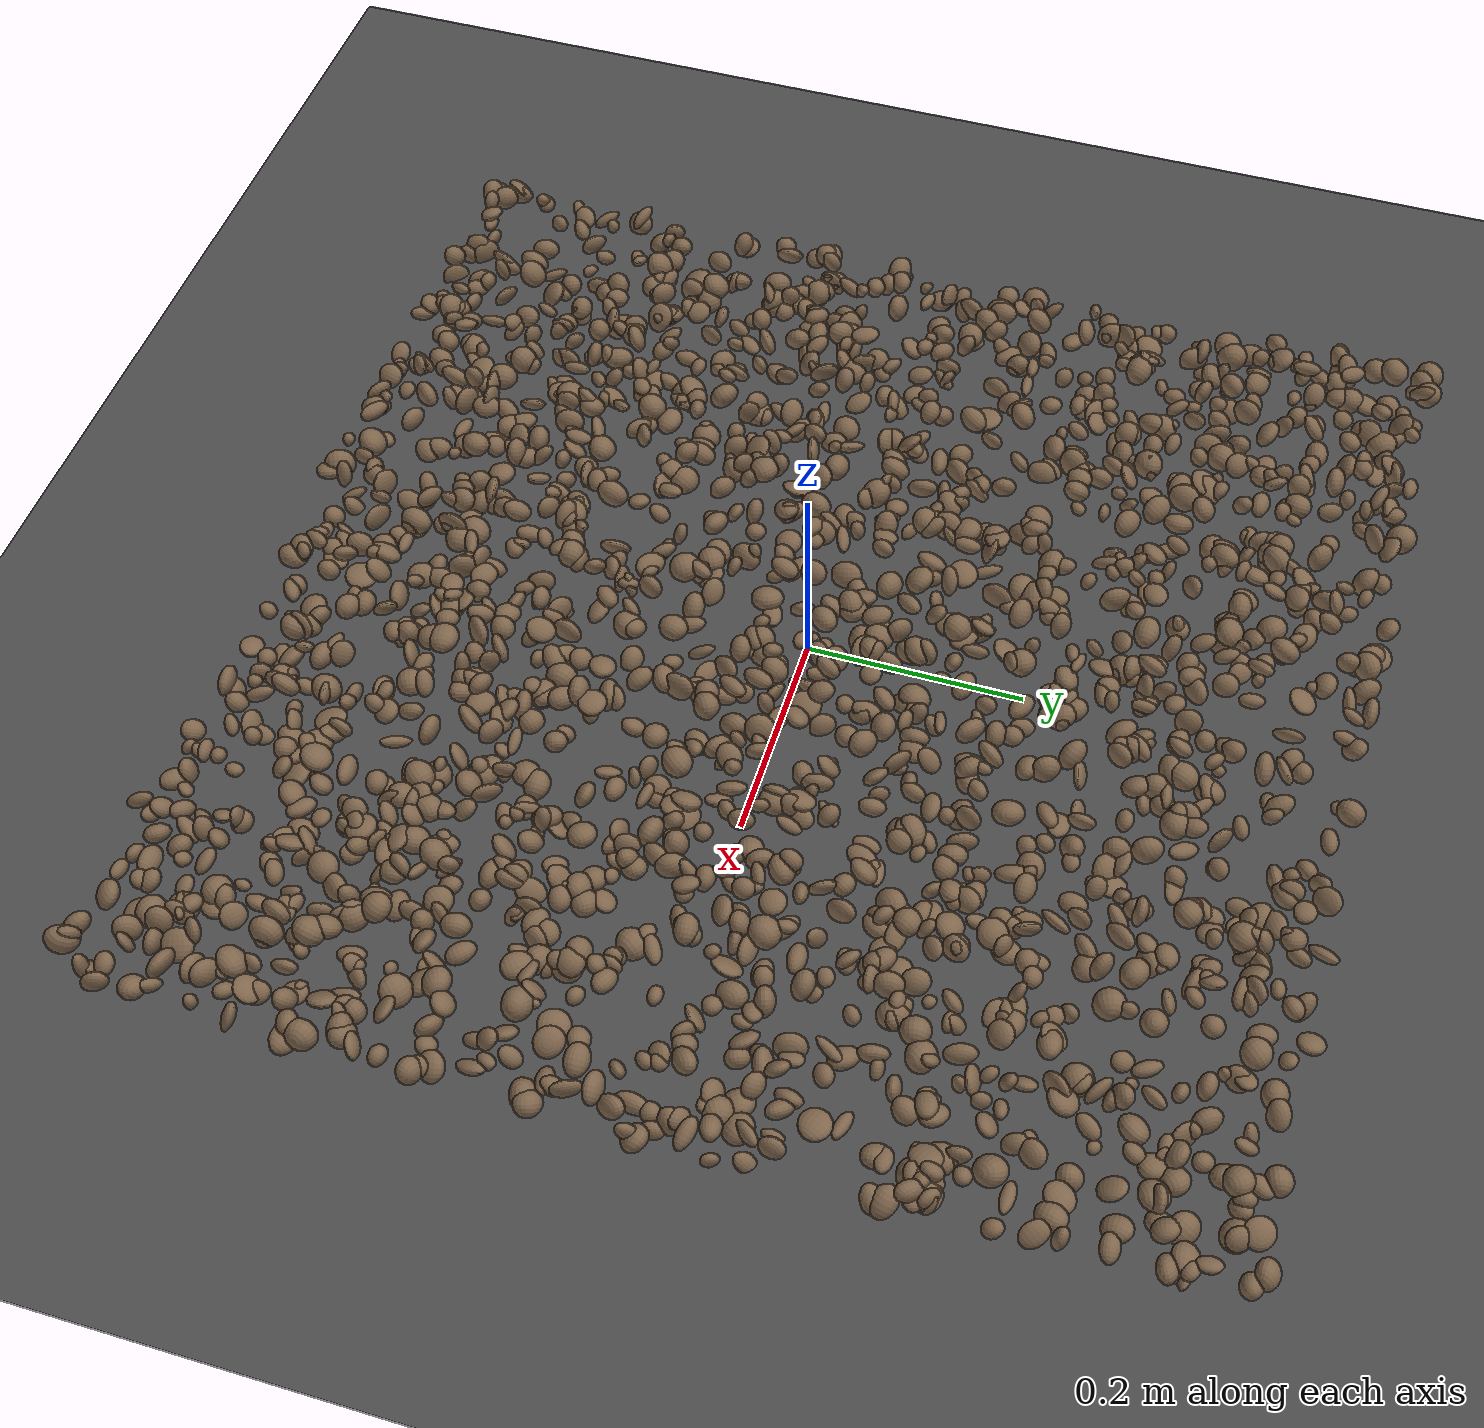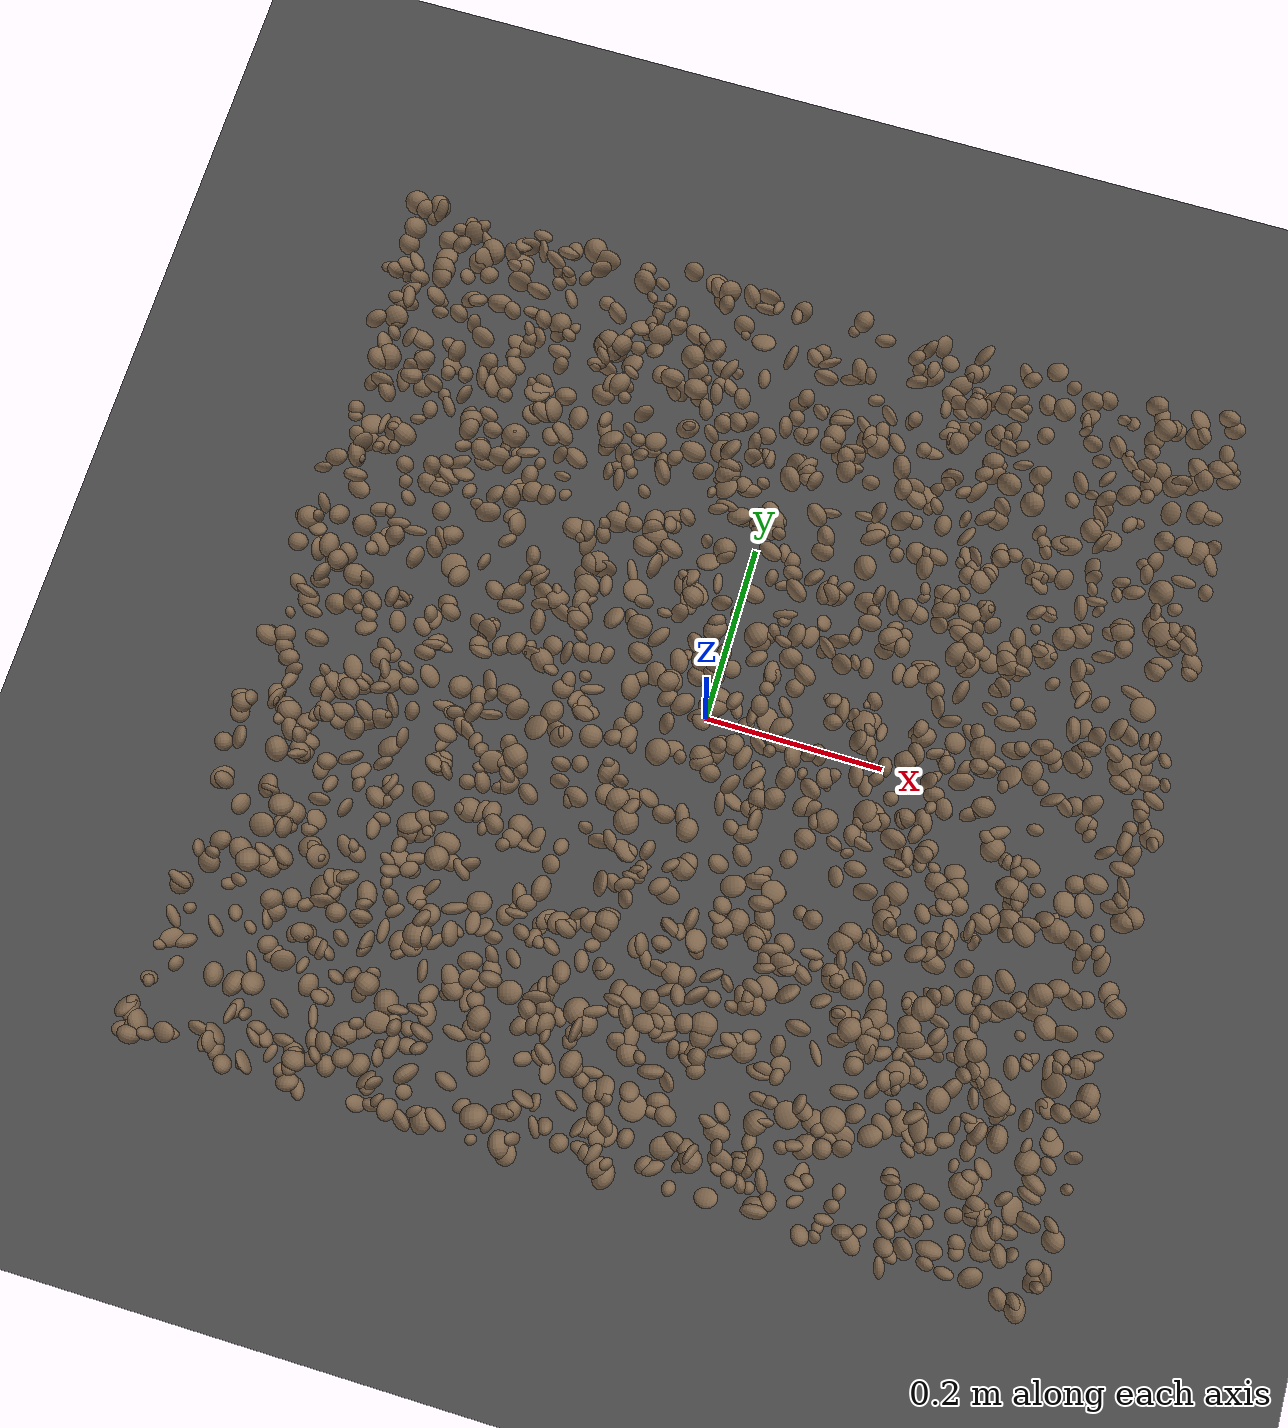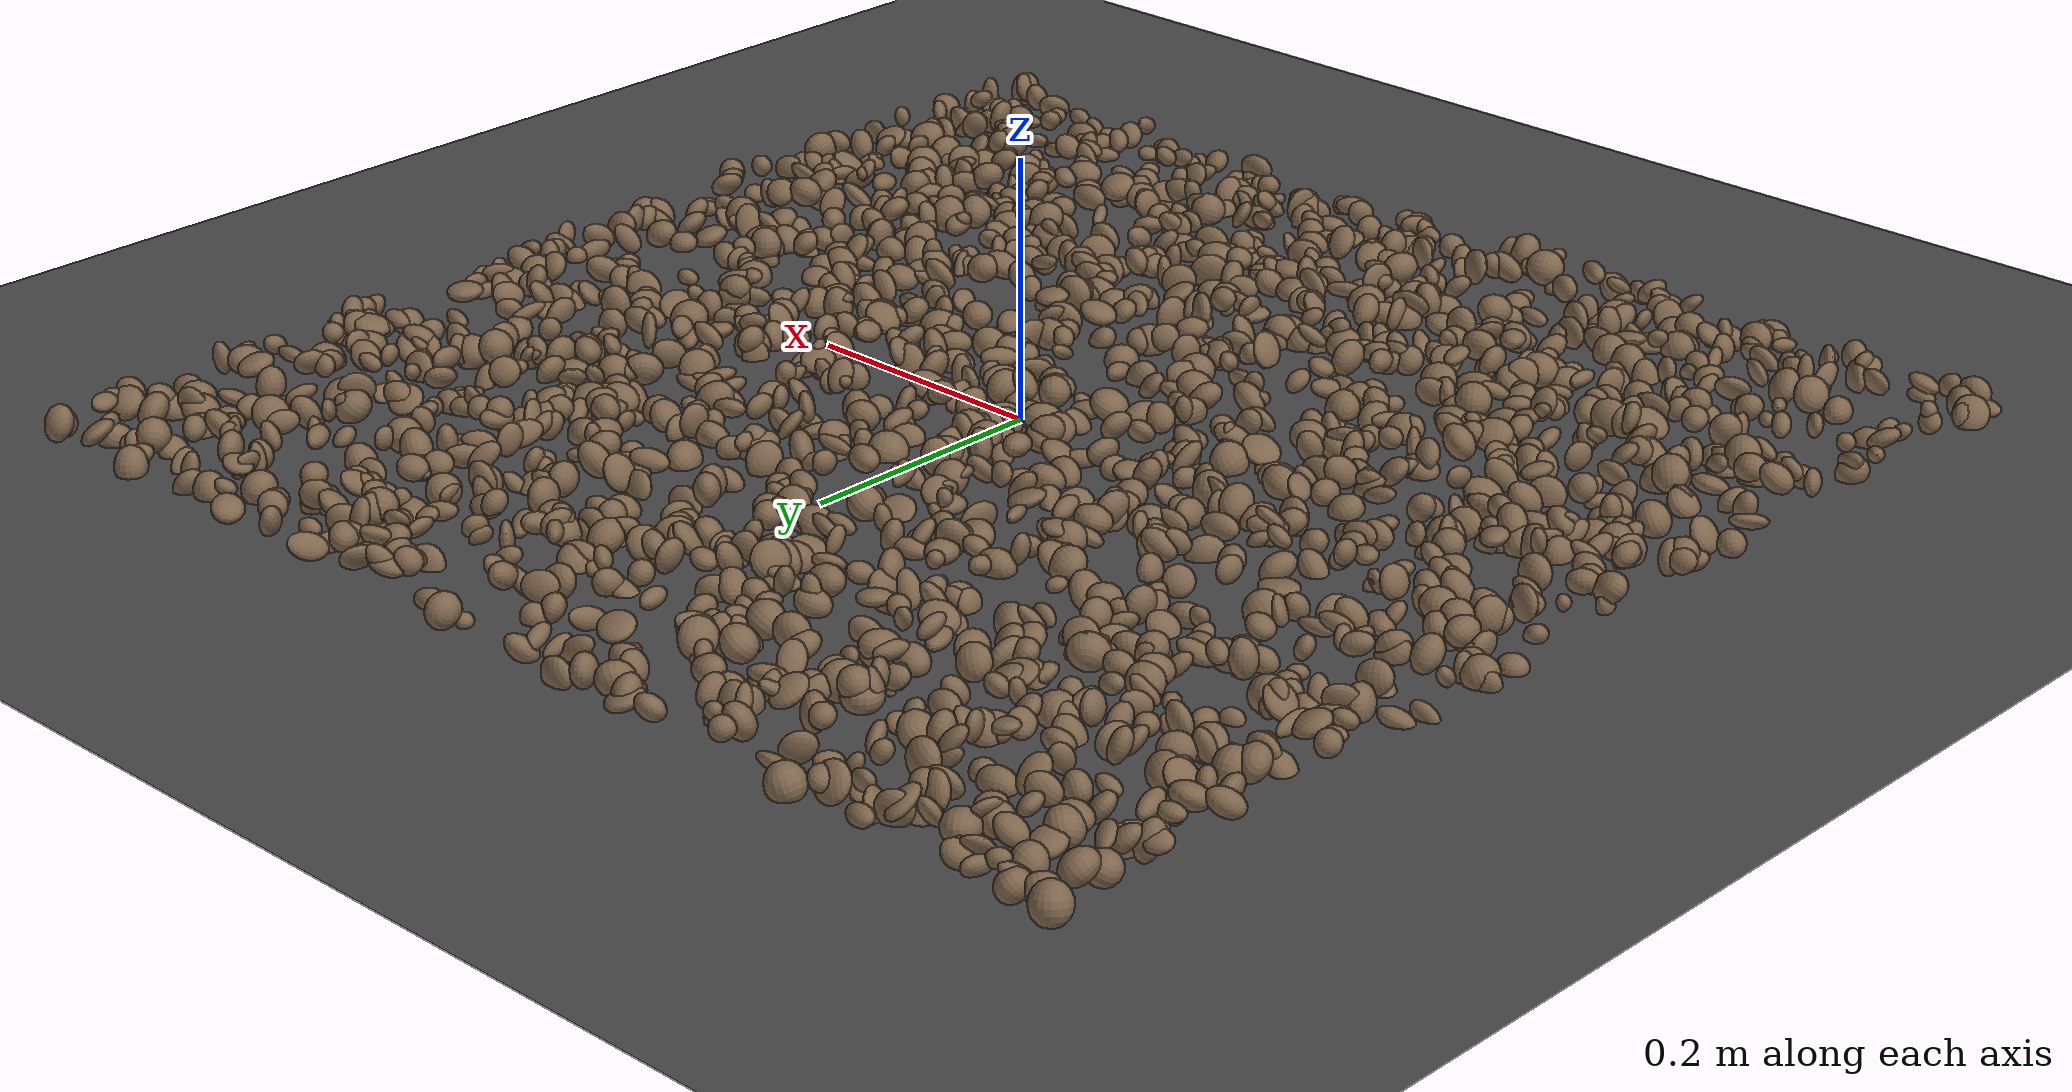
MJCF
<mujoco model="rocky_terrain_scene">
    <compiler angle="radian" inertiafromgeom="true" />
    <option timestep="0.002" gravity="0 0 -9.81" />

    <worldbody>
        <light name="sunlight" pos="5 5 5" dir="-1 -1 -1" diffuse="1 1 1" specular="0.5 0.5 0.5" ambient="0.5 0.5 0.5" />

        <geom name="ground_plane" type="plane" size="50 50 0.1" rgba="0.3 0.3 0.3 1" />

        <body name="rocky_terrain_body">

        <geom name="rock1" type="ellipsoid" size="0.005483598520382708 0.007513090428388757 0.012608785223512848" pos="0.3133956603201442 -0.22147569364267938 0.00615521351486677" quat="0.362452582630413 0.29087904949828974 0.28330136226432556 0.06336700560697166" rgba="0.5 0.4 0.3 1" /><geom name="rock2" type="ellipsoid" size="0.007538012532373246 0.009490577926748112 0.012103782416261666" pos="-0.41786677277025475 -0.14440903300966046 0.014030374079512858" quat="0.0961882978756597 0.7318916294975736 0.1550174418406929 0.0169026307860738" rgba="0.5 0.4 0.3 1" /><geom name="rock3" type="ellipsoid" size="0.010448499568762665 0.01382299371662456 0.008866321106584033" pos="-0.27658876056581994 0.2861109648298048 0.014396407484226518" quat="0.4100548025916153 0.010655237422635914 0.2386314337245088 0.3406585262612401" rgba="0.5 0.4 0.3 1" /><geom name="rock4" type="ellipsoid" size="0.006840439814898308 0.007041393818239615 0.00596505611734093" pos="-0.48268997668771385 -0.4373393989799983 0.014891853455572382" quat="0.1685640876008719 0.22767103583993276 0.3556402720026798 0.24812460455651547" rgba="0.5 0.4 0.3 1" /><geom name="rock5" type="ellipsoid" size="0.006766824375869082 0.014048967554767006 0.007872613308278244" pos="-0.08631929765022062 0.3160027896738492 0.011316895231207809" quat="0.46802839074015035 0.3222341411433568 0.026908226906528342 0.18282924120996447" rgba="0.5 0.4 0.3 1" /><geom name="rock6" type="ellipsoid" size="0.01492090947521544 0.0053042534539293525 0.00522487875257044" pos="0.38852674938686416 0.13449023312965702 0.013594734628798464" quat="0.32665857720924724 0.2854217808702139 0.265010395183992 0.12290924673654688" rgba="0.5 0.4 0.3 1" /><geom name="rock7" type="ellipsoid" size="0.014458587069795907 0.01421162159727999 0.01115604054978717" pos="0.22577833656297341 -0.40615331404302735 0.0002640266097086824" quat="0.3039863263760681 0.3051414336170537 0.30810122320066863 0.08277101680620962" rgba="0.5 0.4 0.3 1" /><geom name="rock8" type="ellipsoid" size="0.005911815060051815 0.014200922224699923 0.00548257060202738" pos="0.4697147443267483 -0.2519243095622161 0.007028069120411253" quat="0.23100935550114773 0.1341624845775573 0.20074054489787624 0.43408761502341864" rgba="0.5 0.4 0.3 1" /><geom name="rock9" type="ellipsoid" size="0.011348977287251361 0.009220745328702491 0.005307565938739052" pos="0.3624378998114852 -0.23472645839584316 0.009422450704743703" quat="0.39455204371532687 0.055975334488352 0.33682563668571225 0.21264698511060887" rgba="0.5 0.4 0.3 1" /><geom name="rock10" type="ellipsoid" size="0.013522390762483148 0.011305168493101599 0.01186077983640805" pos="0.01491100196273798 -0.12358513500805801 0.005082856994854016" quat="0.25401190682519326 0.27552043473492127 0.2403610785049715 0.23010657993491404" rgba="0.5 0.4 0.3 1" /><geom name="rock11" type="ellipsoid" size="0.008663025924923537 0.01191025437318334 0.006801495223951658" pos="0.3386301461370754 -0.43523781913978377 0.010702192267767629" quat="0.2028255720519184 0.08607128026732144 0.29772101222753344 0.4133821354532268" rgba="0.5 0.4 0.3 1" /><geom name="rock12" type="ellipsoid" size="0.01315789864211361 0.005367452134148953 0.006922155709985589" pos="-0.24309267167590698 0.24399605321144768 0.011244348912712641" quat="0.20156868698938227 0.441365544194452 0.04603236480571 0.31103340401045576" rgba="0.5 0.4 0.3 1" /><geom name="rock13" type="ellipsoid" size="0.0075032723313668845 0.013849183161965185 0.012546859886246327" pos="-0.004334988844007515 0.2297657860229091 0.011427237124877221" quat="0.09979414674540368 0.2701176779652667 0.30360609451169834 0.32648208077763125" rgba="0.5 0.4 0.3 1" /><geom name="rock14" type="ellipsoid" size="0.005293757745115092 0.007844372844308799 0.014455224248173096" pos="0.485627667536214 0.4391435170921182 0.004577793197579783" quat="0.3236238144493602 0.16095598287285348 0.3050859475689213 0.210334255108865" rgba="0.5 0.4 0.3 1" /><geom name="rock15" type="ellipsoid" size="0.010566040918543601 0.011039724796957449 0.00843518015889613" pos="0.2466841129953451 0.4805062176681534 0.014630504388662199" quat="0.29919971944268864 0.4141227557375621 0.19827037502907066 0.08840714979067867" rgba="0.5 0.4 0.3 1" /><geom name="rock16" type="ellipsoid" size="0.005745261036852238 0.011220053781457993 0.007231426892973808" pos="-0.09041034787695534 -0.15214588097092263 0.008007163081073809" quat="0.27248042945069995 0.1198323161399828 0.3032865646733162 0.304400689736001" rgba="0.5 0.4 0.3 1" /><geom name="rock17" type="ellipsoid" size="0.014073991400658167 0.01486884632095448 0.01469187580161984" pos="0.46718631192066173 0.22509525366692806 0.0034226836059547826" quat="0.3646638282521687 0.022588368764780833 0.3042364811613803 0.3085113218216702" rgba="0.5 0.4 0.3 1" /><geom name="rock18" type="ellipsoid" size="0.005563685198733303 0.010745269541385098 0.012576270900018437" pos="0.13374365411495115 -0.39688635405003947 0.01273121310408695" quat="0.09420664763845185 0.5842227218042254 0.13082683419421973 0.19074379636310296" rgba="0.5 0.4 0.3 1" /><geom name="rock19" type="ellipsoid" size="0.014932392228830946 0.005495720513203136 0.014717131906436944" pos="0.043497192583378586 -0.41799125824910277 0.010041996961848204" quat="0.2896903554841598 0.2590177920133162 0.2411775306796108 0.21011432182291329" rgba="0.5 0.4 0.3 1" /><geom name="rock20" type="ellipsoid" size="0.012393270444998708 0.00795004207968187 0.012444989948917946" pos="-0.11861963702226341 0.41542464743889373 0.0008931529260487875" quat="0.26939901226733026 0.5751793421200116 0.02392989998397206 0.131491745628686" rgba="0.5 0.4 0.3 1" /><geom name="rock21" type="ellipsoid" size="0.008167525994883776 0.008314486035478718 0.011772543131380608" pos="-0.2754883011994873 0.3476326714661381 0.009679596309943375" quat="0.14063310914396557 0.061418168225927716 0.1755522669799211 0.6223964556501856" rgba="0.5 0.4 0.3 1" /><geom name="rock22" type="ellipsoid" size="0.007726830577584808 0.008416929569306703 0.014955916171085618" pos="-0.25813622815689197 0.027826275902186892 0.008696490711501657" quat="0.2855615988683868 0.012673063275242535 0.3540644403328994 0.3477008975234712" rgba="0.5 0.4 0.3 1" /><geom name="rock23" type="ellipsoid" size="0.010638184055855355 0.008593298085707276 0.005925585387282153" pos="-0.25779996959581686 0.034353358236631326 0.0019012942449886366" quat="0.5250628990853193 0.06883813897502102 0.19615059058598416 0.2099483713536755" rgba="0.5 0.4 0.3 1" /><geom name="rock24" type="ellipsoid" size="0.01294896391599629 0.011455095500318417 0.008478974115936155" pos="0.22274220811775336 0.20403473238633607 0.012428015619872543" quat="0.32960641572753435 0.2596868345608516 0.08207053045235221 0.32863621925926184" rgba="0.5 0.4 0.3 1" /><geom name="rock25" type="ellipsoid" size="0.006712860978456005 0.01057650909700748 0.005526848248087648" pos="0.08820098675259658 -0.0649464003489919 0.012205442067265804" quat="0.25929111324700926 0.3848826041372037 0.1906530176100461 0.1651732650057409" rgba="0.5 0.4 0.3 1" /><geom name="rock26" type="ellipsoid" size="0.012627203681629354 0.012614793281330756 0.0065821304733090875" pos="-0.1314491612171359 -0.025308105078029386 0.005678549987733155" quat="0.2724052288608031 0.14455362957356202 0.21628436638888845 0.3667567751767463" rgba="0.5 0.4 0.3 1" /><geom name="rock27" type="ellipsoid" size="0.006509286445523887 0.01286198903888957 0.014472785859726604" pos="0.14781028057255774 0.31813895157809113 0.00865391827944733" quat="0.3520376808398874 0.11949497755981427 0.33264899097977696 0.19581835062052136" rgba="0.5 0.4 0.3 1" /><geom name="rock28" type="ellipsoid" size="0.010490941585735256 0.009389788336118799 0.013488541975163647" pos="-0.06201768276038555 0.33924789421765533 0.008067069096602207" quat="0.3684071858333431 0.2716505394722046 0.01670102596666563 0.3432412487277868" rgba="0.5 0.4 0.3 1" /><geom name="rock29" type="ellipsoid" size="0.005875154845837137 0.009786698835711817 0.007795672093986669" pos="-0.33153431503638 0.2308324996200274 0.012847478640053336" quat="0.24385278281671782 0.05641153148065791 0.3074266700078843 0.3923090156947399" rgba="0.5 0.4 0.3 1" /><geom name="rock30" type="ellipsoid" size="0.009369424858106584 0.010875687420950058 0.013240726750832339" pos="0.2985167841252563 0.15243710354797535 0.014579910686880316" quat="0.38455882735398195 0.28065738414907 0.3007820942638755 0.0340016942330726" rgba="0.5 0.4 0.3 1" /><geom name="rock31" type="ellipsoid" size="0.011005533079781925 0.010344413964749125 0.0120986407354009" pos="0.07808890701195215 -0.416782821565468 0.006886359512314842" quat="0.37605624279500666 0.21034913785422377 0.3979129930895686 0.015681626261201054" rgba="0.5 0.4 0.3 1" /><geom name="rock32" type="ellipsoid" size="0.014855501405282606 0.0061277417734672355 0.013299402142412146" pos="-0.4339864145837863 0.22055624748561153 0.012090076693049899" quat="0.2799414675773171 0.013769837643094623 0.27999819781529084 0.4262904969642974" rgba="0.5 0.4 0.3 1" /><geom name="rock33" type="ellipsoid" size="0.008774322343045607 0.006192643084368489 0.005565138878655232" pos="0.3705031732073477 0.2603759588640525 0.008981933305236285" quat="0.0928831548122742 0.25699102274133284 0.22019341906942433 0.42993240337696875" rgba="0.5 0.4 0.3 1" /><geom name="rock34" type="ellipsoid" size="0.005978012707349349 0.008221789084747452 0.012353038224917422" pos="0.37952406157621343 -0.22015169266302403 0.004831796070947895" quat="0.09522284572497076 0.43647925699594997 0.1038530620943288 0.36444483518475046" rgba="0.5 0.4 0.3 1" /><geom name="rock35" type="ellipsoid" size="0.007412150201308378 0.014204174092198714 0.013743080140798069" pos="0.12253332571147779 0.4476247948304668 0.0002710777493672595" quat="0.1626078665522773 0.24452502884106483 0.2810446762122607 0.3118224283943971" rgba="0.5 0.4 0.3 1" /><geom name="rock36" type="ellipsoid" size="0.005737831601192194 0.005228496441259971 0.006161295879057463" pos="-0.36209956022844747 0.0370319762314939 0.006430397193351465" quat="0.24611289522499946 0.01903258793139701 0.3706889567245727 0.3641655601190309" rgba="0.5 0.4 0.3 1" /><geom name="rock37" type="ellipsoid" size="0.012532838597665102 0.009005100834694264 0.007039291336823857" pos="0.4239282761882709 0.2940356876180097 0.012360119020209307" quat="0.21002499597121996 0.25943188220360813 0.11628537011573255 0.4142577517094393" rgba="0.5 0.4 0.3 1" /><geom name="rock38" type="ellipsoid" size="0.014239944183998637 0.008115854333836402 0.010916299048861405" pos="-0.14552976572317045 -0.06483653166052816 0.011255313687688452" quat="0.2988781048763428 0.4072451968661203 0.07679522068485473 0.21708147757268226" rgba="0.5 0.4 0.3 1" /><geom name="rock39" type="ellipsoid" size="0.013995129558038336 0.01498823814307005 0.013802485622060993" pos="0.2982740410443687 0.05185780100455495 0.009715862633155922" quat="0.17463926751931516 0.2362328134943004 0.10803125878710285 0.4810966601992816" rgba="0.5 0.4 0.3 1" /><geom name="rock40" type="ellipsoid" size="0.01228864516533017 0.006545689809543255 0.006378609204112443" pos="-0.03180404594435027 0.4811871481691491 0.011413483319713093" quat="0.23669020756326603 0.25523000869653945 0.3890099143982088 0.11906986934198566" rgba="0.5 0.4 0.3 1" /><geom name="rock41" type="ellipsoid" size="0.010862493439241224 0.01431688057898892 0.010830341453862871" pos="-0.20345501824515322 0.3427822365481511 0.014951979395766694" quat="0.018119206545112253 0.1959849511041449 0.7550177499362708 0.03087809241447206" rgba="0.5 0.4 0.3 1" /><geom name="rock42" type="ellipsoid" size="0.007319434405769546 0.010219801536461705 0.01324016351586995" pos="-0.20004417942718167 0.3460661516349981 0.008821971382490518" quat="0.25942712098637044 0.2824709390755317 0.28886919479281703 0.16923274514528075" rgba="0.5 0.4 0.3 1" /><geom name="rock43" type="ellipsoid" size="0.013205839253486087 0.010376961255893538 0.010328638077881497" pos="-0.13022890373125173 -0.41376615416959417 0.0032193787098803387" quat="0.20200334917368323 0.24860183971247798 0.25466718693985074 0.294727624173988" rgba="0.5 0.4 0.3 1" /><geom name="rock44" type="ellipsoid" size="0.008997902495406971 0.005243782598000571 0.0127235645216048" pos="0.09508872767636489 0.13826356248469995 0.011807919172400514" quat="0.0005929420377758875 0.23511272041735762 0.5292539058445888 0.23504043170027777" rgba="0.5 0.4 0.3 1" /><geom name="rock45" type="ellipsoid" size="0.008932110792621278 0.013233143722727103 0.00565239163657307" pos="-0.26477829414411713 -0.07244014833690016 0.0074776942047041555" quat="0.3354473184267813 0.06297951011539875 0.14837925176798158 0.45319391968983835" rgba="0.5 0.4 0.3 1" /><geom name="rock46" type="ellipsoid" size="0.011842919495300499 0.013683665574428558 0.013191415228673044" pos="-0.3526350590324221 0.2556684736417377 0.009188747042178995" quat="0.08663807439668945 0.2529898730483007 0.3393438853603791 0.32102816719463073" rgba="0.5 0.4 0.3 1" /><geom name="rock47" type="ellipsoid" size="0.005070515646934182 0.00503499322265382 0.009534270121787303" pos="-0.3448809309616051 -0.34508317494796614 0.011388831296921606" quat="0.19765974376979897 0.3636977876623824 0.005509059136029093 0.4331334094317896" rgba="0.5 0.4 0.3 1" /><geom name="rock48" type="ellipsoid" size="0.009341978372744501 0.008199246084066051 0.006598153458780656" pos="-0.3570534293981087 -0.34892729755029805 0.0002460457051709841" quat="0.16482195100815422 0.2526871884669185 0.4021822322724188 0.18030862825250848" rgba="0.5 0.4 0.3 1" /><geom name="rock49" type="ellipsoid" size="0.0053602350186195335 0.014607194881899224 0.011332627566430518" pos="-0.025984237676278665 -0.18825800907832413 0.0018178581268140303" quat="0.32595092675736514 0.19836431640929952 0.16196852828714703 0.3137162285461883" rgba="0.5 0.4 0.3 1" /><geom name="rock50" type="ellipsoid" size="0.005132514083789387 0.008347205948475038 0.007133472554123643" pos="-0.315788413989888 0.16264282241250416 0.008946965307747108" quat="0.2894459547164047 0.1469066214069409 0.2798510454337497 0.2837963784429046" rgba="0.5 0.4 0.3 1" /><geom name="rock51" type="ellipsoid" size="0.006487758061629994 0.010877767330062207 0.0139159256947827" pos="-0.1680888735827335 0.3202147390244541 0.003153427198607956" quat="0.2875010105746846 0.02009905250444194 0.18532352636792707 0.5070764105529464" rgba="0.5 0.4 0.3 1" /><geom name="rock52" type="ellipsoid" size="0.01253678054495985 0.00680088075840537 0.012309276433199614" pos="-0.41273332598314816 -0.2868326102388532 0.003427392539263844" quat="0.10543194489508934 0.30261319253375524 0.14204797843598924 0.4499068841351662" rgba="0.5 0.4 0.3 1" /><geom name="rock53" type="ellipsoid" size="0.011861991261495864 0.00781014271744496 0.010782377769976217" pos="0.2539064483653515 -0.2718671866803729 0.011974836472403523" quat="0.058837444017985185 0.35689515985482634 0.2890500973294542 0.2952172987977344" rgba="0.5 0.4 0.3 1" /><geom name="rock54" type="ellipsoid" size="0.013146413395715786 0.005701573006684025 0.009659814133823472" pos="0.08492690573400219 0.1208669187014223 0.0044506928781237985" quat="0.22251778150216792 0.3470351975890152 0.2629956639156217 0.1674513569931953" rgba="0.5 0.4 0.3 1" /><geom name="rock55" type="ellipsoid" size="0.014167620629208778 0.009674565703477725 0.010611200411962354" pos="-0.30858170549012365 0.07613491317947207 0.011238495743658103" quat="0.23772418343244203 0.4210451724743782 0.337940454681371 0.003290189411808718" rgba="0.5 0.4 0.3 1" /><geom name="rock56" type="ellipsoid" size="0.01247614252306542 0.008629004148427127 0.009889344388522788" pos="0.052893047165339824 0.027887274211889745 0.014982179627049525" quat="0.08543060853882663 0.3187737434038033 0.3198846523844757 0.2759109956728944" rgba="0.5 0.4 0.3 1" /><geom name="rock57" type="ellipsoid" size="0.014128804843711228 0.01233367391479227 0.0132579999591502" pos="0.37289777017890513 -0.09406991377591989 0.004174331731033889" quat="0.3934329768746627 0.1586774384045019 0.21555053538018346 0.23233904934065192" rgba="0.5 0.4 0.3 1" /><geom name="rock58" type="ellipsoid" size="0.011917816065491913 0.012931062178842025 0.006121630937761219" pos="0.12602122580791808 0.09857972990633068 0.014244213761082801" quat="0.015015995217470006 0.299090184450823 0.4222825967854411 0.2636112235462659" rgba="0.5 0.4 0.3 1" /><geom name="rock59" type="ellipsoid" size="0.006607026760146553 0.005145260851998154 0.007134627213145429" pos="0.28095043876121595 -0.08797945522611128 0.005335520907075594" quat="0.41341786143072085 0.20056271993302535 0.30585435887179707 0.08016505976445666" rgba="0.5 0.4 0.3 1" /><geom name="rock60" type="ellipsoid" size="0.011631283702155007 0.014984783927397782 0.006689536111900914" pos="0.26003366673026296 0.10646204543429039 0.00821042934424906" quat="0.4272778372825715 0.17965081591177284 0.3152112521379533 0.07786009466770231" rgba="0.5 0.4 0.3 1" /><geom name="rock61" type="ellipsoid" size="0.005384372122122337 0.012976608873138205 0.014573892536289938" pos="-0.16580879060572995 0.08817185907714697 0.0071333453452561285" quat="0.07636828304515964 0.24794639507849459 0.3596610663781372 0.3160242554982085" rgba="0.5 0.4 0.3 1" /><geom name="rock62" type="ellipsoid" size="0.006961465841555365 0.006528545770469528 0.008326864707228345" pos="-0.4382830171941261 0.47733321124807004 0.008039844459430949" quat="0.055739783769789 0.3292030677991564 0.2776966739115612 0.33736047451949336" rgba="0.5 0.4 0.3 1" /><geom name="rock63" type="ellipsoid" size="0.005774183919057871 0.010387829772920472 0.007961989724783103" pos="0.057807889079761865 0.1065736923532713 0.008186963524429392" quat="0.47754659705446545 0.12028904575760521 0.01957802585786069 0.38258633133006864" rgba="0.5 0.4 0.3 1" /><geom name="rock64" type="ellipsoid" size="0.012496903771766606 0.008886541974193732 0.014678654951265635" pos="-0.4377081267183157 0.3335377139885861 0.008743205585326748" quat="0.43546635009322615 0.22283949062785277 0.2938141714119509 0.04787998786697027" rgba="0.5 0.4 0.3 1" /><geom name="rock65" type="ellipsoid" size="0.012182936465614504 0.008865517967480079 0.01189137890388897" pos="-0.46000514432162387 0.0041159662350153114 0.010792576767613807" quat="0.22313202825068754 0.26306649213717836 0.23855392658305374 0.2752475530290803" rgba="0.5 0.4 0.3 1" /><geom name="rock66" type="ellipsoid" size="0.013463161085580082 0.007082269894857511 0.0065204845837434616" pos="-0.4480206379954277 -0.08820307025014551 0.014993341379255152" quat="0.24624306284315314 0.35092578411179715 0.36393497833250726 0.0388961747125425" rgba="0.5 0.4 0.3 1" /><geom name="rock67" type="ellipsoid" size="0.014066432348025813 0.010839882766329054 0.014996657108161483" pos="0.09044920878694018 -0.31690644890489494 0.011873997418538928" quat="0.21474568552710757 0.2525703830543139 0.25274744244874675 0.2799364889698318" rgba="0.5 0.4 0.3 1" /><geom name="rock68" type="ellipsoid" size="0.008508416289650343 0.013785563452523422 0.012671991053148424" pos="0.22037482819358745 0.11467743799732921 0.012595196014242012" quat="0.11443295258296661 0.22538950039559028 0.15876674135484536 0.5014108056665978" rgba="0.5 0.4 0.3 1" /><geom name="rock69" type="ellipsoid" size="0.013256743137930637 0.009049109140265877 0.0122402475864887" pos="0.40730145908839444 0.3995990175003383 0.002319396447643561" quat="0.22520806627296 0.04994539095425403 0.3653356704793842 0.35951087229340173" rgba="0.5 0.4 0.3 1" /><geom name="rock70" type="ellipsoid" size="0.008069682147923923 0.01002694566263182 0.014917150187338222" pos="-0.08401880129123074 -0.4600852305115358 0.009282073112092637" quat="0.3017286541718836 0.1431422445724398 0.20371378939806153 0.35141531185761504" rgba="0.5 0.4 0.3 1" /><geom name="rock71" type="ellipsoid" size="0.014155030306340695 0.010285459629566026 0.005035946315826172" pos="-0.004435403836096863 -0.4529764332372552 0.0025660892198407343" quat="0.31777076577614455 0.3058863678200178 0.33534610410651206 0.04099676229732563" rgba="0.5 0.4 0.3 1" /><geom name="rock72" type="ellipsoid" size="0.012974817292028155 0.00819607761397316 0.009274696427889315" pos="0.292857356586956 -0.23368210226246577 0.00809296789910475" quat="0.2500251023793872 0.18873289414009145 0.2845003605349927 0.2767416429455286" rgba="0.5 0.4 0.3 1" /><geom name="rock73" type="ellipsoid" size="0.01314972259820673 0.006408999001871406 0.008056566351868463" pos="0.13339251709122035 -0.23665052378638418 0.00907253033925912" quat="0.2173428474320592 0.2658733286361471 0.10183403846614274 0.414949785465651" rgba="0.5 0.4 0.3 1" /><geom name="rock74" type="ellipsoid" size="0.009600935838368194 0.01431546144691832 0.011421043323687464" pos="0.33511340618904883 0.09636803116656922 0.00777022327423354" quat="0.3228756267914138 0.14930430621552035 0.23529345410942376 0.29252661288364207" rgba="0.5 0.4 0.3 1" /><geom name="rock75" type="ellipsoid" size="0.01365331299009306 0.01160665116851703 0.008583435218095044" pos="0.011027033846619294 0.2401386237968507 0.003555914168974538" quat="0.09645322179044123 0.020781931125723272 0.5274767821820779 0.35528806490175757" rgba="0.5 0.4 0.3 1" /><geom name="rock76" type="ellipsoid" size="0.012000808405184395 0.011551828173462994 0.005713318912397271" pos="-0.3106532547474816 0.37259737841627805 0.010266848693660952" quat="0.14542106992105708 0.1451929758454841 0.5036733960100104 0.20571255822344836" rgba="0.5 0.4 0.3 1" /><geom name="rock77" type="ellipsoid" size="0.005701160696485102 0.007529667449867395 0.0070834942426051175" pos="-0.21994210084294674 -0.12240962554123769 0.011731138236378313" quat="0.25699430233708265 0.2721741372247779 0.14443439031040337 0.32639717012773606" rgba="0.5 0.4 0.3 1" /><geom name="rock78" type="ellipsoid" size="0.007944029296571675 0.012330540832662027 0.006140291649565595" pos="0.46329444106364404 0.19941456337594443 0.006544514056703719" quat="0.057061856178254274 0.45231280900435294 0.4765873274200361 0.014038007397356684" rgba="0.5 0.4 0.3 1" /><geom name="rock79" type="ellipsoid" size="0.011931241069946398 0.0098344970787845 0.013512145578522303" pos="0.39604395981481844 -0.29601615888598753 0.009117311686788107" quat="0.44576277444641105 0.2613058063334301 0.026955438733357914 0.2659759804868009" rgba="0.5 0.4 0.3 1" /><geom name="rock80" type="ellipsoid" size="0.0112666289118343 0.013324159751340482 0.005094876336745054" pos="0.06941553648477006 -0.38360343055074964 0.0052535904428737245" quat="0.12475308684660084 0.21380019246103618 0.39910351816161926 0.2623432025307437" rgba="0.5 0.4 0.3 1" /><geom name="rock81" type="ellipsoid" size="0.00771205785377505 0.005896034510092291 0.014145799801285337" pos="0.1184493835506577 0.36753918588504464 0.004420121417544446" quat="0.44093979814295775 0.31776797525923506 0.15437298355251716 0.0869192430452901" rgba="0.5 0.4 0.3 1" /><geom name="rock82" type="ellipsoid" size="0.011445921921949483 0.007134040137893188 0.011886639908673478" pos="0.44970569980318065 0.056595595561078516 0.01236341505618938" quat="0.482790240874596 0.16183611475403148 0.2914876808614779 0.06388596350989463" rgba="0.5 0.4 0.3 1" /><geom name="rock83" type="ellipsoid" size="0.008925865425269536 0.01044156929567057 0.01342754978870555" pos="-0.40086205046113366 -0.1107811182672147 0.01110385622029173" quat="0.43026619509595493 0.23893543933388509 0.25400056821730194 0.07679779735285792" rgba="0.5 0.4 0.3 1" /><geom name="rock84" type="ellipsoid" size="0.009562199681249613 0.013672952526900463 0.009224526253183511" pos="0.2655424724711345 -0.07871979534463269 0.013385449271824057" quat="0.10291275966534648 0.24913318884057636 0.3384880350715683 0.30946601642250876" rgba="0.5 0.4 0.3 1" /><geom name="rock85" type="ellipsoid" size="0.010780975548449671 0.012500361378657461 0.009871293463866955" pos="0.4594048207826964 -0.24518020492915538 0.0021966405306763684" quat="0.3398586909611478 0.26789663352359616 0.19471670527992904 0.197527970235327" rgba="0.5 0.4 0.3 1" /><geom name="rock86" type="ellipsoid" size="0.006784373466197624 0.012231995416622808 0.011407939991479708" pos="-0.33350990779241885 -0.28157409348020424 0.013164545799069784" quat="0.27838814737058853 0.47454566312869934 0.09302202187266102 0.15404416762805104" rgba="0.5 0.4 0.3 1" /><geom name="rock87" type="ellipsoid" size="0.009563709363765528 0.009597341991879817 0.008979505769719426" pos="-0.48381374128090937 0.23360101235910302 0.005719137408886897" quat="0.16172456521046194 0.2751768291593758 0.2284508111992137 0.3346477944309486" rgba="0.5 0.4 0.3 1" /><geom name="rock88" type="ellipsoid" size="0.00875329179421787 0.0058935041045569845 0.01133198739091272" pos="0.37132328308437834 0.06480739672032121 0.008965925381660552" quat="0.2629933842250679 0.14299989751060763 0.2625589000868674 0.3314478181774571" rgba="0.5 0.4 0.3 1" /><geom name="rock89" type="ellipsoid" size="0.006428569232923391 0.010502108252007654 0.012207439632056116" pos="0.1677246476743658 -0.37272937216307045 0.003109507176942133" quat="0.2105576555701403 0.3318076738493995 0.3290115603379969 0.12862311024246337" rgba="0.5 0.4 0.3 1" /><geom name="rock90" type="ellipsoid" size="0.006437442977486547 0.010552154219754861 0.0069752797250410455" pos="-0.1397854985091792 0.006642029345791278 0.010895422467060626" quat="0.26725072656375254 0.3109843239156976 0.19620230720831028 0.2255626423122396" rgba="0.5 0.4 0.3 1" /><geom name="rock91" type="ellipsoid" size="0.012834042867469302 0.006445551859238952 0.005443721922797722" pos="-0.3726822037541556 -0.0754910897460539 0.00666786377796433" quat="0.6452701723282821 0.22334044880080325 0.05235149036260583 0.07903788850830878" rgba="0.5 0.4 0.3 1" /><geom name="rock92" type="ellipsoid" size="0.006936802164487214 0.009212616319371734 0.009901236356191983" pos="-0.49551266576914377 -0.11901411851316424 0.010282763164931787" quat="0.14182138613086792 0.26127860080367077 0.3263918798356533 0.270508133229808" rgba="0.5 0.4 0.3 1" /><geom name="rock93" type="ellipsoid" size="0.008926643028939675 0.00784174111060415 0.008903956073120126" pos="0.370548534055277 0.029945409173042226 0.0004628404350120296" quat="0.28866207962159834 0.2141783923790157 0.186120734902193 0.311038793097193" rgba="0.5 0.4 0.3 1" /><geom name="rock94" type="ellipsoid" size="0.008643948857902446 0.012093657778355912 0.013767726309258824" pos="-0.13837485740834354 -0.3345930981138393 0.014217682524446298" quat="0.06791750723258684 0.42901779924101713 0.4105377144614309 0.09252697906496508" rgba="0.5 0.4 0.3 1" /><geom name="rock95" type="ellipsoid" size="0.005713657779289155 0.01384450059968026 0.014677338774369868" pos="-0.334730674372546 -0.3067089810715098 0.012901081486627745" quat="0.29200439006839807 0.12111267545366142 0.26918763566901693 0.31769529880892355" rgba="0.5 0.4 0.3 1" /><geom name="rock96" type="ellipsoid" size="0.013862695323108989 0.005550257431610156 0.008703246140193988" pos="-0.4310173084996829 0.22375504034109417 0.013785216611127178" quat="0.4145808277983769 0.06831190516598257 0.37039624298059987 0.1467110240550408" rgba="0.5 0.4 0.3 1" /><geom name="rock97" type="ellipsoid" size="0.008493707801829977 0.014823379939689754 0.01373328671548293" pos="0.3755262153279426 0.3211126021872499 0.008342593885261693" quat="0.024681365603509354 0.3579211813602486 0.20579016549564275 0.41160728754059933" rgba="0.5 0.4 0.3 1" /><geom name="rock98" type="ellipsoid" size="0.013859874903946526 0.013472553329567899 0.006350324887104535" pos="0.44186077008276214 0.4872782881386667 0.011556660549856044" quat="0.29089286064795955 0.06588338953506437 0.16351353898485957 0.47971021083211657" rgba="0.5 0.4 0.3 1" /><geom name="rock99" type="ellipsoid" size="0.009805581070817236 0.013888505463848514 0.0073149095727638586" pos="-0.21942423971983904 -0.41094615830937853 0.01467509512664136" quat="0.2711046911719817 0.2645771669928829 0.25860814842796487 0.20570999340717047" rgba="0.5 0.4 0.3 1" /><geom name="rock100" type="ellipsoid" size="0.008278964968728979 0.006719286428663283 0.011398547013649247" pos="0.2822833944282883 -0.13851764931471267 0.0008895771970498261" quat="0.4695856489999005 0.32443080602255286 0.15237108045454967 0.05361246452299696" rgba="0.5 0.4 0.3 1" /><geom name="rock101" type="ellipsoid" size="0.00597282764070098 0.0113951453074939 0.013972952716822938" pos="-0.15948212185616673 -0.34038083808949215 0.01080938001853546" quat="0.23423287562154496 0.1281452503782937 0.6170167236133163 0.020605150386845027" rgba="0.5 0.4 0.3 1" /><geom name="rock102" type="ellipsoid" size="0.012058524709821744 0.011839668739637071 0.008556934362750816" pos="-0.06544917365915226 0.37048414638655847 0.0027074006534192363" quat="0.14657768366592153 0.2645221200023999 0.12485296843266597 0.46404722789901265" rgba="0.5 0.4 0.3 1" /><geom name="rock103" type="ellipsoid" size="0.010203266023661652 0.012530749787852907 0.013001684455865518" pos="-0.4274610441298389 0.31002717143486946 0.009557595544651746" quat="0.15266636480076182 0.1328962036148483 0.2787715579575581 0.43566587362683173" rgba="0.5 0.4 0.3 1" /><geom name="rock104" type="ellipsoid" size="0.011312207247205544 0.0072242740280375126 0.013472796639062926" pos="0.009176417300482909 -0.3102583039476329 0.008347086647013686" quat="0.3566448818822488 0.2774692807183253 0.25389790068535484 0.11198793671407112" rgba="0.5 0.4 0.3 1" /><geom name="rock105" type="ellipsoid" size="0.012359518837288499 0.013326761814026443 0.008091837144922119" pos="-0.4022326006815451 -0.07631048522926065 0.009080597798323342" quat="0.3483130945502435 0.011472660007421816 0.31440880601790555 0.32580543942442913" rgba="0.5 0.4 0.3 1" /><geom name="rock106" type="ellipsoid" size="0.007816636579415578 0.009407937399788787 0.010863521635464389" pos="0.023586669427701157 -0.24792126575857454 0.014376847815625284" quat="0.15601044799912978 0.3462183623309049 0.24663715594299043 0.2511340337269749" rgba="0.5 0.4 0.3 1" /><geom name="rock107" type="ellipsoid" size="0.009230417445431847 0.009324023908463805 0.00506228369139389" pos="0.44547252239716406 -0.34073446582204836 0.008533006979753753" quat="0.22102821857154226 0.30217554743509994 0.09304664791822718 0.38374958607513066" rgba="0.5 0.4 0.3 1" /><geom name="rock108" type="ellipsoid" size="0.011423781807000662 0.007678354320890951 0.005629910386349401" pos="-0.23633945505464038 0.09484934098207587 0.013221311373001112" quat="0.25257716833704535 0.4061375162310033 0.016527432877768426 0.32475788255418286" rgba="0.5 0.4 0.3 1" /><geom name="rock109" type="ellipsoid" size="0.010333934686419535 0.008216445474217928 0.012962862883722101" pos="0.4803081436161144 0.031571962846083546 0.007942001910198322" quat="0.027413119086296747 0.41617590431345064 0.4108003307800531 0.14561064582019947" rgba="0.5 0.4 0.3 1" /><geom name="rock110" type="ellipsoid" size="0.005956900760600934 0.009175716685541038 0.014390342959751674" pos="0.3186189698215698 -0.41262518955122685 0.008584467122170734" quat="0.4057209178144162 0.0648015920465584 0.0793427228629949 0.4501347672760305" rgba="0.5 0.4 0.3 1" /><geom name="rock111" type="ellipsoid" size="0.00895590024928934 0.009342289468237095 0.0065362921797559636" pos="-0.46975577828935033 0.330845575087501 0.013236162720677963" quat="0.014699086420917037 0.28498387908724665 0.24941439196525725 0.45090264252657897" rgba="0.5 0.4 0.3 1" /><geom name="rock112" type="ellipsoid" size="0.007930632950794263 0.009737623468042848 0.012301217337802574" pos="-0.42876673172522195 0.45657573332243995 0.014769238524798535" quat="0.005032446479855553 0.277328756083694 0.11635663141200041 0.60128216602445" rgba="0.5 0.4 0.3 1" /><geom name="rock113" type="ellipsoid" size="0.006859848831464308 0.008086296058677497 0.007632965651528925" pos="-0.23730853341211755 -0.2794723485238769 0.005829224721067723" quat="0.30309310771096415 0.24539242830861183 0.12273072727591067 0.32878373670451344" rgba="0.5 0.4 0.3 1" /><geom name="rock114" type="ellipsoid" size="0.006955877092727807 0.008158161624206167 0.01049408690887636" pos="0.4016943761789702 0.2175757565297417 0.005668290836833588" quat="0.40780309354281985 0.22349124928761874 0.03336762083027172 0.3353380363392897" rgba="0.5 0.4 0.3 1" /><geom name="rock115" type="ellipsoid" size="0.008376288659892197 0.01383020505853122 0.007553208751919897" pos="-0.0445888192374464 -0.20014081486955126 0.0018999739099931023" quat="0.31146131622578643 0.08431217155407852 0.3250249533735324 0.2792015588466027" rgba="0.5 0.4 0.3 1" /><geom name="rock116" type="ellipsoid" size="0.0059295591174511365 0.00613818066156115 0.011626542500315171" pos="-0.053704199118861595 0.23180696213016916 0.013908063643824015" quat="0.3612628388109474 0.10075850209960839 0.2947211807326709 0.24325747835677328" rgba="0.5 0.4 0.3 1" /><geom name="rock117" type="ellipsoid" size="0.011424889136051448 0.010567849253859708 0.007111958201478561" pos="-0.49222739135296023 -0.1371053964776069 0.0030387277211823974" quat="0.31771021458109266 0.12376490016329034 0.06515670061801543 0.49336818463760146" rgba="0.5 0.4 0.3 1" /><geom name="rock118" type="ellipsoid" size="0.007626712930925995 0.008025150239601335 0.012344705301802586" pos="0.1490051971083881 -0.023631208189480835 0.01008394233258627" quat="0.004008736690633045 0.19617011090618525 0.10174699428992151 0.6980741581132601" rgba="0.5 0.4 0.3 1" /><geom name="rock119" type="ellipsoid" size="0.011622899188584349 0.007622100623025085 0.005161111239409671" pos="0.14262753738496836 -0.03187004827383133 0.006812285537842381" quat="0.08889326194707499 0.20324839297374458 0.31984200629128245 0.38801633878789804" rgba="0.5 0.4 0.3 1" /><geom name="rock120" type="ellipsoid" size="0.0105740888295544 0.006324523316192741 0.010423767340994877" pos="0.2352483053586727 -0.04770251454789265 0.010690248284105" quat="0.03394079768114278 0.3153255627965386 0.4077415668180851 0.2429920727042336" rgba="0.5 0.4 0.3 1" /><geom name="rock121" type="ellipsoid" size="0.008544497867051012 0.006501984770505915 0.012689538911443726" pos="0.254762183620848 -0.23096343935389319 0.006111513992036051" quat="0.2583214969344403 0.53185037711416 0.20088018057324308 0.008947945378156697" rgba="0.5 0.4 0.3 1" /><geom name="rock122" type="ellipsoid" size="0.01100410337333058 0.006468092062612422 0.006152851268206695" pos="0.012109780351264199 -0.2683052021590653 0.0072757576618636246" quat="0.26182618886060227 0.15726870459917594 0.10157168225802153 0.47933342428220027" rgba="0.5 0.4 0.3 1" /><geom name="rock123" type="ellipsoid" size="0.005679120320368083 0.013175935287001544 0.009352856721387531" pos="-0.37100304677712626 0.46559300598158804 0.00828048592973267" quat="0.35160343099049185 0.17824538709354992 0.2872927416927782 0.18285844022317999" rgba="0.5 0.4 0.3 1" /><geom name="rock124" type="ellipsoid" size="0.014853498169044927 0.014151331408548552 0.005543790503933227" pos="0.3339194349900584 -0.3419903181447599 0.0002951730895129034" quat="0.09938472426869578 0.22521933182208137 0.3203614950896367 0.3550344488195861" rgba="0.5 0.4 0.3 1" /><geom name="rock125" type="ellipsoid" size="0.012355728173780719 0.0072666708837617255 0.007177403758132177" pos="0.4569397816033638 0.05489813271706834 0.008206742485323527" quat="0.18480975614327075 0.09580709836017484 0.6576647672656368 0.06171837823091769" rgba="0.5 0.4 0.3 1" /><geom name="rock126" type="ellipsoid" size="0.009120545577679601 0.011693101308911928 0.011484809764547108" pos="0.26094773200065324 -0.01208118662163049 0.006299141485517939" quat="0.29372575450717675 0.15569377873728116 0.2603706307770992 0.2902098359784429" rgba="0.5 0.4 0.3 1" /><geom name="rock127" type="ellipsoid" size="0.007050956449762556 0.012172652716804615 0.006466612405022011" pos="0.45478510964739194 -0.1420191211527475 0.00020171472468688055" quat="0.4849561310144287 0.1009878003780221 0.34211824092327175 0.07193782768427735" rgba="0.5 0.4 0.3 1" /><geom name="rock128" type="ellipsoid" size="0.008605653245986099 0.009450635726278973 0.00850720878858974" pos="-0.21255515032930838 0.4868422738873426 0.014110737133268688" quat="0.3271956064535635 0.10826315456280149 0.06653748795535702 0.49800375102827804" rgba="0.5 0.4 0.3 1" /><geom name="rock129" type="ellipsoid" size="0.009750602709396322 0.00896629283415055 0.011843001047111338" pos="0.33775192851483093 -0.18311928530112875 0.012089239997767858" quat="0.10122906203750648 0.07390268736387814 0.14882310767619675 0.6760451429224186" rgba="0.5 0.4 0.3 1" /><geom name="rock130" type="ellipsoid" size="0.009078855829134553 0.006979302618711318 0.012560638606195863" pos="0.3140346582676965 -0.22073441103560565 0.012617096770953238" quat="0.3705385054220695 0.04140383019787629 0.08042691219876746 0.5076307521812867" rgba="0.5 0.4 0.3 1" /><geom name="rock131" type="ellipsoid" size="0.013385243861292782 0.012360255179548573 0.008657486157864304" pos="0.3597568369436476 0.43244002389532654 0.007497485643961164" quat="0.15739033548474848 0.17301129317838718 0.30021488437396243 0.36938348696290196" rgba="0.5 0.4 0.3 1" /><geom name="rock132" type="ellipsoid" size="0.014494874151394523 0.007132641378395381 0.00958785320089279" pos="-0.17968341090932805 -0.34471975475189987 0.010658445401236784" quat="0.14678472725909394 0.2026017868416044 0.32511837621415796 0.32549510968514367" rgba="0.5 0.4 0.3 1" /><geom name="rock133" type="ellipsoid" size="0.010262441336135693 0.01289448158846715 0.008131867738455081" pos="-0.21260563774451247 -0.1364277248137714 0.006521560656774109" quat="0.3833348024507034 0.0720466902869611 0.3214339698437625 0.22318453741857297" rgba="0.5 0.4 0.3 1" /><geom name="rock134" type="ellipsoid" size="0.008200672491857349 0.007408434911669141 0.011145340855336704" pos="-0.48060923426146474 0.02095867985627331 0.0009325370569666024" quat="0.2311799956834287 0.4376180979662883 0.2441964001413981 0.08700550620888486" rgba="0.5 0.4 0.3 1" /><geom name="rock135" type="ellipsoid" size="0.009564179141370662 0.010946012268273842 0.014036861673230858" pos="-0.13664635386716706 0.4290267366415451 0.006765334054815002" quat="0.11878710254090856 0.4905323797158036 0.03427711963221885 0.3564033981110689" rgba="0.5 0.4 0.3 1" /><geom name="rock136" type="ellipsoid" size="0.011781593170297228 0.006762682964583536 0.006853473727133866" pos="-0.04678060236165782 0.3955992166499559 0.014099496934923614" quat="0.2747750943526186 0.17769825770627015 0.23117557437552255 0.31635107356558867" rgba="0.5 0.4 0.3 1" /><geom name="rock137" type="ellipsoid" size="0.01110272209843612 0.00665434696606845 0.009115668063897586" pos="0.3735543075060149 -0.0988301554636486 0.013946643618393218" quat="0.14425551313945703 0.31721166955466196 0.42556952401631054 0.11296329328957047" rgba="0.5 0.4 0.3 1" /><geom name="rock138" type="ellipsoid" size="0.005838902297932599 0.010189187017475083 0.010820336576586174" pos="0.009383144976492286 -0.16588819323674597 0.011846948905962289" quat="0.03431157647506793 0.23303841338483977 0.4391949183626979 0.2934550917773943" rgba="0.5 0.4 0.3 1" /><geom name="rock139" type="ellipsoid" size="0.00551622063897362 0.010638574981002388 0.011593923202719172" pos="-0.3605774349193782 0.17584629569575838 0.001182469759662712" quat="0.23337893369116905 0.3963695235129426 0.13292111795423164 0.2373304248416568" rgba="0.5 0.4 0.3 1" /><geom name="rock140" type="ellipsoid" size="0.010882973902578112 0.011132137561780659 0.00821460685173227" pos="-0.39378018936130166 -0.48590483794184713 0.0039536577627540745" quat="0.14662304421402378 0.33398369992541804 0.18037285825353702 0.33902039760702113" rgba="0.5 0.4 0.3 1" /><geom name="rock141" type="ellipsoid" size="0.008561217096117506 0.010781478376858026 0.014469113612721872" pos="0.37599309286954474 -0.46853540120589254 0.0012128881680621311" quat="0.17983570273401037 0.3216401049463341 0.18009912937611516 0.31842506294354045" rgba="0.5 0.4 0.3 1" /><geom name="rock142" type="ellipsoid" size="0.014330538729648758 0.008831612305191876 0.008403997798077122" pos="0.050753662103812935 -0.03107793996686714 0.009029467806909146" quat="0.21758619769050663 0.3468687406772519 0.2694273414535151 0.16611772017872628" rgba="0.5 0.4 0.3 1" /><geom name="rock143" type="ellipsoid" size="0.006636160451694569 0.005972462139154756 0.009971178579008918" pos="-0.4279150762564323 0.37133647316911866 0.009970194117477984" quat="0.21942518287194931 0.2629555454289241 0.1658835470012466 0.35173572469788006" rgba="0.5 0.4 0.3 1" /><geom name="rock144" type="ellipsoid" size="0.010146111615384134 0.009543624420548593 0.010040513959159628" pos="-0.35037687699698417 0.4496615019923176 0.012846791154456815" quat="0.3851475925819188 0.08892031984264366 0.3644243352716242 0.16150775230381323" rgba="0.5 0.4 0.3 1" /><geom name="rock145" type="ellipsoid" size="0.013922318743309018 0.011550786646158152 0.006887870392440496" pos="0.16233609011835648 0.18555927715209153 0.0019701024864874376" quat="0.17877069643960838 0.2358606377112244 0.28239376812726147 0.3029748977219057" rgba="0.5 0.4 0.3 1" /><geom name="rock146" type="ellipsoid" size="0.008976403731382747 0.011907524260607419 0.005533846040897865" pos="-0.2337261991193318 -0.49570677534337215 0.009477496093919064" quat="0.37450242359190067 0.09412979527969383 0.16729222775351818 0.36407555337488734" rgba="0.5 0.4 0.3 1" /><geom name="rock147" type="ellipsoid" size="0.007295387766606146 0.013833318211984365 0.014889528340776143" pos="0.08883158021312909 -0.35590846527957964 0.0027500958271554393" quat="0.1020390546002202 0.41915638700631214 0.3020159078238688 0.17678865056959883" rgba="0.5 0.4 0.3 1" /><geom name="rock148" type="ellipsoid" size="0.009226859939914761 0.0131257986700919 0.009553084049049948" pos="0.4701917753859236 -0.2987403143340204 0.013670268969564948" quat="0.2008823037698646 0.3768090850158261 0.25309907900797823 0.16920953220633106" rgba="0.5 0.4 0.3 1" /><geom name="rock149" type="ellipsoid" size="0.010196205614414798 0.005985922423578225 0.005253453268373569" pos="-0.3341116504497461 -0.3766791620879373 0.009416893299154445" quat="0.23564006362454246 0.3400960026002099 0.37894036444754753 0.04532356932770012" rgba="0.5 0.4 0.3 1" /><geom name="rock150" type="ellipsoid" size="0.013675559805639708 0.014577004778240085 0.01005503203494934" pos="-0.3978354611977205 -0.4151346425025251 0.008616092034793013" quat="0.13965737045799922 0.5193852108331897 0.07834162739956975 0.26261579130924123" rgba="0.5 0.4 0.3 1" /><geom name="rock151" type="ellipsoid" size="0.011310659257594271 0.006511552088774866 0.012460209024643912" pos="0.22979684834482605 -0.29206428805514084 0.00558467507228547" quat="0.005235189216268703 0.11632655132810213 0.09058695537363799 0.7878513040819912" rgba="0.5 0.4 0.3 1" /><geom name="rock152" type="ellipsoid" size="0.007088543858470471 0.01255258225471657 0.013611452729684979" pos="-0.21791330544865317 -0.49258656084392727 0.001330942518640168" quat="0.25687512306192534 0.20089212924425923 0.26402151002986207 0.27821123766395345" rgba="0.5 0.4 0.3 1" /><geom name="rock153" type="ellipsoid" size="0.011959784718369573 0.014968082001979913 0.013211564002199281" pos="0.006860663816172341 0.02652307007872512 0.0018678846458437754" quat="0.006609129027871466 0.4651307797351892 0.36144198964829466 0.1668181015886447" rgba="0.5 0.4 0.3 1" /><geom name="rock154" type="ellipsoid" size="0.008960474148428727 0.0063775695916609065 0.013994718580159549" pos="0.3716485491932102 -0.13462962716775184 0.005951519886911724" quat="0.4551513157554482 0.1570919518515404 0.021821323285429742 0.36593540910758166" rgba="0.5 0.4 0.3 1" /><geom name="rock155" type="ellipsoid" size="0.010303982808234503 0.005067836662815167 0.006137531532828504" pos="-0.17329115270823992 -0.48611166563129715 0.01076238987760157" quat="0.13535425866804615 0.5000324670330702 0.15544695426854535 0.20916632003033828" rgba="0.5 0.4 0.3 1" /><geom name="rock156" type="ellipsoid" size="0.013071328435049899 0.012730113281922478 0.014689636557388398" pos="-0.39928445771564136 -0.22618252562767394 0.00158228875831458" quat="0.03295647290714231 0.6818119462981794 0.23796340815461703 0.04726817264006111" rgba="0.5 0.4 0.3 1" /><geom name="rock157" type="ellipsoid" size="0.006131576387517851 0.012214763372555544 0.006495103731860696" pos="0.26058282858488113 -0.02647471084454489 0.010822893853516357" quat="0.14684555401732183 0.17055692049107243 0.21990654219056746 0.46269098330103825" rgba="0.5 0.4 0.3 1" /><geom name="rock158" type="ellipsoid" size="0.014397537914251843 0.012109324004969545 0.010668862917604709" pos="0.3575354260814503 0.04284272572792891 0.002353925650254808" quat="0.31753947110475883 0.23264127801686277 0.09930087944997971 0.35051837142839865" rgba="0.5 0.4 0.3 1" /><geom name="rock159" type="ellipsoid" size="0.006997178905195734 0.01373928743086274 0.013803266187874856" pos="-0.42768522204082815 -0.2474389454026854 0.0019885813623348883" quat="0.4331356297705796 0.016847750660402307 0.38863752886955777 0.16137909069946021" rgba="0.5 0.4 0.3 1" /><geom name="rock160" type="ellipsoid" size="0.0130508047757848 0.00591517664764239 0.010184502242811887" pos="0.2396786334578258 0.4136229130617807 0.011531163915123098" quat="0.35557664388133686 0.2950338311367288 0.03476283721833526 0.31462668776359903" rgba="0.5 0.4 0.3 1" /><geom name="rock161" type="ellipsoid" size="0.0119881165054476 0.009100012029385044 0.014000699763994984" pos="-0.0288917810197048 0.23247552043696884 0.007276539295091305" quat="0.37483519753799255 0.09197423768448501 0.3157952998335361 0.2173952649439863" rgba="0.5 0.4 0.3 1" /><geom name="rock162" type="ellipsoid" size="0.008896614317535512 0.010278962003381098 0.014342228274489648" pos="-0.22716329689643244 0.10366290542741918 0.011004886454321277" quat="0.3537698570855476 0.07813947347128672 0.23425031951592823 0.33384034992723755" rgba="0.5 0.4 0.3 1" /><geom name="rock163" type="ellipsoid" size="0.009958831876937907 0.011810842108394105 0.005566461004374328" pos="-0.3209351293121785 0.37719947638261864 0.013043377248637961" quat="0.25233201727200644 0.13929093334774986 0.3073126615208732 0.30106438785937045" rgba="0.5 0.4 0.3 1" /><geom name="rock164" type="ellipsoid" size="0.013182952705308677 0.006576699426794906 0.013774280339174973" pos="-0.4814362181505022 -0.16371975305469655 0.009414627265987206" quat="0.3628299307464171 0.10302485290936408 0.12129681231626095 0.41284840402795786" rgba="0.5 0.4 0.3 1" /><geom name="rock165" type="ellipsoid" size="0.014857824955396708 0.0058617965558626925 0.007127085417842929" pos="0.4499278403250534 -0.2575223157035309 0.004517181809170664" quat="0.1121545916835175 0.33529698925502777 0.3297711163799361 0.22277730268151863" rgba="0.5 0.4 0.3 1" /><geom name="rock166" type="ellipsoid" size="0.00844776149633146 0.014332183631878982 0.009504110933288795" pos="0.316547371794354 0.08543459210813076 0.013654113961613125" quat="0.0010821891706302763 0.4613761517794614 0.4890615483657943 0.048480110684114015" rgba="0.5 0.4 0.3 1" /><geom name="rock167" type="ellipsoid" size="0.008223435970577734 0.013277538382901865 0.00551413009447518" pos="0.45178208831173894 -0.021719153132735758 0.012580136041782217" quat="0.34683624780032757 0.3199194093358466 0.2944676293318772 0.038776713531948594" rgba="0.5 0.4 0.3 1" /><geom name="rock168" type="ellipsoid" size="0.012335108261092857 0.012165546615333445 0.007063524291078003" pos="0.3552618339533016 -0.1275269843866924 0.005907081775759283" quat="0.2972442961270062 0.2769834087275994 0.13612469423112616 0.28964760091426817" rgba="0.5 0.4 0.3 1" /><geom name="rock169" type="ellipsoid" size="0.012969147829482556 0.01257044802036636 0.00563021418548699" pos="0.13963551531205132 0.49113847861297966 0.0147035513068643" quat="0.3623517703664194 0.22215433445116337 0.10700849405125831 0.308485401131159" rgba="0.5 0.4 0.3 1" /><geom name="rock170" type="ellipsoid" size="0.008715512585202888 0.0113961884748956 0.00888993226833348" pos="-0.01692224639031792 -0.4050835366047898 0.0035143229738737462" quat="0.13371014184698 0.4831363138700912 0.19093713883209654 0.1922164054508322" rgba="0.5 0.4 0.3 1" /><geom name="rock171" type="ellipsoid" size="0.007384641753600177 0.011791022550950225 0.005263778909369562" pos="-0.11296523528812852 0.3168901104696472 0.013692174455775911" quat="0.3834055194967724 0.4627612634842719 0.11844816588934458 0.03538505112961112" rgba="0.5 0.4 0.3 1" /><geom name="rock172" type="ellipsoid" size="0.006696384614858569 0.013066719708229608 0.00778654642103869" pos="0.3083657146149923 0.2578610877204631 0.00343688927634895" quat="0.14101802929520177 0.30653961894734977 0.5025800020142067 0.04986234974324182" rgba="0.5 0.4 0.3 1" /><geom name="rock173" type="ellipsoid" size="0.009332158699266296 0.008114170433709402 0.011768146404786673" pos="-0.20150426239621144 -0.4252367665813864 0.0026229376812509078" quat="0.39309140415534033 0.1309529616080189 0.3389623168646245 0.13699331737201628" rgba="0.5 0.4 0.3 1" /><geom name="rock174" type="ellipsoid" size="0.013372422992878507 0.009664147409374583 0.012453120786696581" pos="0.4988301888673389 0.008420339749294015 0.0017032406874985073" quat="0.16701983987737176 0.3760153320125863 0.1134790186597263 0.3434858094503156" rgba="0.5 0.4 0.3 1" /><geom name="rock175" type="ellipsoid" size="0.005375896728031222 0.010510037444178378 0.014231908478178283" pos="0.17462849762142518 -0.394932605269538 0.01033304337002899" quat="0.24882469760521772 0.20966743375148172 0.2859111462166136 0.25559672242668685" rgba="0.5 0.4 0.3 1" /><geom name="rock176" type="ellipsoid" size="0.013595793407488468 0.014562022408286003 0.006648522546821101" pos="0.04662137125908039 -0.21460987891295302 0.004688593140620636" quat="0.2579787104567286 0.2774350216134764 0.21567986255560237 0.24890640537419267" rgba="0.5 0.4 0.3 1" /><geom name="rock177" type="ellipsoid" size="0.01337896605949861 0.006414065063525282 0.009961138388216375" pos="0.4143462901387813 0.0983680638413581 0.010703182200575855" quat="0.2687576954524133 0.3259862146429585 0.013332056705874588 0.39192403319875363" rgba="0.5 0.4 0.3 1" /><geom name="rock178" type="ellipsoid" size="0.011203388587667474 0.006473322036822211 0.008351417687722365" pos="-0.004351654306908537 -0.00534975138658822 0.006504721335265489" quat="0.12200936919845075 0.08481130414949993 0.4499931083464201 0.34318621830562923" rgba="0.5 0.4 0.3 1" /><geom name="rock179" type="ellipsoid" size="0.014044257247392958 0.011708821372582102 0.008172770437096502" pos="0.17812200307843018 -0.4327547817013062 0.009984313228263706" quat="0.2999402229815127 0.2340891955029491 0.41777389921718106 0.048196682298357246" rgba="0.5 0.4 0.3 1" /><geom name="rock180" type="ellipsoid" size="0.014344614685770612 0.013233711623850342 0.011940262153963058" pos="0.3394883634998288 0.1730988048151897 0.004899508958103685" quat="0.18358362121380103 0.267770774001628 0.19466612325131327 0.3539794815332577" rgba="0.5 0.4 0.3 1" /><geom name="rock181" type="ellipsoid" size="0.007758778644520962 0.014233728444454051 0.005380760474311569" pos="0.3577211726669307 -0.2112131561522791 0.007528554126163923" quat="0.27596843816960026 0.31782456141110005 0.162881924702936 0.24332507571636366" rgba="0.5 0.4 0.3 1" /><geom name="rock182" type="ellipsoid" size="0.014465810203262 0.007277003009969356 0.011798400916558077" pos="0.00875597626592306 -0.4082187993938351 0.007502374490171035" quat="0.34285716333893146 0.10676737467298261 0.2739639000330175 0.27641156195506833" rgba="0.5 0.4 0.3 1" /><geom name="rock183" type="ellipsoid" size="0.014774559232138725 0.010467328030007252 0.008816540924041126" pos="-0.4936993676891638 -0.4699202073198968 0.006507412381312835" quat="0.24911069681728976 0.20868284536611004 0.3546425781567885 0.18756387965981164" rgba="0.5 0.4 0.3 1" /><geom name="rock184" type="ellipsoid" size="0.009069472249036307 0.010353496103793096 0.0102913539475415" pos="0.23304463367443606 0.23607872591994938 0.013426239298314836" quat="0.12056849748172285 0.07637874310275897 0.5605105320969792 0.24254222731853897" rgba="0.5 0.4 0.3 1" /><geom name="rock185" type="ellipsoid" size="0.007916468282350896 0.006943547648979624 0.010544645443511011" pos="-0.10963410459013234 -0.17934166464874013 0.007488439028130137" quat="0.0011339218188857613 0.09480335339393009 0.5774872140247851 0.32657551076239905" rgba="0.5 0.4 0.3 1" /><geom name="rock186" type="ellipsoid" size="0.010853233624050725 0.007337348964820972 0.010943032295910156" pos="0.35627895282119426 0.32991217693244057 0.00982748111033547" quat="0.3269927536253487 0.6216488897742425 0.03533678013746368 0.016021576462945004" rgba="0.5 0.4 0.3 1" /><geom name="rock187" type="ellipsoid" size="0.00799662144598138 0.007111993981610564 0.013518149659674301" pos="-0.41856808956849656 0.04836892672605042 8.623187354960981e-05" quat="0.33318573109797495 0.32647020367679686 0.02254068610679947 0.31780337911842876" rgba="0.5 0.4 0.3 1" /><geom name="rock188" type="ellipsoid" size="0.013838453768042047 0.013117626789819078 0.01488275606777877" pos="-0.4971929002746973 0.49536302621574113 0.008908203924748722" quat="0.7124421276508642 0.07584353067078939 0.03925368712048326 0.17246065455786305" rgba="0.5 0.4 0.3 1" /><geom name="rock189" type="ellipsoid" size="0.010935028628493354 0.011721058227063201 0.011190916253021401" pos="-0.442550315027205 0.05580965172024377 0.014615858925620569" quat="0.17442402447819358 0.0016048258522870463 0.06120988437377248 0.762761265295747" rgba="0.5 0.4 0.3 1" /><geom name="rock190" type="ellipsoid" size="0.006288682019299516 0.01114750494773682 0.005923798376226557" pos="-0.29974770713268384 0.3166357849950525 0.0067082490526132466" quat="0.21209756718932934 0.1115580809174864 0.3836079812365608 0.29273637065662333" rgba="0.5 0.4 0.3 1" /><geom name="rock191" type="ellipsoid" size="0.008677129621663612 0.01435712248085562 0.008099710794168002" pos="-0.07846490392924854 -0.26208314101573327 0.013596872451117107" quat="0.34093443776864674 0.0373959748561627 0.27977386800883164 0.3418957193663589" rgba="0.5 0.4 0.3 1" /><geom name="rock192" type="ellipsoid" size="0.010170614356378269 0.010504408051648295 0.010135091825734004" pos="0.08419851190185157 0.06073746938656577 0.0025849305199065796" quat="0.48974679154089734 0.07425646550286732 0.3904883145203 0.0455084284359353" rgba="0.5 0.4 0.3 1" /><geom name="rock193" type="ellipsoid" size="0.014097347701867852 0.013628129321207404 0.006000838370878524" pos="-0.3998061995976282 -0.4703233268560877 0.005073699673726462" quat="0.18031049829203658 0.08117538938022012 0.3685409184696717 0.3699731938580716" rgba="0.5 0.4 0.3 1" /><geom name="rock194" type="ellipsoid" size="0.006115199372451633 0.011743772985718713 0.014463669680989662" pos="-0.35889292791404614 0.46189578297669587 0.0005935853781402589" quat="0.004447338598894574 0.45656688847131155 0.184141524094406 0.35484424883538795" rgba="0.5 0.4 0.3 1" /><geom name="rock195" type="ellipsoid" size="0.005206315709922702 0.007654561949618342 0.009852969058156651" pos="-0.4625604328312728 -0.06646607140615923 0.00537539684728377" quat="0.40715966447237756 0.04707096591954501 0.319521754636542 0.22624761497153534" rgba="0.5 0.4 0.3 1" /><geom name="rock196" type="ellipsoid" size="0.006829255780772701 0.012506828805173583 0.0069315288842323195" pos="-0.4446996723798565 -0.12925300314848975 0.008163724766661584" quat="0.18673986727118244 0.33183975358357976 0.10448054552883283 0.37693983361640493" rgba="0.5 0.4 0.3 1" /><geom name="rock197" type="ellipsoid" size="0.011554850228018696 0.01071548596781757 0.005765912920530413" pos="-0.05993274913314628 0.14031874813090117 0.008989391433167807" quat="0.27993800625079474 0.24724000960138806 0.10506089440591015 0.367761089741907" rgba="0.5 0.4 0.3 1" /><geom name="rock198" type="ellipsoid" size="0.011637263086654965 0.01359870944606352 0.014886876343368681" pos="0.25158267575783677 0.3518394644112576 0.014127649540639142" quat="0.4643525984569125 0.13789978194178457 0.11859174713694198 0.279155872464361" rgba="0.5 0.4 0.3 1" /><geom name="rock199" type="ellipsoid" size="0.01175154356153513 0.005792415819095756 0.009329364641502158" pos="0.21331083844593668 -0.4081357114277594 0.010410720744937213" quat="0.714856514741501 0.07499479336988829 0.11431893648702832 0.09582975540158223" rgba="0.5 0.4 0.3 1" /><geom name="rock200" type="ellipsoid" size="0.009178473097342906 0.011680095015227794 0.00851767933202189" pos="-0.09837791195450896 0.3995238990800062 0.0014706316391870306" quat="0.4559725674728123 0.1422250939546929 0.023568771664982426 0.37823356690751225" rgba="0.5 0.4 0.3 1" /><geom name="rock201" type="ellipsoid" size="0.006082683947808031 0.010833389101073062 0.014742364142114012" pos="-0.4589104324955574 0.19878400776481153 0.002546200752975018" quat="0.2738280586226673 0.02072517720176794 0.3777004067289672 0.32774635744659764" rgba="0.5 0.4 0.3 1" /><geom name="rock202" type="ellipsoid" size="0.005159379767477356 0.013292804468258767 0.013975791685496446" pos="-0.3622022645739915 -0.48954040700663237 0.0005221403386560302" quat="0.4590918290454498 0.27497142840407807 0.06619100044090168 0.19974574210957044" rgba="0.5 0.4 0.3 1" /><geom name="rock203" type="ellipsoid" size="0.008247960844877463 0.012185899628796015 0.009381911818809633" pos="0.10725041268367175 -0.4414311050279274 0.0045129516345422584" quat="0.12622046127154093 0.2764744303941414 0.25046097144893886 0.3468441368853788" rgba="0.5 0.4 0.3 1" /><geom name="rock204" type="ellipsoid" size="0.008856437080896921 0.012936032960543218 0.011126694021281023" pos="0.4881278251396657 0.4262227160959958 0.0093124105241699" quat="0.017605175179738572 0.37272914064609675 0.4353925567397826 0.17427312743438214" rgba="0.5 0.4 0.3 1" /><geom name="rock205" type="ellipsoid" size="0.013158115519533262 0.009239942073178593 0.005733850822171975" pos="-0.28741188384104144 0.42836270450726777 0.012839305961781315" quat="0.26172248670442777 0.09469852972714984 0.2911144688294956 0.35246451473892687" rgba="0.5 0.4 0.3 1" /><geom name="rock206" type="ellipsoid" size="0.009141681072089049 0.01398399180343754 0.013570911102560833" pos="0.1132667581910769 -0.17823724894314597 0.014862775509767102" quat="0.18609358520578165 0.2890405274619872 0.3069956383336844 0.2178702489985467" rgba="0.5 0.4 0.3 1" /><geom name="rock207" type="ellipsoid" size="0.006486655506214242 0.011916226673141682 0.009962527395580316" pos="-0.2408167737250353 -0.33405945810735105 0.0013787930398434622" quat="0.17887571228400345 0.15536259088574642 0.17162810369771378 0.49413359313253635" rgba="0.5 0.4 0.3 1" /><geom name="rock208" type="ellipsoid" size="0.014329169939593881 0.005640922523595442 0.008069667354456815" pos="0.4781161421608938 -0.13682319149470223 0.0007218157644906919" quat="0.3107815931862988 0.25518263564841887 0.10913791318019747 0.3248978579850849" rgba="0.5 0.4 0.3 1" /><geom name="rock209" type="ellipsoid" size="0.014446110371949903 0.01097582125516635 0.00529115491704033" pos="-0.055094073858291126 0.1192409543902897 0.0124649655716032" quat="0.2781929829573584 0.13033335605809332 0.1267535395776395 0.4647201214069089" rgba="0.5 0.4 0.3 1" /><geom name="rock210" type="ellipsoid" size="0.006501198917383468 0.011541930397813795 0.006287977926040844" pos="-0.3520055142490549 0.22411491468681888 0.009238786051403781" quat="0.2598852045213742 0.27119260423513475 0.08180785837866064 0.38711433286483043" rgba="0.5 0.4 0.3 1" /><geom name="rock211" type="ellipsoid" size="0.008055437070601898 0.01434665357422565 0.013825677047332962" pos="0.1454478523514494 -0.4435927854924475 0.00402134791044009" quat="0.4173090517826618 0.0935642549188676 0.3093069465087844 0.17981974678968618" rgba="0.5 0.4 0.3 1" /><geom name="rock212" type="ellipsoid" size="0.010251251369182418 0.014167566140519318 0.006540336871586946" pos="-0.034500011944275655 -0.10205814616326925 0.004909150801435234" quat="0.3259099052423119 0.03979898495651336 0.2599842329698926 0.37430687683128205" rgba="0.5 0.4 0.3 1" /><geom name="rock213" type="ellipsoid" size="0.00933405784141952 0.00682562950266008 0.008893963471892873" pos="-0.049959576233052805 0.28663172018155836 0.0025430376539175535" quat="0.006024158829230627 0.4323644749178445 0.2945184025884233 0.26709296366450147" rgba="0.5 0.4 0.3 1" /><geom name="rock214" type="ellipsoid" size="0.007224378236219801 0.0069468401085084315 0.009445283906312003" pos="-0.30575736013616794 0.4413183294624935 0.014778449645864928" quat="0.05774976184425802 0.4738589436220044 0.33533483382076434 0.1330564607129731" rgba="0.5 0.4 0.3 1" /><geom name="rock215" type="ellipsoid" size="0.010145784603644157 0.005896010398891169 0.014048152138578605" pos="-0.38657272237939966 -0.05588917376020075 0.014476763265832656" quat="0.39602135054217863 0.4078852392317093 0.12679376249924168 0.06929964772687046" rgba="0.5 0.4 0.3 1" /><geom name="rock216" type="ellipsoid" size="0.005707638472139155 0.012760792374038432 0.011951993866404366" pos="-0.2246164330668522 0.36183661268960843 0.0004971782411831516" quat="0.18866949910696365 0.42391925782973194 0.36457232888931734 0.022838914173987142" rgba="0.5 0.4 0.3 1" /><geom name="rock217" type="ellipsoid" size="0.010558275174088543 0.007767380225805841 0.006560667511545682" pos="-0.32592794074598763 -0.2939295058752288 0.014380503812497267" quat="0.24285036560991094 0.31706137498609394 0.3810933289550261 0.058994930448968974" rgba="0.5 0.4 0.3 1" /><geom name="rock218" type="ellipsoid" size="0.011133387477069207 0.00577177545532116 0.01103542532509332" pos="-0.03145111838305337 -0.39495226478492373 0.001400374159255351" quat="0.3448208076940655 0.35756620487782953 0.15373484077806343 0.14387814665004162" rgba="0.5 0.4 0.3 1" /><geom name="rock219" type="ellipsoid" size="0.013881376795166062 0.009042450406411948 0.005158064251043768" pos="0.22995221460661042 -0.4349520497479453 0.0018804700218377633" quat="0.3947161121806054 0.1109677142023677 0.11820559965433083 0.37611057396269604" rgba="0.5 0.4 0.3 1" /><geom name="rock220" type="ellipsoid" size="0.012672911637539443 0.007097734435275612 0.00843608109133296" pos="0.4121120684827154 -0.2676093553408747 0.0032374628235539546" quat="0.27451900824021147 0.17459271013190802 0.19812578140391793 0.3527625002239626" rgba="0.5 0.4 0.3 1" /><geom name="rock221" type="ellipsoid" size="0.010750531522734651 0.013513821440787742 0.009203558239994282" pos="0.35494701496860126 -0.4513760002976571 0.0003751681844460719" quat="0.10496745288993205 0.026722725498450287 0.5793193445747905 0.2889904770368271" rgba="0.5 0.4 0.3 1" /><geom name="rock222" type="ellipsoid" size="0.007063128417473648 0.007133884033257836 0.0066441559264211175" pos="0.23744217357670439 0.4088518839457175 0.01068837869540421" quat="0.21227421578634106 0.09322084870229308 0.3640960729893612 0.33040886252200463" rgba="0.5 0.4 0.3 1" /><geom name="rock223" type="ellipsoid" size="0.009521643576662851 0.013189708216737945 0.012385059102980114" pos="0.1960057552273431 0.4344631626024684 0.0015883130142564177" quat="0.03547127613376187 0.2481540178703892 0.501766151554337 0.2146085544415119" rgba="0.5 0.4 0.3 1" /><geom name="rock224" type="ellipsoid" size="0.013327272746117919 0.00880690077558565 0.01341774035611882" pos="0.027289741415756574 -0.4864309013167928 0.007356556971318092" quat="0.059671663645238716 0.3690260842089332 0.2776678874931615 0.2936343646526667" rgba="0.5 0.4 0.3 1" /><geom name="rock225" type="ellipsoid" size="0.006540700389491812 0.011243442018863826 0.013714989836645854" pos="0.3252782574534745 -0.34492642630288106 0.010503347671626535" quat="0.10017338718953953 0.22061790674007678 0.39653023198066284 0.2826784740897208" rgba="0.5 0.4 0.3 1" /><geom name="rock226" type="ellipsoid" size="0.006099646993410598 0.006326586232516288 0.0056235549052044975" pos="-0.459484406878495 0.17718571886340384 0.009159202849019762" quat="0.16945194269804398 0.26792437938253183 0.2900708535440229 0.2725528243754013" rgba="0.5 0.4 0.3 1" /><geom name="rock227" type="ellipsoid" size="0.006186972812603688 0.007669918038206783 0.009967424009689993" pos="0.04066465399454622 0.10834198110183135 0.002465425549842982" quat="0.12685072002770906 0.4497359417770371 0.3368386875057825 0.08657465068947139" rgba="0.5 0.4 0.3 1" /><geom name="rock228" type="ellipsoid" size="0.011718872570274909 0.014891581098097333 0.005595686121182022" pos="0.3147994293106996 -0.14782164524379127 0.005358308022222796" quat="0.07256477805197878 0.18587605084201436 0.18385720190590843 0.5577019692000984" rgba="0.5 0.4 0.3 1" /><geom name="rock229" type="ellipsoid" size="0.008533898914506607 0.006241194097328706 0.010406132455616664" pos="-0.1239679415054612 -0.02942557610370289 0.004353529054114141" quat="0.2968191300667389 0.19440389896615287 0.321901335116813 0.18687563585029526" rgba="0.5 0.4 0.3 1" /><geom name="rock230" type="ellipsoid" size="0.012455326691658794 0.01405850582518487 0.006338389518452572" pos="0.11955306879431316 0.27878952195793416 0.01269149838571095" quat="0.22685680194099023 0.27743646768290486 0.3227269647353093 0.17297976564079562" rgba="0.5 0.4 0.3 1" /><geom name="rock231" type="ellipsoid" size="0.0063875509007575325 0.008100769901461868 0.009599103316854542" pos="-0.30423252620080365 -0.20537175222997017 0.006212709420614252" quat="0.32235831202304815 0.1695673684003493 0.411978718164091 0.09609560141251146" rgba="0.5 0.4 0.3 1" /><geom name="rock232" type="ellipsoid" size="0.005670645798083539 0.011203654757752698 0.013463792131721053" pos="-0.34243855725541117 0.19298328877192528 0.006262769987449761" quat="0.20512013620082775 0.34198874253895484 0.0628007622070984 0.3900903590531189" rgba="0.5 0.4 0.3 1" /><geom name="rock233" type="ellipsoid" size="0.007052232599117476 0.005093502992531477 0.010779173255929754" pos="0.33268940219304 0.17620464725096363 0.011575664990762699" quat="0.37311091675082114 0.20934881514979806 0.333773027780598 0.08376724031878274" rgba="0.5 0.4 0.3 1" /><geom name="rock234" type="ellipsoid" size="0.00515507263714194 0.008939271998313937 0.009194246396959514" pos="-0.1602910916396295 0.05202297195794059 0.00015436237716996094" quat="0.2834129893325383 0.3618566343977372 0.1558430977202559 0.19888727854946872" rgba="0.5 0.4 0.3 1" /><geom name="rock235" type="ellipsoid" size="0.009561798374095192 0.0071154039832374595 0.010752431236207144" pos="0.22172376784884107 0.3560800534933425 0.013361241291266764" quat="0.32256204910129566 0.051395188483321405 0.340117597603007 0.28592516481237584" rgba="0.5 0.4 0.3 1" /><geom name="rock236" type="ellipsoid" size="0.01274628194162281 0.006054738426736338 0.009246314701247033" pos="-0.02757754616684216 0.3057016225351765 0.006290357183917423" quat="0.4029645862116515 0.2157121788055268 0.11310286141669146 0.2682203735661302" rgba="0.5 0.4 0.3 1" /><geom name="rock237" type="ellipsoid" size="0.005351072485919642 0.008326134008065637 0.014934034452608155" pos="-0.025382668126032404 0.4332333229951064 0.005128665825450642" quat="7.160978099130486e-05 0.08657363605766404 0.3644071698636593 0.5489475842976854" rgba="0.5 0.4 0.3 1" /><geom name="rock238" type="ellipsoid" size="0.007457420351309122 0.008948055772667763 0.011914208928916408" pos="0.05996793083964669 -0.24390161289688317 0.00161715590837324" quat="0.22381985691826986 0.46186703222929826 0.24068487721851295 0.07362823363391892" rgba="0.5 0.4 0.3 1" /><geom name="rock239" type="ellipsoid" size="0.008696629096504666 0.0075360192774222515 0.012025591948245472" pos="0.4004964346582113 0.48288807928313904 0.004411442114208933" quat="0.09752160898825364 0.007770792370250134 0.5408552199330122 0.353852378708484" rgba="0.5 0.4 0.3 1" /><geom name="rock240" type="ellipsoid" size="0.01428342068670604 0.00825388236565269 0.007661062808273684" pos="-0.027437862655513734 0.2669304072003361 0.0011358599346107312" quat="0.4706261226984208 0.41763603817925715 0.09698010131271605 0.014757737809605886" rgba="0.5 0.4 0.3 1" /><geom name="rock241" type="ellipsoid" size="0.013799984012374113 0.009945032451584245 0.013233086278318127" pos="-0.27417613068787894 -0.20943555048399465 0.0007217735213920328" quat="0.26395839162771717 0.29906942235737694 0.07953733980748567 0.35743484620742016" rgba="0.5 0.4 0.3 1" /><geom name="rock242" type="ellipsoid" size="0.008810468275406306 0.009457860188322134 0.005178543670140581" pos="-0.2863721885800202 0.3028140851655057 0.008000680538200982" quat="0.5100349249102463 0.15936900015388478 0.2752432860723045 0.05535278886356444" rgba="0.5 0.4 0.3 1" /><geom name="rock243" type="ellipsoid" size="0.010316782770252329 0.01491628325994189 0.009731894069126577" pos="-0.3778031938119135 0.19091976323580406 0.010459688860617855" quat="0.23365399166909684 0.2192447943057353 0.29440886742933736 0.25269234659583056" rgba="0.5 0.4 0.3 1" /><geom name="rock244" type="ellipsoid" size="0.009823757383296987 0.0105731282337095 0.014847497738147503" pos="0.14747228036921667 0.27666711523981025 0.013250392810320264" quat="0.3052594123885314 0.053329637044435975 0.16275832008263794 0.4786526304843947" rgba="0.5 0.4 0.3 1" /><geom name="rock245" type="ellipsoid" size="0.013958482080704968 0.00989156364883909 0.012882434282295751" pos="0.08528364622249918 0.35898648743825545 0.007524930727066679" quat="0.28344930586627126 0.21372773407721227 0.130146065967774 0.3726768940887425" rgba="0.5 0.4 0.3 1" /><geom name="rock246" type="ellipsoid" size="0.011271946267070117 0.01291821906126241 0.010144672065483095" pos="0.4596250902545056 0.1923302330814577 0.0018014078697341084" quat="0.03751651253865542 0.5290887791295459 0.18860106929997966 0.244793639031819" rgba="0.5 0.4 0.3 1" /><geom name="rock247" type="ellipsoid" size="0.009228771141513681 0.009494494799271317 0.013764798042120021" pos="0.38434015786519504 -0.18286245564096482 0.0018199767872991894" quat="0.376105575204564 0.32949830830293997 0.29010689293652797 0.004289223555968042" rgba="0.5 0.4 0.3 1" /><geom name="rock248" type="ellipsoid" size="0.01226166364994494 0.007862649492712271 0.01191178902441209" pos="-0.003074836919481183 0.2241045453393702 0.01029415983158642" quat="0.2549150727048644 0.3325598164992331 0.38575482174771936 0.026770289048183085" rgba="0.5 0.4 0.3 1" /><geom name="rock249" type="ellipsoid" size="0.011234049319151809 0.009197882647454962 0.005379693936324912" pos="-0.45954663543812835 -0.11070487725097922 0.00978827667131625" quat="0.24824443315602784 0.16471638632777988 0.45929491322190785 0.12774426729428442" rgba="0.5 0.4 0.3 1" /><geom name="rock250" type="ellipsoid" size="0.014531907699387774 0.01424590121452449 0.00802288718152802" pos="0.3892713088631675 0.10188581335493463 0.0023486483641520866" quat="0.17520938628847543 0.2523237984719217 0.17803345029052642 0.39443336494907644" rgba="0.5 0.4 0.3 1" /><geom name="rock251" type="ellipsoid" size="0.008830935751577389 0.012842527694075862 0.012118165265816834" pos="-0.4184371898949626 -0.12605019994807842 0.0006287635258910063" quat="0.0182953624709127 0.34729002852575114 0.3001316360870132 0.3342829729163229" rgba="0.5 0.4 0.3 1" /><geom name="rock252" type="ellipsoid" size="0.013151112362500158 0.013315560096292593 0.013897755689170007" pos="-0.030459624725647005 -0.351096632679176 0.002213461982663161" quat="0.1953256779226745 0.27998081812581865 0.3184046913877979 0.20628881256370896" rgba="0.5 0.4 0.3 1" /><geom name="rock253" type="ellipsoid" size="0.013581886783720961 0.009105149261999654 0.008928402175163655" pos="-0.49529761125831306 0.3420793841018067 0.012282419972316353" quat="0.2695261410648944 0.4622718532311153 0.06674557925254615 0.20145642645144404" rgba="0.5 0.4 0.3 1" /><geom name="rock254" type="ellipsoid" size="0.007442401578118307 0.012011368111821692 0.00584162387855208" pos="-0.17027070816441792 0.17849582257100538 0.01499600052879233" quat="0.250810883711765 0.21770050847813555 0.24185164490656116 0.28963696290353835" rgba="0.5 0.4 0.3 1" /><geom name="rock255" type="ellipsoid" size="0.006670592344203957 0.01197953046572725 0.012311578013566265" pos="-0.08249089431125967 0.3804129885565076 0.0007321605475108001" quat="0.3643431756500932 0.35366002535324603 0.021260198581749587 0.2607366004149112" rgba="0.5 0.4 0.3 1" /><geom name="rock256" type="ellipsoid" size="0.009923362562854192 0.009416996533422784 0.009307424659349743" pos="0.2778174305174953 0.42192352189256865 0.008417738500931252" quat="0.4147026526907882 0.07944073880326208 0.18488022700479245 0.32097638150115726" rgba="0.5 0.4 0.3 1" /><geom name="rock257" type="ellipsoid" size="0.007244455376111949 0.009650098720587346 0.006061879034652647" pos="-0.04591638221435057 -0.2705939106207972 0.012343410103116233" quat="0.2623138059272822 0.017947666725673054 0.19841644539375763 0.5213220819532871" rgba="0.5 0.4 0.3 1" /><geom name="rock258" type="ellipsoid" size="0.011835966578070605 0.00532224820821551 0.013046935158734195" pos="-0.39903494878987167 0.44776195984910827 0.012925686522775365" quat="0.1835350550084799 0.43106271929978984 0.3085719893430858 0.07683023634864447" rgba="0.5 0.4 0.3 1" /><geom name="rock259" type="ellipsoid" size="0.013562667374448546 0.008831539661786698 0.006306616129209991" pos="0.17360604223757115 -0.016349238389797405 0.014834239864986424" quat="0.09935869584890152 0.3334333246775622 0.38077032737844385 0.18643765209509244" rgba="0.5 0.4 0.3 1" /><geom name="rock260" type="ellipsoid" size="0.00765239007217848 0.006461909963889939 0.005108008292684926" pos="-0.002399651429418448 0.1257465134903406 0.0009492358930299965" quat="0.23925360126580805 0.30860444252753083 0.2992114841589585 0.15293047204770258" rgba="0.5 0.4 0.3 1" /><geom name="rock261" type="ellipsoid" size="0.007126784879605651 0.014166167991770142 0.00550444491657375" pos="-0.12376060021443924 -0.3066745498735539 0.0005875982201261526" quat="0.09085976338879571 0.4722941176327722 0.2580368997279189 0.17880921925051318" rgba="0.5 0.4 0.3 1" /><geom name="rock262" type="ellipsoid" size="0.007529430561047013 0.009417153219781173 0.009072481513513149" pos="0.47094421555871824 -0.17762607672845399 0.0024430842914461835" quat="0.014281464145357364 0.39087601660623594 0.02997134115495996 0.5648711780934467" rgba="0.5 0.4 0.3 1" /><geom name="rock263" type="ellipsoid" size="0.006531855342319156 0.008348557295899882 0.0066277457453034335" pos="-0.22562178798101828 -0.32585092983298036 0.006186197443057382" quat="0.2821702364905294 0.25427196137145897 0.25331128750080634 0.21024651463720528" rgba="0.5 0.4 0.3 1" /><geom name="rock264" type="ellipsoid" size="0.011120285933287961 0.010194258413475323 0.011780444976101492" pos="-0.2028018258122225 -0.10858766311375412 0.00775314412743126" quat="0.03307761497648972 0.35412111557951625 0.020508037935016068 0.592293231508978" rgba="0.5 0.4 0.3 1" /><geom name="rock265" type="ellipsoid" size="0.011203197056995746 0.008982006167312585 0.005597366102766335" pos="0.3992511637097358 0.10588509010301328 0.003375544752326767" quat="0.06189165888874644 0.44745801417130576 0.37733480282009396 0.11331552411985382" rgba="0.5 0.4 0.3 1" /><geom name="rock266" type="ellipsoid" size="0.012150007790842436 0.0130657792359752 0.00915303583205342" pos="-0.4191811033649654 -0.08485381607554676 0.0014978829518703047" quat="0.27105378021813736 0.27027499256563475 0.2685534535167199 0.19011777369950802" rgba="0.5 0.4 0.3 1" /><geom name="rock267" type="ellipsoid" size="0.007972629375079504 0.005136907664619844 0.013656030333294683" pos="-0.4723683495234512 0.4221475338186832 0.013994171841950934" quat="0.4509462659903362 0.3040868231754424 0.24155354995122597 0.003413360882995423" rgba="0.5 0.4 0.3 1" /><geom name="rock268" type="ellipsoid" size="0.0057058760268967855 0.006201543105586175 0.013501136844085913" pos="-0.2779644513773266 -0.06764864782725677 0.006555742398189121" quat="0.0742738555545088 0.45094104403801333 0.13610981189931518 0.3386752885081627" rgba="0.5 0.4 0.3 1" /><geom name="rock269" type="ellipsoid" size="0.011086251053995267 0.00931107449545272 0.006042138336656894" pos="-0.20830628934174333 -0.3137037942922649 0.0022248181238446883" quat="0.3653164712687253 0.2667587903023019 0.2185751782332986 0.14934956019567416" rgba="0.5 0.4 0.3 1" /><geom name="rock270" type="ellipsoid" size="0.014854913831705629 0.011930835542564043 0.01204409519770594" pos="0.26166258531479225 -0.2616903069282214 0.007033872281285362" quat="0.3402869203982538 0.2981166163151769 0.12026251130034889 0.24133395198622032" rgba="0.5 0.4 0.3 1" /><geom name="rock271" type="ellipsoid" size="0.0111426055399329 0.0052448273956209055 0.008024036335204146" pos="0.1613246729682526 0.42187535184103064 0.006275657025560999" quat="0.14070493513061305 0.3606393001008644 0.38717229136430503 0.11148347340421755" rgba="0.5 0.4 0.3 1" /><geom name="rock272" type="ellipsoid" size="0.005103635908027831 0.011890876342487386 0.009372172311731857" pos="0.17425076243680282 0.4310056033882469 0.010554803654506137" quat="0.3524374397820209 0.01051490018822084 0.28864110501733375 0.34840655501242457" rgba="0.5 0.4 0.3 1" /><geom name="rock273" type="ellipsoid" size="0.0071292889726054095 0.009704046786383784 0.013903544324957356" pos="-0.22790735372139748 -0.40881823235119263 0.00023995235181099416" quat="0.2912970300926932 0.010027060702096358 0.3445326243472928 0.35414328485791763" rgba="0.5 0.4 0.3 1" /><geom name="rock274" type="ellipsoid" size="0.008121477473745439 0.012438466480222449 0.005335464561413892" pos="0.18613315506519568 -0.02417244483813319 0.010894749706980646" quat="0.0387854058787114 0.6409636345419785 0.13971752776785099 0.18053343181145917" rgba="0.5 0.4 0.3 1" /><geom name="rock275" type="ellipsoid" size="0.010114621952237175 0.01480546974761875 0.01264712084588964" pos="-0.2121455278269646 0.4723270935264692 0.01326574889765547" quat="0.3752610898881885 0.18219588637682932 0.24588578054012455 0.19665724319485764" rgba="0.5 0.4 0.3 1" /><geom name="rock276" type="ellipsoid" size="0.012902536679936405 0.005713970904194555 0.013348864435553009" pos="0.12218027964668876 -0.16255156938799364 0.014532227372617609" quat="0.27896441494385527 0.2666411073856845 0.2512559539305616 0.2031385237398988" rgba="0.5 0.4 0.3 1" /><geom name="rock277" type="ellipsoid" size="0.009038186874852569 0.011905721672028106 0.005437245479136206" pos="-0.06660398984443128 -0.37234671881505854 0.010570935302515475" quat="0.13078037820884614 0.4107869221210445 0.14782943863740883 0.31060326103270064" rgba="0.5 0.4 0.3 1" /><geom name="rock278" type="ellipsoid" size="0.005798072473288575 0.006486470080136744 0.011357091025716012" pos="0.33652890546088987 -0.14943058021488342 0.008684022246335929" quat="0.4626784809978936 0.08586415051065606 0.3851039834105836 0.06635338508086672" rgba="0.5 0.4 0.3 1" /><geom name="rock279" type="ellipsoid" size="0.013681062998108583 0.01017384632017542 0.01054755916329044" pos="0.12099125537132494 -0.19152193427577135 0.008900562152001697" quat="0.14572764353166634 0.1738711343329117 0.4377174720007709 0.24268375013465104" rgba="0.5 0.4 0.3 1" /><geom name="rock280" type="ellipsoid" size="0.011450236712934433 0.0076422937038742355 0.011271781133622743" pos="-0.3151574166702432 -0.46419830437960874 0.002338128835165525" quat="0.07968233076985227 0.1092501938018514 0.24635814934061062 0.5647093260876858" rgba="0.5 0.4 0.3 1" /><geom name="rock281" type="ellipsoid" size="0.011966174468044977 0.009121212962991336 0.01204972106955737" pos="0.18798163653998046 -0.07943262820032693 0.008411791344815959" quat="0.20536899937285216 0.34849942090238323 0.38394546930521944 0.06218611041954514" rgba="0.5 0.4 0.3 1" /><geom name="rock282" type="ellipsoid" size="0.007761847608270717 0.012228916531470714 0.011249267610444282" pos="-0.4986654040199916 0.09701901441614424 0.001063515823505865" quat="0.25744472793227247 0.16983478684425432 0.3023246858578276 0.2703957993656457" rgba="0.5 0.4 0.3 1" /><geom name="rock283" type="ellipsoid" size="0.007826661636514838 0.007219370139965348 0.014844465677637995" pos="-0.1488460583099086 -0.48693106567065714 0.014855616070175943" quat="0.4185063714111973 0.23699672393283872 0.3401366521408155 0.004360252515148385" rgba="0.5 0.4 0.3 1" /><geom name="rock284" type="ellipsoid" size="0.01132741525233494 0.012587984502817635 0.013628595613399175" pos="0.30027029818460604 -0.11013306589215421 0.007515262210771954" quat="0.28227836222242475 0.22556419181914925 0.13027211895140045 0.36188532700702564" rgba="0.5 0.4 0.3 1" /><geom name="rock285" type="ellipsoid" size="0.013800927939851042 0.00667989133716808 0.010840489628253068" pos="-0.3606645113692941 0.4499445025336525 0.011909725519994857" quat="0.351806924512282 0.09190947718404359 0.5084761120756202 0.04780748622805424" rgba="0.5 0.4 0.3 1" /><geom name="rock286" type="ellipsoid" size="0.009443921813676617 0.009184955309748367 0.007993811266355622" pos="-0.11753300430081515 -0.08665605151643707 0.0029340443249279012" quat="0.07163084515846525 0.336626426076126 0.5215270287201413 0.07021570004526752" rgba="0.5 0.4 0.3 1" /><geom name="rock287" type="ellipsoid" size="0.009226732932154157 0.009837413436035877 0.007395604231427544" pos="0.2989033365742618 -0.17910584542592334 0.007623829570979591" quat="0.19757260916497077 0.36637395172467363 0.0112622261510965 0.42479121295925926" rgba="0.5 0.4 0.3 1" /><geom name="rock288" type="ellipsoid" size="0.01461830931449926 0.006709280413743901 0.008449705651664625" pos="-0.13450062142321884 0.35850833843372787 0.005701859021059158" quat="0.1591618831907963 0.34160862228874206 0.07764795959136837 0.4215815349290933" rgba="0.5 0.4 0.3 1" /><geom name="rock289" type="ellipsoid" size="0.008993218955650615 0.00961933663790961 0.01089546212706436" pos="-0.3257358127022648 0.25097279301146225 0.010614682851737285" quat="0.3023703233137786 0.16453031376691235 0.33119176548911156 0.2019075974301975" rgba="0.5 0.4 0.3 1" /><geom name="rock290" type="ellipsoid" size="0.0067451875339119135 0.00993692865902885 0.013776979054002238" pos="0.11618241901597082 0.1259631071473487 0.0019566636991946423" quat="0.367004249637676 0.08086661133068301 0.1846501058059323 0.36747903322570874" rgba="0.5 0.4 0.3 1" /><geom name="rock291" type="ellipsoid" size="0.007653769184027164 0.014913087273914473 0.010172233034678485" pos="0.18525773702058934 0.23368964493911915 0.009601991986421286" quat="0.6212961178816239 0.03185080168706753 0.27199987281446386 0.07485320761684476" rgba="0.5 0.4 0.3 1" /><geom name="rock292" type="ellipsoid" size="0.005254709827905776 0.0063595582587365725 0.006140224668652066" pos="0.41348834235011256 -0.23300015967503496 0.0002969432530462529" quat="0.38880562771006 0.22952019717659844 0.0986062216819045 0.28306795343143715" rgba="0.5 0.4 0.3 1" /><geom name="rock293" type="ellipsoid" size="0.006627806911327661 0.007056275865824503 0.010333024287516621" pos="0.39111393496860136 0.40635441605516975 0.008863278245956294" quat="0.1266773177833489 0.4076648883534657 0.1846366319027971 0.2810211619603883" rgba="0.5 0.4 0.3 1" /><geom name="rock294" type="ellipsoid" size="0.010419747613966066 0.010626808953812024 0.00581934115848726" pos="-0.3146853534447924 0.46602332370541666 0.0006279701336426386" quat="0.15439131712620582 0.3602497237269166 0.2725124892255648 0.21284646992131268" rgba="0.5 0.4 0.3 1" /><geom name="rock295" type="ellipsoid" size="0.006595572212841829 0.0058619607958487795 0.01013157120319783" pos="0.23031929242470506 -0.4614224697511332 0.005972075510445532" quat="0.02021004788349824 0.389295525040527 0.29960942496360843 0.29088500211236634" rgba="0.5 0.4 0.3 1" /><geom name="rock296" type="ellipsoid" size="0.005004520996077969 0.005903366069357995 0.013380768199260124" pos="-0.30655715918989634 -0.4242357792620718 0.0063280289434647675" quat="0.5191318279454854 0.340536558236632 0.13367095641159102 0.006660657406291594" rgba="0.5 0.4 0.3 1" /><geom name="rock297" type="ellipsoid" size="0.014203663955977993 0.0143543973899924 0.00654942076471525" pos="0.02898102877162867 -0.2287932002279418 0.008696269981808988" quat="0.06132486966538417 0.14458170738828852 0.35874560271144385 0.4353478202348835" rgba="0.5 0.4 0.3 1" /><geom name="rock298" type="ellipsoid" size="0.01184663989685471 0.012757160678336444 0.01343040718241242" pos="-0.26847759603248533 -0.43100677479154126 0.0029602061224759447" quat="0.0888500678591752 0.35553721529005067 0.30235471408325254 0.25325800276752153" rgba="0.5 0.4 0.3 1" /><geom name="rock299" type="ellipsoid" size="0.0057904127401869725 0.005489017197181645 0.008542921324205656" pos="-0.4707595799897236 0.3439972250623059 0.01090686454203257" quat="0.17393422922685509 0.26052276228381543 0.25153219715991826 0.3140108113294112" rgba="0.5 0.4 0.3 1" /><geom name="rock300" type="ellipsoid" size="0.012312585944629093 0.01158859078552285 0.009082682465919714" pos="-0.26882015663212466 0.21079488527667856 0.011122930660591881" quat="0.2521426376809353 0.23272132361266978 0.3498369313216363 0.1652991073847586" rgba="0.5 0.4 0.3 1" /><geom name="rock301" type="ellipsoid" size="0.014890960383711502 0.008665404820709275 0.005096933963501213" pos="-0.3896688769317511 -0.4442451804905113 0.009502236967432433" quat="0.31991795409353396 0.21524571088115774 0.3514075328354367 0.11342880218987168" rgba="0.5 0.4 0.3 1" /><geom name="rock302" type="ellipsoid" size="0.008652213158699618 0.005605883340330167 0.014254907227121857" pos="0.23029384325032343 0.37078880591229113 0.011099138611784874" quat="0.21219638610438357 0.26810163364663264 0.20609457253721117 0.31360740771177253" rgba="0.5 0.4 0.3 1" /><geom name="rock303" type="ellipsoid" size="0.01154085839824601 0.012429467398326836 0.012401213915404972" pos="-0.32733830987465407 -0.2815028985690441 0.009008168201566146" quat="0.23705413926621313 0.26030977887788503 0.2947241417367524 0.2079119401191494" rgba="0.5 0.4 0.3 1" /><geom name="rock304" type="ellipsoid" size="0.007316363696012088 0.010627144414296814 0.012023466352740896" pos="0.4356336731801669 0.08584573896426284 0.01422652556310864" quat="0.1403416614707365 0.47759120587256154 0.19372493005180735 0.18834220260489454" rgba="0.5 0.4 0.3 1" /><geom name="rock305" type="ellipsoid" size="0.012466826691811657 0.008090026009108154 0.005251458000321901" pos="-0.21172180727924894 -0.3466061919129315 0.0032866886726469167" quat="0.16642310481143963 0.2944727015381724 0.31284412200952555 0.22626007164086245" rgba="0.5 0.4 0.3 1" /><geom name="rock306" type="ellipsoid" size="0.01391267421676727 0.0052492836066220985 0.009790503021324325" pos="-0.23827032945100135 -0.02872096200455132 0.012548230154981377" quat="0.2712877848706068 0.06731386218316195 0.2176032467746077 0.44379510617162354" rgba="0.5 0.4 0.3 1" /><geom name="rock307" type="ellipsoid" size="0.010044530924362093 0.00593499675367798 0.008027494745663857" pos="0.28813106037333913 0.0680641259420196 0.010498737198360015" quat="0.3096239205822617 0.02625383220047977 0.27508808362943143 0.3890341635878271" rgba="0.5 0.4 0.3 1" /><geom name="rock308" type="ellipsoid" size="0.005787408965001696 0.012688573715264002 0.006346046168466264" pos="-0.2936129249118259 0.25452171594089656 0.0136552498378932" quat="0.3370158212725979 0.3455552828120335 0.026425511797804994 0.29100338411756366" rgba="0.5 0.4 0.3 1" /><geom name="rock309" type="ellipsoid" size="0.005210721068814793 0.012667994982243167 0.01239795861432258" pos="-0.13936860807857376 -0.0293333699572087 0.004661430460597741" quat="0.10344878545398685 0.6778745077028252 0.1671812045764476 0.05149550226674048" rgba="0.5 0.4 0.3 1" /><geom name="rock310" type="ellipsoid" size="0.00863944716299021 0.011927023666380508 0.010145184475788393" pos="0.2986098971667669 0.030827421928949716 0.014330056089746423" quat="0.21633121044625944 0.27440002802246544 0.20444668383094092 0.3048220777003342" rgba="0.5 0.4 0.3 1" /><geom name="rock311" type="ellipsoid" size="0.00511031858709089 0.013237180859549027 0.012458595420864114" pos="0.46934401613517807 -0.33205146151160203 0.011427143484416424" quat="0.13001658028722954 0.38505567626409576 0.07658647148278218 0.40834127196589265" rgba="0.5 0.4 0.3 1" /><geom name="rock312" type="ellipsoid" size="0.009032112870688397 0.013324559564357349 0.00799875596464037" pos="-0.3764313885310343 0.30623881595379887 0.009318322933675818" quat="0.1514868493439739 0.3222711667587914 0.17692791554275963 0.349314068354475" rgba="0.5 0.4 0.3 1" /><geom name="rock313" type="ellipsoid" size="0.014055286200908606 0.012651808186602883 0.0108763960386241" pos="-0.4869676684983967 0.4611822376468556 0.014946557554061114" quat="0.4919440040859548 0.027527819077996545 0.21938458246927572 0.26114359436677304" rgba="0.5 0.4 0.3 1" /><geom name="rock314" type="ellipsoid" size="0.008936975426404417 0.010782225679331202 0.006108127260070788" pos="-0.3394341940826252 -0.1762399154931571 0.012252969410931349" quat="0.15026776455111168 0.3738762733837252 0.2726799927743209 0.20317596929084225" rgba="0.5 0.4 0.3 1" /><geom name="rock315" type="ellipsoid" size="0.011732393962554058 0.012287223216287505 0.007971984243631691" pos="-0.07683871785030227 -0.017653250965558698 0.013670522546109922" quat="0.13149799266492876 0.2790184288066419 0.06306173919047488 0.5264218393379545" rgba="0.5 0.4 0.3 1" /><geom name="rock316" type="ellipsoid" size="0.01123701666242701 0.011041434521744425 0.006638514399787517" pos="0.42578380419186845 0.0034863171997490117 0.001908603069628778" quat="0.4088486083756209 0.2316982051023945 0.014637792087900496 0.344815394434084" rgba="0.5 0.4 0.3 1" /><geom name="rock317" type="ellipsoid" size="0.012677478928564044 0.012604937891601196 0.012000106832190223" pos="0.18341490203020927 0.3828966743124812 0.01342537241185667" quat="0.2685508734651825 0.37948653998247794 0.29396137570741215 0.058001210844927355" rgba="0.5 0.4 0.3 1" /><geom name="rock318" type="ellipsoid" size="0.010669015300342163 0.014235604662365932 0.014401285910462597" pos="-0.26905463503995175 -0.16688207171150327 0.011704310762274236" quat="0.2980933783727381 0.39620078552994153 0.2942139068353732 0.011491929261947162" rgba="0.5 0.4 0.3 1" /><geom name="rock319" type="ellipsoid" size="0.006636162623651731 0.00909080577580999 0.012550867513522196" pos="0.30364743608870026 -0.020751287575855426 0.004519692118357523" quat="0.26429964937686584 0.10034683108273953 0.37084687676680766 0.26450664277358693" rgba="0.5 0.4 0.3 1" /><geom name="rock320" type="ellipsoid" size="0.014954806354335052 0.013873304539827838 0.005637299690700279" pos="-0.10375333310956147 0.15046097368232414 0.005621351650981674" quat="0.32445359777666954 0.23015667662473832 0.22794822665979972 0.21744149893879247" rgba="0.5 0.4 0.3 1" /><geom name="rock321" type="ellipsoid" size="0.008346839289208772 0.014418799585546486 0.012040510114333238" pos="-0.0565858586556478 0.2860724765820368 0.007010017416970105" quat="0.1437174377369794 0.3720633088686881 0.3211655633854489 0.16305369000888373" rgba="0.5 0.4 0.3 1" /><geom name="rock322" type="ellipsoid" size="0.0140495072119621 0.007532881010932913 0.005451393054684094" pos="0.23702116814165897 -0.17994161157281607 0.002626137342607649" quat="0.2977104935707207 0.04299686645170054 0.3475769754354772 0.31171566454210153" rgba="0.5 0.4 0.3 1" /><geom name="rock323" type="ellipsoid" size="0.008164301165162043 0.010273757394636773 0.011603654289355197" pos="0.3003271422536149 0.12276829758598173 1.6435587287988993e-05" quat="0.17013185014931498 0.24891449141556682 0.26433280582117946 0.31662085261393874" rgba="0.5 0.4 0.3 1" /><geom name="rock324" type="ellipsoid" size="0.006949434676905629 0.012430990870086433 0.005308857145779615" pos="-0.2142396202699609 -0.4872409496651601 0.010045263637680156" quat="0.35376965560214807 0.2407502392730964 0.34586987906016736 0.05961022606458812" rgba="0.5 0.4 0.3 1" /><geom name="rock325" type="ellipsoid" size="0.010589918422816312 0.008102037299122034 0.010271299331304471" pos="0.07424427302012215 -0.19111069473637188 0.007158512053624375" quat="0.13044884346655589 0.1996010375817382 0.46170514442234745 0.20824497452935853" rgba="0.5 0.4 0.3 1" /><geom name="rock326" type="ellipsoid" size="0.012294504139640092 0.01316161335819067 0.01090246963648326" pos="0.04365150637648507 0.49728045752836614 0.010400732290500451" quat="0.18083543075773992 0.39868962907654176 0.104657058122219 0.3158178820434993" rgba="0.5 0.4 0.3 1" /><geom name="rock327" type="ellipsoid" size="0.014987630141274213 0.009928772521471084 0.011817505541080558" pos="0.01355437736231102 0.2918765030771854 0.0057270394374743065" quat="0.20103550976801982 0.19457152295792374 0.1012166963080929 0.5031762709659635" rgba="0.5 0.4 0.3 1" /><geom name="rock328" type="ellipsoid" size="0.011807460056882867 0.011110113383614183 0.006381699171301299" pos="-0.08859615468014925 -0.28376166269133696 0.00496782647723539" quat="0.20274425152401265 0.03431905844278606 0.3754918276945376 0.3874448623386637" rgba="0.5 0.4 0.3 1" /><geom name="rock329" type="ellipsoid" size="0.008104434542077876 0.01498761528598204 0.012184040018678389" pos="-0.11767015333033082 0.18892260208648415 0.010451292465847417" quat="0.23953061766770048 0.13859966547474686 0.35261018510269776 0.2692595317548549" rgba="0.5 0.4 0.3 1" /><geom name="rock330" type="ellipsoid" size="0.01376807006105071 0.0058822353364838455 0.011101583159552904" pos="0.20254283598616007 -0.2575022649523383 0.002514473174441825" quat="0.4866396174776852 0.020560919223300358 0.30643069162143444 0.18636877167758006" rgba="0.5 0.4 0.3 1" /><geom name="rock331" type="ellipsoid" size="0.007632113116391564 0.009369707408089355 0.012666968847316506" pos="-0.13624241348738075 -0.09339468106309834 0.009215086962664314" quat="0.13698535793604025 0.3597063750864914 0.4223038499387164 0.08100441703875198" rgba="0.5 0.4 0.3 1" /><geom name="rock332" type="ellipsoid" size="0.0060694246210122905 0.012951567017027186 0.01393841505517512" pos="0.11460226047316402 -0.33826315625010384 0.010735749637966231" quat="0.23980297449935672 0.1664370469090769 0.1952795147890669 0.3984804638024994" rgba="0.5 0.4 0.3 1" /><geom name="rock333" type="ellipsoid" size="0.007827412875364221 0.006616677728246012 0.007861157437591377" pos="-0.32075515229366847 -0.485680063202234 0.008496779449548797" quat="0.0636607913311586 0.49446432281812364 0.35267596512626936 0.08919892072444832" rgba="0.5 0.4 0.3 1" /><geom name="rock334" type="ellipsoid" size="0.014189032296640015 0.00862592843524404 0.006321786338095029" pos="-0.1374454743998259 -0.17935171524137805 0.010024809989075614" quat="0.031116897432111365 0.4902294340747055 0.3619059353626505 0.11674773313053276" rgba="0.5 0.4 0.3 1" /><geom name="rock335" type="ellipsoid" size="0.005562719725658318 0.00910187555278551 0.010471397760339722" pos="0.25683429156342386 0.24363663077813458 0.01310543911896491" quat="0.09451184898570039 0.52852496378136 0.25929654257881046 0.11766664465412918" rgba="0.5 0.4 0.3 1" /><geom name="rock336" type="ellipsoid" size="0.005072666613643798 0.011199284873479045 0.00606468118795867" pos="-0.0663269936846419 0.2495978290622446 0.011505970494419033" quat="0.027627680982724383 0.04010413256552944 0.3315837063045339 0.6006844801472123" rgba="0.5 0.4 0.3 1" /><geom name="rock337" type="ellipsoid" size="0.009592460379838193 0.006473115465837256 0.009704224357185477" pos="0.01677192078215728 -0.45913123891127006 0.005637004578818904" quat="0.2999687159547744 0.36891464976680155 0.24263938079564193 0.08847725348278214" rgba="0.5 0.4 0.3 1" /><geom name="rock338" type="ellipsoid" size="0.006926958062241982 0.01277395262356722 0.014080600841192163" pos="-0.07053726921603032 0.49875074095130234 0.004742133980327706" quat="0.17953378905790893 0.32049518821468687 0.3218643035649294 0.17810671916247475" rgba="0.5 0.4 0.3 1" /><geom name="rock339" type="ellipsoid" size="0.00914432682182158 0.00699674232291905 0.010042229449076769" pos="-0.1393533372282817 0.18919697056233697 0.01041213083074872" quat="0.20793636972376514 0.2783481036553011 0.1781470773632467 0.335568449257687" rgba="0.5 0.4 0.3 1" /><geom name="rock340" type="ellipsoid" size="0.00943813197658081 0.005705485270599562 0.009637622186861818" pos="-0.263970283093819 -0.07297695192603804 0.012025356002124812" quat="0.05496112141803709 0.40525359896602325 0.1843492462580608 0.3554360333578789" rgba="0.5 0.4 0.3 1" /><geom name="rock341" type="ellipsoid" size="0.012801557859418593 0.008114022159532795 0.013428531921331102" pos="0.24704539358212696 0.19637826523789337 0.005888709577501907" quat="0.42230823628593556 0.2553195782011508 0.18777319549555205 0.13459899001736159" rgba="0.5 0.4 0.3 1" /><geom name="rock342" type="ellipsoid" size="0.010429222982368709 0.010536274303220607 0.01342892923080577" pos="-0.11457551771353103 0.31680733330306077 0.0052020568527729495" quat="0.2923991335168028 0.1011460330471907 0.29397776377440066 0.31247706966160577" rgba="0.5 0.4 0.3 1" /><geom name="rock343" type="ellipsoid" size="0.012150789143446205 0.012011097990091202 0.01133740269338402" pos="-0.4052425142631416 0.4436564285414826 0.0070272160399519135" quat="0.20743893480295234 0.21685373856326373 0.41681210261727303 0.15889522401651082" rgba="0.5 0.4 0.3 1" /><geom name="rock344" type="ellipsoid" size="0.012884957158654647 0.01121037603839951 0.014486917703531475" pos="0.4443080052643641 0.47094053107864164 0.00012564195578135427" quat="0.16481940644803578 0.4275611266484274 0.27189024121160177 0.13572922569193505" rgba="0.5 0.4 0.3 1" /><geom name="rock345" type="ellipsoid" size="0.00842352698673194 0.006731993244724879 0.014916951022084814" pos="0.06777236601466874 -0.4153034597704921 0.0014481071224286813" quat="0.08910619824286026 0.39984604583700445 0.32007247344100637 0.19097528247912895" rgba="0.5 0.4 0.3 1" /><geom name="rock346" type="ellipsoid" size="0.012481093146128944 0.005169336500812582 0.006229080509048574" pos="-0.2660710607693957 -0.10755078670233853 0.008668089795132039" quat="0.2517187922358909 0.3822013282514457 0.3172127594903319 0.04886712002233147" rgba="0.5 0.4 0.3 1" /><geom name="rock347" type="ellipsoid" size="0.009879635320068563 0.005471764643613427 0.008308448402817888" pos="0.17520581259880474 0.4041575630867532 0.004156042547044176" quat="0.31846045234581305 0.22608247048218919 0.3067330503240889 0.14872402684790895" rgba="0.5 0.4 0.3 1" /><geom name="rock348" type="ellipsoid" size="0.008457316573625355 0.007717351523501089 0.005214154922928134" pos="0.16233558704105555 0.27906817485086444 0.013151488164815164" quat="0.6400729050373839 0.1105186888510715 0.09437148722746888 0.15503691888407567" rgba="0.5 0.4 0.3 1" /><geom name="rock349" type="ellipsoid" size="0.006120917681279925 0.008393942277950855 0.013623500048835894" pos="-0.3232772190960419 0.21462319625936432 0.0012435186306558842" quat="0.31265431539661775 0.05102643276233888 0.5529850965805785 0.08333415526046496" rgba="0.5 0.4 0.3 1" /><geom name="rock350" type="ellipsoid" size="0.007783643166961077 0.008510701756932849 0.012021176676861565" pos="-0.4167097081430522 0.12550310822081612 0.01079605891858998" quat="0.21244151730397698 0.15096626824358403 0.40354349793212796 0.23304871652031098" rgba="0.5 0.4 0.3 1" /><geom name="rock351" type="ellipsoid" size="0.011924083899678157 0.008613172531431535 0.008181736983107665" pos="0.17183875086145772 0.0699310620863699 0.0072068236482560645" quat="0.020762697605426955 0.3212713893800666 0.22744688273465966 0.4305190302798467" rgba="0.5 0.4 0.3 1" /><geom name="rock352" type="ellipsoid" size="0.013778039841041395 0.013943434480625391 0.01000003434384706" pos="0.3840438947344339 0.37907535864120634 0.009419826725360887" quat="0.23166341620688097 0.39378032166533966 0.32157414431105913 0.0529821178167203" rgba="0.5 0.4 0.3 1" /><geom name="rock353" type="ellipsoid" size="0.01189609022784382 0.005470995731427888 0.009969457093881282" pos="0.3659970230915609 0.2879275365541114 7.618181842708571e-05" quat="0.3706321469272721 0.2325263764631563 0.06522695817401344 0.33161451843555817" rgba="0.5 0.4 0.3 1" /><geom name="rock354" type="ellipsoid" size="0.011164640752951068 0.014279182574501625 0.009407187276207922" pos="-0.09174215584062484 -0.353363603672042 0.014435530059829386" quat="0.12104235005883071 0.1882318331562176 0.3661472033090517 0.3245786134759" rgba="0.5 0.4 0.3 1" /><geom name="rock355" type="ellipsoid" size="0.008598397135985411 0.012343093931867617 0.008955818714454535" pos="0.213888661210899 -0.056334372590326476 0.0058963217192622725" quat="0.34816681710316777 0.2273593899614158 0.2890774072484287 0.13539638568698784" rgba="0.5 0.4 0.3 1" /><geom name="rock356" type="ellipsoid" size="0.009714504000884232 0.013851254736201097 0.01436858951417113" pos="-0.08503225960473548 -0.08604710351166323 0.002893709198830558" quat="0.14050025241009323 0.008669753717228192 0.4330619728083735 0.417768021064305" rgba="0.5 0.4 0.3 1" /><geom name="rock357" type="ellipsoid" size="0.014148575982043683 0.005650513385904627 0.009458753191937553" pos="0.20423164950008166 0.10835427993808233 0.007852587283768187" quat="0.25907986867698163 0.3275848513990539 0.2524722385256777 0.16086304139828683" rgba="0.5 0.4 0.3 1" /><geom name="rock358" type="ellipsoid" size="0.005150976168899964 0.011232456123732361 0.011686967584815904" pos="0.3036865969215531 -0.28978090891304487 0.004966630908240973" quat="0.18793069713860813 0.4691070993593555 0.25750075427224767 0.08546144922978861" rgba="0.5 0.4 0.3 1" /><geom name="rock359" type="ellipsoid" size="0.005888018399333602 0.009474437694082244 0.011572267027670117" pos="0.3025159085297824 0.12488508667637754 0.008754060537890622" quat="0.3190018657678876 0.3780487123699871 0.27711481959398027 0.025834602268145088" rgba="0.5 0.4 0.3 1" /><geom name="rock360" type="ellipsoid" size="0.0110479916918329 0.013299520814533207 0.007807185700357848" pos="-0.32937969508936427 -0.30245499029484735 0.007093560900089273" quat="0.32752950224298366 0.2729096704531614 0.37451218933179825 0.025048637972056607" rgba="0.5 0.4 0.3 1" /><geom name="rock361" type="ellipsoid" size="0.009911991943785366 0.010881149583240352 0.011228720460090696" pos="0.19198617935574336 -0.07887353529447394 0.002802941090751981" quat="0.2239375648932067 0.2423970734228255 0.14673908817967368 0.3869262735042941" rgba="0.5 0.4 0.3 1" /><geom name="rock362" type="ellipsoid" size="0.01091531090278279 0.011600634527486579 0.010339991647883726" pos="-0.1443092842407263 -0.265662473449338 0.007130488841646491" quat="0.12181475266863466 0.3152892687740611 0.16485783141370774 0.3980381471435965" rgba="0.5 0.4 0.3 1" /><geom name="rock363" type="ellipsoid" size="0.01139917254001244 0.006350908159080563 0.010617263978119202" pos="-0.032195711668603244 -0.19971428996216722 0.009549856536592698" quat="0.12489891252355784 0.5963896660642324 0.18213153768581095 0.09657988372639871" rgba="0.5 0.4 0.3 1" /><geom name="rock364" type="ellipsoid" size="0.01382552677457893 0.01146281404375319 0.012503875828970577" pos="-0.02181914220820458 0.060155563332494166 0.012055912259668887" quat="0.2899134547631224 0.19715793468280501 0.36694190384931935 0.14598670670475322" rgba="0.5 0.4 0.3 1" /><geom name="rock365" type="ellipsoid" size="0.013804226135024283 0.009251172714186134 0.012656740162173667" pos="-0.4352915763625904 0.28872999308404745 0.00894897728472346" quat="0.3255429192564365 0.09067691326565619 0.4296842521668682 0.15409591531103903" rgba="0.5 0.4 0.3 1" /><geom name="rock366" type="ellipsoid" size="0.005159776467727253 0.007784056683727234 0.011569474419116734" pos="-0.49835799162001215 0.1572483781371209 0.001419277990101307" quat="0.29800202778322676 0.1368966813923677 0.20040059720844794 0.36470069361595764" rgba="0.5 0.4 0.3 1" /><geom name="rock367" type="ellipsoid" size="0.013386076287825188 0.012394911849032823 0.011605320116527616" pos="0.17331208136653464 0.02116764404570659 0.01021099909745758" quat="0.3740306395203263 0.11178243892594189 0.23118367310793983 0.28300324844579194" rgba="0.5 0.4 0.3 1" /><geom name="rock368" type="ellipsoid" size="0.0059119360056005595 0.007066038167144947 0.011186228946528792" pos="0.3875882334644797 0.17324882825812882 0.001027717713609414" quat="0.11124691715326772 0.3896556638623298 0.35742470231168405 0.14167271667271844" rgba="0.5 0.4 0.3 1" /><geom name="rock369" type="ellipsoid" size="0.013452603674138152 0.01199661906346551 0.013158570064878763" pos="0.290853233084039 0.4593710107164779 0.006811943013144756" quat="0.33410889301597163 0.33210157862859196 0.31238953298283695 0.021399995372599522" rgba="0.5 0.4 0.3 1" /><geom name="rock370" type="ellipsoid" size="0.013567030324723676 0.005159325220735379 0.014953859822243325" pos="0.19934247000510308 -0.38033784292785333 0.005114835192127445" quat="0.34563913162761256 0.4188063166046341 0.10660481264126984 0.1289497391264835" rgba="0.5 0.4 0.3 1" /><geom name="rock371" type="ellipsoid" size="0.012614833031891504 0.012305367542387197 0.008738393973280264" pos="-0.43991376798546855 0.4133236750042871 0.01079565631991789" quat="0.03394992164030985 0.3880774569226433 0.44693030490981295 0.13104231652723394" rgba="0.5 0.4 0.3 1" /><geom name="rock372" type="ellipsoid" size="0.008128453671033101 0.007751314772489861 0.006424868714722885" pos="-0.42663764231124657 0.20068773882038637 0.008721260145500084" quat="0.0466680728042323 0.5112258741939915 0.09277456649623879 0.34933148650553747" rgba="0.5 0.4 0.3 1" /><geom name="rock373" type="ellipsoid" size="0.005355268020871592 0.011550682452254747 0.012879061156491189" pos="0.4555692141044603 -0.2187207619528081 0.013358718438302148" quat="0.3797036359839377 0.09446326583278061 0.30612989084425607 0.21970320733902568" rgba="0.5 0.4 0.3 1" /><geom name="rock374" type="ellipsoid" size="0.01492145991753889 0.005067948664241317 0.009865924717306084" pos="0.3256039482167099 -0.3622019188176847 0.008290077758852111" quat="0.21820671051112034 0.16655899989698317 0.4446155987312093 0.1706186908606871" rgba="0.5 0.4 0.3 1" /><geom name="rock375" type="ellipsoid" size="0.013686170380108106 0.005754880832263182 0.011936263548671095" pos="0.05772039396386097 -0.23519903413692156 0.013100997294577884" quat="0.2540933008459592 0.240933290628803 0.3366489239158308 0.16832448460940694" rgba="0.5 0.4 0.3 1" /><geom name="rock376" type="ellipsoid" size="0.005182128768464173 0.012427655749421942 0.013176408873350424" pos="0.10150504275474759 0.39544971482710467 0.008227983360360248" quat="0.16551789312414622 0.5154906936717517 0.24436677812563884 0.07462463507846313" rgba="0.5 0.4 0.3 1" /><geom name="rock377" type="ellipsoid" size="0.010014171743747202 0.010005303527206855 0.009154681125057693" pos="0.0417778538846022 0.20031109858015994 0.0007719150777032318" quat="0.36440628828479155 0.12789663899342638 0.2697333500209637 0.23796372270081828" rgba="0.5 0.4 0.3 1" /><geom name="rock378" type="ellipsoid" size="0.006093860309632654 0.013832505102947572 0.00887540411406821" pos="-0.37435689393510874 -0.06347848665481426 0.0006280762025312459" quat="0.3458222886129134 0.14139516423510415 0.21378807899770963 0.2989944681542727" rgba="0.5 0.4 0.3 1" /><geom name="rock379" type="ellipsoid" size="0.010812725780197822 0.013510355441966986 0.0065403421205382836" pos="0.49522483346603585 -0.45837573460358816 0.0028542048023208794" quat="0.31114476437497435 0.1026670461709134 0.3640908737505354 0.22209731570357688" rgba="0.5 0.4 0.3 1" /><geom name="rock380" type="ellipsoid" size="0.00735642341343459 0.012411870125455873 0.010570355707466192" pos="-0.26793795923074737 -0.13236199459098708 0.0130254270506643" quat="0.07761937007265592 0.47274273804364325 0.253111637520973 0.19652625436272783" rgba="0.5 0.4 0.3 1" /><geom name="rock381" type="ellipsoid" size="0.007329638315777272 0.01235432883386279 0.005482434944132556" pos="-0.11180300790947861 0.3770211332742488 0.004714906015049846" quat="0.23502318264304442 0.3111598334591664 0.3042164314556802 0.14960055244210896" rgba="0.5 0.4 0.3 1" /><geom name="rock382" type="ellipsoid" size="0.012234857515017381 0.013850384470898217 0.006035673510652106" pos="0.16563326863983685 0.021655979115620227 0.013859675227956107" quat="0.21354045126302595 0.27715536508116656 0.3420981952502429 0.16720598840556458" rgba="0.5 0.4 0.3 1" /><geom name="rock383" type="ellipsoid" size="0.00911544992649195 0.007129902531661395 0.005993155460041556" pos="0.3104373599167982 0.2884677750203216 0.008231417029163846" quat="0.07724572390567283 0.24299651388444957 0.36359205737014477 0.3161657048397328" rgba="0.5 0.4 0.3 1" /><geom name="rock384" type="ellipsoid" size="0.013061816890970385 0.007931500060584655 0.01089268559150364" pos="-0.06695275870397865 0.1401846620439422 0.0004801813074626454" quat="0.18656180544115297 0.24826996588931233 0.29347785448754043 0.2716903741819943" rgba="0.5 0.4 0.3 1" /><geom name="rock385" type="ellipsoid" size="0.008007949707356098 0.013062252417185172 0.010618719435335214" pos="-0.12242708826923887 0.3848566267047683 0.005764479639019041" quat="0.33524035618740694 0.26166907117519933 0.3876574215082923 0.015433151129101404" rgba="0.5 0.4 0.3 1" /><geom name="rock386" type="ellipsoid" size="0.012321007178327363 0.009079790973839558 0.007888187487416529" pos="0.00404429315628041 -0.19053670975485315 0.013044558566090653" quat="0.15806314274464986 0.549768050162102 0.24007822608215657 0.05209058101109165" rgba="0.5 0.4 0.3 1" /><geom name="rock387" type="ellipsoid" size="0.008555085184543879 0.007294329608357707 0.014463532727071265" pos="0.12119318116014632 0.2492877625074812 0.01220199737272648" quat="0.3188807955850304 0.050778247429732325 0.3455434202037521 0.2847975367814851" rgba="0.5 0.4 0.3 1" /><geom name="rock388" type="ellipsoid" size="0.005233845105562004 0.01064915375729394 0.014979613968593743" pos="0.23515390508400136 0.2587717151960509 0.012331103703121588" quat="0.556485449738763 0.2169746011652777 0.12969228137544053 0.09684766772051871" rgba="0.5 0.4 0.3 1" /><geom name="rock389" type="ellipsoid" size="0.0066115128232669485 0.008252626409039775 0.013373523557989937" pos="-0.14851715659083176 0.27960451275980125 0.0025677209342945396" quat="0.1934998922530135 0.2764510612670421 0.23382913431355862 0.2962199121663858" rgba="0.5 0.4 0.3 1" /><geom name="rock390" type="ellipsoid" size="0.010921147394568096 0.01335946653594302 0.008754968975548895" pos="-0.3101172397388471 0.39480501481555397 0.013486302627024369" quat="0.1826890807799559 0.19877381222813162 0.2541875193034795 0.36434958768843295" rgba="0.5 0.4 0.3 1" /><geom name="rock391" type="ellipsoid" size="0.010456344824297503 0.014297218238368992 0.00843918749346681" pos="-0.31950782782710707 0.36730602448413063 0.006434336289487013" quat="0.26659536629039104 0.3296724243989805 0.277656105558506 0.1260761037521225" rgba="0.5 0.4 0.3 1" /><geom name="rock392" type="ellipsoid" size="0.007913394750347594 0.007192163792291128 0.008043864369513015" pos="0.46232066901423874 0.26170091011957064 0.014598791725674898" quat="0.35650439542178197 0.12433111055633585 0.2654821904076313 0.2536823036142508" rgba="0.5 0.4 0.3 1" /><geom name="rock393" type="ellipsoid" size="0.0054979291281120335 0.014297680513822221 0.005671334034066226" pos="-0.012284184458072667 0.000514558056150638 0.001318954954359312" quat="0.3705480218100198 0.3014693045609823 0.32327816135733367 0.004704512271664354" rgba="0.5 0.4 0.3 1" /><geom name="rock394" type="ellipsoid" size="0.009589127549470843 0.01131993386106531 0.008717507533022889" pos="0.3188535852610199 -0.40983974802209167 0.0031697681669003996" quat="0.4236070567933441 0.18118962601478814 0.159542387190868 0.23566093000099986" rgba="0.5 0.4 0.3 1" /><geom name="rock395" type="ellipsoid" size="0.005671427325527471 0.007507876102872159 0.00802203025264221" pos="-0.2593202995600854 -0.417984616124108 0.012116101132790835" quat="0.2102974116226462 0.18917878712204306 0.5037732416093234 0.09675055964598744" rgba="0.5 0.4 0.3 1" /><geom name="rock396" type="ellipsoid" size="0.010438765586145243 0.011788107027626695 0.014591884758544019" pos="-0.36735047033155455 0.40455078646059883 0.0012878913945549525" quat="0.24007183250999697 0.2264199911232829 0.2803641573390941 0.253144019027626" rgba="0.5 0.4 0.3 1" /><geom name="rock397" type="ellipsoid" size="0.011312545435950661 0.013891475023826677 0.013342675290457972" pos="-0.2019929908345105 0.16633065388106516 0.009861531076054739" quat="0.21079862411144776 0.37584142184512925 0.049388663484015466 0.36397129055940763" rgba="0.5 0.4 0.3 1" /><geom name="rock398" type="ellipsoid" size="0.00863702631058716 0.012786088082433884 0.014908306466462802" pos="0.05537206882410117 0.16518573180819052 0.014102366991523773" quat="0.39185258045856314 0.2806752513517554 0.17236907408671948 0.15510309410296197" rgba="0.5 0.4 0.3 1" /><geom name="rock399" type="ellipsoid" size="0.011111861814777024 0.007977688783473373 0.005785165503450999" pos="0.2527134466365043 -0.30240130684415767 0.004612281057207272" quat="0.49724276185439625 0.3152681714773448 0.10031080300852997 0.087178263659729" rgba="0.5 0.4 0.3 1" /><geom name="rock400" type="ellipsoid" size="0.014177768606705766 0.007465864731388353 0.013366156256558754" pos="0.4251894689075878 -0.08572814901337278 0.0034406516362524516" quat="0.2039549052809486 0.23558500583931813 0.3423543254590635 0.2181057634206697" rgba="0.5 0.4 0.3 1" /><geom name="rock401" type="ellipsoid" size="0.00725883832718789 0.007671457964565113 0.007311131201508551" pos="-0.3902763088103892 -0.2796130622151489 0.004588838524816741" quat="0.21462198344448055 0.36241618112042223 0.30609963174000626 0.11686220369509091" rgba="0.5 0.4 0.3 1" /><geom name="rock402" type="ellipsoid" size="0.01039184309606535 0.013390292690001918 0.005919725564914514" pos="0.4345317189480695 -0.3977767443853907 0.014072342543497068" quat="0.3956676987951182 0.3001042519161962 0.10909151260860242 0.1951365366800831" rgba="0.5 0.4 0.3 1" /><geom name="rock403" type="ellipsoid" size="0.00579076876878191 0.008800896489256181 0.011963396806472622" pos="0.3559607133698627 0.38895422084027764 0.014477499198077412" quat="0.06438775033330371 0.14761120336307051 0.4072124842025509 0.3807885621010749" rgba="0.5 0.4 0.3 1" /><geom name="rock404" type="ellipsoid" size="0.011197498758035385 0.011240004104982522 0.010821087014220219" pos="-0.49037595636395204 -0.12655155491469228 0.011974649084031806" quat="0.3403873035516366 0.19046276423366776 0.2957539493949836 0.17339598281971208" rgba="0.5 0.4 0.3 1" /><geom name="rock405" type="ellipsoid" size="0.014108431303297204 0.012520882434511472 0.012662032933773992" pos="-0.06684826570574387 -0.11365628523961935 0.009943149225943321" quat="0.37120942867440543 0.3957854026295467 0.04165109845019951 0.19135407024584844" rgba="0.5 0.4 0.3 1" /><geom name="rock406" type="ellipsoid" size="0.009839971805093165 0.011499470574323671 0.013965262829243447" pos="0.21589079082112106 0.2080093513648018 0.00976379445306124" quat="0.27351880165248166 0.291969447965113 0.2879023077428536 0.1466094426395518" rgba="0.5 0.4 0.3 1" /><geom name="rock407" type="ellipsoid" size="0.008461893819358171 0.014125461088441007 0.014440616151994067" pos="0.4194026191851977 -0.20261687218675606 0.0033009958349628893" quat="0.40785659683645553 0.11574929186280342 0.33552353149963143 0.14087057980110965" rgba="0.5 0.4 0.3 1" /><geom name="rock408" type="ellipsoid" size="0.014081647519825772 0.006148532276025406 0.007020544396563915" pos="-0.48888471444582704 -0.3280883159936975 0.012834944367938124" quat="0.0901148220290941 0.17285106798991673 0.14842063558595675 0.5886134743950324" rgba="0.5 0.4 0.3 1" /><geom name="rock409" type="ellipsoid" size="0.005888916428226389 0.013101662928853928 0.01406262969636201" pos="0.053585348871935556 -0.33907013705226086 0.002148082637906198" quat="0.10670801599113078 0.24759595835982914 0.3426050054762256 0.30309102017281453" rgba="0.5 0.4 0.3 1" /><geom name="rock410" type="ellipsoid" size="0.011609352368914947 0.006316062735378186 0.008635878975850574" pos="-0.3304376429222379 0.01088276245855102 0.005376946746115945" quat="0.1117810947867655 0.15876159442481877 0.3650906134711282 0.3643666973172876" rgba="0.5 0.4 0.3 1" /><geom name="rock411" type="ellipsoid" size="0.010261750743284715 0.012132218261337487 0.009025231030064432" pos="0.005080623119754324 0.3893432491562121 0.005014279674694693" quat="0.4372584191407429 0.18492326144290966 0.27902416688166815 0.09879415253467931" rgba="0.5 0.4 0.3 1" /><geom name="rock412" type="ellipsoid" size="0.012744541272834042 0.012529268646461256 0.006100534903836498" pos="0.2452211226551957 -0.08714716157851532 0.003229346738163124" quat="0.13792458137199637 0.2570362668864791 0.32693079807254377 0.2781083536689807" rgba="0.5 0.4 0.3 1" /><geom name="rock413" type="ellipsoid" size="0.00610513546524543 0.010363556495080063 0.014652906163381683" pos="-0.18893241651394088 0.07096224687590291 0.007913086522462278" quat="0.3145040907477489 0.2879116569054813 0.3232273227345382 0.07435692961223156" rgba="0.5 0.4 0.3 1" /><geom name="rock414" type="ellipsoid" size="0.007054577845465711 0.005907821769469643 0.007801296002402964" pos="-0.07757929546178555 0.34381532014531435 0.0007171889687011462" quat="0.005420578221616449 0.013188658191384452 0.7248672091072161 0.2565235544797829" rgba="0.5 0.4 0.3 1" /><geom name="rock415" type="ellipsoid" size="0.012522291565001342 0.012149433139730742 0.013840513356604162" pos="0.2978228187159765 -0.25861023271438666 0.010625967279550052" quat="0.4058524210858757 0.2667529850331995 0.02858828578845375 0.2988063080924709" rgba="0.5 0.4 0.3 1" /><geom name="rock416" type="ellipsoid" size="0.005047855457906361 0.009800354800900142 0.014264292536473617" pos="-0.22516303135773696 -0.39205626939084015 0.007854505871450443" quat="0.24419703145671634 0.2530760925765218 0.20343516941736967 0.29929170654939224" rgba="0.5 0.4 0.3 1" /><geom name="rock417" type="ellipsoid" size="0.013497532670165614 0.005742286157833062 0.01384223723187306" pos="-0.11537065862853346 0.114941050198479 0.013140587425469875" quat="0.13477778265739093 0.20205852197277774 0.3752469900220533 0.287916705347778" rgba="0.5 0.4 0.3 1" /><geom name="rock418" type="ellipsoid" size="0.014651814959949522 0.013324759835938529 0.005752604285470392" pos="0.45805011829593023 -0.27238158389474587 0.005956238710065596" quat="0.015719424953031715 0.5581679271549277 0.207876930190491 0.2182357177015496" rgba="0.5 0.4 0.3 1" /><geom name="rock419" type="ellipsoid" size="0.013630308289312665 0.007937115949023086 0.013720107810977406" pos="0.18642217712697406 -0.29147807258839664 0.008000249557642579" quat="0.06132346738926963 0.5256228510926754 0.017537885934245982 0.3955157955838089" rgba="0.5 0.4 0.3 1" /><geom name="rock420" type="ellipsoid" size="0.0075326757739987305 0.010297605515789673 0.009431310484031431" pos="-0.37324097902796194 -0.237928208818999 0.014101247202214786" quat="0.1061929395894504 0.30596963341588146 0.30247674398822233 0.2853606830064458" rgba="0.5 0.4 0.3 1" /><geom name="rock421" type="ellipsoid" size="0.009758122080705584 0.011049672723246487 0.006879866103844433" pos="0.3448952142858016 -0.41740611534803385 0.012373509569761312" quat="0.2788862870625389 0.3545313160692337 0.34916019898397765 0.017422197884249813" rgba="0.5 0.4 0.3 1" /><geom name="rock422" type="ellipsoid" size="0.012535099656403264 0.00592895067538289 0.008429353478200445" pos="0.4094126147009981 -0.31830722749117135 0.0038521935951365037" quat="0.09484993242138202 0.37572398598636797 0.24942932093476294 0.2799967606574872" rgba="0.5 0.4 0.3 1" /><geom name="rock423" type="ellipsoid" size="0.013814171256912984 0.005956974127060916 0.006161264686421483" pos="-0.48489929610553484 -0.36717145281882324 0.003628082503744926" quat="0.17717437270087757 0.1873701046292027 0.1767147875405978 0.45874073512932184" rgba="0.5 0.4 0.3 1" /><geom name="rock424" type="ellipsoid" size="0.011222923802881883 0.005474584907030107 0.014464040417151679" pos="-0.14380129355198412 0.3577340214177511 0.0007645987614927729" quat="0.2862030211076194 0.2458156419851206 0.017849092065536958 0.45013224484172304" rgba="0.5 0.4 0.3 1" /><geom name="rock425" type="ellipsoid" size="0.01097630594036458 0.01192462046617387 0.005829855269719542" pos="0.07777008443667144 -0.08031391209100591 0.0050352662805585565" quat="0.2057193759694279 0.38112116409388547 0.12122920949757647 0.2919302504391102" rgba="0.5 0.4 0.3 1" /><geom name="rock426" type="ellipsoid" size="0.00643883745686641 0.007256459149112173 0.009043525874043723" pos="0.37582511104681016 -0.017015925775041296 0.0016383700724252536" quat="0.3198174828302964 0.16478358164978296 0.3015151077322313 0.21388382778768933" rgba="0.5 0.4 0.3 1" /><geom name="rock427" type="ellipsoid" size="0.009138473159733172 0.005930473260930982 0.01369394640273374" pos="-0.02739152887187357 -0.04253390532740897 0.00316820247655856" quat="0.2095079755744616 0.1839630265499573 0.32838757398356616 0.27814142389201496" rgba="0.5 0.4 0.3 1" /><geom name="rock428" type="ellipsoid" size="0.0059033745399187905 0.011107424497500861 0.008127324884315903" pos="-0.4887249096188394 -0.043138460925504774 0.0018661029507558362" quat="0.5642371627844973 0.30364745942341814 0.06889242000267422 0.06322295778941034" rgba="0.5 0.4 0.3 1" /><geom name="rock429" type="ellipsoid" size="0.005679630846628535 0.009311030901789856 0.011104298829619746" pos="0.4090591935814135 0.22125361944930044 0.010365385298322448" quat="0.44667757019887383 0.1859841175819369 0.292169244607299 0.07516906761189027" rgba="0.5 0.4 0.3 1" /><geom name="rock430" type="ellipsoid" size="0.0065727199037139 0.00784041407365213 0.008162271032127948" pos="-0.2775561986388132 -0.26824759089885153 0.007346494913798469" quat="0.7633454041086354 0.05141050346497421 0.1266232938349903 0.05862079859140001" rgba="0.5 0.4 0.3 1" /><geom name="rock431" type="ellipsoid" size="0.011042091801495773 0.01267786979250272 0.009917238354298074" pos="0.2690062013775897 -0.07222905968707283 0.0077126743715192" quat="0.07814575762624938 0.16023997653270236 0.588434532472351 0.17317973336869733" rgba="0.5 0.4 0.3 1" /><geom name="rock432" type="ellipsoid" size="0.006035399185142073 0.01239917846241326 0.012966430999571812" pos="0.20439189028033466 -0.04666626380799521 0.0010584371452382413" quat="0.0895967182824608 0.4575290090472162 0.13879218590774575 0.31408208676257726" rgba="0.5 0.4 0.3 1" /><geom name="rock433" type="ellipsoid" size="0.013645058902230198 0.008283967671119712 0.010555948846540897" pos="-0.027540275073674403 0.4910350544895301 0.005142834391626772" quat="0.17218345362763726 0.4302141467797957 0.09869736853155368 0.29890503106101335" rgba="0.5 0.4 0.3 1" /><geom name="rock434" type="ellipsoid" size="0.013204182350632847 0.011426227749153441 0.005929074941123654" pos="0.3963615258978369 0.06561089547731436 0.00710528264211938" quat="0.06351681408910412 0.2404597437938528 0.4826182380082901 0.21340520410875294" rgba="0.5 0.4 0.3 1" /><geom name="rock435" type="ellipsoid" size="0.010222504796017239 0.007072821315301684 0.014407601738225567" pos="-0.4515147144110139 0.14489928211532077 0.00029011684301108285" quat="0.2968134881741976 0.27551105030690803 0.15795511098063333 0.26972035053826104" rgba="0.5 0.4 0.3 1" /><geom name="rock436" type="ellipsoid" size="0.009788862777788513 0.0106030221499525 0.008497923621314456" pos="0.26483806366311147 0.023245490201224905 0.012603199650271313" quat="0.4923679788214551 0.10684584183514247 0.289477958196798 0.1113082211466044" rgba="0.5 0.4 0.3 1" /><geom name="rock437" type="ellipsoid" size="0.007152623057882141 0.01191037647780337 0.010595641397130023" pos="0.1620225075951045 -0.344322866207884 0.012497939983786184" quat="0.32267506366191695 0.20186484219327908 0.3692156900858206 0.10624440405898332" rgba="0.5 0.4 0.3 1" /><geom name="rock438" type="ellipsoid" size="0.007365724014396876 0.006189570940853481 0.01052415880215429" pos="-0.4802761756122136 0.3737311303696337 0.01294477132118502" quat="0.22572118203103922 0.2637164112720107 0.24464125393562394 0.26592115276132616" rgba="0.5 0.4 0.3 1" /><geom name="rock439" type="ellipsoid" size="0.009076725442571548 0.009574632537382284 0.005398099128646923" pos="0.14019215187267742 0.10575472147979215 0.008826742862122837" quat="0.15069104523246174 0.2079910328902319 0.2887386861066636 0.3525792357706429" rgba="0.5 0.4 0.3 1" /><geom name="rock440" type="ellipsoid" size="0.0077595987028673315 0.009192071739280015 0.0076854482883129144" pos="0.2360944807659281 -0.4382481948831981 0.006309388754774093" quat="0.0688744116726182 0.08833850031047451 0.4178889208815063 0.424898167135401" rgba="0.5 0.4 0.3 1" /><geom name="rock441" type="ellipsoid" size="0.011631549653055153 0.007635109553170715 0.011912317766028621" pos="0.4377479105886214 -0.17530189836688903 0.01362398476911619" quat="0.4247354303711392 0.12671260193560696 0.2562816690735706 0.19227029861968323" rgba="0.5 0.4 0.3 1" /><geom name="rock442" type="ellipsoid" size="0.01108932231601414 0.007989405122585887 0.009797712790839718" pos="-0.3593323704864537 -0.4527506668044676 0.005496188586148611" quat="0.14142096686122943 0.612190960601653 0.029746631727407352 0.2166414408097102" rgba="0.5 0.4 0.3 1" /><geom name="rock443" type="ellipsoid" size="0.007289297274435953 0.006859986740189446 0.014028450907978988" pos="0.33821181918124354 -0.03215808912092888 0.0067811546723934475" quat="0.15664086032437152 0.19641633502165903 0.37655573171365014 0.2703870729403192" rgba="0.5 0.4 0.3 1" /><geom name="rock444" type="ellipsoid" size="0.011388953815728475 0.014539840570761967 0.009908981920541012" pos="-0.36324699707834185 -0.11986207196143783 0.013063601636496534" quat="0.16871517342910536 0.19320506225004472 0.46677855828971565 0.17130120603113433" rgba="0.5 0.4 0.3 1" /><geom name="rock445" type="ellipsoid" size="0.007218233567086429 0.011460661708727522 0.005907122922833968" pos="0.17532120598378986 0.32591033886227805 0.0018575271280592475" quat="0.05786906183534287 0.19013626610102524 0.5107814524935582 0.2412132195700738" rgba="0.5 0.4 0.3 1" /><geom name="rock446" type="ellipsoid" size="0.011629436545836366 0.008801682169079852 0.005844264869960874" pos="-0.21185349149235355 0.40560111774399144 0.009490480487443607" quat="0.2993901659451717 0.29107187635188797 0.3391337988333424 0.07040415886959786" rgba="0.5 0.4 0.3 1" /><geom name="rock447" type="ellipsoid" size="0.01198101011433798 0.00631298603431899 0.014760821669758437" pos="-0.1992314925550338 0.41845620716983534 0.00939469402701839" quat="0.12989808506615763 0.06911438981464574 0.5324257622746814 0.2685617628445151" rgba="0.5 0.4 0.3 1" /><geom name="rock448" type="ellipsoid" size="0.013774369606368783 0.009963209044446013 0.009581263998787542" pos="0.1225503039119572 -0.2778988893238473 0.006774152166587117" quat="0.10710086566565438 0.25380621789917757 0.39813686806473003 0.24095604837043802" rgba="0.5 0.4 0.3 1" /><geom name="rock449" type="ellipsoid" size="0.0139345053968165 0.012989561385027982 0.012971961325009537" pos="0.46084064728645147 0.0646085461057061 0.006294426541815316" quat="0.35080784664801773 0.041442621218001664 0.36311973965619376 0.244629792477787" rgba="0.5 0.4 0.3 1" /><geom name="rock450" type="ellipsoid" size="0.007818687315589379 0.007385446210245908 0.0138208860101524" pos="0.21469900892361182 0.20503310196341307 0.006698931880345261" quat="0.13105025655155106 0.0391668589215813 0.48907585176969703 0.3407070327571706" rgba="0.5 0.4 0.3 1" /><geom name="rock451" type="ellipsoid" size="0.012636695705853008 0.008470521823143515 0.007528946790345582" pos="0.17111557691617574 -0.31561742774772394 0.006165702361293532" quat="0.14070923735652333 0.33175599133541694 0.23730615152174553 0.29022861978631415" rgba="0.5 0.4 0.3 1" /><geom name="rock452" type="ellipsoid" size="0.010959701835976655 0.014891875886450114 0.013775987278469487" pos="0.4711651386395258 -0.49797976408475275 0.012352089669158014" quat="0.1810919483007091 0.6564502908309408 0.10128786584895975 0.06116989501939043" rgba="0.5 0.4 0.3 1" /><geom name="rock453" type="ellipsoid" size="0.014722279993846517 0.012303138721158378 0.013149255327155565" pos="-0.3936553118030359 0.46261900805590406 0.005855841512587527" quat="0.13523692340708135 0.24618442145459896 0.2957489181649837 0.3228297369733359" rgba="0.5 0.4 0.3 1" /><geom name="rock454" type="ellipsoid" size="0.007701356616652685 0.007752390537743975 0.006427700589785465" pos="0.2264378675303501 0.19394772070663502 0.011197751265469558" quat="0.3742958752806379 0.24611592608799387 0.07321285066646677 0.3063753479649014" rgba="0.5 0.4 0.3 1" /><geom name="rock455" type="ellipsoid" size="0.009233402929594806 0.014955998856304428 0.009007381687953377" pos="-0.49243700549549885 0.4062816647598626 0.012035556266941373" quat="0.28215106186830824 0.3634516358681626 0.11732261366000377 0.23707468860352537" rgba="0.5 0.4 0.3 1" /><geom name="rock456" type="ellipsoid" size="0.01011756720682995 0.009218027792281503 0.006506042932946674" pos="0.025672313608247066 0.17145157737699424 0.014777145571476611" quat="0.1762529401003548 0.344474955144337 0.1109743007135312 0.368297804041777" rgba="0.5 0.4 0.3 1" /><geom name="rock457" type="ellipsoid" size="0.007023691817998526 0.009304363166805918 0.010532604872269008" pos="-0.12398096378319412 0.035820592400915396 0.012746585556360025" quat="0.0643920064479148 0.06428877844105194 0.412591206304491 0.45872800880654235" rgba="0.5 0.4 0.3 1" /><geom name="rock458" type="ellipsoid" size="0.011740904406453923 0.006791377249175784 0.008585348265529005" pos="0.388843574622585 -0.3616251113707656 0.003982746775125677" quat="0.3655348759461458 0.14385522272099907 0.1608516663359143 0.32975823499694085" rgba="0.5 0.4 0.3 1" /><geom name="rock459" type="ellipsoid" size="0.010566176426804219 0.009721862766630496 0.006359589774232907" pos="-0.17039587395607325 0.07470294619334428 0.01277492065501076" quat="0.3989918849383683 0.44625858173892896 0.07645095959628521 0.07829857372641759" rgba="0.5 0.4 0.3 1" /><geom name="rock460" type="ellipsoid" size="0.014070809125311293 0.008406338717022382 0.009905248852631297" pos="-0.04601933354791865 0.051900666385166216 0.01163795729916045" quat="0.16773253751867917 0.21985605476159753 0.2963584663626044 0.316052941357119" rgba="0.5 0.4 0.3 1" /><geom name="rock461" type="ellipsoid" size="0.006529095365101188 0.005343527341108145 0.01117682583213413" pos="0.38355903576546035 0.23919495003177238 0.005613745923468021" quat="0.5684882787871423 0.02184393095179804 0.015568426060266398 0.39409936420079333" rgba="0.5 0.4 0.3 1" /><geom name="rock462" type="ellipsoid" size="0.011931605356902925 0.014132614099025154 0.014952645559047052" pos="0.4900098491149911 -0.08686568673753192 0.0031810718873657227" quat="0.34579350666820335 0.06081319697485464 0.053534687844980736 0.5398586085119612" rgba="0.5 0.4 0.3 1" /><geom name="rock463" type="ellipsoid" size="0.011065799358908918 0.008713953411750505 0.00897170842258246" pos="-0.459395105223699 -0.10535738417268892 0.008215076750285474" quat="0.23210657037392388 0.2892452942523711 0.3601020623772316 0.11854607299647338" rgba="0.5 0.4 0.3 1" /><geom name="rock464" type="ellipsoid" size="0.006269945551423818 0.014656713963973618 0.011440397500550788" pos="-0.1836055773372084 0.45099726470501933 0.0076666615652054276" quat="0.17165596755874765 0.28762758690791035 0.24541925590961008 0.29529718962373186" rgba="0.5 0.4 0.3 1" /><geom name="rock465" type="ellipsoid" size="0.010618097416726938 0.006874229010888309 0.007012613412703953" pos="-0.41957392796414583 -0.3445863465076089 0.013959869945745055" quat="0.23019761649383 0.17008548610138274 0.46931130227915224 0.130405595125635" rgba="0.5 0.4 0.3 1" /><geom name="rock466" type="ellipsoid" size="0.014704082362742118 0.014035052687902928 0.008048896486082712" pos="0.1939202254097796 -0.051730743106545685 0.009376217024500835" quat="0.11188373228912406 0.45278237776329205 0.2682542798946136 0.16707961005297034" rgba="0.5 0.4 0.3 1" /><geom name="rock467" type="ellipsoid" size="0.011294372839557091 0.0088800147737604 0.009439132907213488" pos="-0.14065797264975788 -0.3249395245532223 0.006743230970977646" quat="0.06774600587897459 0.1873233121684091 0.4409871899272937 0.30394349202532256" rgba="0.5 0.4 0.3 1" /><geom name="rock468" type="ellipsoid" size="0.011946440008330256 0.0073032082437462995 0.01426565880652712" pos="0.19196992779403765 -0.481948312919932 0.01444212240563083" quat="0.01892736019939934 0.4860466245540729 0.06810355228141156 0.42692246296511627" rgba="0.5 0.4 0.3 1" /><geom name="rock469" type="ellipsoid" size="0.014954937460002034 0.013725016215494119 0.0056235618273859" pos="-0.05723154369956296 -0.20498163540332848 0.008518161756577929" quat="0.26980337704248486 0.15369890514125856 0.44885264189423657 0.12764507592202004" rgba="0.5 0.4 0.3 1" /><geom name="rock470" type="ellipsoid" size="0.009799786106234123 0.012735291008821948 0.0056884278624367846" pos="-0.467555245071406 0.0700748180130627 0.0005341270050784019" quat="0.3954674532814784 0.18672162680897805 0.19377512124284824 0.22403579866669535" rgba="0.5 0.4 0.3 1" /><geom name="rock471" type="ellipsoid" size="0.009057320504890568 0.009473179473068898 0.011620412394418772" pos="-0.30390160407074096 0.0337960328727136 0.013544026830879671" quat="0.12099596863002782 0.523180968218087 0.12632904651874843 0.22949401663313673" rgba="0.5 0.4 0.3 1" /><geom name="rock472" type="ellipsoid" size="0.007715422751337875 0.009438178935382105 0.010912692345031824" pos="0.10761070274278028 0.18455836293354455 0.0041160187902295" quat="0.11123593761031696 0.1415530153554091 0.3805351668560432 0.3666758801782308" rgba="0.5 0.4 0.3 1" /><geom name="rock473" type="ellipsoid" size="0.005197404936348543 0.009916280983110535 0.006813997813354932" pos="0.16741343278396592 -0.4356071973094203 0.0006235914573586975" quat="0.20288358130830755 0.3528426000492485 0.4233958938402451 0.020877924802198758" rgba="0.5 0.4 0.3 1" /><geom name="rock474" type="ellipsoid" size="0.009242697296501174 0.006893179226891311 0.005615775871676371" pos="-0.40586397001489116 0.1264733065121525 0.012103106703035141" quat="0.2951146808126615 0.0951978570297767 0.4053750575094681 0.20431240464809375" rgba="0.5 0.4 0.3 1" /><geom name="rock475" type="ellipsoid" size="0.013274542832956301 0.011971505763234505 0.006854609911094425" pos="-0.35583267604959323 0.3075376087506304 0.012219067172093093" quat="0.12549313035337734 0.2968711561635463 0.25593233932608267 0.3217033741569937" rgba="0.5 0.4 0.3 1" /><geom name="rock476" type="ellipsoid" size="0.013884071856509469 0.00641396732885605 0.013006762030585376" pos="-0.05268788456571438 -0.10996938047788174 0.004135425645912397" quat="0.20057886589315055 0.3704714357947905 0.16301139275599588 0.2659383055560631" rgba="0.5 0.4 0.3 1" /><geom name="rock477" type="ellipsoid" size="0.009473516840266542 0.014358142389929433 0.006210659047537033" pos="-0.32206360189431504 -0.14701824631404437 0.008923839539563773" quat="0.36617997094103416 0.3280616954279983 0.2972722323837225 0.0084861012472451" rgba="0.5 0.4 0.3 1" /><geom name="rock478" type="ellipsoid" size="0.011222927229503334 0.006345987274138226 0.01129501334258036" pos="0.20637367583512967 0.4465992451926176 0.00031817561529257966" quat="0.28576744400833304 0.32026567027856734 0.29179287821430344 0.10217400749879621" rgba="0.5 0.4 0.3 1" /><geom name="rock479" type="ellipsoid" size="0.007309159640712782 0.01482987019065627 0.009415965384733053" pos="0.23965358682132543 0.48826946005517946 0.00760598435285761" quat="0.5075844525973578 0.30083845905593426 0.005207823352554009 0.18636926499415402" rgba="0.5 0.4 0.3 1" /><geom name="rock480" type="ellipsoid" size="0.01161565500012729 0.011629802425563864 0.006258849810935024" pos="0.021772248508453607 0.31214594099734816 0.005732049703718479" quat="0.10373124879792657 0.28623126486431866 0.29165891213018347 0.3183785742075714" rgba="0.5 0.4 0.3 1" /><geom name="rock481" type="ellipsoid" size="0.011576568167836462 0.011481288064175185 0.008115408676877846" pos="-0.23814061115575902 0.1242441983439907 0.0029363007825721934" quat="0.38487203370024753 0.010839704422051743 0.49181535348399724 0.11247290839370347" rgba="0.5 0.4 0.3 1" /><geom name="rock482" type="ellipsoid" size="0.006255498861716353 0.012684290488276712 0.014009212756246128" pos="0.47964617525736175 0.2396910231468108 0.0015134260498342956" quat="0.13268584589528468 0.40528229550496603 0.0657323204904664 0.3962995381092829" rgba="0.5 0.4 0.3 1" /><geom name="rock483" type="ellipsoid" size="0.011393892315418729 0.011209790890130534 0.00718455835117229" pos="-0.29915621495415723 -0.4465949086051474 0.006878534607193846" quat="0.10379986429120346 0.34645103167306573 0.24020484574456127 0.3095442582911695" rgba="0.5 0.4 0.3 1" /><geom name="rock484" type="ellipsoid" size="0.012387357792724062 0.011215972559680577 0.01302823762857365" pos="-0.4193654044618803 0.04550664529592807 0.011672772615095563" quat="0.21955336392229036 0.2651625506899221 0.2883830047423541 0.2269010806454334" rgba="0.5 0.4 0.3 1" /><geom name="rock485" type="ellipsoid" size="0.007067453188503329 0.005866937001141006 0.008548230608683611" pos="-0.3940999500435064 0.2787380520744076 0.0028341139322182658" quat="0.322671322461103 0.26958513387585603 0.09046446029287981 0.31727908337016114" rgba="0.5 0.4 0.3 1" /><geom name="rock486" type="ellipsoid" size="0.006275135803873172 0.008879232804465459 0.008250216925571728" pos="-0.27693977881549703 0.3854334775407109 0.010927304938184402" quat="0.3263407923782245 0.3505333724910241 0.047616001091098745 0.2755098340396526" rgba="0.5 0.4 0.3 1" /><geom name="rock487" type="ellipsoid" size="0.010680890162731611 0.005567073117157786 0.008048157984922996" pos="-0.2612043869888514 -0.36516863831226043 0.0018073438250011725" quat="0.07699839653328786 0.40725990836411335 0.16775030871966073 0.34799138638293803" rgba="0.5 0.4 0.3 1" /><geom name="rock488" type="ellipsoid" size="0.012674059802953466 0.009849863706946987 0.007428014479836291" pos="-0.10914030562786114 -0.27984283163240975 0.004570178177154525" quat="0.31826371114647334 0.26313513101708635 0.3173463774024601 0.10125478043398022" rgba="0.5 0.4 0.3 1" /><geom name="rock489" type="ellipsoid" size="0.012903430018718291 0.00952095983634396 0.010750353356275867" pos="-0.37826591453209835 -0.07092072621223844 0.0005284915853971089" quat="0.07787112540835198 0.36277340576706274 0.1845730457197855 0.37478242310479976" rgba="0.5 0.4 0.3 1" /><geom name="rock490" type="ellipsoid" size="0.009705722217881955 0.01453504412272931 0.006449571343327046" pos="-0.17516336940477206 0.2652384287660383 0.011271063894397281" quat="0.03521586900917893 0.05982508555745563 0.5800026245376632 0.32495642089570226" rgba="0.5 0.4 0.3 1" /><geom name="rock491" type="ellipsoid" size="0.01044255420977322 0.0077245830049808735 0.009496879575153792" pos="-0.16727503373238284 0.25645526490107684 0.011426808431998694" quat="0.09116581566361306 0.37643610830502 0.5323551610008556 4.291503051132931e-05" rgba="0.5 0.4 0.3 1" /><geom name="rock492" type="ellipsoid" size="0.01056136900251797 0.010718055221731766 0.014719583837457296" pos="-0.2937845380956471 -0.2867370077062201 0.005292738338703057" quat="0.4103185782409956 0.4158107790014253 0.020235248150925863 0.15363539460665326" rgba="0.5 0.4 0.3 1" /><geom name="rock493" type="ellipsoid" size="0.013290801313385236 0.010205697114691355 0.011029210812611151" pos="-0.42302059230624967 -0.41245385423090664 0.0036587204930575257" quat="0.38642530696645794 0.05361253618315877 0.05486706892422501 0.5050950879261583" rgba="0.5 0.4 0.3 1" /><geom name="rock494" type="ellipsoid" size="0.0071519286178512356 0.008750582081292969 0.008740187317016349" pos="0.1521767693570547 0.23893514079675504 0.00579505604329341" quat="0.23480021917477217 0.07454019265065367 0.6535448588054117 0.03711472936916239" rgba="0.5 0.4 0.3 1" /><geom name="rock495" type="ellipsoid" size="0.013435198756287625 0.00574114530133979 0.007655452079472781" pos="-0.3315661492672589 -0.24415675659233926 0.011383548516282769" quat="0.10363909042749916 0.2664301911021781 0.23802152164118653 0.3919091968291363" rgba="0.5 0.4 0.3 1" /><geom name="rock496" type="ellipsoid" size="0.007685271081823659 0.012115484870013113 0.012623423849539128" pos="0.17489631682341011 -0.237503374957569 0.012008936947641451" quat="0.3339867311438957 0.3161833931274272 0.16861132292931805 0.18121855279935897" rgba="0.5 0.4 0.3 1" /><geom name="rock497" type="ellipsoid" size="0.0066753088315281706 0.0087703360414427 0.009998833639523697" pos="0.0821655566564975 -0.2289802794888235 0.0034390506151844294" quat="0.44742123783547466 0.0946513043689624 0.11993091664660685 0.3379965411489561" rgba="0.5 0.4 0.3 1" /><geom name="rock498" type="ellipsoid" size="0.005123567182277068 0.013600205689887752 0.007988040950210133" pos="0.23737437773966208 -0.1425686580743416 0.0027532578619152252" quat="0.36647773958087126 0.15470211608833562 0.4097379755669672 0.06908216876382597" rgba="0.5 0.4 0.3 1" /><geom name="rock499" type="ellipsoid" size="0.011550647738267333 0.005564742870371937 0.010675887377466255" pos="0.3038052520732958 -0.08624454135240267 0.0019374175770413182" quat="0.5191544422629045 0.31069498887264785 0.051706429229203654 0.11844413963524394" rgba="0.5 0.4 0.3 1" /><geom name="rock500" type="ellipsoid" size="0.013657013150104386 0.006493512885378695 0.008329296217084439" pos="0.0548955278206501 0.07031507240779356 0.005975928258049026" quat="0.2306495130156385 0.26342898886438837 0.3277741371366595 0.17814736098331366" rgba="0.5 0.4 0.3 1" /><geom name="rock501" type="ellipsoid" size="0.007896974883597693 0.01254900029173995 0.005806652370561566" pos="0.18961764855506513 0.10842328589367545 0.0036002036735415435" quat="0.03822289333318764 0.23131292070190806 0.040075801872231 0.6903883840926732" rgba="0.5 0.4 0.3 1" /><geom name="rock502" type="ellipsoid" size="0.013578198702910119 0.011588412628843477 0.014130156046034587" pos="0.3789289339466312 -0.28052514662779415 0.005282260037825164" quat="0.040291105138114625 0.3080473059216097 0.5409340555749194 0.11072753336535636" rgba="0.5 0.4 0.3 1" /><geom name="rock503" type="ellipsoid" size="0.011891178298731049 0.012702361702741288 0.007081867687491384" pos="0.4677474632524463 -0.4947000022192358 0.014975719425717432" quat="0.20859739852495665 0.17262584735174138 0.3646874444913124 0.2540893096319896" rgba="0.5 0.4 0.3 1" /><geom name="rock504" type="ellipsoid" size="0.011890035919231346 0.01085230812503973 0.00924189607755923" pos="-0.4361001794492867 0.06780285169107303 0.008341924902383615" quat="0.023775031085740438 0.3192310755485957 0.2950012170557571 0.36199267630990684" rgba="0.5 0.4 0.3 1" /><geom name="rock505" type="ellipsoid" size="0.01004928941131752 0.009863088531630265 0.005330409915530022" pos="-0.05630933363243351 -0.4423217878826775 0.003865698827751257" quat="0.23577103422282408 0.2536325744606247 0.35017921874626873 0.1604171725702825" rgba="0.5 0.4 0.3 1" /><geom name="rock506" type="ellipsoid" size="0.013544003766812262 0.0065449776281595005 0.012940907070868733" pos="-0.47015977007993714 0.06431631516344383 0.0037866899999874975" quat="0.008255240960995294 0.4215997430686748 0.45482027099361133 0.11532474497671848" rgba="0.5 0.4 0.3 1" /><geom name="rock507" type="ellipsoid" size="0.005224636625397207 0.008722347896891865 0.0065876541942855495" pos="-0.3367109956182398 -0.09541735511017158 0.007247133096925737" quat="0.1685007828254402 0.2743487072184285 0.28347326720480354 0.2736772427513278" rgba="0.5 0.4 0.3 1" /><geom name="rock508" type="ellipsoid" size="0.013889876260572379 0.006574352745636841 0.011660925303414307" pos="-0.3421938170979364 0.30246672038767775 0.00895787433269483" quat="0.1337132381677436 0.35828107113836594 0.40468395979928146 0.10332173089460897" rgba="0.5 0.4 0.3 1" /><geom name="rock509" type="ellipsoid" size="0.00817961357520936 0.01343872991800054 0.011246828277059143" pos="0.008300961553564412 -0.3585203506714727 0.002310505601957263" quat="0.3295454295813307 0.09969876096494991 0.30624648805109417 0.2645093214026251" rgba="0.5 0.4 0.3 1" /><geom name="rock510" type="ellipsoid" size="0.012372592485391696 0.007758503786853004 0.006632769796955986" pos="-0.2986234230466487 -0.49946005094329293 0.00373040166872854" quat="0.14921513282240018 0.23942375686769957 0.4821567390164393 0.12920437129346085" rgba="0.5 0.4 0.3 1" /><geom name="rock511" type="ellipsoid" size="0.01013858375452465 0.012690904015162076 0.012568525239010156" pos="-0.4845405827766355 -0.49546871979866003 0.010666828190125044" quat="0.18635541724581775 0.3126150269320049 0.34499242167000704 0.15603713415217044" rgba="0.5 0.4 0.3 1" /><geom name="rock512" type="ellipsoid" size="0.009593875398293868 0.0051044827042616625 0.011282551548609809" pos="0.32024963948031626 0.4547847303413346 0.014322526376204195" quat="0.25633782063878224 0.11227856297912162 0.28648033455263916 0.3449032818294569" rgba="0.5 0.4 0.3 1" /><geom name="rock513" type="ellipsoid" size="0.010970809422320007 0.006929531015984135 0.013727182101180013" pos="0.18927420584474575 0.4033855382626417 0.0024510768477274962" quat="0.30306904406635443 0.25951575530442605 0.12983906889584523 0.3075761317333743" rgba="0.5 0.4 0.3 1" /><geom name="rock514" type="ellipsoid" size="0.00907355873054196 0.00561072212881861 0.008484649070522113" pos="0.30239864510451897 -0.34182721738515964 0.014859542730492645" quat="0.07300419879462666 0.14113027762223393 0.3622802690197937 0.4235852545633458" rgba="0.5 0.4 0.3 1" /><geom name="rock515" type="ellipsoid" size="0.010357821083931644 0.011340597298681612 0.010226907626566792" pos="0.18096968973012273 0.4711644456185433 0.009679912734077882" quat="0.058163609479915605 0.5396230989133677 0.22928423672648693 0.17292905488022978" rgba="0.5 0.4 0.3 1" /><geom name="rock516" type="ellipsoid" size="0.005654055701221652 0.008943593516092588 0.007143344249961191" pos="-0.23680766693309518 0.3577445988207104 0.01016137079568641" quat="0.19639107880097803 0.3364937108280418 0.23423268159193633 0.23288252877904386" rgba="0.5 0.4 0.3 1" /><geom name="rock517" type="ellipsoid" size="0.01342660403186147 0.005104736981076693 0.010949197871836822" pos="0.019547042930091352 0.43534839247771573 0.014268619727177904" quat="0.6387101259129819 0.08162173947549915 0.08843567621952343 0.19123245839199546" rgba="0.5 0.4 0.3 1" /><geom name="rock518" type="ellipsoid" size="0.011253569713589182 0.012551779252750703 0.013584403111731386" pos="0.32034922563361434 0.479824243776538 0.003001971004045721" quat="0.4630719379027573 0.06572908716975537 0.006592058592020815 0.46460691633546647" rgba="0.5 0.4 0.3 1" /><geom name="rock519" type="ellipsoid" size="0.007961867847792865 0.007454245943129728 0.006092935862370557" pos="-0.4035141061719769 0.16764290192620934 0.0007149657106757479" quat="0.4250814752343611 0.18912072004704822 0.010175111968780333 0.3756226927498103" rgba="0.5 0.4 0.3 1" /><geom name="rock520" type="ellipsoid" size="0.00963235715385013 0.008636798116132148 0.010981647912968814" pos="-0.36748094529357056 -0.312919103307295 0.012826014644766105" quat="0.4461661095574383 0.3399671538656618 0.1197761496368947 0.09409058694000517" rgba="0.5 0.4 0.3 1" /><geom name="rock521" type="ellipsoid" size="0.006096460917148114 0.014682939057921528 0.009787475807858225" pos="-0.03351517963097783 0.30237790302284995 0.013513288920315487" quat="0.2362074055004275 0.10286573654172974 0.30845916797360795 0.3524676899842348" rgba="0.5 0.4 0.3 1" /><geom name="rock522" type="ellipsoid" size="0.006531022120956666 0.013131633329185943 0.0068899287898354" pos="-0.1450546259177523 -0.3107819647032166 0.009891099617785537" quat="0.47079744216086766 0.1677833386577483 0.1850049419645082 0.17641427721687575" rgba="0.5 0.4 0.3 1" /><geom name="rock523" type="ellipsoid" size="0.00533125780693914 0.01491817120496067 0.008940566621932877" pos="0.4863918780905344 0.23889494505248943 0.002470479037612277" quat="0.21178633056083032 0.04106309073478849 0.4438906817979477 0.30325989690643346" rgba="0.5 0.4 0.3 1" /><geom name="rock524" type="ellipsoid" size="0.012191843037791266 0.011711334773728578 0.0065974299503770385" pos="0.40030304342772804 0.016103044274917155 0.0021760675136955608" quat="0.10338934847745114 0.17552174184898872 0.366701897722512 0.35438701195104816" rgba="0.5 0.4 0.3 1" /><geom name="rock525" type="ellipsoid" size="0.01378569771571576 0.010891187940097356 0.010295080728949451" pos="-0.4579809668411665 0.06943941568297973 0.01373261438521996" quat="0.322825498351179 0.18467839740701034 0.16602684063439424 0.3264692636074164" rgba="0.5 0.4 0.3 1" /><geom name="rock526" type="ellipsoid" size="0.010947255221853119 0.008309668796350277 0.009132591509638063" pos="0.3269291196447722 -0.21514756178840222 0.002901544751668924" quat="0.2348611762285452 0.2810179158613282 0.10654782829233769 0.37757307961778885" rgba="0.5 0.4 0.3 1" /><geom name="rock527" type="ellipsoid" size="0.006524132894220511 0.00665435806027662 0.005633659028427776" pos="0.03586038258922597 0.48649418999678307 0.0018014324812101756" quat="0.06788568672113074 0.4741426476925285 0.3989041481514461 0.059067517434894724" rgba="0.5 0.4 0.3 1" /><geom name="rock528" type="ellipsoid" size="0.006420382903719766 0.014354014542829568 0.01087307175008442" pos="0.4013643298064469 0.19066009722885324 0.004218892292446334" quat="0.1584921495414523 0.29705066451786394 0.34518226348006037 0.19927492246062334" rgba="0.5 0.4 0.3 1" /><geom name="rock529" type="ellipsoid" size="0.013636135655997191 0.010861606466883904 0.005767864936103985" pos="-0.20885513120164467 0.07231510968550825 0.01046814168167812" quat="0.4629053923065192 0.412756006129806 0.006800145927009176 0.11753845563666551" rgba="0.5 0.4 0.3 1" /><geom name="rock530" type="ellipsoid" size="0.008085378503354756 0.008114684105858349 0.006486725816831467" pos="0.0433000638009422 -0.337246627234853 0.01045374255488493" quat="0.11532941080590148 0.5392093504054473 0.12386761485499781 0.22159362393365337" rgba="0.5 0.4 0.3 1" /><geom name="rock531" type="ellipsoid" size="0.014804768073291296 0.007296007037509301 0.013382499861685618" pos="-0.4986205423571691 -0.469261289840885 0.006432950660681755" quat="0.3812553763195137 0.01567151140197635 0.32881819904927184 0.27425491322923823" rgba="0.5 0.4 0.3 1" /><geom name="rock532" type="ellipsoid" size="0.010011604638324227 0.013058099012612491 0.012379753707286039" pos="-0.2580903855760731 0.31282804934342345 0.011226549462782766" quat="0.08367551015990098 0.32654248149281573 0.295804291631808 0.2939777167154753" rgba="0.5 0.4 0.3 1" /><geom name="rock533" type="ellipsoid" size="0.006182459291308839 0.005813885449721821 0.008812857556082073" pos="0.4697350278052952 0.22267650565104524 0.01337865306352317" quat="0.19697142151436717 0.3083354247697425 0.29779041713751003 0.19690273657838023" rgba="0.5 0.4 0.3 1" /><geom name="rock534" type="ellipsoid" size="0.008824299807425492 0.010180636486960694 0.014384029811415424" pos="0.45341769362567663 -0.49436393481139707 0.009686230230461583" quat="0.23133787142140258 0.4787461940031522 0.26671806073630444 0.023197873839140706" rgba="0.5 0.4 0.3 1" /><geom name="rock535" type="ellipsoid" size="0.013144511938914014 0.014394059789959657 0.005791854633727188" pos="0.06506982031009534 0.017109124899650996 0.006068334822764635" quat="0.025278803849992572 0.17095702275202265 0.03618382002037067 0.7675803533776141" rgba="0.5 0.4 0.3 1" /><geom name="rock536" type="ellipsoid" size="0.011265615006692872 0.005641922155735296 0.01238075968566553" pos="0.20212792499387566 -0.059824921876894255 0.011240620872937148" quat="0.30101865747286355 0.24761368336099493 0.2021374989575765 0.24923016020856503" rgba="0.5 0.4 0.3 1" /><geom name="rock537" type="ellipsoid" size="0.012681664177034358 0.012919651870470016 0.012940635677246692" pos="0.19328403034166963 0.43038932852788836 0.01491314608452099" quat="0.18150963376467177 0.041457040450320747 0.39720922349192106 0.3798241022930865" rgba="0.5 0.4 0.3 1" /><geom name="rock538" type="ellipsoid" size="0.007592197993069176 0.008146613815900261 0.012661140954968817" pos="0.35232276147229924 -0.12229512939457554 0.0004603982585667909" quat="0.1675019264039016 0.2062811947035505 0.12446386723818886 0.501753011654359" rgba="0.5 0.4 0.3 1" /><geom name="rock539" type="ellipsoid" size="0.013476758414930522 0.005726846488749335 0.005913640267883856" pos="-0.2633936879430836 -0.3187693673044968 0.01156438777336686" quat="0.17191172510589997 0.3163622560145867 0.3302640090490737 0.18146200983043964" rgba="0.5 0.4 0.3 1" /><geom name="rock540" type="ellipsoid" size="0.005343511117972325 0.013376351624506181 0.00550290442274075" pos="-0.1979569060573796 0.45553202435213025 0.014940247140515709" quat="0.0676351186426383 0.3623108625069519 0.24438466562637604 0.3256693532240338" rgba="0.5 0.4 0.3 1" /><geom name="rock541" type="ellipsoid" size="0.006036864790711856 0.008798049594850003 0.0082479467427942" pos="-0.47589908443554163 0.36828685997260624 0.008319814180210636" quat="0.38015698863712744 0.22592143858737418 0.30045819365335713 0.09346337912214134" rgba="0.5 0.4 0.3 1" /><geom name="rock542" type="ellipsoid" size="0.00701334048985996 0.008845343808498373 0.01197525897346884" pos="-0.3488386405443895 -0.45948900477717103 0.0035319490983514693" quat="0.3624336996041138 0.3064040004241253 0.008642140867310974 0.32252015910445" rgba="0.5 0.4 0.3 1" /><geom name="rock543" type="ellipsoid" size="0.009391252534107726 0.005257619548351975 0.012367313306855744" pos="0.02682542868439275 -0.4528754222819754 0.0010021206852297926" quat="0.039682872115017205 0.05683046357385311 0.4831420248439515 0.42034463946717815" rgba="0.5 0.4 0.3 1" /><geom name="rock544" type="ellipsoid" size="0.005925009048609733 0.010521947265977421 0.005716981195334666" pos="-0.44737413944036364 0.0692488273482238 0.0006832996390404578" quat="0.3330452831432437 0.31996803297697046 0.13901395088359164 0.2079727329961942" rgba="0.5 0.4 0.3 1" /><geom name="rock545" type="ellipsoid" size="0.012348942308468478 0.009012590207909753 0.010776549738088014" pos="-0.2593980243585594 0.19244572594833753 0.014937795791330524" quat="0.2916657547892052 0.32185133584415576 0.1750000611102099 0.21148284825642913" rgba="0.5 0.4 0.3 1" /><geom name="rock546" type="ellipsoid" size="0.011891155309608336 0.014547205993622248 0.0077341874872215825" pos="0.43324115612548164 -0.42863681361349026 0.014336926399810851" quat="0.2707975065432042 0.17693577219386863 0.24787652515536 0.3043901961075671" rgba="0.5 0.4 0.3 1" /><geom name="rock547" type="ellipsoid" size="0.009519822396452108 0.010269066415022298 0.011835790413633519" pos="0.48255484363421663 0.48884798538741436 0.0076640351582814795" quat="0.31969469544008244 0.16859207803911516 0.14771815624640428 0.3639950702743981" rgba="0.5 0.4 0.3 1" /><geom name="rock548" type="ellipsoid" size="0.010115730639468528 0.007023771777925273 0.005543651218207354" pos="0.2577356444382406 0.008460174869231674 0.0026879249123044156" quat="0.36670852713570407 0.2711300172395439 0.3247649136241158 0.037396542000636274" rgba="0.5 0.4 0.3 1" /><geom name="rock549" type="ellipsoid" size="0.009064856988777703 0.008422483001822502 0.005129872250362481" pos="0.19295979141642228 0.2083345224861367 0.006883288620805808" quat="0.20895436304467185 0.21981881413335855 0.1990579796400561 0.3721688431819135" rgba="0.5 0.4 0.3 1" /><geom name="rock550" type="ellipsoid" size="0.013059339430524078 0.01137203424966822 0.010456389458900622" pos="-0.24480950764038978 -0.32426135518765353 0.001912654204494381" quat="0.16627577428707077 0.4235553472390054 0.31859167320337234 0.09157720527055156" rgba="0.5 0.4 0.3 1" /><geom name="rock551" type="ellipsoid" size="0.006051849543205291 0.012113099685969967 0.011774894810713596" pos="0.23924302926537255 0.44893596762292864 0.014993590763691793" quat="0.2313019745520685 0.03658235574628047 0.22385885472089506 0.5082568149807559" rgba="0.5 0.4 0.3 1" /><geom name="rock552" type="ellipsoid" size="0.0070925929961493 0.00883967340579077 0.009946171786704957" pos="0.10202718934612287 0.3135469156330173 0.003976268821575866" quat="0.26839101266087034 0.1872042396745291 0.38960117848210857 0.154803569182492" rgba="0.5 0.4 0.3 1" /><geom name="rock553" type="ellipsoid" size="0.012870204105740156 0.013065713041353129 0.012431495567357438" pos="-0.03391262031023423 0.19020990017535866 0.008896142180318025" quat="0.05748298766316862 0.36767298329129516 0.37517652370124527 0.199667505344291" rgba="0.5 0.4 0.3 1" /><geom name="rock554" type="ellipsoid" size="0.013153225213618218 0.012872400955047596 0.007043690547925715" pos="-0.22750767038689523 -0.29424980779905474 0.01098279914230186" quat="0.3362929051631509 0.2752359414626739 0.35453900536361443 0.03393214801056071" rgba="0.5 0.4 0.3 1" /><geom name="rock555" type="ellipsoid" size="0.007643149888302477 0.008076330484249107 0.007618810003078237" pos="0.21191463902807783 -0.23325843672639412 0.011861201713479248" quat="0.19076914297029515 0.2469069584111611 0.14834795137095183 0.4139759472475919" rgba="0.5 0.4 0.3 1" /><geom name="rock556" type="ellipsoid" size="0.008333448024374876 0.013944500407185593 0.012621639132910565" pos="0.13053763874486735 -0.04358180056987537 0.006898243041866928" quat="0.2305789057631043 0.4723220691295689 0.25880724136257927 0.03829178374474749" rgba="0.5 0.4 0.3 1" /><geom name="rock557" type="ellipsoid" size="0.009025935083038148 0.009614840163379223 0.005074551491644561" pos="0.12687959858189246 0.397485092717192 0.0021837858133690147" quat="0.3468515288646681 0.1913524044709091 0.1920003808806824 0.2697956857837404" rgba="0.5 0.4 0.3 1" /><geom name="rock558" type="ellipsoid" size="0.009278775163174907 0.010090711660162887 0.010570421665122703" pos="0.0077035679744079655 0.45047539768542866 0.0011754252542161413" quat="0.27665052434997794 0.01784545158253788 0.20409834448557876 0.5014056795819054" rgba="0.5 0.4 0.3 1" /><geom name="rock559" type="ellipsoid" size="0.012425555122515197 0.012891342518355477 0.007101122228853125" pos="0.22380253765318103 0.4456508556851908 0.011210311242736833" quat="0.033014190713344015 0.30889567880897967 0.4510687885235506 0.20702134195412583" rgba="0.5 0.4 0.3 1" /><geom name="rock560" type="ellipsoid" size="0.01157193122868884 0.014649347138454814 0.014654565871609942" pos="-0.0556523212201383 0.27734259120035964 0.0022312458474412805" quat="0.23725012931897665 0.15530499541551818 0.27526887969315894 0.3321759955723462" rgba="0.5 0.4 0.3 1" /><geom name="rock561" type="ellipsoid" size="0.014349546072849766 0.011142519490775892 0.011862464621965238" pos="-0.01812724363335949 0.0975435576093695 0.011490365665673201" quat="0.503117184905362 0.13515080628664414 0.1467195592205479 0.2150124495874461" rgba="0.5 0.4 0.3 1" /><geom name="rock562" type="ellipsoid" size="0.012048238816724009 0.007296547198686915 0.012216370229002092" pos="-0.20019313443589892 -0.49207961676560996 0.011812615453315738" quat="0.18283744183465547 0.38826742814329296 0.33328463895712 0.0956104910649316" rgba="0.5 0.4 0.3 1" /><geom name="rock563" type="ellipsoid" size="0.007126742700424299 0.011918230160549725 0.010482273176802009" pos="0.17750204129327707 0.04674065919954651 0.0007556902897449897" quat="0.26923468532423145 0.05586835684798495 0.6616672931198613 0.013229664707922225" rgba="0.5 0.4 0.3 1" /><geom name="rock564" type="ellipsoid" size="0.009722092031843502 0.00897418239002439 0.006124957895661413" pos="-0.4111536013278143 0.42175892795567127 0.011169799739432763" quat="0.41659604897555724 0.04635794369143 0.19848268684144657 0.3385633204915662" rgba="0.5 0.4 0.3 1" /><geom name="rock565" type="ellipsoid" size="0.009817507766366366 0.009643813934433115 0.013986188076126154" pos="0.010450593298946154 0.14745792011370118 0.014712791024816114" quat="0.3350175834408782 0.22360399688799948 0.31313972279342805 0.12823869687769432" rgba="0.5 0.4 0.3 1" /><geom name="rock566" type="ellipsoid" size="0.009227098165903004 0.005498899272897649 0.014305136571847999" pos="0.3906315485493518 -0.1203814233063848 0.013893707165019862" quat="0.19017380522085636 0.2640705479107797 0.1413847224889288 0.40437092437943517" rgba="0.5 0.4 0.3 1" /><geom name="rock567" type="ellipsoid" size="0.010248444303447058 0.009421319420323515 0.011027505813752812" pos="-0.07760123687427956 0.3333816387333546 0.00605910011946114" quat="0.17782894300574717 0.6641399610246204 0.0005266494836807976 0.1575044464859517" rgba="0.5 0.4 0.3 1" /><geom name="rock568" type="ellipsoid" size="0.009280293895060954 0.010739295467445415 0.01321824271397488" pos="0.008807904621556006 -0.04804566317332104 0.007990129527357292" quat="0.1992343946547034 0.1628700783611942 0.3169738646444569 0.3209216623396455" rgba="0.5 0.4 0.3 1" /><geom name="rock569" type="ellipsoid" size="0.013806811807722405 0.014921235195508493 0.00799475763861111" pos="0.39345846749068014 -0.3429341165151605 0.006001892685397657" quat="0.33911041001807296 0.2315362920415013 0.3233217791682485 0.10603151877217722" rgba="0.5 0.4 0.3 1" /><geom name="rock570" type="ellipsoid" size="0.011938142771363548 0.006163706052698564 0.014270352628996435" pos="0.3134726782653051 0.1479381797767647 0.01061009230856145" quat="0.4177017190942684 0.05870240647862734 0.5006963257978413 0.022899548629262963" rgba="0.5 0.4 0.3 1" /><geom name="rock571" type="ellipsoid" size="0.005567656617918729 0.00803510120371681 0.007451672403182551" pos="0.019096907412511577 0.22364430231720245 0.012162274516051366" quat="0.39448362673458376 0.010199344099719367 0.2610193908406112 0.33429763832508563" rgba="0.5 0.4 0.3 1" /><geom name="rock572" type="ellipsoid" size="0.013834268844299002 0.01161019988886093 0.007748902774530582" pos="0.3124635246301728 -0.16553422430267184 0.013175084739166096" quat="0.23959345772600574 0.26037404395647207 0.34797954085428556 0.15205295746323663" rgba="0.5 0.4 0.3 1" /><geom name="rock573" type="ellipsoid" size="0.009683000766251688 0.007091350264011146 0.007548624392487997" pos="0.4725205870966849 -0.3532814214948393 0.0038982266737043786" quat="0.22690760112765293 0.05410163410172951 0.27841032062187254 0.44058044414874503" rgba="0.5 0.4 0.3 1" /><geom name="rock574" type="ellipsoid" size="0.00559392585774736 0.01158321986206255 0.0066304168587362" pos="-0.4137081501310462 -0.06879769932593793 0.014934255911694023" quat="0.409455509231318 0.2781035062604195 0.14768696475539783 0.16475401975286455" rgba="0.5 0.4 0.3 1" /><geom name="rock575" type="ellipsoid" size="0.007720334933177543 0.01205910018042727 0.013212659752201688" pos="-0.4567730033964792 0.15603666310624065 0.012395064987642071" quat="0.16386337962880418 0.30136728740905216 0.2651484919074567 0.269620841054687" rgba="0.5 0.4 0.3 1" /><geom name="rock576" type="ellipsoid" size="0.011277363726552646 0.005521455498572835 0.013766706288650017" pos="-0.13532585316390333 -0.26106306027946824 0.009623800127388074" quat="0.4918805144747293 0.007037813139058655 0.4605174481892316 0.04056422419698036" rgba="0.5 0.4 0.3 1" /><geom name="rock577" type="ellipsoid" size="0.00804082533486993 0.013918519956451669 0.013785785762034944" pos="0.13750540048011395 -0.22297927915103544 0.007970877130543053" quat="0.19438674627193764 0.2769639801194402 0.41173247066482066 0.11691680294380145" rgba="0.5 0.4 0.3 1" /><geom name="rock578" type="ellipsoid" size="0.009031571058126464 0.012379044070753197 0.006254346953649951" pos="0.4551733387729979 -0.13100130139000465 0.009520317610169585" quat="0.5316017093137866 0.24299181407787526 0.12967552675411775 0.09573094985422044" rgba="0.5 0.4 0.3 1" /><geom name="rock579" type="ellipsoid" size="0.005026823631380999 0.005764661612862928 0.006758575960802492" pos="-0.4750303955493179 -0.015482318127234218 0.009420739747232126" quat="0.2548051532663796 0.5172622204574675 0.1923291541608299 0.035603472115323054" rgba="0.5 0.4 0.3 1" /><geom name="rock580" type="ellipsoid" size="0.005061757196863163 0.010945595538956136 0.005723494494156508" pos="0.3447271228040374 0.3697157603367003 0.004359153377821128" quat="0.20074832949732757 0.3611110718933917 0.2509593622865192 0.18718123632276162" rgba="0.5 0.4 0.3 1" /><geom name="rock581" type="ellipsoid" size="0.013723720257284966 0.005478910929169994 0.006640867120648777" pos="-0.1287926028734674 -0.004203266881114831 0.006901352249992722" quat="0.5894105174410866 0.22775687519590015 0.11817522214035074 0.06465738522266251" rgba="0.5 0.4 0.3 1" /><geom name="rock582" type="ellipsoid" size="0.00946825731839249 0.013628369808513948 0.009948714312511788" pos="-0.1925906436146969 -0.16451887270322585 0.008501970766216402" quat="0.10707630478827941 0.3743428343098828 0.12780332594042706 0.3907775349614107" rgba="0.5 0.4 0.3 1" /><geom name="rock583" type="ellipsoid" size="0.0054160348576385 0.009123786553130002 0.007426386291601075" pos="0.45217027345039085 -0.2972625520256156 0.002779857346521612" quat="0.5025006911899729 0.1956759174651748 0.22840132060587723 0.07342207073897515" rgba="0.5 0.4 0.3 1" /><geom name="rock584" type="ellipsoid" size="0.006898140359221064 0.014111038292224244 0.010998068179737721" pos="-0.18907457223398771 -0.12138579943569838 0.01036863967114326" quat="0.3062655356679028 0.35890169737526656 0.19338919767784438 0.14144356927898633" rgba="0.5 0.4 0.3 1" /><geom name="rock585" type="ellipsoid" size="0.005466434814482135 0.012920743418791365 0.007853977833745855" pos="-0.17419417272853344 -0.2839421379818122 0.014366339883771782" quat="0.020209541643215225 0.4721009897341512 0.06705116904271127 0.4406382995799223" rgba="0.5 0.4 0.3 1" /><geom name="rock586" type="ellipsoid" size="0.014252088703574455 0.0114369473748311 0.011399731150934534" pos="0.31435026743287564 -0.3548760268665011 0.0049145307126805616" quat="0.23687615549588462 0.3060446331571803 0.30221025779145105 0.15486895355548402" rgba="0.5 0.4 0.3 1" /><geom name="rock587" type="ellipsoid" size="0.011460276641567603 0.010651504744324702 0.014352528306329219" pos="0.1362606321031513 0.4572970302997249 0.0039002303225434626" quat="0.3417616415721474 0.02675225499203503 0.3490664126677051 0.2824196907681124" rgba="0.5 0.4 0.3 1" /><geom name="rock588" type="ellipsoid" size="0.0071389529987257215 0.006573776967829251 0.005538507202507387" pos="0.24550018069565582 -0.18738461034149123 0.004860122386025392" quat="0.3210793344101879 0.18205421769692967 0.2603345452757027 0.23653190261717963" rgba="0.5 0.4 0.3 1" /><geom name="rock589" type="ellipsoid" size="0.008763214101176895 0.009449517983114754 0.013807153957929488" pos="-0.3644954331430006 0.17010749907511968 0.0028786245732108527" quat="0.3029284986169358 0.21085119606884165 0.21513411356232467 0.27108619175189785" rgba="0.5 0.4 0.3 1" /><geom name="rock590" type="ellipsoid" size="0.00921434280632295 0.010540837111081053 0.01496889966172953" pos="-0.4316599926130955 0.10739867634416356 0.0013982017344496343" quat="0.07427554298924159 0.33379292004785194 0.40604856377674636 0.18588297318616012" rgba="0.5 0.4 0.3 1" /><geom name="rock591" type="ellipsoid" size="0.014065791811618891 0.007676187549221662 0.007346816480167053" pos="-0.4094566810877629 -0.112756151980836 0.004006400443921249" quat="0.30501346436006455 0.3013820641063833 0.31687762039785417 0.076726851135698" rgba="0.5 0.4 0.3 1" /><geom name="rock592" type="ellipsoid" size="0.014157830520116692 0.012573244154515929 0.014957206071222036" pos="0.21064521398114944 -0.23094741194576351 0.0015652377074712675" quat="0.24314375954696613 0.2666752962508724 0.25032054575704316 0.2398603984451184" rgba="0.5 0.4 0.3 1" /><geom name="rock593" type="ellipsoid" size="0.006854987595298765 0.012498453831057714 0.008352235002440069" pos="-0.2557906222095462 -0.23582317748543913 0.002917827462333937" quat="0.3362139840074301 0.03726256929352562 0.09724336154857355 0.5292800851504708" rgba="0.5 0.4 0.3 1" /><geom name="rock594" type="ellipsoid" size="0.014123573123145806 0.006755476818708566 0.013981142061352328" pos="0.4539547561143523 0.14170766720285355 0.014972918987674859" quat="0.2932798053578693 0.2939301880279342 0.21457586013743576 0.19821414647676083" rgba="0.5 0.4 0.3 1" /><geom name="rock595" type="ellipsoid" size="0.010131685556524472 0.014082798135759057 0.013522798923140029" pos="0.07804388598078149 -0.07581734306115429 0.002601873597584763" quat="0.08845319356169641 0.19503609539739022 0.3484893608253578 0.3680213502155555" rgba="0.5 0.4 0.3 1" /><geom name="rock596" type="ellipsoid" size="0.0059332655296624745 0.005041382577851871 0.0052827206799499" pos="0.42402953387842734 -0.25487699314799084 0.011889083012911205" quat="0.11209058871475962 0.1770515366884617 0.5495024948931141 0.16135537970366462" rgba="0.5 0.4 0.3 1" /><geom name="rock597" type="ellipsoid" size="0.014220800952234419 0.013911373503138067 0.00550504922223324" pos="-0.3339124766764756 -0.08292382285538369 0.004514969189304792" quat="0.21114862809818302 0.12293339906451285 0.4082299635958592 0.2576880092414449" rgba="0.5 0.4 0.3 1" /><geom name="rock598" type="ellipsoid" size="0.010639231479756862 0.007365594761462687 0.00913567768038849" pos="-0.2923266284132926 -0.3115819358142067 0.0005553476963535425" quat="0.24560812818877328 0.19749090593983723 0.2492489473217258 0.3076520185496637" rgba="0.5 0.4 0.3 1" /><geom name="rock599" type="ellipsoid" size="0.011287974970118925 0.006900825737904698 0.011167518497792746" pos="0.0435978641189495 0.00558734195618904 0.0015737957717328987" quat="0.4799959718469832 0.18806706236635892 0.06217188778335685 0.26976507800330096" rgba="0.5 0.4 0.3 1" /><geom name="rock600" type="ellipsoid" size="0.013039269037849063 0.012473401798794272 0.007621350456593073" pos="0.15980706332600725 -0.23410236342380153 0.011711691721880286" quat="0.2985467542654155 0.5432868363968028 0.12139456649800623 0.03677184283977557" rgba="0.5 0.4 0.3 1" /><geom name="rock601" type="ellipsoid" size="0.008615508033869543 0.0117353707250126 0.0052638108422259165" pos="-0.30975304342558374 -0.11492898151190101 0.014378229575783063" quat="0.46083587692981964 0.11161690911301317 0.3498037203198965 0.07774349363727075" rgba="0.5 0.4 0.3 1" /><geom name="rock602" type="ellipsoid" size="0.009460132010085793 0.011687548105889532 0.007563460477809321" pos="0.32905196546005366 -0.478360739603105 0.010509539965936423" quat="0.22246217115058958 0.5219037684953717 0.22144558326325042 0.034188477090788344" rgba="0.5 0.4 0.3 1" /><geom name="rock603" type="ellipsoid" size="0.014831569029588643 0.006665549239888544 0.011460137773500585" pos="-0.3586234008247968 0.18724539506554227 0.004081381940919955" quat="0.03996078424218321 0.16177634472285113 0.6717099059336284 0.12655296510133726" rgba="0.5 0.4 0.3 1" /><geom name="rock604" type="ellipsoid" size="0.008273508481042403 0.009522816594964949 0.0051601948066891225" pos="-0.04094806151643926 0.06140681434748163 0.0048881493137884644" quat="0.20434562410086954 0.5103947079177373 0.13780668502291607 0.14745298295847706" rgba="0.5 0.4 0.3 1" /><geom name="rock605" type="ellipsoid" size="0.007262808203592271 0.012574552746657617 0.01348908364806669" pos="-0.4555126354998581 0.036695992684116496 0.01263160995777096" quat="0.0994152573180184 0.08159508091189463 0.16050302822487225 0.6584866335452148" rgba="0.5 0.4 0.3 1" /><geom name="rock606" type="ellipsoid" size="0.012214501980618193 0.014809006614536779 0.008850112753031731" pos="0.35986681108771723 0.07133078411126181 0.010248906831598122" quat="0.44130654548713816 0.42238296299496747 0.04841079856248563 0.08789969295540881" rgba="0.5 0.4 0.3 1" /><geom name="rock607" type="ellipsoid" size="0.01031760528265612 0.013004345118137355 0.012556931673064601" pos="0.06707992633134485 -0.40672391919144446 0.0012845555240126277" quat="0.3229678161250425 0.11997375902443 0.3169801310992109 0.2400782937513165" rgba="0.5 0.4 0.3 1" /><geom name="rock608" type="ellipsoid" size="0.011302823465698018 0.011688706076020405 0.009082983253030636" pos="-0.4087282238122084 0.37825442951256816 0.003951124250016654" quat="0.022433950762399617 0.1717436476610467 0.41129865561930246 0.3945237459572512" rgba="0.5 0.4 0.3 1" /><geom name="rock609" type="ellipsoid" size="0.006864679364801378 0.014919866952552867 0.01470855473758139" pos="0.2594377232069819 -0.38700259884901045 0.0003076116791757949" quat="0.3599381595809503 0.157694197395228 0.44448833992778486 0.03787930309603682" rgba="0.5 0.4 0.3 1" /><geom name="rock610" type="ellipsoid" size="0.005967897737727466 0.0060375193888916245 0.009823277105180293" pos="0.3992620724466073 0.27627461198107905 0.013402349109824428" quat="0.2687153090067015 0.17711073384560358 0.23048591135547056 0.3236880457922243" rgba="0.5 0.4 0.3 1" /><geom name="rock611" type="ellipsoid" size="0.011924886492738335 0.005402675554522055 0.012596468295302086" pos="-0.16518455000535193 0.1353555314266256 0.013732143296275834" quat="0.21187920093075432 0.20999154409224005 0.2625056604365368 0.31562359454046884" rgba="0.5 0.4 0.3 1" /><geom name="rock612" type="ellipsoid" size="0.00844932288367877 0.009122737796680458 0.006630965353269758" pos="0.35453479281142586 -0.06006132587960933 0.00729270653876929" quat="0.3241509339497369 0.14179713780606737 0.28618804352776617 0.24786388471642956" rgba="0.5 0.4 0.3 1" /><geom name="rock613" type="ellipsoid" size="0.005434190567390419 0.012145807842888604 0.009832635346531605" pos="0.48979660319567053 -0.2328482697240002 0.006147356855162527" quat="0.3422232542641206 0.12223505322836443 0.029112355788870305 0.5064293367186447" rgba="0.5 0.4 0.3 1" /><geom name="rock614" type="ellipsoid" size="0.011973991210906308 0.005028504714254104 0.00831944026279265" pos="-0.40492629816325776 -0.47932279683662515 0.012313566781664535" quat="0.34757625935590236 0.12926918930031756 0.23851812394795538 0.2846364273958247" rgba="0.5 0.4 0.3 1" /><geom name="rock615" type="ellipsoid" size="0.005490440335230808 0.00697509726974999 0.006885250254906126" pos="0.3045443794651398 -0.2769625159841228 0.009744995415791713" quat="0.07471817210377527 0.31425038435213026 0.3528522611095206 0.2581791824345739" rgba="0.5 0.4 0.3 1" /><geom name="rock616" type="ellipsoid" size="0.007134393734894398 0.0061827368254439175 0.006780581517170723" pos="-0.19148230781527875 0.1573848802235489 0.012363509322238096" quat="0.0059577420932156845 0.23873181806887506 0.22885591983710568 0.5264545200008036" rgba="0.5 0.4 0.3 1" /><geom name="rock617" type="ellipsoid" size="0.005157211924665677 0.00681245303458468 0.012456103816950668" pos="-0.02975619663232487 0.1480605297810147 0.014927565933813822" quat="0.5035199000481939 0.41210515859192404 0.007090684095896444 0.07728425726398558" rgba="0.5 0.4 0.3 1" /><geom name="rock618" type="ellipsoid" size="0.005819116537991867 0.008305145853734833 0.011688724710860866" pos="0.4986891693819623 0.0020952414375385864 0.009302937804996306" quat="0.6743470963856396 0.19681449928934508 0.050005308087906465 0.07883309623710887" rgba="0.5 0.4 0.3 1" /><geom name="rock619" type="ellipsoid" size="0.012570709184434061 0.006037092948650909 0.012208101623637616" pos="-0.30830603690338354 -0.16602408573651284 0.0055070003803901904" quat="0.46461561842054583 0.11273554756922262 0.08905775391798143 0.33359108009225" rgba="0.5 0.4 0.3 1" /><geom name="rock620" type="ellipsoid" size="0.01259077702728611 0.010688033174351024 0.013260296778197251" pos="-0.3099528848856561 -0.472061605750841 0.010273739259082558" quat="0.46917586638219616 0.17248094343394668 0.31991360368947513 0.03842958649438198" rgba="0.5 0.4 0.3 1" /><geom name="rock621" type="ellipsoid" size="0.014669068188411273 0.011193235717767022 0.012633135857294314" pos="0.03380003822444533 -0.49299092319090654 0.0004803872907714102" quat="0.4840624759848684 0.08651940574493756 0.04659785978839965 0.3828202584817943" rgba="0.5 0.4 0.3 1" /><geom name="rock622" type="ellipsoid" size="0.011427833201393983 0.008773533199347885 0.006535720699288019" pos="0.13237115298197888 0.13389402964803898 0.013495527396497183" quat="0.3307772395796579 0.19318741002176956 0.2696856685417497 0.20634968185682284" rgba="0.5 0.4 0.3 1" /><geom name="rock623" type="ellipsoid" size="0.010198243777465612 0.008498122221052293 0.01109066904046414" pos="-0.38944319642102343 0.43303700988609783 0.005635469625168431" quat="0.1553496495619602 0.05932296762075087 0.46404748619787844 0.32127989661941053" rgba="0.5 0.4 0.3 1" /><geom name="rock624" type="ellipsoid" size="0.01276984305719547 0.011975651025501258 0.005081712884391826" pos="0.3956196714981606 0.40915787622910604 0.003556985170562648" quat="0.13148898474505716 0.13886741126475288 0.29418804033521995 0.43545556365496996" rgba="0.5 0.4 0.3 1" /><geom name="rock625" type="ellipsoid" size="0.008025445557370194 0.007375644292296332 0.014188818975733809" pos="0.13580073903751522 -0.06383460443459321 0.005917945492139342" quat="0.11147674126632254 0.18787673540972527 0.2106814323296043 0.48996509099434793" rgba="0.5 0.4 0.3 1" /><geom name="rock626" type="ellipsoid" size="0.011236979785841292 0.010758420298510218 0.009247182713858312" pos="0.410469828351535 0.019914363277823144 0.001510964128175839" quat="0.2749583334845847 0.10540686172674872 0.5987816375823273 0.020853167206339337" rgba="0.5 0.4 0.3 1" /><geom name="rock627" type="ellipsoid" size="0.005608596794643343 0.00794591748867595 0.014981695514170144" pos="-0.06742183829035608 0.4785997407916799 0.014862332743164858" quat="0.13510431066463144 0.3045121467316937 0.35325683774865896 0.2071267048550159" rgba="0.5 0.4 0.3 1" /><geom name="rock628" type="ellipsoid" size="0.0072920247230189045 0.013870732392957077 0.012369465806169763" pos="-0.1869185908009986 0.44125859129981837 0.002673949581058938" quat="0.5006626195113713 0.4823851401977501 0.01604194890884609 0.0009102913820325811" rgba="0.5 0.4 0.3 1" /><geom name="rock629" type="ellipsoid" size="0.007149505677024158 0.005535492278504422 0.0050545149123389565" pos="0.19390593291172742 0.19896274427632832 0.0062805275331696865" quat="0.44015901152398024 0.3578569057603492 0.010297581304164739 0.19168650141150595" rgba="0.5 0.4 0.3 1" /><geom name="rock630" type="ellipsoid" size="0.010338515272375289 0.011712241667537041 0.009893200930026578" pos="-0.3281618820998412 -0.35406763583716405 0.0012332308789162643" quat="0.1284087111478088 0.22557975283401155 0.3813600288252745 0.26465150719290514" rgba="0.5 0.4 0.3 1" /><geom name="rock631" type="ellipsoid" size="0.010250282088776862 0.014910319478098157 0.007673358645877165" pos="0.25095919041526615 0.32466012659621346 0.010595581203194412" quat="0.19744709833445567 0.04179585125689093 0.4134968237519247 0.34726022665672884" rgba="0.5 0.4 0.3 1" /><geom name="rock632" type="ellipsoid" size="0.008387998587848982 0.006974829082451331 0.008148786693881322" pos="0.05476936461404025 0.05079418090642229 0.00736930035105067" quat="0.3934117082540373 0.30837820843196745 0.22654083094379796 0.0716692523701973" rgba="0.5 0.4 0.3 1" /><geom name="rock633" type="ellipsoid" size="0.00989359321437265 0.014865577098306455 0.013835782123381397" pos="0.2305745796388643 -0.07082069355729936 0.00747105971080413" quat="0.22118571529274492 0.36494987277012164 0.3299030079938685 0.08396140394326496" rgba="0.5 0.4 0.3 1" /><geom name="rock634" type="ellipsoid" size="0.008249935664477123 0.011241805681624356 0.006396926263180641" pos="0.2987542709987525 0.30860991750433875 0.007238844850863812" quat="0.3452280280516459 0.27912278819450753 0.22880944982142595 0.14683973393242072" rgba="0.5 0.4 0.3 1" /><geom name="rock635" type="ellipsoid" size="0.011914534362183773 0.01096168200430888 0.009694174879746591" pos="-0.0534831749887289 -0.11884058116466645 0.004056613113819955" quat="0.24834179481630733 0.4189001704976792 0.05073842475218989 0.28201960993382363" rgba="0.5 0.4 0.3 1" /><geom name="rock636" type="ellipsoid" size="0.009966423792784933 0.009237935559646747 0.014357104347551095" pos="0.02054203978674618 -0.03604089500813956 0.00180050679208829" quat="0.2398442786953195 0.010630288199311933 0.2860056784297074 0.46351975467566114" rgba="0.5 0.4 0.3 1" /><geom name="rock637" type="ellipsoid" size="0.00951433138887493 0.007305227401023815 0.013407287360770424" pos="-0.48146646341772514 0.41562391636121865 0.012431136122230008" quat="0.12002111790588092 0.2661498823914796 0.42973244797441346 0.18409655172822598" rgba="0.5 0.4 0.3 1" /><geom name="rock638" type="ellipsoid" size="0.014431010064862814 0.009091087807840579 0.0078773438072034" pos="-0.1357158044069544 -0.24288225730011592 0.011403211255389735" quat="0.17668313363039279 0.2320790183676817 0.26980260765653785 0.3214352403453876" rgba="0.5 0.4 0.3 1" /><geom name="rock639" type="ellipsoid" size="0.012643258820469072 0.012414689606227474 0.011062606382277275" pos="-0.2456222726125894 -0.45814032505049207 0.0003390251229673541" quat="0.27026605296226486 0.34124436272066333 0.3026076030185969 0.08588198129847484" rgba="0.5 0.4 0.3 1" /><geom name="rock640" type="ellipsoid" size="0.01199245291634458 0.013653002593546536 0.011109141223679765" pos="-0.4393779143395674 -0.2788242266119775 0.0073868530643014605" quat="0.6050391327057749 0.2223873830475926 0.007814782274073681 0.16475870197255874" rgba="0.5 0.4 0.3 1" /><geom name="rock641" type="ellipsoid" size="0.012833272381400876 0.00831382448186833 0.006067070613022687" pos="0.2507500641519985 0.15724548219961865 0.014609748858107952" quat="0.040969720940397 0.6213182868406397 0.2068181347647437 0.13089385745421955" rgba="0.5 0.4 0.3 1" /><geom name="rock642" type="ellipsoid" size="0.006725635409750035 0.006036712473817759 0.014105361179212943" pos="0.24208648326917848 -0.38872624538698064 0.007034323603855317" quat="0.271538669257737 0.27674341160119875 0.11893015961805321 0.3327877595230111" rgba="0.5 0.4 0.3 1" /><geom name="rock643" type="ellipsoid" size="0.011656321120786888 0.008607929003639225 0.009950046731778201" pos="0.22901249048636563 0.004034294771782743 0.0020016093714199" quat="0.22606092243406115 0.24228036519666662 0.1070663115537028 0.4245924008155694" rgba="0.5 0.4 0.3 1" /><geom name="rock644" type="ellipsoid" size="0.006265551018948712 0.01456310285926576 0.005395171288385696" pos="0.2653727101459026 -0.296248841710675 0.011227036241662432" quat="0.3172992321589652 0.12919262826647215 0.3703016180723697 0.18320652150219285" rgba="0.5 0.4 0.3 1" /><geom name="rock645" type="ellipsoid" size="0.014769243110618262 0.013044360353549667 0.013741586523777133" pos="0.4463746308097776 0.2805022248940351 0.002191759148795401" quat="0.3344094851187198 0.2697995909903382 0.006886735128484948 0.388904188762457" rgba="0.5 0.4 0.3 1" /><geom name="rock646" type="ellipsoid" size="0.011278120543003868 0.011083547385457158 0.013384709033469881" pos="-0.05517833439093267 -0.24687676377998147 0.001863955104129708" quat="0.014659352335713574 0.44832085945083544 0.32297818380062626 0.21404160441282474" rgba="0.5 0.4 0.3 1" /><geom name="rock647" type="ellipsoid" size="0.013374002572718893 0.009636331733683633 0.006623708150956207" pos="-0.20416798115504964 -0.23338032210825277 0.011288596763102836" quat="0.11852876002219706 0.16715323768073623 0.34185806949113123 0.37245993280593553" rgba="0.5 0.4 0.3 1" /><geom name="rock648" type="ellipsoid" size="0.005343730636230453 0.012519133304200923 0.012844384607196821" pos="-0.07240737321664881 -0.16185205208787468 0.0009534630502985063" quat="0.32767599434624944 0.1430853575549269 0.3021534637459573 0.22708518435286631" rgba="0.5 0.4 0.3 1" /><geom name="rock649" type="ellipsoid" size="0.00522688459596561 0.014918070804813686 0.008089461487423432" pos="-0.19103961827965688 0.4210032645564361 0.008172520838295538" quat="0.4119152537225198 0.15108076762410066 0.36348218287600786 0.07352179577737165" rgba="0.5 0.4 0.3 1" /><geom name="rock650" type="ellipsoid" size="0.008805405167607808 0.007836433539607413 0.008397893164074618" pos="0.4741173726754183 0.012576199069122995 0.0008944495855597606" quat="0.09470662019929871 0.33311344026116574 0.3795460108167667 0.19263392872276894" rgba="0.5 0.4 0.3 1" /><geom name="rock651" type="ellipsoid" size="0.005097914433029197 0.013953633401998306 0.010717860476337588" pos="-0.25261423840300745 -0.13627707531071076 0.013472625217530976" quat="0.36881246729928957 0.37792658832071835 0.1363109022371157 0.11695004214287637" rgba="0.5 0.4 0.3 1" /><geom name="rock652" type="ellipsoid" size="0.007763516474375096 0.005272830531713083 0.013690620398704719" pos="0.336563384495847 0.17838923861481892 0.007355078509210823" quat="0.2646817186028328 0.31100717739235245 0.3858010634355186 0.03851004056929611" rgba="0.5 0.4 0.3 1" /><geom name="rock653" type="ellipsoid" size="0.013073980780461365 0.009687341871527401 0.008010333412342543" pos="0.4856969691682196 0.22547331038924256 0.014655841957217938" quat="0.23768806143388904 0.06765284454832725 0.3517169842122827 0.3429421098055011" rgba="0.5 0.4 0.3 1" /><geom name="rock654" type="ellipsoid" size="0.006005719909563211 0.0061752590794722315 0.01292750181325885" pos="-0.008654355528466162 -0.39645743617522045 0.005264841965632091" quat="0.36598329694965603 0.1231335009037616 0.35730199497762605 0.15358120716895635" rgba="0.5 0.4 0.3 1" /><geom name="rock655" type="ellipsoid" size="0.008262222078243415 0.01316576299610071 0.008426982559717624" pos="0.24845416586022528 -0.19669606874097667 2.3854780602959867e-05" quat="0.3195738488762416 0.3061779456282846 0.061403950307205676 0.31284425518826814" rgba="0.5 0.4 0.3 1" /><geom name="rock656" type="ellipsoid" size="0.009894535047404032 0.006361145568462857 0.013781288103054845" pos="-0.30556435288390826 -0.03952236311821955 0.0019281530799416468" quat="0.2965732733860996 0.38418871262553106 0.2501608342556699 0.06907717973269936" rgba="0.5 0.4 0.3 1" /><geom name="rock657" type="ellipsoid" size="0.008848205127521824 0.008056682886753047 0.007615637278863082" pos="0.1917903062242382 -0.06449822370786551 0.006480902508933929" quat="0.02145527455738267 0.2557679457421452 0.1951148987811652 0.527661880919307" rgba="0.5 0.4 0.3 1" /><geom name="rock658" type="ellipsoid" size="0.006241967777820808 0.005453291345345375 0.013940805685052814" pos="0.46628911521082717 0.298396970881167 0.007182190063878701" quat="0.23314041574200578 0.27770364910972506 0.2297943373190523 0.25936159782921686" rgba="0.5 0.4 0.3 1" /><geom name="rock659" type="ellipsoid" size="0.006887099563445484 0.007805594224435395 0.014354712871746219" pos="-0.35881569622823395 -0.2593386552839182 0.006718425993610105" quat="0.38332175323348067 0.24544115356103466 0.04403521119757643 0.3272018820079083" rgba="0.5 0.4 0.3 1" /><geom name="rock660" type="ellipsoid" size="0.006111066661193297 0.007818347307716064 0.01246900795229699" pos="0.3847275966212058 -0.3323725739908576 0.0053282514797535025" quat="0.2699247440449958 0.3109848387178259 0.19713669152556912 0.22195372571160912" rgba="0.5 0.4 0.3 1" /><geom name="rock661" type="ellipsoid" size="0.006689400166737077 0.0066463022011497615 0.009900364840590054" pos="-0.1291557213066189 -0.46744417258283366 0.00010308393750640743" quat="0.09531695315486488 0.1749129607992768 0.32375632005094235 0.40601376599491595" rgba="0.5 0.4 0.3 1" /><geom name="rock662" type="ellipsoid" size="0.005120859702137257 0.012711893701793917 0.00717104499855435" pos="-0.1788817337041716 -0.060152446591139386 0.001496544266439489" quat="0.07599485218764676 0.6188837222454199 0.14872067107612513 0.15640075449080817" rgba="0.5 0.4 0.3 1" /><geom name="rock663" type="ellipsoid" size="0.0054293369541777515 0.007087286714267253 0.013470395572779553" pos="-0.32371524444041166 0.22112027358154662 0.004184266604233163" quat="0.15568189957981046 0.29287489258865346 0.26004394607325976 0.2913992617582763" rgba="0.5 0.4 0.3 1" /><geom name="rock664" type="ellipsoid" size="0.005618100828335561 0.010908261691711184 0.010140226723174377" pos="0.16707134817072156 0.12806757671332236 0.006997924748048833" quat="0.2736351656121013 0.3404384123485876 0.3802436720006825 0.005682750038628535" rgba="0.5 0.4 0.3 1" /><geom name="rock665" type="ellipsoid" size="0.009889380134290252 0.010513938661126099 0.01462346898411758" pos="0.3329979513511274 0.30019100253422437 0.013680223610807563" quat="0.49431200280494547 0.010231134994080633 0.3873073452977806 0.10814951690319331" rgba="0.5 0.4 0.3 1" /><geom name="rock666" type="ellipsoid" size="0.01221744596889443 0.011671515543746193 0.012293241330453383" pos="0.3106413952152046 -0.10142459666019221 0.00246756125388549" quat="0.4952929412712441 0.21729404642156513 0.2578211107640377 0.029591901543153006" rgba="0.5 0.4 0.3 1" /><geom name="rock667" type="ellipsoid" size="0.006591277917551425 0.010546973269297374 0.014103719719437715" pos="0.23855056215072423 -0.0961852138723599 0.008691422630234024" quat="0.34045409226468026 0.18323639663052238 0.09152817646263743 0.3847813346421599" rgba="0.5 0.4 0.3 1" /><geom name="rock668" type="ellipsoid" size="0.006422157183207406 0.01188902067648978 0.010036199155972581" pos="0.2750184902092324 -0.2694135070360312 0.009979067325376907" quat="0.13328906487837688 0.3356513095588578 0.18619886952210965 0.3448607560406556" rgba="0.5 0.4 0.3 1" /><geom name="rock669" type="ellipsoid" size="0.01299665371074447 0.012628954843700076 0.01294834484351565" pos="-0.03923978703668718 -0.24226021567333678 0.007416024195662333" quat="0.11864763092028965 0.37453747856078823 0.16197936606088364 0.34483552445803844" rgba="0.5 0.4 0.3 1" /><geom name="rock670" type="ellipsoid" size="0.009167701315486198 0.009354037923723291 0.006352550745082022" pos="0.008145608004859972 -0.4759882189413348 0.011226459112355104" quat="0.04313184433167447 0.3802924852095074 0.3350737367367019 0.24150193372211617" rgba="0.5 0.4 0.3 1" /><geom name="rock671" type="ellipsoid" size="0.012972445422860898 0.01439496723564556 0.009679165315025797" pos="0.07049956556086479 0.2368237641875598 0.005726799576152737" quat="0.2077869759503281 0.16831982559432976 0.3192852474929538 0.30460795096238824" rgba="0.5 0.4 0.3 1" /><geom name="rock672" type="ellipsoid" size="0.011890304709950967 0.005055387553342996 0.01381837596603298" pos="-0.23220345349019011 -0.46981872474670006 0.006325199779114104" quat="0.533269105548205 0.06982679689487534 0.10637500699310637 0.2905290905638134" rgba="0.5 0.4 0.3 1" /><geom name="rock673" type="ellipsoid" size="0.008476246829367234 0.009217978514416626 0.006618849041042358" pos="0.353452612114568 0.14239341902485014 0.012648216512509122" quat="0.3308375169391946 0.35274473228091036 0.08576293579946344 0.23065481498043156" rgba="0.5 0.4 0.3 1" /><geom name="rock674" type="ellipsoid" size="0.014660168896061539 0.0107784168316555 0.007689488797441358" pos="0.48149150034275934 -0.01712965452538695 0.00741747032831255" quat="0.28571643188487617 0.31225347817111565 0.039889460815505685 0.3621406291285024" rgba="0.5 0.4 0.3 1" /><geom name="rock675" type="ellipsoid" size="0.013197366891400837 0.007965915221242376 0.00572938202992397" pos="-0.40607916661740906 0.47583143058348865 0.000999881125504849" quat="0.08541503645851446 0.19788141027038175 0.3551942018680045 0.3615093514030993" rgba="0.5 0.4 0.3 1" /><geom name="rock676" type="ellipsoid" size="0.006186245531627657 0.009900546782051975 0.014523076858262759" pos="-0.059404188345071884 0.14631054222156448 0.0007244487452074149" quat="0.35896655328737953 0.37903080645350845 0.2030026893462634 0.058999950912848556" rgba="0.5 0.4 0.3 1" /><geom name="rock677" type="ellipsoid" size="0.007882056666408696 0.014236307757675318 0.006809281352384839" pos="-0.1022880281026951 0.10524312033111916 0.014614384327677784" quat="0.33693364031913137 0.2693612931781241 0.08671361802095197 0.3069914484817926" rgba="0.5 0.4 0.3 1" /><geom name="rock678" type="ellipsoid" size="0.008214546253635279 0.007933092061746229 0.006263938301490236" pos="-0.30958745267183096 -0.1652655324443444 0.007029677225365159" quat="0.2631174092746537 0.2449664156788335 0.17027584694500053 0.3216403281015123" rgba="0.5 0.4 0.3 1" /><geom name="rock679" type="ellipsoid" size="0.012088622718895256 0.009721820417263966 0.014583397055347804" pos="-0.22901369943031802 -0.21042634201495958 0.003215223576477006" quat="0.23945244315606928 0.29882326796721775 0.2278671659494986 0.2338571229272144" rgba="0.5 0.4 0.3 1" /><geom name="rock680" type="ellipsoid" size="0.014647167010993455 0.005776894731990579 0.005043777725899141" pos="-0.12496474475463337 0.13506148384157002 0.011458250225793741" quat="0.25660977464071083 0.14766404733935945 0.16076385923044464 0.43496231878948516" rgba="0.5 0.4 0.3 1" /><geom name="rock681" type="ellipsoid" size="0.00960916819221137 0.014626469775042627 0.010220742940410935" pos="-0.007294098982145392 0.054667477590784386 0.014464213043247045" quat="0.3094204383789565 0.32732865136110695 0.3342725245676712 0.028978385692265383" rgba="0.5 0.4 0.3 1" /><geom name="rock682" type="ellipsoid" size="0.010292932821455707 0.01317428893284156 0.006223141659076681" pos="-0.39524535683591344 0.31371794821440935 0.005451773627529705" quat="0.24670077170617785 0.14319835120572125 0.1938335835851045 0.4162672935029964" rgba="0.5 0.4 0.3 1" /><geom name="rock683" type="ellipsoid" size="0.01102785808296691 0.012725123158673603 0.008328977463191974" pos="-0.11337153303907477 0.4713733213923057 0.014328753539507121" quat="0.17220354532664198 0.29277684439977886 0.2892953954838251 0.24572421478975412" rgba="0.5 0.4 0.3 1" /><geom name="rock684" type="ellipsoid" size="0.009275028950708485 0.0064748823057079775 0.006029539874238098" pos="0.47124537839616887 -0.12584849096812267 0.004149930721923965" quat="0.4435839279669325 0.19159888775504538 0.06217920573384248 0.3026379785441796" rgba="0.5 0.4 0.3 1" /><geom name="rock685" type="ellipsoid" size="0.012685712457059212 0.009221586973859355 0.009782048943578536" pos="0.27185299405293006 0.46142629158528237 0.002711685787765601" quat="0.230129573789754 0.18336980430074085 0.29623223292593165 0.2902683889835735" rgba="0.5 0.4 0.3 1" /><geom name="rock686" type="ellipsoid" size="0.011433278267598122 0.009579869002184304 0.0064352213123611566" pos="0.03187956969592154 0.20653680668883723 0.0021045308450674863" quat="0.2822860496063249 0.13199973800529455 0.24268997627402286 0.34302423611435773" rgba="0.5 0.4 0.3 1" /><geom name="rock687" type="ellipsoid" size="0.009890577915177019 0.0076558528445732545 0.008073279944679941" pos="-0.11747360301516652 0.2759892631084495 0.014081156129454618" quat="0.32921754324649954 0.34396965462502155 0.09761850127825208 0.22919430085022688" rgba="0.5 0.4 0.3 1" /><geom name="rock688" type="ellipsoid" size="0.008111450452445476 0.013900495880412238 0.0064459738586311426" pos="0.1250089955780559 0.48284268133104924 0.014753702762572868" quat="0.39540209223163586 0.27355431464295143 0.27449935707665357 0.05654423604875908" rgba="0.5 0.4 0.3 1" /><geom name="rock689" type="ellipsoid" size="0.007350327877308141 0.007398231689835173 0.005826529122444631" pos="-0.2642059912310186 0.2313385884164102 0.00016977980952944283" quat="0.09872192710312583 0.4575044207548469 0.04792965827806537 0.3958439938639619" rgba="0.5 0.4 0.3 1" /><geom name="rock690" type="ellipsoid" size="0.007946961531542918 0.010367223494859548 0.007245135868911692" pos="-0.34438687099892595 0.31863932899821956 0.006037969659981077" quat="0.18715147918959085 0.36508414689003377 0.2809791322085361 0.16678524171183923" rgba="0.5 0.4 0.3 1" /><geom name="rock691" type="ellipsoid" size="0.013591599302900152 0.010734896171919618 0.006021993883227847" pos="0.003809264003976187 -0.2553555859126251 0.010363648672416735" quat="0.16689749964428194 0.24793272188136067 0.16744743091011552 0.4177223475642419" rgba="0.5 0.4 0.3 1" /><geom name="rock692" type="ellipsoid" size="0.00888310892540039 0.011070776642122564 0.012758840604912093" pos="-0.3103345579529696 -0.49544492665957707 0.005869385096568781" quat="0.18228495787350132 0.25416313560849857 0.14913173861717635 0.41442016790082387" rgba="0.5 0.4 0.3 1" /><geom name="rock693" type="ellipsoid" size="0.008626620145528407 0.0076747857852018375 0.005223574014118767" pos="0.32277207406355113 0.11146570980663573 0.006801845874445438" quat="0.678337765800423 0.04301372517432039 0.15768895950575962 0.120959549519497" rgba="0.5 0.4 0.3 1" /><geom name="rock694" type="ellipsoid" size="0.010641619106107657 0.010500974376983763 0.008663332615480733" pos="0.04525224958812235 -0.44999058503400247 0.009297551211355157" quat="0.3178084099399314 0.2172311485506629 0.30916727707412295 0.15579316443528277" rgba="0.5 0.4 0.3 1" /><geom name="rock695" type="ellipsoid" size="0.011533685723506 0.009425145920684939 0.014442218386392622" pos="-0.11014972594594408 -0.12371612740339932 0.011293948357563059" quat="0.19133067940436 0.30500579134570527 0.06569009160511145 0.4379734376448233" rgba="0.5 0.4 0.3 1" /><geom name="rock696" type="ellipsoid" size="0.005424791088892111 0.008048108137981754 0.012895337368827364" pos="0.4738992136664 0.09218806873596785 0.010277497775483414" quat="0.16431005965417253 0.08360149948439666 0.39740698845761524 0.3546814524038155" rgba="0.5 0.4 0.3 1" /><geom name="rock697" type="ellipsoid" size="0.011310694259788603 0.014730716610877222 0.00701712041749766" pos="0.12054329971132038 -0.006967698471994188 0.007488767950149376" quat="0.3287394779579561 0.4133046673150983 0.14106895338260084 0.11688690134434472" rgba="0.5 0.4 0.3 1" /><geom name="rock698" type="ellipsoid" size="0.00880473668020359 0.0063348268180715445 0.008838234594431045" pos="-0.46543668691033324 -0.413183025846919 0.0023896693679210644" quat="0.026810382617718988 0.4901468584851946 0.36804547983145225 0.11499727906563414" rgba="0.5 0.4 0.3 1" /><geom name="rock699" type="ellipsoid" size="0.012819984781998962 0.005818930043487429 0.013749395859163408" pos="0.4269755956146025 -0.4525913464953951 0.0056845084918100254" quat="0.14341094451016326 0.20043310392285962 0.2931637461389857 0.36299220542799143" rgba="0.5 0.4 0.3 1" /><geom name="rock700" type="ellipsoid" size="0.01458672410980991 0.008372000988641576 0.012980565499390962" pos="-0.08904877333197181 0.010491340862237797 0.0054298981148611656" quat="0.08577135342412631 0.37521557645949566 0.3890319121510926 0.1499811579652855" rgba="0.5 0.4 0.3 1" /><geom name="rock701" type="ellipsoid" size="0.013154287071718323 0.006422647464621628 0.007756608056011954" pos="0.3317965511510754 0.2237181128680623 0.0018257126917397741" quat="0.38272484973355736 0.055210673363898406 0.4170480941174247 0.14501638278511958" rgba="0.5 0.4 0.3 1" /><geom name="rock702" type="ellipsoid" size="0.011093370282332583 0.006637302027117864 0.005491887140249179" pos="-0.25942065940661996 -0.2950393380549676 0.006412476188221509" quat="0.5202363912731207 0.21557655361196812 0.030145690313703826 0.2340413648012074" rgba="0.5 0.4 0.3 1" /><geom name="rock703" type="ellipsoid" size="0.014419586616958524 0.00838205920236341 0.005304315298615827" pos="0.35942591522974665 0.3459122153901586 0.00903644086198072" quat="0.0390632868777134 0.22582281143690058 0.33937045831150525 0.3957434433738808" rgba="0.5 0.4 0.3 1" /><geom name="rock704" type="ellipsoid" size="0.0066331423826471335 0.007203121288087368 0.01056344805157717" pos="0.0825291574346837 0.4100138812643017 0.005656311511690448" quat="0.11865485319101433 0.26673006335902083 0.3755281649256003 0.23908691852436456" rgba="0.5 0.4 0.3 1" /><geom name="rock705" type="ellipsoid" size="0.014888644683849712 0.012963470381385712 0.01160173755964395" pos="-0.3925643527063568 -0.07784694740368137 0.004881947652937021" quat="0.31910078046774315 0.13125239234886554 0.12504360116164048 0.42460322602175077" rgba="0.5 0.4 0.3 1" /><geom name="rock706" type="ellipsoid" size="0.012121560832555008 0.012298351409518904 0.01020217078013326" pos="-0.14133599226367521 -0.388639726049849 0.0026912853343809876" quat="0.2518591856946631 0.13793821784329405 0.01902347521060417 0.5911791212514387" rgba="0.5 0.4 0.3 1" /><geom name="rock707" type="ellipsoid" size="0.008905965209653003 0.008798077385840205 0.008332392006172128" pos="0.15853095908054327 -0.4586600687738489 0.014523161278655721" quat="0.605958848849655 0.1250090996752564 0.017734896507846543 0.2512971549672421" rgba="0.5 0.4 0.3 1" /><geom name="rock708" type="ellipsoid" size="0.007409814497813099 0.009522222640010007 0.00608736501377098" pos="0.2907559737298937 -0.23502591712135734 0.010234946321081954" quat="0.32411710915307146 0.20908053897892248 0.13419460721415663 0.33260774465384946" rgba="0.5 0.4 0.3 1" /><geom name="rock709" type="ellipsoid" size="0.00635082372621301 0.010682951649942124 0.013387503722233025" pos="0.01442781019876338 -0.19580664231486156 0.003441514794413901" quat="0.37566407071116903 0.13559081329142145 0.4264436667519615 0.062301449245448025" rgba="0.5 0.4 0.3 1" /><geom name="rock710" type="ellipsoid" size="0.010853406083781322 0.009666722233633993 0.011155954857995183" pos="-0.2617590824554259 -0.45560216397559483 0.011493227188470831" quat="0.3424953127248769 0.09365536077945721 0.3578695333397838 0.20597979315588216" rgba="0.5 0.4 0.3 1" /><geom name="rock711" type="ellipsoid" size="0.01002794838930026 0.006337256506046322 0.012854942344711347" pos="-0.47767191936200726 -0.3886996572531256 0.007196032078814075" quat="0.06723290261290754 0.2548007851528434 0.38196053624617604 0.2960057759880731" rgba="0.5 0.4 0.3 1" /><geom name="rock712" type="ellipsoid" size="0.012277976793981007 0.006390601064071455 0.009661199787514865" pos="0.2738302432661226 -0.024299155123715943 0.010845243929334203" quat="0.2178499685170249 0.1758828668358461 0.23289721468923916 0.37336994995788975" rgba="0.5 0.4 0.3 1" /><geom name="rock713" type="ellipsoid" size="0.013249746352610964 0.005275718795120449 0.014091359989388187" pos="-0.05972098564921602 0.43865816645668987 0.013331432492545892" quat="0.34306625858787215 0.2020015273913802 0.2639780380404591 0.19095417598028855" rgba="0.5 0.4 0.3 1" /><geom name="rock714" type="ellipsoid" size="0.009320724504132783 0.010445831935002335 0.010390701358472705" pos="0.23284032539466193 0.10123457970064009 0.004615082277196106" quat="0.30882805297578014 0.3064120338633891 0.2592314164897981 0.1255284966710326" rgba="0.5 0.4 0.3 1" /><geom name="rock715" type="ellipsoid" size="0.008972627194232325 0.010516690541038428 0.00683384349214756" pos="0.19526567877882584 -0.01421411723323418 0.014038759849343893" quat="0.383602678397129 0.32169133663566024 0.22907437178584714 0.06563161318136365" rgba="0.5 0.4 0.3 1" /><geom name="rock716" type="ellipsoid" size="0.010149964261211633 0.006791299894290508 0.01196298450869945" pos="-0.22991713265253455 -0.3262192311297052 0.008162444827037381" quat="0.2563931759306735 0.26204661658367456 0.2590801309246779 0.22248007656097396" rgba="0.5 0.4 0.3 1" /><geom name="rock717" type="ellipsoid" size="0.01323910388716033 0.00791461225297583 0.0068006288139869555" pos="0.017219912779048663 -0.4744796404098873 0.013319873880321912" quat="0.3589006190671688 0.2625490226245767 0.11711962201257736 0.26143073629567726" rgba="0.5 0.4 0.3 1" /><geom name="rock718" type="ellipsoid" size="0.006273775068236145 0.007023747304920511 0.008501297834214248" pos="-0.4407297927808681 -0.31753775849973875 0.0007085619690403544" quat="0.08660846128274263 0.3926942505896042 0.2471892714999111 0.27350801662774205" rgba="0.5 0.4 0.3 1" /><geom name="rock719" type="ellipsoid" size="0.009306159101901502 0.012473020635492068 0.012552235282040428" pos="-0.31019250589154135 0.22442473495463577 0.006641538855111478" quat="0.21172387880677151 0.22880854474516002 0.38340143262857074 0.17606614381949784" rgba="0.5 0.4 0.3 1" /><geom name="rock720" type="ellipsoid" size="0.012843153364209135 0.009198062129857867 0.012854391739460052" pos="-0.11527846784661744 -0.05349103904965957 0.0007732308963340939" quat="0.19980561959635593 0.2976145239194978 0.26147431038216423 0.24110554610198204" rgba="0.5 0.4 0.3 1" /><geom name="rock721" type="ellipsoid" size="0.009534070113766738 0.007407384847296467 0.009381243462150855" pos="-0.31156814855785675 -0.47956288980925366 0.011119286899603354" quat="0.4360805888294026 0.27994219984447466 0.11686797205427821 0.1671092392718445" rgba="0.5 0.4 0.3 1" /><geom name="rock722" type="ellipsoid" size="0.006129888120029003 0.005823483320337119 0.005166728289695969" pos="0.0292530509818002 0.38103438666792067 0.004573644910033953" quat="0.17901489616080343 0.31443796852164363 0.23906418525303064 0.2674829500645222" rgba="0.5 0.4 0.3 1" /><geom name="rock723" type="ellipsoid" size="0.01006680283352859 0.005560776498474368 0.010750363834595352" pos="-0.031750962212697686 -0.29028318742661463 0.013082813733729068" quat="0.3750939446022706 0.24200656420776082 0.025401861576033923 0.3574976296139347" rgba="0.5 0.4 0.3 1" /><geom name="rock724" type="ellipsoid" size="0.00517312479718964 0.008871422121153442 0.010476605058272193" pos="0.21050811062099384 -0.21088935897223127 0.01362707583036282" quat="0.47227267483474933 0.4008279573994837 0.06498372529680488 0.06191564246896201" rgba="0.5 0.4 0.3 1" /><geom name="rock725" type="ellipsoid" size="0.007571396288590276 0.0064742536095060525 0.0112863735407535" pos="0.12052253487944886 -0.3245851039961183 0.008669200640324422" quat="0.28781761395360334 0.2930702878654516 0.2846955777334172 0.13441652044752792" rgba="0.5 0.4 0.3 1" /><geom name="rock726" type="ellipsoid" size="0.005526150305085079 0.013737594393871452 0.005004816011936098" pos="0.041057206063673246 -0.08753768883135293 0.014587175039119583" quat="0.6661992949059048 0.16519813696565347 0.07756792117845955 0.09103464694998209" rgba="0.5 0.4 0.3 1" /><geom name="rock727" type="ellipsoid" size="0.014110992930963899 0.009699078914989627 0.0090290989824168" pos="0.2273012448287871 0.4068528354157035 0.005294257213463951" quat="0.012773412040864794 0.33582192641351627 0.36731546013945593 0.28408920140616284" rgba="0.5 0.4 0.3 1" /><geom name="rock728" type="ellipsoid" size="0.012513614267257769 0.00597610736122676 0.005030729457519874" pos="-0.22870960854576994 -0.26009181454568686 0.010082238266706244" quat="0.11420654288077364 0.48972837777851036 0.20126399467917047 0.19480108466154555" rgba="0.5 0.4 0.3 1" /><geom name="rock729" type="ellipsoid" size="0.011378038465975697 0.005327773786431373 0.014809945639416951" pos="-0.2618424045924391 0.48845840852217015 0.008710004942167483" quat="0.15124798359273497 0.3560680138761613 0.1516735013101965 0.34101050122090726" rgba="0.5 0.4 0.3 1" /><geom name="rock730" type="ellipsoid" size="0.011123294766469116 0.010150691107886141 0.011960290451700918" pos="0.28676900321152377 -0.10169359974325665 0.003805366620540192" quat="0.31887914262125727 0.19325689052032177 0.2016887730402105 0.28617519381821055" rgba="0.5 0.4 0.3 1" /><geom name="rock731" type="ellipsoid" size="0.00772721483187714 0.010240259754696775 0.0057217814031947055" pos="0.4545456780170344 -0.3625004419840405 0.0024843453896698643" quat="0.1474019462620851 0.32981771603133536 0.5085040119441082 0.014276325762471353" rgba="0.5 0.4 0.3 1" /><geom name="rock732" type="ellipsoid" size="0.006224682320242845 0.0074991634802311045 0.011409024464251887" pos="-0.3432486109686552 0.49676361962328 0.007650072735810597" quat="0.16300627664099593 0.36637261391040277 0.13197181674561065 0.3386492927029907" rgba="0.5 0.4 0.3 1" /><geom name="rock733" type="ellipsoid" size="0.012620524498298357 0.005477959950375217 0.006309832283446889" pos="0.4147628696853204 -0.1111466860357363 0.012125394714613573" quat="0.43536333966511936 0.16922353023856787 0.029430384919508685 0.365982745176804" rgba="0.5 0.4 0.3 1" /><geom name="rock734" type="ellipsoid" size="0.014100339108411252 0.009445580923957073 0.0074052652567166335" pos="0.05160386088115232 0.3750457586578222 0.0060131892670291665" quat="0.3230867946110585 0.5495708052092612 0.10461423650875173 0.022728163670928593" rgba="0.5 0.4 0.3 1" /><geom name="rock735" type="ellipsoid" size="0.01435683969526123 0.006416884928018438 0.009263168188166672" pos="-0.19976448602468921 -0.27424489301422916 0.001992276822811534" quat="0.700345270433338 0.08766413474150313 0.06430833169480639 0.14768226313035243" rgba="0.5 0.4 0.3 1" /><geom name="rock736" type="ellipsoid" size="0.011444610560912703 0.008250356491776118 0.013465028787142425" pos="0.30961006272718905 -0.16240365460789885 0.014270315303823701" quat="0.04030642800311541 0.47597651395107693 0.4428013495774754 0.040915708468332146" rgba="0.5 0.4 0.3 1" /><geom name="rock737" type="ellipsoid" size="0.00836138595117255 0.01392082134594011 0.009739096436779004" pos="-0.07539359309634663 -0.32362003944497497 0.006806771369887647" quat="0.007417254362638576 0.035814403756023384 0.6935763272114002 0.26319201466993797" rgba="0.5 0.4 0.3 1" /><geom name="rock738" type="ellipsoid" size="0.013377290586574733 0.007861714576790907 0.008954630096490144" pos="0.24733748876621797 -0.37794429602641744 0.0019918184144603556" quat="0.151435185777719 0.20208762972681302 0.27896775210147334 0.3675094323939947" rgba="0.5 0.4 0.3 1" /><geom name="rock739" type="ellipsoid" size="0.011830759772758362 0.008104030278401435 0.010527919707817019" pos="-0.18592907338694553 0.03241499747538812 0.00016577735592676222" quat="0.1741274421304937 0.02672416640723717 0.3849036844289299 0.4142447070333392" rgba="0.5 0.4 0.3 1" /><geom name="rock740" type="ellipsoid" size="0.012739367029621307 0.008545916915531096 0.009407499505028376" pos="0.19336591179973317 0.2889132195964689 0.0003560036142001782" quat="0.21801685892928085 0.30331218650451935 0.30836028177245756 0.1703106727937423" rgba="0.5 0.4 0.3 1" /><geom name="rock741" type="ellipsoid" size="0.013360337518267797 0.01175063477715497 0.0077663382301994665" pos="0.19148380344994465 0.43534183550595307 0.014972369450858189" quat="0.1601368097489526 0.3106654074186323 0.25146941450885874 0.27772836832355635" rgba="0.5 0.4 0.3 1" /><geom name="rock742" type="ellipsoid" size="0.012017360115896134 0.012218860961676037 0.006847147391903183" pos="0.33678178021601624 0.2610254800148233 0.014942209920908518" quat="0.4534654336434745 0.19038254818338626 0.10433056036549467 0.2518214578076445" rgba="0.5 0.4 0.3 1" /><geom name="rock743" type="ellipsoid" size="0.012162451134568226 0.012080954108620534 0.011905877309744944" pos="-0.49014983295340286 0.443220736027638 0.007767553671653773" quat="0.026041250334727192 0.45767334310902347 0.35650862834790875 0.15977677820834063" rgba="0.5 0.4 0.3 1" /><geom name="rock744" type="ellipsoid" size="0.01152720455761861 0.014405700323222116 0.01075031323122482" pos="0.02907926163912611 0.303903914994364 0.0057891719478173126" quat="0.28748875673904917 0.2581675251311897 0.24602155648491417 0.2083221616448469" rgba="0.5 0.4 0.3 1" /><geom name="rock745" type="ellipsoid" size="0.01387752832039902 0.007494676232961335 0.010353477354478374" pos="0.03547949124899075 -0.4037317496412287 0.01384344090628407" quat="0.3501395286300262 0.1111734008089587 0.4018127785656148 0.1368742919954003" rgba="0.5 0.4 0.3 1" /><geom name="rock746" type="ellipsoid" size="0.00781727351711227 0.0051323228236064035 0.007838226929836156" pos="-0.27423259295968183 0.3965830412949165 0.005793777127072622" quat="0.34533996697928754 0.08277446351980425 0.2623223454215443 0.3095632240793639" rgba="0.5 0.4 0.3 1" /><geom name="rock747" type="ellipsoid" size="0.013123693488464677 0.009061292480389675 0.009721880654940711" pos="0.3777505422370203 -0.059560161250803656 0.007990613379027059" quat="0.11993176792635006 0.04773504835523696 0.5416151398597536 0.29071804385865924" rgba="0.5 0.4 0.3 1" /><geom name="rock748" type="ellipsoid" size="0.00824636083799853 0.00590697455278961 0.01115380653750837" pos="0.4110739915898435 -0.31658244038072747 0.00036199496722553293" quat="0.16287950870226722 0.26312022667138346 0.34397807029259464 0.23002219433375465" rgba="0.5 0.4 0.3 1" /><geom name="rock749" type="ellipsoid" size="0.007089635131905978 0.01056527927540062 0.009820827834516016" pos="0.2962820803801349 -0.32293759461236216 0.002530631861977075" quat="0.25194479711624623 0.31829461679087595 0.08004945263811811 0.34971113345475974" rgba="0.5 0.4 0.3 1" /><geom name="rock750" type="ellipsoid" size="0.013302776037616051 0.008055882893890623 0.01078296299678294" pos="0.2561034391460396 0.24685231247651485 0.0038386280445548942" quat="0.24794689832252215 0.2893021395073938 0.24624763393610893 0.21650332823397497" rgba="0.5 0.4 0.3 1" /><geom name="rock751" type="ellipsoid" size="0.0055734114142099 0.012000761050543854 0.01484666987453373" pos="-0.0858637947316987 -0.3394815898410741 0.014966956861999878" quat="0.30363302382232354 0.1284045471517658 0.30770249931753674 0.26025992970837386" rgba="0.5 0.4 0.3 1" /><geom name="rock752" type="ellipsoid" size="0.014670956634780036 0.007329480448017259 0.009872779575142463" pos="0.25999754978716294 -0.24996109707140168 0.005533939621208975" quat="0.347269976719751 0.27663350553585636 0.07314939375644108 0.3029471239879516" rgba="0.5 0.4 0.3 1" /><geom name="rock753" type="ellipsoid" size="0.012177619163356794 0.00730225472366597 0.012645122769834784" pos="0.019860595553776728 0.34432060854697744 0.014005359615078648" quat="0.5022698253588294 0.1744671980365896 0.06305442888795075 0.26020854771663027" rgba="0.5 0.4 0.3 1" /><geom name="rock754" type="ellipsoid" size="0.014848742691759783 0.00767578856618346 0.013807305726696112" pos="0.1517309516971539 -0.2335314226695302 0.012090242799458858" quat="0.1405399316395876 0.278335722208467 0.16499861481048042 0.416125731341465" rgba="0.5 0.4 0.3 1" /><geom name="rock755" type="ellipsoid" size="0.00878405962407234 0.011920613715510073 0.007634154762978358" pos="-0.17746853649740812 -0.11150081857040395 0.005943038029082646" quat="0.17922276772548126 0.12108156309238446 0.4354825872742516 0.2642130819078828" rgba="0.5 0.4 0.3 1" /><geom name="rock756" type="ellipsoid" size="0.010314539983453396 0.008711322185392738 0.011503474923492803" pos="-0.47077003584777743 -0.041392536389130874 0.014313705025109636" quat="0.08902511984051628 0.3332729993783506 0.25143190559928075 0.32626997518185236" rgba="0.5 0.4 0.3 1" /><geom name="rock757" type="ellipsoid" size="0.00583937275207352 0.013904869289203332 0.013701643167708149" pos="-0.06820358867844001 -0.44187528177056246 0.010175497215507132" quat="0.30863349409628754 0.29487702465550064 0.1452368791110055 0.25125260213720635" rgba="0.5 0.4 0.3 1" /><geom name="rock758" type="ellipsoid" size="0.007030878744926667 0.006871699015780854 0.01047395858501466" pos="0.002710912616825767 -0.47263201160738444 0.0090426640750285" quat="0.25425883661825643 0.25818078181806553 0.23160920976767183 0.2559511717960061" rgba="0.5 0.4 0.3 1" /><geom name="rock759" type="ellipsoid" size="0.010492508992884052 0.0068104374724764945 0.007747854431111507" pos="0.10347217470411108 0.11178555370357146 0.0028551666050488605" quat="0.3247474113944255 0.3087960466913793 0.06863334899065353 0.2978231929235416" rgba="0.5 0.4 0.3 1" /><geom name="rock760" type="ellipsoid" size="0.009393507983867577 0.01212294745249009 0.01248491659287445" pos="-0.18574754919463876 -0.13065473789963922 0.002387843405244301" quat="0.12459131287001904 0.16469536336415505 0.4195792470321006 0.2911340767337253" rgba="0.5 0.4 0.3 1" /><geom name="rock761" type="ellipsoid" size="0.006912376654906901 0.01172514603395938 0.013534168267792628" pos="-0.176485272148051 0.41497225319104314 0.011239931247581813" quat="0.35835733572055484 0.01681627086459343 0.3958262909605805 0.22900010245427124" rgba="0.5 0.4 0.3 1" /><geom name="rock762" type="ellipsoid" size="0.010186872475642516 0.005370584758429129 0.010998364491204653" pos="0.2971313379376842 0.1677278236457206 0.005778791941068043" quat="0.21396206719890148 0.17569501401783583 0.30736179066512437 0.3029811281181384" rgba="0.5 0.4 0.3 1" /><geom name="rock763" type="ellipsoid" size="0.012026554461171356 0.007841958005722075 0.00738797711533231" pos="0.07356246092966867 0.4846289697203183 0.0039696615444865385" quat="0.46622564885812473 0.406146524291235 0.10190373592363879 0.0257240909270015" rgba="0.5 0.4 0.3 1" /><geom name="rock764" type="ellipsoid" size="0.00860529926594739 0.013463140122286374 0.00634262850681327" pos="0.1482707722627351 -0.45111828506526086 0.0037396071710813837" quat="0.34995779263854004 0.11391170435230377 0.1397115988321902 0.396418904176966" rgba="0.5 0.4 0.3 1" /><geom name="rock765" type="ellipsoid" size="0.0077862750111021475 0.011467378735856567 0.01314073373834506" pos="0.03451939546959526 0.08160130750875294 0.0006127807192798906" quat="0.02759813648482 0.2589018708184975 0.3637668619298023 0.3497331307668802" rgba="0.5 0.4 0.3 1" /><geom name="rock766" type="ellipsoid" size="0.013072860831998826 0.006415928574203469 0.007933834014198587" pos="-0.4309369778492993 0.30992763541148904 0.0032405377291284073" quat="0.07449711097923059 0.25720667588799623 0.28055066771508863 0.3877455454176846" rgba="0.5 0.4 0.3 1" /><geom name="rock767" type="ellipsoid" size="0.00961379652794385 0.011841937821507517 0.006243964691646148" pos="0.17071798611730027 -0.0936738847215629 0.00976534564900596" quat="0.19479126436584318 0.005854523456163311 0.39737433084248636 0.40197988133550716" rgba="0.5 0.4 0.3 1" /><geom name="rock768" type="ellipsoid" size="0.011726175053858975 0.009482561484625038 0.013624784129086544" pos="0.28668030019129753 -0.3759296692452673 0.014355035404722662" quat="0.2614067995301721 0.07282852437110462 0.36726201136588404 0.29850266473283926" rgba="0.5 0.4 0.3 1" /><geom name="rock769" type="ellipsoid" size="0.013433807465245157 0.0093752674435939 0.009852153138768388" pos="0.3433403458108678 -0.13210195748955256 0.010662211817206694" quat="0.08853954238936936 0.1008238946326963 0.3496386795193209 0.4609978834586135" rgba="0.5 0.4 0.3 1" /><geom name="rock770" type="ellipsoid" size="0.005029036535783786 0.008340342211618276 0.009878127962276844" pos="-0.23454046027725195 0.22322059452939091 0.0029297511894375073" quat="0.314970067299474 0.20109757473134307 0.1643415326293419 0.319590825339841" rgba="0.5 0.4 0.3 1" /><geom name="rock771" type="ellipsoid" size="0.010128596039483104 0.014949282811321123 0.007306393543862312" pos="-0.2823946282227767 -0.37164444273574504 0.0006722801361058783" quat="0.2911009951764994 0.38726747568115893 0.1927566989831764 0.12887483015916532" rgba="0.5 0.4 0.3 1" /><geom name="rock772" type="ellipsoid" size="0.012453539909240264 0.010147254286408008 0.013814305222623346" pos="-0.22253801098367687 -0.2886189663340555 0.005795161718385173" quat="0.371518347351922 0.1537626157010975 0.1330322960009607 0.34168674094601986" rgba="0.5 0.4 0.3 1" /><geom name="rock773" type="ellipsoid" size="0.01432732903229365 0.006975301582090998 0.006947319491581293" pos="-0.4671648518250414 0.3773495506237935 0.014766105908127582" quat="0.32555894265176627 0.0950845924201443 0.20095687517138558 0.3783995897567038" rgba="0.5 0.4 0.3 1" /><geom name="rock774" type="ellipsoid" size="0.011094685299012568 0.011926217419209253 0.014404370677214486" pos="-0.021669321353949056 0.04384369523473575 0.00299104239273436" quat="0.10967585288738593 0.3053904409013705 0.531607830127622 0.05332587608362153" rgba="0.5 0.4 0.3 1" /><geom name="rock775" type="ellipsoid" size="0.013680801635673208 0.011592523951215504 0.014305374451016942" pos="-0.15891543604039393 0.1894095675182631 0.0024119908958593777" quat="0.10003043134693182 0.4275367363344871 0.11502748712202247 0.35740534519655853" rgba="0.5 0.4 0.3 1" /><geom name="rock776" type="ellipsoid" size="0.007387291165135496 0.008088171090894674 0.013636851689173578" pos="0.3403286704058929 -0.4493412781738042 0.0054667470164392554" quat="0.007690398393524545 0.24922278087040664 0.4468751500367329 0.29621167069933596" rgba="0.5 0.4 0.3 1" /><geom name="rock777" type="ellipsoid" size="0.007909129470907475 0.00931158033744334 0.005621253402169085" pos="0.18356899730499554 0.011746694066271712 0.014565698290024472" quat="0.35874623315619014 0.02902634385732803 0.49035233371576586 0.12187508927071596" rgba="0.5 0.4 0.3 1" /><geom name="rock778" type="ellipsoid" size="0.010286532128214312 0.013967420571652716 0.013964153659778003" pos="-0.09906373969099236 0.07771788306736871 0.010296583430215684" quat="0.36239369775337166 0.148348889367915 0.3677073666764889 0.12155004620222458" rgba="0.5 0.4 0.3 1" /><geom name="rock779" type="ellipsoid" size="0.005447763205491369 0.012939581231566202 0.005345530662207051" pos="-0.06943042195460247 -0.24299146539006955 0.012825777284075848" quat="0.3157388265662064 0.2890350229817463 0.3784694381380063 0.016756712314041057" rgba="0.5 0.4 0.3 1" /><geom name="rock780" type="ellipsoid" size="0.005255566064908479 0.010411842924472274 0.009038286772802247" pos="-0.3134905745487263 -0.35694568721097797 0.004690808705386638" quat="0.4112433617728511 0.3185170766119829 0.09990851985647739 0.17033104175868868" rgba="0.5 0.4 0.3 1" /><geom name="rock781" type="ellipsoid" size="0.013847527019468606 0.013094324662105361 0.01348877269141402" pos="0.13771684048050137 -0.3295986484663008 0.00030329435694934846" quat="0.2388508848976897 0.15685444727618159 0.3587845489254023 0.2455101189007265" rgba="0.5 0.4 0.3 1" /><geom name="rock782" type="ellipsoid" size="0.00827878213154789 0.008253031144160957 0.008184096947644295" pos="0.21702997920418254 -0.028394455895382475 0.005047477158469923" quat="0.33617113220950945 0.3286483273918581 0.046845670106060514 0.288334870292572" rgba="0.5 0.4 0.3 1" /><geom name="rock783" type="ellipsoid" size="0.010491516108313169 0.012543182093790163 0.005163802198614152" pos="0.33273577057733605 -0.14231299489925797 0.012421802403526735" quat="0.40569753431346584 0.11715444677401365 0.36709106434089916 0.11005695457162137" rgba="0.5 0.4 0.3 1" /><geom name="rock784" type="ellipsoid" size="0.013764014254703465 0.008401068653775873 0.007845470206891102" pos="-0.3582814088045412 -0.09809941879579154 0.013481356855018728" quat="0.014622856039399066 0.2248804128827944 0.4057994298097531 0.3546973012680534" rgba="0.5 0.4 0.3 1" /><geom name="rock785" type="ellipsoid" size="0.013212911645534908 0.013995505673945738 0.00527903188813848" pos="-0.20818880124572103 -0.11309887454738521 0.014920552411487145" quat="0.48530530739225736 0.19493898089746578 0.040624766760389786 0.2791309449498871" rgba="0.5 0.4 0.3 1" /><geom name="rock786" type="ellipsoid" size="0.008362766441112767 0.005360152229569085 0.006802997825343273" pos="-0.29069249110911166 0.23332308447225347 0.006313450711851145" quat="0.2855416320863052 0.40355856272157103 0.27909211492672614 0.031807690265397585" rgba="0.5 0.4 0.3 1" /><geom name="rock787" type="ellipsoid" size="0.013119625159477271 0.008796768873194102 0.012411473916384086" pos="0.2265207114934762 -0.3784415744308187 0.009635113922508225" quat="0.22135927785744275 0.02947439084022996 0.4165208309122475 0.3326455003900798" rgba="0.5 0.4 0.3 1" /><geom name="rock788" type="ellipsoid" size="0.00668945815864771 0.006107948652702325 0.011172108901177135" pos="-0.44778646642844655 -0.48397119391328014 0.00046367764964324985" quat="0.25805950310978026 0.22120461611142603 0.2529095808055396 0.2678262999732542" rgba="0.5 0.4 0.3 1" /><geom name="rock789" type="ellipsoid" size="0.008148685316013754 0.011600726425192682 0.008267217719574942" pos="0.3618695285296707 -0.3586000395487634 0.011675289939491533" quat="0.30832879030814236 0.08592465474691008 0.11922928574572521 0.48651726919922234" rgba="0.5 0.4 0.3 1" /><geom name="rock790" type="ellipsoid" size="0.010977024381205028 0.010409729472426901 0.008446239113045803" pos="0.0894419808133583 0.3565764846288376 0.0144089198689736" quat="0.0027897112302380906 0.13277618247965228 0.42120017544695637 0.44323393084315316" rgba="0.5 0.4 0.3 1" /><geom name="rock791" type="ellipsoid" size="0.01253600352643812 0.008429800191504053 0.006332479957495808" pos="0.22642264626473618 0.2575066073045722 0.010141092732450351" quat="0.33444391553227637 0.07389145177094684 0.21879544367795498 0.37286918901882177" rgba="0.5 0.4 0.3 1" /><geom name="rock792" type="ellipsoid" size="0.006847735672901046 0.007831147481651082 0.01097678029508518" pos="-0.1345036379543777 -0.25557477008183516 0.005075137418486491" quat="0.01374881322341392 0.5748995207339771 0.21667677696404644 0.1946748890785625" rgba="0.5 0.4 0.3 1" /><geom name="rock793" type="ellipsoid" size="0.011854918292791315 0.012507467958291765 0.007665157518399992" pos="-0.4008385057171693 -0.24376084540529785 0.012292754604961665" quat="0.27751535402907457 0.22426600630110272 0.23843259290566346 0.2597860467641593" rgba="0.5 0.4 0.3 1" /><geom name="rock794" type="ellipsoid" size="0.009331127946294902 0.01092290980980403 0.01294242329080774" pos="-0.3827630118151185 -0.3326200939718751 0.00018487720528191585" quat="0.3068285584296198 0.011544259442899253 0.22678706408695185 0.4548401180405291" rgba="0.5 0.4 0.3 1" /><geom name="rock795" type="ellipsoid" size="0.005206254042149313 0.011051913070415035 0.0065065400693297545" pos="0.25973114430628785 0.17914441733692332 0.014324700258124847" quat="0.3187334155712233 0.09485692081420571 0.35077979097487544 0.2356298726396955" rgba="0.5 0.4 0.3 1" /><geom name="rock796" type="ellipsoid" size="0.00871952405444287 0.01275185592350443 0.009313880805553489" pos="-0.32158578725336073 -0.05841698288900399 0.013661625252111446" quat="0.26381822722321324 0.04555753668027799 0.32686665697178685 0.363757579124722" rgba="0.5 0.4 0.3 1" /><geom name="rock797" type="ellipsoid" size="0.005793637027869809 0.005449434369334852 0.007168342407912545" pos="-0.40312608190918975 0.009034022149200793 0.013146030942042808" quat="0.3834737607175025 0.18572873787333152 0.16492553934877732 0.2658719620603887" rgba="0.5 0.4 0.3 1" /><geom name="rock798" type="ellipsoid" size="0.007089352561848195 0.013086292126369786 0.006983605195879999" pos="0.07635686939084718 -0.016238624240751065 0.01098027652571392" quat="0.4368716703103226 0.5229283449494926 0.03282807653290113 0.007371908207283586" rgba="0.5 0.4 0.3 1" /><geom name="rock799" type="ellipsoid" size="0.011550401813469769 0.013178734431414343 0.013530476366621812" pos="-0.17588741557018694 -0.26130003930899914 0.0029881078370363394" quat="0.08118876941377826 0.37642778886861983 0.13081258295882003 0.41157085875878185" rgba="0.5 0.4 0.3 1" /><geom name="rock800" type="ellipsoid" size="0.010088915332804992 0.0052183290788802555 0.013085702066994581" pos="0.12445883038437688 0.26046948844212625 0.0057213699441567645" quat="0.2951123299006337 0.22699424759545364 0.24631827516843152 0.2315751473354811" rgba="0.5 0.4 0.3 1" /><geom name="rock801" type="ellipsoid" size="0.0078521546257204 0.009059090634913051 0.008929470018179855" pos="-0.22755440558498652 -0.14118969378939816 0.010473066797458965" quat="0.3479879678156382 0.030177402676714815 0.28188734687720496 0.3399472826304421" rgba="0.5 0.4 0.3 1" /><geom name="rock802" type="ellipsoid" size="0.0069209016649009825 0.006341754080956521 0.006590195701660592" pos="0.23983604272650005 -0.26353958144242795 0.0067796834482002945" quat="0.26156536947637893 0.24343723816386995 0.17889800950679077 0.31609938285296046" rgba="0.5 0.4 0.3 1" /><geom name="rock803" type="ellipsoid" size="0.006089145776537098 0.013734145176806368 0.009224057013499737" pos="0.1281964521844957 0.056768887917628685 0.014571497735770135" quat="0.10825451004462322 0.2884498252196758 0.21739139238379376 0.3859042723519072" rgba="0.5 0.4 0.3 1" /><geom name="rock804" type="ellipsoid" size="0.013944660279101625 0.011032797296707694 0.01377099238782932" pos="0.44777295520966154 0.07718950496709898 0.0017256468043408784" quat="0.21997008364049284 0.14224798673863293 0.2395156582678367 0.39826627135303755" rgba="0.5 0.4 0.3 1" /><geom name="rock805" type="ellipsoid" size="0.010940338194513843 0.014558439139107482 0.011293319370681775" pos="-0.0285071474885239 0.006611707905115782 0.012188282150850882" quat="0.027339943353761855 0.24092230899485484 0.6624568654089478 0.06928088224243557" rgba="0.5 0.4 0.3 1" /><geom name="rock806" type="ellipsoid" size="0.008437582817183518 0.014594256340172786 0.011552345264490185" pos="0.34010395561726126 0.17407360009093964 0.003795348299651705" quat="0.12466125651954242 0.3068400574492421 0.31938809564418746 0.24911059038702804" rgba="0.5 0.4 0.3 1" /><geom name="rock807" type="ellipsoid" size="0.012544268427784142 0.013761393890986084 0.013902906057431132" pos="0.17005343258177896 -0.3971088397516327 0.007095308534191751" quat="0.06072335768519512 0.12737611399017276 0.32100438630869227 0.49089614201593995" rgba="0.5 0.4 0.3 1" /><geom name="rock808" type="ellipsoid" size="0.011706884204061577 0.014539102836860846 0.014668661076108515" pos="-0.16365310294348612 -0.04110150804249235 0.004794571222040179" quat="0.08766203891086492 0.1275612326359675 0.11013739631650225 0.6746393321366653" rgba="0.5 0.4 0.3 1" /><geom name="rock809" type="ellipsoid" size="0.012725778632709201 0.008454555329068678 0.010834546908448374" pos="-0.32215082396499484 -0.3945978963071023 0.006373281258474431" quat="0.10195427336454314 0.3786984178842817 0.32430043418853877 0.19504687456263645" rgba="0.5 0.4 0.3 1" /><geom name="rock810" type="ellipsoid" size="0.01167900154871223 0.005942839412249422 0.010539515497081294" pos="0.24998777817523044 -0.08512209997396492 0.008642047273860299" quat="0.14472740078432741 0.3657569299238833 0.45228258919864195 0.03723308009314725" rgba="0.5 0.4 0.3 1" /><geom name="rock811" type="ellipsoid" size="0.0081057341880002 0.005021237123278236 0.008960953679253456" pos="-0.18993434255611463 -0.4706631380946622 0.008071972681739047" quat="0.22622229965299845 0.3704878312222575 0.26330738321991626 0.13998248590482784" rgba="0.5 0.4 0.3 1" /><geom name="rock812" type="ellipsoid" size="0.008490450760854681 0.01377510550084686 0.014677131835378616" pos="-0.12615875607327742 0.2561035115184611 0.012703432263771752" quat="0.4169556791673468 0.37468204949870776 0.10924248562555404 0.09911978570839143" rgba="0.5 0.4 0.3 1" /><geom name="rock813" type="ellipsoid" size="0.007379655470136163 0.014688240296601929 0.011804857980246285" pos="0.2158403265026142 -0.13491491035977532 0.014517054731283502" quat="0.259014825739003 0.2846184642842752 0.3488560608726809 0.107510649104041" rgba="0.5 0.4 0.3 1" /><geom name="rock814" type="ellipsoid" size="0.006377981984679767 0.013429190338723137 0.00822068720272778" pos="0.4886448620147912 0.3442339311582153 0.011650683413025624" quat="0.29717901173558287 0.24174873121708698 0.24027145478779824 0.22080080225953191" rgba="0.5 0.4 0.3 1" /><geom name="rock815" type="ellipsoid" size="0.006990277469583362 0.010156021871364152 0.005161054095487765" pos="0.186733832951125 -0.1003252838082358 0.014094431451123811" quat="0.37815912959753 0.361708751743984 0.05455138613111318 0.20558073252737272" rgba="0.5 0.4 0.3 1" /><geom name="rock816" type="ellipsoid" size="0.010406416573113496 0.01062860901850622 0.009859037581550769" pos="-0.49749404507066064 -0.17298601012891968 0.0048204336131810795" quat="0.06263208708730304 0.3581472605439786 0.25892250996093286 0.3202981424077854" rgba="0.5 0.4 0.3 1" /><geom name="rock817" type="ellipsoid" size="0.011480007526257266 0.011507127274879663 0.01112281362964384" pos="-0.3632314169535755 -0.036290702377375306 0.007379166828727945" quat="0.5049259132705858 0.14648445722123377 0.2752724880197458 0.07331714148843461" rgba="0.5 0.4 0.3 1" /><geom name="rock818" type="ellipsoid" size="0.013396825911670383 0.012423313433067702 0.011394090857057367" pos="-0.26965624708884106 -0.04147428540329223 0.0007243530691905342" quat="0.5992054110222695 0.010907343103956366 0.20855602375382767 0.18133122211994632" rgba="0.5 0.4 0.3 1" /><geom name="rock819" type="ellipsoid" size="0.005126283786694222 0.010743339291353382 0.014869918909733222" pos="0.16308841785649608 0.03967134338113598 0.005362076865666056" quat="0.1988017717009277 0.252259824551871 0.1406739995119889 0.40826440423521243" rgba="0.5 0.4 0.3 1" /><geom name="rock820" type="ellipsoid" size="0.014577090702790292 0.013605932914679379 0.005138198819083843" pos="-0.03654795533656707 -0.35936772559958985 0.01408796377822456" quat="0.24554683522886933 0.28622595220774527 0.21338388689785492 0.2548433256655304" rgba="0.5 0.4 0.3 1" /><geom name="rock821" type="ellipsoid" size="0.013716998026680405 0.008524812800759129 0.014760438299488223" pos="-0.27311703072024485 -0.20095705133771613 0.00739010168929695" quat="0.26741391617644855 0.09376661935742035 0.3852185947789954 0.2536008696871357" rgba="0.5 0.4 0.3 1" /><geom name="rock822" type="ellipsoid" size="0.009743736023852482 0.008753916313343352 0.00896197981815499" pos="0.30370727551190824 0.1431852274588714 0.008387482050198644" quat="0.00790347389667016 0.30829241873191615 0.38089066154458723 0.30291344582682644" rgba="0.5 0.4 0.3 1" /><geom name="rock823" type="ellipsoid" size="0.00821109321179402 0.01027404563574218 0.008397032578065547" pos="-0.3261258666214141 0.296289771619485 0.007713615909857149" quat="0.15869547408376267 0.25650126718943206 0.23566597524983254 0.3491372834769728" rgba="0.5 0.4 0.3 1" /><geom name="rock824" type="ellipsoid" size="0.014267962445230691 0.010789910342264616 0.009764032724893831" pos="0.10152689975540274 -0.038412924124151315 0.0027104385178922112" quat="0.24809796135257206 0.3256667664236432 0.08824239720008845 0.33799287502369624" rgba="0.5 0.4 0.3 1" /><geom name="rock825" type="ellipsoid" size="0.011123508694741012 0.010035433944951096 0.01400136350655597" pos="-0.19538487107619273 0.08164379309747383 0.011049986418703993" quat="0.13467842324718576 0.15568606221562709 0.46618543232373394 0.24345008221345318" rgba="0.5 0.4 0.3 1" /><geom name="rock826" type="ellipsoid" size="0.012669618902746742 0.0050460907305230245 0.005823990400161443" pos="0.1885868599710422 0.03953306425354808 0.003337634717256792" quat="0.2934633743618828 0.24564381102063312 0.33600095858374235 0.12489185603374163" rgba="0.5 0.4 0.3 1" /><geom name="rock827" type="ellipsoid" size="0.010493530835832873 0.012704864992007788 0.010071267990345353" pos="-0.2602637084454442 0.02571076956539886 0.003967644777574032" quat="0.15199981918375755 0.4005308888808576 0.16092844019394512 0.2865408517414397" rgba="0.5 0.4 0.3 1" /><geom name="rock828" type="ellipsoid" size="0.010081315462655286 0.013257692623111807 0.014002985517984852" pos="0.13084601618585023 0.33812371546749387 0.01125653761657561" quat="0.2920904717091795 0.5539079047984947 0.07516060510147297 0.07884101839085284" rgba="0.5 0.4 0.3 1" /><geom name="rock829" type="ellipsoid" size="0.012896674245753376 0.013211503691158876 0.00609444210510041" pos="-0.35889583487586374 -0.4609587391149438 0.0045898635578808305" quat="0.1793768212879744 0.10190356668802383 0.38316599589081596 0.3355536161331859" rgba="0.5 0.4 0.3 1" /><geom name="rock830" type="ellipsoid" size="0.006506843803285681 0.01206282755829722 0.010054394293063585" pos="-0.30675229990650676 -0.3383602453404907 0.0006473730447874093" quat="0.3787819650520387 0.2755843759502389 0.2078697480454382 0.13776391095228424" rgba="0.5 0.4 0.3 1" /><geom name="rock831" type="ellipsoid" size="0.014674325648068302 0.012948735621675984 0.008845378260039624" pos="-0.4590726567272031 0.26589105393292367 0.002604360178959369" quat="0.2349595901435629 0.1278200543070094 0.3132157324965414 0.32400462305288635" rgba="0.5 0.4 0.3 1" /><geom name="rock832" type="ellipsoid" size="0.010598670197727377 0.014596704587498538 0.01160479885054658" pos="-0.38265029589046895 -0.07985565509718984 0.014938261864974909" quat="0.1422675384586589 0.5011240101207194 0.23764320697492555 0.11896524444569613" rgba="0.5 0.4 0.3 1" /><geom name="rock833" type="ellipsoid" size="0.014469685031328394 0.014661736364553625 0.009786414171260482" pos="-0.4655154039870909 0.18124942328296534 0.005968597105226783" quat="0.2244718056041416 0.18756124241261346 0.31725148022445665 0.27071547175878824" rgba="0.5 0.4 0.3 1" /><geom name="rock834" type="ellipsoid" size="0.01217456366566693 0.0058488621679033525 0.008106805163636975" pos="0.49364546045073887 0.09707093694462532 0.0004623778305060594" quat="0.32046948205229525 0.254972893732427 0.412079321727487 0.012478302487790778" rgba="0.5 0.4 0.3 1" /><geom name="rock835" type="ellipsoid" size="0.007465276034475617 0.01054567721316674 0.0064188089812269" pos="-0.3250129705717414 -0.24127428954896346 0.008943466896313205" quat="0.012957266620767642 0.27992769164661097 0.3411674674922654 0.36594757424035607" rgba="0.5 0.4 0.3 1" /><geom name="rock836" type="ellipsoid" size="0.005489422716965269 0.012194554958832243 0.010428896184000886" pos="-0.060625732416541234 0.14749132662424436 0.012415589585098839" quat="0.0541875473359442 0.28604284420548615 0.16210927832913524 0.49766033012943434" rgba="0.5 0.4 0.3 1" /><geom name="rock837" type="ellipsoid" size="0.010656007893079862 0.009470143912216879 0.006926309476129912" pos="-0.32464859717845573 0.026114200532508347 0.010471673893322816" quat="0.11801051577709233 0.3359000417730531 0.1251789046629841 0.4209105377868705" rgba="0.5 0.4 0.3 1" /><geom name="rock838" type="ellipsoid" size="0.00687395323102746 0.01137725342191414 0.011517143859947053" pos="0.3266971784052115 -0.25938847562205647 0.014187396260281896" quat="0.103874165715341 0.12506136633097573 0.5236101539631226 0.24745431399056078" rgba="0.5 0.4 0.3 1" /><geom name="rock839" type="ellipsoid" size="0.006921749063035845 0.012322204481198768 0.011734161632389762" pos="0.1286020706391635 -0.006065749087809547 0.01383406328023159" quat="0.532840785915016 0.22479214808175152 0.1850380546245954 0.057329011378637086" rgba="0.5 0.4 0.3 1" /><geom name="rock840" type="ellipsoid" size="0.00574720322146069 0.009232590959921676 0.014981353096621606" pos="0.1575104560417926 0.3669984298556386 0.004425090729498521" quat="0.12038167817248249 0.3874879908059261 0.12782635366144518 0.3643039773601462" rgba="0.5 0.4 0.3 1" /><geom name="rock841" type="ellipsoid" size="0.011106145776480182 0.011599401448106174 0.011436434754091365" pos="0.07972171241963588 -0.07017658391953174 0.010023530088737175" quat="0.36436626180987686 0.13167913032771342 0.19052795587788213 0.31342665198452746" rgba="0.5 0.4 0.3 1" /><geom name="rock842" type="ellipsoid" size="0.0119595079892957 0.0124067934561399 0.008102862729106687" pos="-0.046441068476625214 0.009044989632275957 0.009932865917589254" quat="0.2445795855025341 0.4383077220954568 0.19408826518680483 0.12302442721520421" rgba="0.5 0.4 0.3 1" /><geom name="rock843" type="ellipsoid" size="0.013628366454716701 0.007064734589541859 0.007654728285096616" pos="0.005383900342005865 -0.11001526609434809 0.00253605940407655" quat="0.16348741942726827 0.25423484241018535 0.3001224626988617 0.28215527546368463" rgba="0.5 0.4 0.3 1" /><geom name="rock844" type="ellipsoid" size="0.014704119631257912 0.013469059860782395 0.008146433089842104" pos="-0.26676166496000575 0.29267660052453526 0.011990368539403416" quat="0.34664296406240724 0.14605858762823887 0.22749232804095185 0.279806120268402" rgba="0.5 0.4 0.3 1" /><geom name="rock845" type="ellipsoid" size="0.006835957954849707 0.008049231040189344 0.006350985554890231" pos="0.17303836667888284 0.30105615903043625 0.006929092674979891" quat="0.16869006962594663 0.25802852082652317 0.323293301424494 0.24998810812303635" rgba="0.5 0.4 0.3 1" /><geom name="rock846" type="ellipsoid" size="0.013870072147597352 0.012883807063572967 0.008065900145068618" pos="-0.19443855434041468 -0.3011547967125584 0.009962668455147249" quat="0.2427000737475896 0.20255177381689168 0.2259243639118995 0.3288237885236193" rgba="0.5 0.4 0.3 1" /><geom name="rock847" type="ellipsoid" size="0.01306149473036776 0.011399608533729583 0.011867600608878889" pos="-0.4113375748072292 -0.1596307041826397 0.003129847736936617" quat="0.2539991698778827 0.20663051924930698 0.28388314161365036 0.25548716925916" rgba="0.5 0.4 0.3 1" /><geom name="rock848" type="ellipsoid" size="0.009206486075438045 0.012700276627394572 0.010559203663073972" pos="0.30162273349397506 0.14656114333776915 0.012754316161411797" quat="0.35492701026997836 0.30780443332960944 0.2745510450348377 0.06271751136557453" rgba="0.5 0.4 0.3 1" /><geom name="rock849" type="ellipsoid" size="0.008191485542241762 0.012544760977234483 0.007598952136745388" pos="-0.08135919785753831 -0.3666801102351498 0.013396626285379345" quat="0.42871302272883016 0.126617768411547 0.3708405547859496 0.07382865407367314" rgba="0.5 0.4 0.3 1" /><geom name="rock850" type="ellipsoid" size="0.011033312455264215 0.005660748921326925 0.014554459620876283" pos="0.31443436181425 0.25201331834701 0.0004312003561975486" quat="0.1954724649818491 0.2764023936990052 0.4131590921813913 0.11496604913775439" rgba="0.5 0.4 0.3 1" /><geom name="rock851" type="ellipsoid" size="0.014188002298349333 0.01364188083222007 0.014180501794453348" pos="-0.2797573329101748 0.49741052968945443 0.005447456893302473" quat="0.31926446973740086 0.10538562975486075 0.07978019425196368 0.49556970625577473" rgba="0.5 0.4 0.3 1" /><geom name="rock852" type="ellipsoid" size="0.008399208281861852 0.012944613775218917 0.012221147981108491" pos="-0.038552201885078685 -0.23509579666566205 0.0007944589801338786" quat="0.2955635071357691 0.1817309148259313 0.22000021131260117 0.3027053667256985" rgba="0.5 0.4 0.3 1" /><geom name="rock853" type="ellipsoid" size="0.00914512899676449 0.009980464840583188 0.006722160206358517" pos="0.1307054734576819 0.39898323997017715 0.009025915084391904" quat="0.3179391776460356 0.2493205401529839 0.0913893808506147 0.3413509013503658" rgba="0.5 0.4 0.3 1" /><geom name="rock854" type="ellipsoid" size="0.014785683425155651 0.00807066644509931 0.009329042520692426" pos="0.3588091962492215 -0.2680857051995088 0.007896943633501699" quat="0.18409175480029005 0.3083517627259782 0.25431508822361176 0.25324139425012" rgba="0.5 0.4 0.3 1" /><geom name="rock855" type="ellipsoid" size="0.010405324759028422 0.01353267481500733 0.009464881076015483" pos="-0.46293643335004375 -0.27621517436693754 0.008397286269212626" quat="0.14165674674008227 0.2828443935540969 0.45653273523631915 0.11896612446950162" rgba="0.5 0.4 0.3 1" /><geom name="rock856" type="ellipsoid" size="0.007390130483356206 0.013541790315859632 0.011541968752603299" pos="-0.2923632179983434 -0.31098106141599047 0.004842442095610821" quat="0.3010651718074185 0.1617121308033934 0.25105371183156655 0.28616898555762155" rgba="0.5 0.4 0.3 1" /><geom name="rock857" type="ellipsoid" size="0.005285260840793929 0.013740729063117747 0.009468325145906415" pos="0.40144293599650416 -0.19820443319238612 0.0066173564386010865" quat="0.10800936180689626 0.20545748821168375 0.23747634215864616 0.4490568078227739" rgba="0.5 0.4 0.3 1" /><geom name="rock858" type="ellipsoid" size="0.013302762807738858 0.014270623347239508 0.006095926606985138" pos="-0.22250043901761274 0.10138547908353535 0.008335784020425991" quat="0.25744904469579055 0.3987378214197684 0.18914810124915604 0.15466503263528503" rgba="0.5 0.4 0.3 1" /><geom name="rock859" type="ellipsoid" size="0.011182908596267822 0.01205697473198028 0.010552507518400258" pos="0.05759068389336064 -0.27354442139304813 0.001964429894855299" quat="0.272053053112221 0.2593146908212731 0.06279815562162805 0.4058341004448779" rgba="0.5 0.4 0.3 1" /><geom name="rock860" type="ellipsoid" size="0.01397550272011468 0.01380148631917313 0.01213126384831966" pos="-0.13266714752432518 0.39897248117292694 0.012265589394175765" quat="0.11684494098382518 0.13041141022744715 0.5505959436818586 0.2021477051068691" rgba="0.5 0.4 0.3 1" /><geom name="rock861" type="ellipsoid" size="0.008255417107665114 0.010273596843225642 0.013031516663381027" pos="0.1959883431068281 0.24779574331181908 0.010719452873444342" quat="0.1206342091202266 0.44551175760750367 0.17871076762417118 0.2551432656480985" rgba="0.5 0.4 0.3 1" /><geom name="rock862" type="ellipsoid" size="0.014554386789075703 0.014837190354988455 0.013172234732860544" pos="-0.46682662818353404 0.3025954064030102 0.009536989717013875" quat="0.32370691443995675 0.13514146485670533 0.33963311066347396 0.20151851003986387" rgba="0.5 0.4 0.3 1" /><geom name="rock863" type="ellipsoid" size="0.013516902903026498 0.013170816607311103 0.00915917133586712" pos="0.3168554381757196 0.1629988397007095 0.01026292264907033" quat="0.20535421250318767 0.24674744641762553 0.2096231394053348 0.33827520167385206" rgba="0.5 0.4 0.3 1" /><geom name="rock864" type="ellipsoid" size="0.008947368715636629 0.007912110071251614 0.0056729573179292924" pos="-0.4138728994876977 0.24308761003459656 7.929692921801955e-05" quat="0.3806237561192205 0.47941963066910165 0.09471274989308938 0.045243863318588526" rgba="0.5 0.4 0.3 1" /><geom name="rock865" type="ellipsoid" size="0.014259294490214052 0.009077670101434194 0.008848397482638937" pos="0.015739080972522523 0.20159383704020095 0.011022941067029965" quat="0.052300472538974414 0.14845731351212152 0.6555764882277505 0.1436657257211537" rgba="0.5 0.4 0.3 1" /><geom name="rock866" type="ellipsoid" size="0.00960541439825945 0.00730225900826878 0.005933863890981396" pos="-0.11592654487140253 -0.12854786404936114 0.010232617495000533" quat="0.31111054637672425 0.22059357285428247 0.08000107909844503 0.38829480167054814" rgba="0.5 0.4 0.3 1" /><geom name="rock867" type="ellipsoid" size="0.010555021999699026 0.010237772985587994 0.009430753496032424" pos="-0.31213459864053184 -0.4674521535122532 0.006058664569949275" quat="0.19127015818868132 0.26268095076134124 0.2660360308642929 0.2800128601856845" rgba="0.5 0.4 0.3 1" /><geom name="rock868" type="ellipsoid" size="0.007651314582520506 0.012484028358797531 0.007114279848448014" pos="0.22481708376995235 0.25114011100314515 0.006831298317591423" quat="0.2828602333583324 0.34233252318752677 0.09366746000244601 0.2811397834516948" rgba="0.5 0.4 0.3 1" /><geom name="rock869" type="ellipsoid" size="0.01019264534661636 0.006161290298176675 0.010021085728250237" pos="0.011696688037714509 0.062150333561278304 0.0007112660256643705" quat="0.17571269762139627 0.28171899829786246 0.2754592905614485 0.2671090135192927" rgba="0.5 0.4 0.3 1" /><geom name="rock870" type="ellipsoid" size="0.014391471654227769 0.009603347135331328 0.007156555174255489" pos="0.36240586807908415 0.23446564237274148 0.014313458090574986" quat="0.23118705902205233 0.21073691646099935 0.21778913240956935 0.340286892107379" rgba="0.5 0.4 0.3 1" /><geom name="rock871" type="ellipsoid" size="0.01104621478423037 0.005924929715443649 0.011975388621099883" pos="0.2828705195553173 0.14867738859570812 0.0028984319500413073" quat="0.2843532758716282 0.36008805280541945 0.18216607204079774 0.17339259928215478" rgba="0.5 0.4 0.3 1" /><geom name="rock872" type="ellipsoid" size="0.013448753639184585 0.010983595056481534 0.010858446605017766" pos="0.037502707001825564 -0.019996943300015224 0.0093143941303898" quat="0.35379470543632063 0.18435038827370456 0.34296628548470875 0.11888862080526603" rgba="0.5 0.4 0.3 1" /><geom name="rock873" type="ellipsoid" size="0.010795749772396088 0.007704626391100696 0.010788638363076544" pos="-0.16265810918081225 -0.18567935542175185 0.011415203344819453" quat="0.38899231186963756 0.37543619346922275 0.13103284512636687 0.10453864953477283" rgba="0.5 0.4 0.3 1" /><geom name="rock874" type="ellipsoid" size="0.011510390850752047 0.009524679882567593 0.013715572644733883" pos="-0.365637854996689 -0.25670125303938884 0.005241406652561801" quat="0.2956598095936961 0.20638564336918633 0.10560065758200292 0.3923538894551146" rgba="0.5 0.4 0.3 1" /><geom name="rock875" type="ellipsoid" size="0.0080498706719768 0.007046313796036641 0.0113389527794217" pos="-0.08100583563799801 -0.40349853568811567 0.008341028655687116" quat="0.09709868960293026 0.31625755716240606 0.3713007116194637 0.21534304161519993" rgba="0.5 0.4 0.3 1" /><geom name="rock876" type="ellipsoid" size="0.008458767185898846 0.012901761289167299 0.005744685641484896" pos="-0.3859548646161344 0.3680265151151363 0.011283782745835061" quat="0.39191603235025624 0.2579850238090365 0.20505869919946956 0.1450402446412377" rgba="0.5 0.4 0.3 1" /><geom name="rock877" type="ellipsoid" size="0.010423155642994501 0.010093853128471239 0.011241070060305487" pos="0.2644383822400683 0.26598174718983314 0.01136063562612573" quat="0.03168634655878225 0.19792692767380446 0.5956062453045243 0.17478048046288894" rgba="0.5 0.4 0.3 1" /><geom name="rock878" type="ellipsoid" size="0.014798660472121711 0.008231377996523062 0.005572635182824573" pos="-0.3067405076592029 0.23476198455118746 0.003632353072180172" quat="0.12563195551418258 0.3909723079446885 0.27296821343701055 0.21042752310411833" rgba="0.5 0.4 0.3 1" /><geom name="rock879" type="ellipsoid" size="0.006905686354732989 0.014532576614855706 0.009612024212762953" pos="0.24686211359669896 -0.09859719829115099 0.00015298932048294579" quat="0.13579254962119153 0.4718818385176373 0.32766026238532703 0.06466534947584415" rgba="0.5 0.4 0.3 1" /><geom name="rock880" type="ellipsoid" size="0.013788549208180012 0.013553689168549786 0.013608171534868867" pos="-0.33376865697917735 0.31662833367600307 0.005070633969593214" quat="0.2630781900306606 0.3023749890745987 0.29887945661282667 0.135667364281914" rgba="0.5 0.4 0.3 1" /><geom name="rock881" type="ellipsoid" size="0.012658140726002982 0.008872757209662688 0.00944135708039905" pos="-0.16150034996462048 0.3699885939502605 0.009851983015766407" quat="0.3323501138299239 0.23251363959359933 0.2658702994051237 0.16926594717135307" rgba="0.5 0.4 0.3 1" /><geom name="rock882" type="ellipsoid" size="0.008907097628774983 0.011891589421667344 0.006216131831233496" pos="0.24742903310527697 0.4464690151152485 0.005515834958986912" quat="0.3704471144660934 0.40418222073196225 0.053483303886448126 0.1718873609154963" rgba="0.5 0.4 0.3 1" /><geom name="rock883" type="ellipsoid" size="0.00586599074068112 0.013666311195188793 0.008564557961366032" pos="0.19198798860871313 0.4485118025294562 0.013600466814678804" quat="0.22391947385828753 0.32109330688232784 0.19051989437432462 0.26446732488506003" rgba="0.5 0.4 0.3 1" /><geom name="rock884" type="ellipsoid" size="0.01392077612278245 0.013608787557126835 0.01277779093957534" pos="-0.3452128946504207 -0.05679780166094639 0.0012608252886769256" quat="0.29690627725369184 0.3987215879823501 0.09598385948552512 0.20838827527843293" rgba="0.5 0.4 0.3 1" /><geom name="rock885" type="ellipsoid" size="0.011210149166025012 0.011526252492954133 0.01467309198090188" pos="0.1695412816142866 0.1433075027870092 0.012057927564747245" quat="0.010139794636588598 0.3786917817568486 0.32215438641161204 0.2890140371949507" rgba="0.5 0.4 0.3 1" /><geom name="rock886" type="ellipsoid" size="0.006412042474976606 0.013811323260057785 0.007799699305703147" pos="0.24990350279555706 -0.16090638832548865 0.014967735337811584" quat="0.14328674284565304 0.0336993406692505 0.4317678412456218 0.3912460752394747" rgba="0.5 0.4 0.3 1" /><geom name="rock887" type="ellipsoid" size="0.01008670949653781 0.014245641447422203 0.014323759611655197" pos="0.135416351369533 0.17691647885501482 0.0016761378753850874" quat="0.33500176321560177 0.14953865493804647 0.3025673448735359 0.2128922369728159" rgba="0.5 0.4 0.3 1" /><geom name="rock888" type="ellipsoid" size="0.011427955069587117 0.014955506808738379 0.01221396143120431" pos="0.3918655067775161 0.49486957019577227 0.003544591547894003" quat="0.1466602892592094 0.27775737113885696 0.26766334796762103 0.30791899163431263" rgba="0.5 0.4 0.3 1" /><geom name="rock889" type="ellipsoid" size="0.010604696884653968 0.014051895551094134 0.0077874104883410376" pos="0.4466428407150086 0.1109530069461876 0.009858920776464396" quat="0.002865434787407511 0.4112914363235293 0.2835783885987845 0.3022647402902786" rgba="0.5 0.4 0.3 1" /><geom name="rock890" type="ellipsoid" size="0.010167494027802565 0.006270127797035011 0.010360377513700909" pos="-0.11368303503756438 -0.20096914139472355 0.012941424576609161" quat="0.36851583724841647 0.43327047959584053 0.014177107831376212 0.18403657532436676" rgba="0.5 0.4 0.3 1" /><geom name="rock891" type="ellipsoid" size="0.010596163391411562 0.009924665437041975 0.006027748652977892" pos="-0.19146945290777384 -0.2963459802975903 0.003970726300209805" quat="0.0006785034812559338 0.1536635145501228 0.35629372033464873 0.48936426163397245" rgba="0.5 0.4 0.3 1" /><geom name="rock892" type="ellipsoid" size="0.014314093276436807 0.01305860719983985 0.013720979041070055" pos="-0.08321234441592795 -0.33490327688510957 0.002256069330541479" quat="0.42203808448698604 0.16063592706716845 0.15467068655792898 0.2626553018879165" rgba="0.5 0.4 0.3 1" /><geom name="rock893" type="ellipsoid" size="0.013056334890132665 0.00804371751326246 0.010805697549688915" pos="-0.12483738082487383 -0.4228248261296569 0.0028260638633012757" quat="0.2753402634910711 0.39092046144175163 0.2604559812217474 0.07328329384542986" rgba="0.5 0.4 0.3 1" /><geom name="rock894" type="ellipsoid" size="0.010415556827922934 0.01293792616563303 0.006327747539792636" pos="-0.026820457877538173 -0.21390922230681964 0.01268474598858862" quat="0.14642190603978958 0.2423989132284123 0.37772960800325117 0.23344957272854694" rgba="0.5 0.4 0.3 1" /><geom name="rock895" type="ellipsoid" size="0.0139249072783909 0.007138089117898204 0.006803562651747373" pos="0.17335890730493309 0.13529109666446226 0.013408533529988277" quat="0.4263339884689041 0.4411987393106024 0.0199398605995592 0.11252741162093438" rgba="0.5 0.4 0.3 1" /><geom name="rock896" type="ellipsoid" size="0.014066548107862103 0.006100822941777479 0.007090271387221635" pos="-0.4658509817369336 0.4911843247088248 0.014136119385364652" quat="0.1481066614107398 0.39544080431625533 0.16835355317645373 0.2880989810965512" rgba="0.5 0.4 0.3 1" /><geom name="rock897" type="ellipsoid" size="0.012804242575593212 0.01305626221093931 0.006653687103141638" pos="0.21054514307830563 0.4482544713895301 0.004540601375475403" quat="0.4506811225643123 0.2747803459184413 0.27079752986068234 0.003741001656564028" rgba="0.5 0.4 0.3 1" /><geom name="rock898" type="ellipsoid" size="0.01425625072990504 0.011762468729564164 0.01353707555390744" pos="-0.11885397588130753 0.3629875007347789 0.011520615550908211" quat="0.09756921879977104 0.04013803482660219 0.634924022950728 0.2273687234228987" rgba="0.5 0.4 0.3 1" /><geom name="rock899" type="ellipsoid" size="0.012949399445172486 0.00628814108548977 0.010380501592194441" pos="0.030576108766274812 -0.332536824218694 0.012618867489077716" quat="0.507041694910642 0.43095499052674474 0.007119620970756382 0.05488369359185688" rgba="0.5 0.4 0.3 1" /><geom name="rock900" type="ellipsoid" size="0.008696779984048105 0.0061630579788990005 0.009543807627630414" pos="-0.48567927604581906 -0.4352259946423911 0.0072387504008052045" quat="0.48314802786373123 0.1900005899225464 0.2659887802200066 0.06086260199371572" rgba="0.5 0.4 0.3 1" /><geom name="rock901" type="ellipsoid" size="0.011804582775753551 0.011577903068322222 0.006832365511384656" pos="0.22322148979251277 0.4059631548353274 0.004677020630983987" quat="0.12029163909030219 0.4357993059227731 0.3930107237240732 0.05089833126285161" rgba="0.5 0.4 0.3 1" /><geom name="rock902" type="ellipsoid" size="0.011098765401456222 0.007477500270462482 0.01162330040649957" pos="0.2864778699622498 -0.3180786777782103 0.01395469689884008" quat="0.1620191897161335 0.3796108657744226 0.3951897559053583 0.06318018860408552" rgba="0.5 0.4 0.3 1" /><geom name="rock903" type="ellipsoid" size="0.011766376026552127 0.012404653785740766 0.010188935322154272" pos="0.49993608908633913 -0.17817164016075804 0.012994230813337511" quat="0.09194801316203415 0.1043696755877901 0.35692498396402994 0.44675732728614587" rgba="0.5 0.4 0.3 1" /><geom name="rock904" type="ellipsoid" size="0.009106326707431415 0.013353449275395585 0.007298876324858164" pos="-0.40276924129978664 0.33420115138316087 0.013441587017804974" quat="0.18997172814658642 0.1296995023564562 0.27541286743164034 0.40491590206531697" rgba="0.5 0.4 0.3 1" /><geom name="rock905" type="ellipsoid" size="0.012488832653849771 0.0074945397079769945 0.006369295818688661" pos="-0.30134204025397004 -0.40137174754660065 0.002669812267161271" quat="0.16944638134862128 0.22461411280183677 0.04992724160638584 0.5560122642431561" rgba="0.5 0.4 0.3 1" /><geom name="rock906" type="ellipsoid" size="0.007356105486051751 0.009778934330898909 0.00680456971320674" pos="-0.36338120037128985 0.1994653439716111 0.013699827989769781" quat="0.16628159625390038 0.533643436051599 0.297895981643203 0.002178986051297574" rgba="0.5 0.4 0.3 1" /><geom name="rock907" type="ellipsoid" size="0.012105480988577031 0.006170315259150672 0.007856341181759307" pos="-0.3201194719593038 0.023019019500519877 0.004209320028378139" quat="0.26388787296148397 0.20482434334962665 0.295202202460378 0.23608558122851142" rgba="0.5 0.4 0.3 1" /><geom name="rock908" type="ellipsoid" size="0.014682484492165394 0.011196694760886017 0.011449268184974645" pos="0.011343215034226306 0.23739904747968843 0.005350480058560465" quat="0.095623937670745 0.3068088562260778 0.2353706592744415 0.36219654682873575" rgba="0.5 0.4 0.3 1" /><geom name="rock909" type="ellipsoid" size="0.014009135829352388 0.006266762365200034 0.013308422650242072" pos="-0.13161415623539352 0.4950662649125571 0.007993474424886102" quat="0.36163148905606085 0.33697791203585115 0.20369938618545544 0.09769121272263252" rgba="0.5 0.4 0.3 1" /><geom name="rock910" type="ellipsoid" size="0.007325609191812886 0.010796263938643273 0.009993533322040796" pos="0.4644490445381091 0.23785359402528683 0.01367229961153561" quat="0.039021043077736774 0.20196090937954753 0.19226344428180997 0.5667546032609057" rgba="0.5 0.4 0.3 1" /><geom name="rock911" type="ellipsoid" size="0.008929473703587095 0.007320398667776615 0.007902221042390582" pos="-0.37455615684443766 0.18809930387116125 0.0013814339382121842" quat="0.1747836054337977 0.2412863959870298 0.4705139555658102 0.11341604301336236" rgba="0.5 0.4 0.3 1" /><geom name="rock912" type="ellipsoid" size="0.012723646835893975 0.013758723296381531 0.011328831466271456" pos="0.09485740353353478 -0.06543464306482638 0.012475878980193516" quat="0.4534612061205861 0.2919520415358521 0.22422131670448742 0.030365435639074435" rgba="0.5 0.4 0.3 1" /><geom name="rock913" type="ellipsoid" size="0.009253845244576587 0.005299671617598895 0.014692305674296285" pos="0.2702710295466574 0.15636208070042312 0.008529825396611112" quat="0.23109383621712667 0.27097514857279187 0.34953324524267276 0.14839776996740867" rgba="0.5 0.4 0.3 1" /><geom name="rock914" type="ellipsoid" size="0.013768935347032996 0.014044136561464818 0.01044503838301969" pos="0.34545165871462336 -0.32131958121437754 0.011880787656916575" quat="0.4945548053176938 0.11307651816366487 0.14779909617483003 0.24456958034381138" rgba="0.5 0.4 0.3 1" /><geom name="rock915" type="ellipsoid" size="0.007392131344329058 0.014148295013890946 0.014122216312144928" pos="-0.1517785209948327 -0.05986164799507343 0.0011605836591177738" quat="0.39155546974643224 0.2172576016551329 0.2823146088928058 0.10887231970562912" rgba="0.5 0.4 0.3 1" /><geom name="rock916" type="ellipsoid" size="0.00794757755960048 0.00695694513100104 0.009012258091978215" pos="-0.35218348466239635 -0.02824110147124892 0.00017144606464722712" quat="0.01986253402286272 0.2692710906993129 0.3724087318773748 0.33845764340044965" rgba="0.5 0.4 0.3 1" /><geom name="rock917" type="ellipsoid" size="0.006685124637491118 0.010233494601601754 0.013425394219552727" pos="0.37319317541116703 -0.10685785605207399 0.0014902421363312912" quat="0.2552132241094661 0.34581810133410157 0.2605374870704416 0.1384311874859906" rgba="0.5 0.4 0.3 1" /><geom name="rock918" type="ellipsoid" size="0.011032884433565187 0.010227860994385725 0.006324977379398616" pos="0.136114983570212 0.46153298619858474 0.01094518631116752" quat="0.33481963804640963 0.17109209342902265 0.1759755650850116 0.31811270343955605" rgba="0.5 0.4 0.3 1" /><geom name="rock919" type="ellipsoid" size="0.00516642584725042 0.014183052591638132 0.014560040304998106" pos="-0.1576656595368926 0.1308977879022688 0.006216398924218838" quat="0.2613979679492204 0.20681341945485 0.3621112717517256 0.16967734084420402" rgba="0.5 0.4 0.3 1" /><geom name="rock920" type="ellipsoid" size="0.014613042260140645 0.014844991068565665 0.012689051953632773" pos="0.4048306808098022 -0.3073325718303035 0.011078886453965377" quat="0.1835389202592451 0.4144545749978228 0.20852581532138928 0.19348068942154278" rgba="0.5 0.4 0.3 1" /><geom name="rock921" type="ellipsoid" size="0.010154095550064815 0.012060110924004254 0.007141734440880449" pos="-0.4784114810850678 0.2704738419863425 0.0008521843251645893" quat="0.18203027584732348 0.3386353641310055 0.33620035025153416 0.14313400977013693" rgba="0.5 0.4 0.3 1" /><geom name="rock922" type="ellipsoid" size="0.012965787355871033 0.013987712070893624 0.007453043109810518" pos="0.4437234378445536 -0.08245840594041531 0.00993103370043408" quat="0.442246690324406 0.04173232574139667 0.20309480387624415 0.3129261800579531" rgba="0.5 0.4 0.3 1" /><geom name="rock923" type="ellipsoid" size="0.008930228847851449 0.005895227372360734 0.01046921819868319" pos="0.391637202138312 -0.42842680824064416 0.002811878253759664" quat="0.16589706937102952 0.3892396286060962 0.19896220710777152 0.24590109491510273" rgba="0.5 0.4 0.3 1" /><geom name="rock924" type="ellipsoid" size="0.007221355890460608 0.0100480008277203 0.006043014426691077" pos="0.33799114639035366 -0.37099784771267164 0.01311095804770223" quat="0.19116392456976444 0.3471502492756746 0.23077813219420334 0.23090769396035762" rgba="0.5 0.4 0.3 1" /><geom name="rock925" type="ellipsoid" size="0.010404163051305475 0.008807378828657793 0.006073451508237889" pos="0.4844322725996094 0.2412836148664793 0.008765370458625101" quat="0.11780399101140471 0.16467134839083825 0.32768750490712556 0.3898371556906316" rgba="0.5 0.4 0.3 1" /><geom name="rock926" type="ellipsoid" size="0.01268784697666904 0.00816829778940249 0.013220384402272203" pos="0.4558195884363505 -0.18125804849147775 0.005230880983197812" quat="0.22258203014471178 0.08517830913761691 0.09029461499979897 0.6019450457178722" rgba="0.5 0.4 0.3 1" /><geom name="rock927" type="ellipsoid" size="0.013596032045876706 0.01263602428591866 0.010168073706415329" pos="0.09049453942994379 0.0771370361511935 0.00729302187721426" quat="0.17041374899885342 0.0807827113641158 0.3516975701111122 0.39710596952591865" rgba="0.5 0.4 0.3 1" /><geom name="rock928" type="ellipsoid" size="0.0055743272002633775 0.005453767588549117 0.01080875875981476" pos="-0.3354024731390053 -0.4720867281421527 0.012168055291957459" quat="0.0871656071658352 0.051277127318306824 0.39850658143237283 0.4630506840834851" rgba="0.5 0.4 0.3 1" /><geom name="rock929" type="ellipsoid" size="0.008891793955643086 0.011028901245190556 0.011797905240019228" pos="0.12783811301705672 -0.32417846517141435 0.0014470035722061031" quat="0.3375560540215142 0.21833981954631204 0.3953766512221552 0.048727475210018634" rgba="0.5 0.4 0.3 1" /><geom name="rock930" type="ellipsoid" size="0.008900383724954351 0.007890398158166917 0.012561178242078093" pos="0.4814071283644604 0.3817071199409787 0.0028993361475096713" quat="0.28667346994453036 0.15895044451110166 0.40400331810604684 0.15037276743832106" rgba="0.5 0.4 0.3 1" /><geom name="rock931" type="ellipsoid" size="0.008354226081841514 0.007478120384333209 0.012673266761584947" pos="-0.09981831487736759 0.21174000132928572 0.0034055070934895302" quat="0.2250825129998967 0.19778179250229574 0.26496070805246985 0.31217498644533764" rgba="0.5 0.4 0.3 1" /><geom name="rock932" type="ellipsoid" size="0.005421555983102315 0.014375727122778612 0.010009724943310962" pos="0.40614935259584495 -0.10923559360083546 0.014933357818398501" quat="0.06159119630615286 0.2343378997359258 0.30270153767776964 0.40136936628015163" rgba="0.5 0.4 0.3 1" /><geom name="rock933" type="ellipsoid" size="0.005773296019276063 0.00858462155338944 0.009082577468017434" pos="0.28497450618005515 0.35363014572394613 0.012206117137214931" quat="0.030496763028059454 0.8788573312319752 0.038541532683954154 0.05210437305601124" rgba="0.5 0.4 0.3 1" /><geom name="rock934" type="ellipsoid" size="0.0091576364242162 0.010963030639479426 0.010439105398343175" pos="-0.38016904293050746 -0.16275321392467634 0.01272613978397843" quat="0.3082575471786595 0.23645022749830566 0.09434795375475814 0.36094427156827663" rgba="0.5 0.4 0.3 1" /><geom name="rock935" type="ellipsoid" size="0.012455631242404962 0.008474278448592795 0.014489406112477166" pos="0.39503555023837333 0.41454736366052425 0.007919476872889577" quat="0.0433326114249816 0.07337279236039038 0.19731241427934082 0.6859821819352873" rgba="0.5 0.4 0.3 1" /><geom name="rock936" type="ellipsoid" size="0.009177178406071369 0.013043164209962713 0.009368565302349896" pos="-0.17522408411288726 0.41701784160285427 0.001986825485448786" quat="0.08198595773734164 0.4278536750311101 0.4667429511546571 0.023417416076891122" rgba="0.5 0.4 0.3 1" /><geom name="rock937" type="ellipsoid" size="0.013504619427271092 0.012206008110675945 0.007725327557312025" pos="-0.39325656339324266 -0.2727133352567468 0.005847230735903331" quat="0.1844510801687409 0.07601254909081485 0.3576071024703083 0.3819292682701359" rgba="0.5 0.4 0.3 1" /><geom name="rock938" type="ellipsoid" size="0.009518531001569294 0.00645633810746534 0.005366450265118099" pos="0.11739678713833268 -0.02922412460811119 0.005753568598107945" quat="0.4145266501462558 0.1363658543842047 0.40000670369130203 0.04910079177823743" rgba="0.5 0.4 0.3 1" /><geom name="rock939" type="ellipsoid" size="0.013310333887644885 0.011954480287304059 0.005415518756042177" pos="-0.34320535554031995 0.11457154389573532 0.004663608597028301" quat="0.06175997774849329 0.2849078522776659 0.32709559095272644 0.32623657902111436" rgba="0.5 0.4 0.3 1" /><geom name="rock940" type="ellipsoid" size="0.00728718751544462 0.0056223870184520155 0.008082779075865302" pos="0.1192531537671937 0.45899122253720726 0.009488845700446363" quat="0.19748256086753438 0.034706233448875204 0.24491084890515533 0.5229003567784352" rgba="0.5 0.4 0.3 1" /><geom name="rock941" type="ellipsoid" size="0.01425421773367351 0.008610173433742124 0.010721187990587088" pos="-0.11283928456374048 0.35828049242304894 0.00047606839160355797" quat="0.14415602070271533 0.3701081103284945 0.08847669977560618 0.39725916919318405" rgba="0.5 0.4 0.3 1" /><geom name="rock942" type="ellipsoid" size="0.010317038078892542 0.008151215956917125 0.005108458494456887" pos="0.32378468803025473 -0.42323240739837176 0.014040718095707963" quat="0.033900890414860954 0.5324055079126313 0.25037173828452497 0.18332186338798281" rgba="0.5 0.4 0.3 1" /><geom name="rock943" type="ellipsoid" size="0.010529041085090483 0.0063427746515139815 0.0065371265522421815" pos="-0.30640628445477613 -0.18623572770980334 0.006249553778784162" quat="0.21290999749262265 0.4625400548897832 0.05376098007275465 0.27078896754483933" rgba="0.5 0.4 0.3 1" /><geom name="rock944" type="ellipsoid" size="0.012867437697388854 0.005303981039981377 0.010286788068266375" pos="-0.00018490042571561727 -0.257788563843508 0.0057502719474789585" quat="0.2678602777986891 0.257472363230916 0.2337858207380248 0.2408815382323701" rgba="0.5 0.4 0.3 1" /><geom name="rock945" type="ellipsoid" size="0.0075578595973045636 0.01299510668216812 0.011767547459207078" pos="0.44708723221197 -0.4294620402234737 0.0036330629138264163" quat="0.2850691223454969 0.20584572271605134 0.25305067179941315 0.2560344831390385" rgba="0.5 0.4 0.3 1" /><geom name="rock946" type="ellipsoid" size="0.006435531523427882 0.012202677386989113 0.01380879251221621" pos="0.02695536755514727 -0.27329443466833936 0.0012629636760977396" quat="0.3333975097477978 0.20414998417075608 0.2858729629117448 0.1765795431697012" rgba="0.5 0.4 0.3 1" /><geom name="rock947" type="ellipsoid" size="0.010422164031616016 0.0052293102470760975 0.0056535370832710265" pos="-0.28207521398182367 -0.24586077215869695 0.014842009543729716" quat="0.02974331014999597 0.22561399579756009 0.30064155262270986 0.4440011414297341" rgba="0.5 0.4 0.3 1" /><geom name="rock948" type="ellipsoid" size="0.009562767905160297 0.008934066713218662 0.014152371635319006" pos="0.24052561845320164 0.17951039567128135 0.003934489892786647" quat="0.2242159303114818 0.22864742042449113 0.25856335531617014 0.2885732939478569" rgba="0.5 0.4 0.3 1" /><geom name="rock949" type="ellipsoid" size="0.010145809203049565 0.006651334646832985 0.008882615138893858" pos="0.32551885622768373 0.3588173823599867 0.00149237502214367" quat="0.23819256930620772 0.2580900133584516 0.40397125370189657 0.09974616363344424" rgba="0.5 0.4 0.3 1" /><geom name="rock950" type="ellipsoid" size="0.008411600319435896 0.013285772553509424 0.00702687378651322" pos="0.04464162467175625 0.11456184994012486 0.004524269875917285" quat="0.2617467080102258 0.14637083696299988 0.325184457831371 0.2666979971954034" rgba="0.5 0.4 0.3 1" /><geom name="rock951" type="ellipsoid" size="0.012551268212897575 0.014546540789825514 0.009482940048061585" pos="-0.37797422640146594 -0.40934201755549315 0.010944812235715619" quat="0.04831319609425936 0.15188654613414704 0.25921856325710624 0.5405816945144872" rgba="0.5 0.4 0.3 1" /><geom name="rock952" type="ellipsoid" size="0.014890304973774377 0.014215705778450334 0.011206265728576748" pos="-0.21627597946918276 0.3891296461535838 0.011416209923489875" quat="0.3720960937605471 0.2763923040659081 0.28994211146974497 0.0615694907037999" rgba="0.5 0.4 0.3 1" /><geom name="rock953" type="ellipsoid" size="0.014580312102838937 0.010973405446267117 0.012649130043159117" pos="0.44967608871313325 -0.35578985676086605 0.01116690963340307" quat="0.414843983116752 0.1810030078311916 0.22086075973599054 0.18329224931606586" rgba="0.5 0.4 0.3 1" /><geom name="rock954" type="ellipsoid" size="0.005148676509639423 0.005321207230090119 0.006250450387363342" pos="-0.12554962249334756 -0.39412152936733225 0.007445755736268706" quat="0.31051773322514326 0.36414756881370924 0.1372844024770248 0.1880502954841227" rgba="0.5 0.4 0.3 1" /><geom name="rock955" type="ellipsoid" size="0.014832966252486875 0.01146955394993849 0.007271051765035296" pos="-0.47778783764900123 0.3174063183115423 0.004492441639343467" quat="0.19143417572012436 0.20129587145713523 0.20688106299597905 0.40038888982676124" rgba="0.5 0.4 0.3 1" /><geom name="rock956" type="ellipsoid" size="0.010589284454470663 0.005790055199735852 0.011528948348230532" pos="0.44301128383660604 -0.12041247127833177 0.0035826587676501217" quat="0.2887309892487766 0.16695612675761043 0.1404956183958336 0.40381726559777936" rgba="0.5 0.4 0.3 1" /><geom name="rock957" type="ellipsoid" size="0.013035419837593768 0.014081236432772103 0.006669984191280295" pos="-0.35468453320421334 -0.3779014953852452 0.012321064404742257" quat="0.6047150422025669 0.2410004425109494 0.11579436552397987 0.03849014976250381" rgba="0.5 0.4 0.3 1" /><geom name="rock958" type="ellipsoid" size="0.014558152251414186 0.011992711232765648 0.009464235174302324" pos="-0.2439538553565357 0.1933008282079497 0.014005465419430785" quat="0.28762152319197803 0.1212843096160078 0.5839796343544083 0.007114532837605939" rgba="0.5 0.4 0.3 1" /><geom name="rock959" type="ellipsoid" size="0.005306095264892589 0.005520989009919545 0.0058243835359784325" pos="0.023690143406065123 -0.25252965348581935 0.005016551124663825" quat="0.23140679635417774 0.2808159961816415 0.17345195973186328 0.31432524773231746" rgba="0.5 0.4 0.3 1" /><geom name="rock960" type="ellipsoid" size="0.006122296002766991 0.006812191684596241 0.012163974381843976" pos="0.1716581474384411 0.39536819121890554 0.0060156303730981705" quat="0.08691638842680353 0.24145796936540412 0.3110885986754322 0.36053704353236016" rgba="0.5 0.4 0.3 1" /><geom name="rock961" type="ellipsoid" size="0.010576364064135556 0.00965396282066221 0.007185791124229946" pos="-0.025113547841669193 0.3310326240153516 0.012382890195789167" quat="0.06641202363717456 0.10363529336395637 0.7204852944632211 0.10946738853564801" rgba="0.5 0.4 0.3 1" /><geom name="rock962" type="ellipsoid" size="0.010078663794975538 0.0075359617770088235 0.007962826689304961" pos="-0.47530151928321085 0.4854316983792655 0.005053848106985468" quat="0.2555650632633312 0.21861998242984304 0.1341244216491659 0.3916905326576598" rgba="0.5 0.4 0.3 1" /><geom name="rock963" type="ellipsoid" size="0.014691383098705841 0.013278408991919708 0.012308831616806376" pos="-0.1909237835000529 0.010784089177413914 0.009430922256337982" quat="0.00851136801431777 0.2995802813179807 0.24739016078725523 0.44451818988044633" rgba="0.5 0.4 0.3 1" /><geom name="rock964" type="ellipsoid" size="0.005847613385764548 0.009032444061220685 0.00949741656541523" pos="0.3321991689222843 0.21837126857764988 0.004559015301417792" quat="0.3098843890838557 0.2329066853902033 0.1685511482147923 0.2886577773111486" rgba="0.5 0.4 0.3 1" /><geom name="rock965" type="ellipsoid" size="0.01407653174936948 0.007593964978865217 0.013541163554096722" pos="-0.4047026872532806 -0.2363011801287076 0.0029702403785160296" quat="0.35679510654069785 0.22345430140996406 0.06663172082927216 0.3531188712200659" rgba="0.5 0.4 0.3 1" /><geom name="rock966" type="ellipsoid" size="0.013571237764675295 0.013977280024970205 0.007725919339337134" pos="-0.31963115048872215 -0.27586166426384207 0.011403398823134094" quat="0.37017011045420156 0.4241784577611349 0.19675028010744672 0.008901151677216819" rgba="0.5 0.4 0.3 1" /><geom name="rock967" type="ellipsoid" size="0.006226722503493966 0.011387964187547759 0.00658376711435876" pos="-0.055908605146626655 0.19459430440534764 0.005867691118481607" quat="0.38533375918065765 0.31442216463172146 0.15969257304412993 0.140551503143491" rgba="0.5 0.4 0.3 1" /><geom name="rock968" type="ellipsoid" size="0.009833464859911623 0.01041279070795086 0.010156971047452105" pos="-0.019767450204517867 -0.47427316834470745 0.0046342001566773445" quat="0.038046212583233686 0.2337556759000142 0.37348527537194676 0.35471283614480537" rgba="0.5 0.4 0.3 1" /><geom name="rock969" type="ellipsoid" size="0.010490009716590466 0.014305030320493455 0.00972414076496938" pos="-0.39148085680551836 0.10032457013748641 0.012789673223431313" quat="0.12071706541785401 0.19877411987133667 0.4530970768658565 0.22741173784495275" rgba="0.5 0.4 0.3 1" /><geom name="rock970" type="ellipsoid" size="0.013730698973038375 0.006831088681466162 0.008174903663363672" pos="-0.12995380554498448 -0.033766603807984796 0.014356999492010565" quat="0.12284911337026157 0.033944531873921824 0.4805172162303783 0.3626891385254383" rgba="0.5 0.4 0.3 1" /><geom name="rock971" type="ellipsoid" size="0.00733340539301185 0.009702666717192773 0.01364906462052895" pos="0.027900600113497154 0.3106132145818329 0.009589549358990517" quat="0.10928540964211778 0.1656277352267239 0.40276087990236464 0.32232597522879375" rgba="0.5 0.4 0.3 1" /><geom name="rock972" type="ellipsoid" size="0.006269473361274007 0.006461903339715327 0.005322067589766613" pos="-0.10744674897608553 -0.49594747728331134 0.01463999239765795" quat="0.44836521966923126 0.2501344023479605 0.07669872364485328 0.224801654337955" rgba="0.5 0.4 0.3 1" /><geom name="rock973" type="ellipsoid" size="0.01258579697619615 0.005088795606279945 0.0069381679617380254" pos="0.29518483549312924 0.26488513257117996 0.012013928340475573" quat="0.08056350154856817 0.35616957921110004 0.09590903301023466 0.467357886230097" rgba="0.5 0.4 0.3 1" /><geom name="rock974" type="ellipsoid" size="0.008778274979092948 0.01427969172443444 0.006662783298879885" pos="-0.47213569095142816 0.3910365223737744 0.0020008852376102114" quat="0.11828989585907491 0.2709642241954092 0.555411898634556 0.05533398131095991" rgba="0.5 0.4 0.3 1" /><geom name="rock975" type="ellipsoid" size="0.013635759915821284 0.010131716042624916 0.006802934559656317" pos="-0.050607126117282575 -0.11965351308822858 0.01408300346767681" quat="0.2214362698020007 0.40836324722945205 0.238119842721754 0.1320806402467932" rgba="0.5 0.4 0.3 1" /><geom name="rock976" type="ellipsoid" size="0.012530846706812626 0.012049286882304396 0.012015636733941404" pos="-0.23026279067295075 0.39000269769750284 0.014710869294137808" quat="0.26206108857590205 0.3337038334416005 0.046320887134497474 0.357914190848" rgba="0.5 0.4 0.3 1" /><geom name="rock977" type="ellipsoid" size="0.005115416434382546 0.005265331526116612 0.0056327109024639525" pos="0.12276396476799334 0.057837255659324405 0.011994718918714597" quat="0.08740722346751861 0.43792073126178155 0.10323420754528866 0.3714378377254111" rgba="0.5 0.4 0.3 1" /><geom name="rock978" type="ellipsoid" size="0.013705509758444152 0.005139647842306663 0.0137503929216619" pos="-0.04759249668135779 0.17334522169153488 0.0015609228268968682" quat="0.28786830846944994 0.11853397095227058 0.35469043875205053 0.23890728182622895" rgba="0.5 0.4 0.3 1" /><geom name="rock979" type="ellipsoid" size="0.010406727409245465 0.011719310911829449 0.010871814197635707" pos="-0.3170122659441038 -0.3144041487900556 0.014855825781199573" quat="0.21573523062241598 0.2488032882720323 0.3022089959229572 0.23325248518259445" rgba="0.5 0.4 0.3 1" /><geom name="rock980" type="ellipsoid" size="0.007032923795831688 0.0050429002531856325 0.008901279312990406" pos="-0.1483877591006617 -0.34373352462172424 0.00806987647383333" quat="0.15516022136388177 0.12246871553384113 0.393272468272634 0.32909859482964304" rgba="0.5 0.4 0.3 1" /><geom name="rock981" type="ellipsoid" size="0.008668651816518401 0.008727956789689526 0.01071491098516656" pos="0.42170211584509454 0.4707940881353392 0.0018637880216429202" quat="0.09504185715091537 0.11402674459318436 0.2960216797385788 0.4949097185173215" rgba="0.5 0.4 0.3 1" /><geom name="rock982" type="ellipsoid" size="0.01015590900626815 0.012931657489096596 0.0096074861005387" pos="0.05646358768396775 0.06640969285907794 0.00023638714144317064" quat="0.4114835053482172 0.17997775850543776 0.2858403184066857 0.12269841773965928" rgba="0.5 0.4 0.3 1" /><geom name="rock983" type="ellipsoid" size="0.011754119995333157 0.006458522282559736 0.013069312210392054" pos="-0.4176311671278087 -0.2796668508383675 0.0001821928384060567" quat="0.195406385272326 0.1743910088454649 0.3327214803276163 0.2974811255545929" rgba="0.5 0.4 0.3 1" /><geom name="rock984" type="ellipsoid" size="0.009457720351564555 0.006921019162093424 0.011120126208328309" pos="-0.12612251660708884 -0.24776863924500847 0.014986672063987065" quat="0.13638291030148728 0.33706727566547395 0.2904089628459273 0.23614085118711145" rgba="0.5 0.4 0.3 1" /><geom name="rock985" type="ellipsoid" size="0.011628415605778833 0.011150305520117754 0.012342069406819908" pos="0.25947285730872316 -0.28662119684066645 0.011707419715988602" quat="0.3984604905583134 0.35554193914607457 0.09759987069828961 0.14839769959732252" rgba="0.5 0.4 0.3 1" /><geom name="rock986" type="ellipsoid" size="0.008789416440285545 0.013303240983082484 0.014608779883955134" pos="0.46235054923324803 -0.375165778310101 0.004180009916874356" quat="0.4594365667626047 0.18005887843953222 0.07500810251618947 0.2854964522816737" rgba="0.5 0.4 0.3 1" /><geom name="rock987" type="ellipsoid" size="0.005454948602733291 0.006259258822280966 0.00838566298069786" pos="-0.37105120777200506 -0.0713067886694917 0.012230479858077377" quat="0.2027333095278922 0.391934035000486 0.19857760123804255 0.2067550542335791" rgba="0.5 0.4 0.3 1" /><geom name="rock988" type="ellipsoid" size="0.013111047020538238 0.010142413494414616 0.012867153795313127" pos="0.2489500426337934 -0.1264215502978837 0.004719941039586464" quat="0.3068171106820983 0.3298764870286109 0.11136469198449005 0.2519417103048007" rgba="0.5 0.4 0.3 1" /><geom name="rock989" type="ellipsoid" size="0.005109644594793922 0.009660352190431779 0.01051148895191547" pos="0.27406215453306926 0.18879424363747832 0.011010768657583036" quat="0.25796823724127926 0.041001030500819206 0.43721778557647706 0.2638129466814246" rgba="0.5 0.4 0.3 1" /><geom name="rock990" type="ellipsoid" size="0.011527728374828869 0.008326422762654998 0.007621917056797118" pos="-0.3118592414804725 -0.08235293252964782 0.002399463422513509" quat="0.05236556727650929 0.41233949190768615 0.25509956357778607 0.28019537723801846" rgba="0.5 0.4 0.3 1" /><geom name="rock991" type="ellipsoid" size="0.010550687033013262 0.012088213981662705 0.01192823871097758" pos="-0.0010417460788797461 -0.4153911285465448 0.0022631115854985567" quat="0.24917862492460585 0.00627450116587812 0.5660976062683191 0.17844926764119687" rgba="0.5 0.4 0.3 1" /><geom name="rock992" type="ellipsoid" size="0.008562505056145826 0.013045375551112525 0.00746709589860946" pos="0.3644777658761146 -0.2897322640699993 0.011446888185209883" quat="0.11825801809191407 0.20918047668972553 0.32135984518309785 0.3512016600352626" rgba="0.5 0.4 0.3 1" /><geom name="rock993" type="ellipsoid" size="0.006780980729460156 0.01077808201045449 0.005017019189412273" pos="-0.4296166213609379 -0.31054027309839405 0.009354215385869507" quat="0.000357580998286387 0.3985340935954935 0.40020195921554724 0.20090636619067287" rgba="0.5 0.4 0.3 1" /><geom name="rock994" type="ellipsoid" size="0.013226339082946785 0.013418203431037102 0.012248245229183843" pos="0.35292463953789976 0.1951228730703306 0.014448551442910696" quat="0.29010890080085117 0.1678338105394177 0.35626294118864316 0.18579434747108797" rgba="0.5 0.4 0.3 1" /><geom name="rock995" type="ellipsoid" size="0.010082089141994516 0.01110968087554659 0.0053099470867277055" pos="-0.2230067935306338 -0.47063548586037973 0.011010040957245499" quat="0.39543541700668633 0.30760959691978135 0.1497995469941191 0.14715543907941325" rgba="0.5 0.4 0.3 1" /><geom name="rock996" type="ellipsoid" size="0.006939630487220133 0.012377268424045556 0.012984630226255709" pos="-0.05828524463180329 -0.11531772154770603 0.005984982633546778" quat="0.387097158241144 0.2896842831567025 0.1622508356009891 0.16096772300116435" rgba="0.5 0.4 0.3 1" /><geom name="rock997" type="ellipsoid" size="0.013148653246461587 0.008961609076015828 0.009882984452811487" pos="0.270620368311132 -0.1643027018773694 0.009514175792341836" quat="0.30653931538572654 0.04078315315445465 0.4394918336107444 0.21318569784907446" rgba="0.5 0.4 0.3 1" /><geom name="rock998" type="ellipsoid" size="0.013671614603825145 0.005459177362727826 0.0071312541411577505" pos="0.1987072318918307 -0.08590693492829049 0.010823402711648682" quat="0.06807519314087607 0.1028191336150782 0.13600476784356091 0.6931009054004847" rgba="0.5 0.4 0.3 1" /><geom name="rock999" type="ellipsoid" size="0.0053157759089747635 0.010741438519975796 0.013498893681733671" pos="-0.3882775951435854 -0.340371658090863 0.001587485585110338" quat="0.5722506780633126 0.26401117021540166 0.05207735513345035 0.11166079658783543" rgba="0.5 0.4 0.3 1" /><geom name="rock1000" type="ellipsoid" size="0.013825252819351479 0.0057388088789628545 0.0062643821040871545" pos="-0.20382754890406873 -0.16747892239896844 0.008737407368364638" quat="0.25747597183597154 0.3160665915487613 0.20250876381574198 0.22394867279952524" rgba="0.5 0.4 0.3 1" /><geom name="rock1001" type="ellipsoid" size="0.012246829064593186 0.006010941979516205 0.008067299037337999" pos="-0.1004769884463601 0.3423474913934268 0.011447533225839602" quat="0.09835325981347967 0.29051569568353863 0.2966942367064152 0.3144368077965665" rgba="0.5 0.4 0.3 1" /><geom name="rock1002" type="ellipsoid" size="0.010723158658316164 0.005245956918375081 0.0093013115387671" pos="-0.17891580796393114 0.0037600087094983303 0.011979548903190852" quat="0.3683780415095987 0.17041255879984693 0.42743662877821453 0.03377277091233984" rgba="0.5 0.4 0.3 1" /><geom name="rock1003" type="ellipsoid" size="0.013706138417418842 0.013263703695475991 0.012703425049518297" pos="0.3904815403126555 -0.3975210577726329 0.009667153884744204" quat="0.007127948613111214 0.20372507676309412 0.4894814968365345 0.29966547778726016" rgba="0.5 0.4 0.3 1" /><geom name="rock1004" type="ellipsoid" size="0.009864692256623156 0.010119209512194405 0.011415639788702091" pos="0.23470681464507348 -0.1833517801135045 0.00015839819086780615" quat="0.1571996002289373 0.2995660831900808 0.30366950449758834 0.23956481208339353" rgba="0.5 0.4 0.3 1" /><geom name="rock1005" type="ellipsoid" size="0.009332504606490202 0.011571041498804963 0.013459220092945205" pos="-0.4128471263499218 -0.15963808919257538 0.008472736764909563" quat="0.29779445637019436 0.33315153713187673 0.2908422077755476 0.07821179872238128" rgba="0.5 0.4 0.3 1" /><geom name="rock1006" type="ellipsoid" size="0.0077973035718950385 0.005056972245505459 0.010324121898457325" pos="0.30802080697609435 -0.11982220006477584 0.007722257554609546" quat="0.07717652784018014 0.40485252700959223 0.38841848608631163 0.12955245906391594" rgba="0.5 0.4 0.3 1" /><geom name="rock1007" type="ellipsoid" size="0.011427407913070509 0.00762748250647362 0.005405326037950869" pos="0.24996699283374535 0.031145240932566987 0.014176001015293047" quat="0.48202799510075717 0.3081894830671345 0.16200554124962233 0.04777698058248597" rgba="0.5 0.4 0.3 1" /><geom name="rock1008" type="ellipsoid" size="0.008892913270012435 0.012976619905098474 0.01021940501954003" pos="0.04665003488736441 0.18606331276074894 0.0043503090205370765" quat="0.33206557099347705 0.2323704234560009 0.1287641213582118 0.30679988419231036" rgba="0.5 0.4 0.3 1" /><geom name="rock1009" type="ellipsoid" size="0.008751222590584713 0.01370388876434656 0.005112266408406333" pos="0.29428455032196066 0.09556190345560511 0.01456176372793228" quat="0.015118323861469827 0.18736976340744588 0.3442629172877541 0.4532489954433302" rgba="0.5 0.4 0.3 1" /><geom name="rock1010" type="ellipsoid" size="0.005420158912681601 0.01066725710578664 0.011368811753066923" pos="0.26267852357106436 0.38342749067196036 0.0017738888716656665" quat="0.2100921370459576 0.21927364922341974 0.2168793149086761 0.3537548988219466" rgba="0.5 0.4 0.3 1" /><geom name="rock1011" type="ellipsoid" size="0.013413086350186523 0.009295991507723384 0.006710954830835728" pos="0.14354210842535597 0.15240670993712047 0.01455810126170784" quat="0.7159482896617919 0.19859609805396705 0.07072221343609417 0.014733398848146818" rgba="0.5 0.4 0.3 1" /><geom name="rock1012" type="ellipsoid" size="0.013029832989319833 0.009986174257308378 0.007027442353127753" pos="-0.29319032854450744 0.21934384134583518 0.005602727590471837" quat="0.28823873666580757 0.3537573500962979 0.16419834333937375 0.1938055698985207" rgba="0.5 0.4 0.3 1" /><geom name="rock1013" type="ellipsoid" size="0.009115509208036405 0.013524178635816734 0.012889626548935412" pos="-0.4365605707968373 -0.03520876579578791 0.011454753318997275" quat="0.2477805691709593 0.28053962071899113 0.2294291505512068 0.2422506595588427" rgba="0.5 0.4 0.3 1" /><geom name="rock1014" type="ellipsoid" size="0.01194315237004306 0.00812408813951412 0.007996436345691658" pos="-0.4425378857015362 -0.27812554673573575 0.00046470095103051776" quat="0.09149497211985246 0.6516486512708403 0.16257592128149606 0.09428045532781117" rgba="0.5 0.4 0.3 1" /><geom name="rock1015" type="ellipsoid" size="0.009818123596159228 0.012365242747391376 0.005572853781982379" pos="0.2853377558151955 0.025068339956345276 0.0046848608804726955" quat="0.4453115680759545 0.19738252357311387 0.2461078457201107 0.11119806263082092" rgba="0.5 0.4 0.3 1" /><geom name="rock1016" type="ellipsoid" size="0.011277758459698225 0.012307887502007332 0.014956028243594224" pos="-0.031474883738949355 -0.3939689888926088 0.012906491006109114" quat="0.06952038303265623 0.016266069275519175 0.4857296966527241 0.4284838510391005" rgba="0.5 0.4 0.3 1" /><geom name="rock1017" type="ellipsoid" size="0.0061231740307997684 0.00990920726268612 0.013843082942562444" pos="0.4539917074967581 -0.2547882389031666 0.002838012244422047" quat="0.5944874105874423 0.054637144775091274 0.16027413017679842 0.19060131446066808" rgba="0.5 0.4 0.3 1" /><geom name="rock1018" type="ellipsoid" size="0.012772568311844812 0.007228877681779291 0.014600138767341928" pos="-0.19385745989685865 0.2791270857516892 0.007675507237290303" quat="0.34490067573327665 0.08823793554696065 0.288729057476534 0.27813233124322867" rgba="0.5 0.4 0.3 1" /><geom name="rock1019" type="ellipsoid" size="0.006373129159587203 0.011510973039954624 0.011135049913154239" pos="-0.23142762179511212 0.3705855739453474 0.014355571432169322" quat="0.3325011596074841 0.41519708948061507 0.1412525508936888 0.11104920001821202" rgba="0.5 0.4 0.3 1" /><geom name="rock1020" type="ellipsoid" size="0.010745442821394264 0.01060573775890276 0.01435427104006684" pos="-0.4468932913187842 -0.11664777698266615 0.0013186456377887233" quat="0.3585016758143715 0.0525173370468675 0.1778422643752135 0.41113872276354757" rgba="0.5 0.4 0.3 1" /><geom name="rock1021" type="ellipsoid" size="0.008384595782684261 0.006932282409808704 0.005738867601204524" pos="0.2717076722085252 -0.43940065481094415 0.003804376217724301" quat="0.07606037995638168 0.44604427527685725 0.4009325355746714 0.07696280919208971" rgba="0.5 0.4 0.3 1" /><geom name="rock1022" type="ellipsoid" size="0.013202590567470047 0.01391860337668789 0.01165614366776633" pos="-0.29178836605239167 0.39743502867002256 0.0067457143792309165" quat="0.1580201577948754 0.4028232023076108 0.3078981253543558 0.13125851454315798" rgba="0.5 0.4 0.3 1" /><geom name="rock1023" type="ellipsoid" size="0.013784628019960415 0.009543342387543851 0.014339234535969393" pos="0.47686166324989654 0.43798976954255797 0.008322952207249266" quat="0.355143673332357 0.14812381905117564 0.3287208563152125 0.16801165130125487" rgba="0.5 0.4 0.3 1" /><geom name="rock1024" type="ellipsoid" size="0.014792634188453963 0.006861367656629858 0.007679185107141063" pos="0.05182024146095976 0.13259532429199028 0.0003774016928399243" quat="0.38664074392844716 0.17032212625085688 0.40062674682904126 0.04241038299165477" rgba="0.5 0.4 0.3 1" /><geom name="rock1025" type="ellipsoid" size="0.009504768772414096 0.011472527360460925 0.01477171517358163" pos="0.3131513678705218 -0.010174877210671673 0.005887637119572599" quat="0.18272451617440152 0.04248733950147549 0.4280559477869067 0.3467321965372162" rgba="0.5 0.4 0.3 1" /><geom name="rock1026" type="ellipsoid" size="0.007344035801957966 0.008787227801352611 0.007314734961144476" pos="0.14417433848304662 0.16729160138904375 0.008917529492674846" quat="0.296550217951608 0.3837892503401102 0.16260394347740842 0.15705658823087335" rgba="0.5 0.4 0.3 1" /><geom name="rock1027" type="ellipsoid" size="0.005198197373417028 0.005471441252436981 0.011921837049258387" pos="0.3197135045189424 0.43796384334343796 0.013382112115752715" quat="0.2687280051707436 0.08770692242455687 0.02405867335250309 0.6195063990521964" rgba="0.5 0.4 0.3 1" /><geom name="rock1028" type="ellipsoid" size="0.005748823006239351 0.008663879272549059 0.005795336801806527" pos="-0.0785358830232954 0.39754119893882134 0.0037721050462785383" quat="0.3375780652890492 0.37790117930856415 0.19651657690031044 0.08800417850207627" rgba="0.5 0.4 0.3 1" /><geom name="rock1029" type="ellipsoid" size="0.012156369527293296 0.013206385162069689 0.009198960728181282" pos="0.09245407160972818 0.17257403236123803 0.01131641848552426" quat="0.14672454494766204 0.07126016796608636 0.5166025627904385 0.26541272429581314" rgba="0.5 0.4 0.3 1" /><geom name="rock1030" type="ellipsoid" size="0.006275869240355436 0.01313380528549583 0.012657895619922938" pos="0.13624687254293788 -0.2404498645281381 0.008602952720749367" quat="0.0905155689739257 0.2819751205111839 0.3610342721625633 0.2664750383523271" rgba="0.5 0.4 0.3 1" /><geom name="rock1031" type="ellipsoid" size="0.005857549993238208 0.012804210672718652 0.013735979615809364" pos="0.08404840633375943 -0.26523573250901156 0.007723322838618242" quat="0.09523829445425452 0.22571753382527218 0.4210551924189212 0.25798897930155207" rgba="0.5 0.4 0.3 1" /><geom name="rock1032" type="ellipsoid" size="0.009684925279047074 0.01348476858032632 0.011998168101042251" pos="0.09886090880210296 0.1738127071900224 0.001446599804542248" quat="0.12593990914686604 0.32654713431032995 0.4763979598004868 0.07111499674231722" rgba="0.5 0.4 0.3 1" /><geom name="rock1033" type="ellipsoid" size="0.010214644836806118 0.008115382716820779 0.005893605223666079" pos="-0.06398956642633125 0.3017707874654938 0.008804491725338091" quat="0.07614061402469359 0.359385712490953 0.45908965763636705 0.10538401584798641" rgba="0.5 0.4 0.3 1" /><geom name="rock1034" type="ellipsoid" size="0.009719026693167479 0.009675833065518058 0.012801746719213719" pos="0.3682696277408154 -0.22267536545690558 0.007676259674825987" quat="0.5140935644721669 0.014961950939862967 0.02910119553786134 0.4418432890501088" rgba="0.5 0.4 0.3 1" /><geom name="rock1035" type="ellipsoid" size="0.006028332493190459 0.013403849593052835 0.007801103081556527" pos="-0.4390937680132069 0.29736853718155454 0.012129452609126594" quat="0.24847778920061614 0.2239097550703114 0.3098462323642788 0.21776622336479376" rgba="0.5 0.4 0.3 1" /><geom name="rock1036" type="ellipsoid" size="0.006161664932595247 0.006062418761811836 0.013660638401515372" pos="0.44198748692945944 0.16033013596255652 0.0009946254799851927" quat="0.3370944263772383 0.23185291144485032 0.2671844412573023 0.1638682209206092" rgba="0.5 0.4 0.3 1" /><geom name="rock1037" type="ellipsoid" size="0.014986371136755008 0.005436177230145317 0.008666705183678028" pos="-0.41192931041791647 -0.1632660983359444 0.01466442711456301" quat="0.5310583691733447 0.013174549475099 0.3158462152584612 0.13992086609309506" rgba="0.5 0.4 0.3 1" /><geom name="rock1038" type="ellipsoid" size="0.011115555798222473 0.01231592040716072 0.009064789719325778" pos="0.4096172812375004 0.06405383079858706 0.0004559560690320113" quat="0.1435593376951904 0.2548028475539878 0.3189990603307571 0.28263875442006464" rgba="0.5 0.4 0.3 1" /><geom name="rock1039" type="ellipsoid" size="0.00720179064514625 0.008126856070885626 0.005899076788605568" pos="-0.3870282100472213 0.09818142293734355 0.01129032651720688" quat="0.2876438187411188 0.3121983551402332 0.30464517855799206 0.0955126475606559" rgba="0.5 0.4 0.3 1" /><geom name="rock1040" type="ellipsoid" size="0.01373854477799466 0.009683666993835322 0.0095027244375682" pos="-0.06893001143944888 -0.30683192930609726 0.014130584484581536" quat="0.2867418245966258 0.1415205890975151 0.38147723228641417 0.1902603540194449" rgba="0.5 0.4 0.3 1" /><geom name="rock1041" type="ellipsoid" size="0.010173027017030246 0.011045223824414595 0.00930698742260487" pos="-0.11959004430576936 0.48025440269625197 0.0045703765363425" quat="0.030443931047712786 0.30029045110296315 0.5618579080787146 0.10740770977060936" rgba="0.5 0.4 0.3 1" /><geom name="rock1042" type="ellipsoid" size="0.008027606379172714 0.010085277964012127 0.006916743649059731" pos="-0.35052540955915323 -0.3157220785662439 0.01446172736797748" quat="0.30769819990795033 0.4037483331669031 0.02120058820662749 0.26735287871851904" rgba="0.5 0.4 0.3 1" /><geom name="rock1043" type="ellipsoid" size="0.006052163522488674 0.006148501341140363 0.014070135758554939" pos="0.04798878987796307 0.42699398095693497 0.00410978027154412" quat="0.5483873791986049 0.0529430475877785 0.2864776034843261 0.11219196972929052" rgba="0.5 0.4 0.3 1" /><geom name="rock1044" type="ellipsoid" size="0.014793174380632448 0.01400093832310714 0.010004942939336715" pos="-0.16497843741863583 -0.4937468721345001 0.0029091997057130742" quat="0.046353617577913425 0.42966800170634023 0.268059072529023 0.25591930818672326" rgba="0.5 0.4 0.3 1" /><geom name="rock1045" type="ellipsoid" size="0.006386378843004664 0.008405048872362306 0.006162815132198705" pos="-0.13922039711485212 0.22790063451943898 0.01385154707481934" quat="0.44702660952314416 0.13212930947876741 0.16393440270028473 0.25690967829780365" rgba="0.5 0.4 0.3 1" /><geom name="rock1046" type="ellipsoid" size="0.00830585869412298 0.010114536263715128 0.008166260459433623" pos="0.3972018351695782 0.43585343316531655 0.012151156021968038" quat="0.20497967413205911 0.5422141435254418 0.1892541160359259 0.06355206630657317" rgba="0.5 0.4 0.3 1" /><geom name="rock1047" type="ellipsoid" size="0.014744266744427605 0.010691349701414783 0.01001063352089391" pos="0.1356621353968661 -0.280691241882316 0.004338219416125832" quat="0.21348328787424609 0.1125361512453219 0.6341113651383912 0.039869195742040904" rgba="0.5 0.4 0.3 1" /><geom name="rock1048" type="ellipsoid" size="0.008374440805005426 0.013735050282859377 0.014178048062396954" pos="-0.3268696800958175 0.4272873525894163 0.012342815658302142" quat="0.08927351940076762 0.4086604090129995 0.35210946671149124 0.1499566048747416" rgba="0.5 0.4 0.3 1" /><geom name="rock1049" type="ellipsoid" size="0.010625400713460605 0.008187035134507 0.0077862716204026156" pos="0.4792939048254332 -0.06674088984436832 0.010454151222567237" quat="0.35109397142376436 0.08028598168498721 0.34562782437047823 0.2229922225207701" rgba="0.5 0.4 0.3 1" /><geom name="rock1050" type="ellipsoid" size="0.00776421438586675 0.00889259072593434 0.009327335926883677" pos="0.49513634763592385 -0.20747565534734147 0.013111531442950162" quat="0.24241704106289694 0.32764037988883626 0.3177734463123427 0.11216913273592409" rgba="0.5 0.4 0.3 1" /><geom name="rock1051" type="ellipsoid" size="0.013460899610920476 0.010151825325252356 0.0062736739065395964" pos="-0.039893315543087726 -0.01741069129426176 0.004185987248260172" quat="0.03336088799941514 0.4590334936539869 0.2275079907199761 0.28009762762662177" rgba="0.5 0.4 0.3 1" /><geom name="rock1052" type="ellipsoid" size="0.014634459442355207 0.01181442003645039 0.009725992004768171" pos="-0.2233034522150773 0.020450784734286298 0.012730111892705617" quat="0.25006901381733143 0.2838290728567638 0.4362419399189838 0.029859973406920978" rgba="0.5 0.4 0.3 1" /><geom name="rock1053" type="ellipsoid" size="0.006998502641397478 0.009875073845398694 0.006405136218077208" pos="0.06808050277181232 0.4337524736371846 0.013016433359710505" quat="0.31693801142847505 0.024346476875414073 0.47711216695436204 0.1816033447417488" rgba="0.5 0.4 0.3 1" /><geom name="rock1054" type="ellipsoid" size="0.006849653672882312 0.006261103748439447 0.006273929337361905" pos="0.18107447890414752 -0.46162151464724355 0.0075724337797956065" quat="0.032600673649622075 0.39549819447526374 0.390185643987435 0.18171548788767924" rgba="0.5 0.4 0.3 1" /><geom name="rock1055" type="ellipsoid" size="0.010769181309594845 0.011027665321174437 0.013567203534955035" pos="0.3147679476495837 -0.010485377232885673 0.010935037929143682" quat="0.22049710801530328 0.22652734576750475 0.39120392860399705 0.16177161761319492" rgba="0.5 0.4 0.3 1" /><geom name="rock1056" type="ellipsoid" size="0.01009246742215952 0.01078147517332666 0.009671470134137938" pos="0.2523572290263433 -0.3126698692979224 0.010207387060553887" quat="0.3586420197297235 0.1326332869630226 0.06896455111798959 0.43976014218926435" rgba="0.5 0.4 0.3 1" /><geom name="rock1057" type="ellipsoid" size="0.006127623837024868 0.008691558980779158 0.005643946118121594" pos="0.49431497644873235 -0.3704942694553539 0.014203211129412932" quat="0.35892801228658094 0.35275164536811815 0.17103869881070893 0.1172816435345919" rgba="0.5 0.4 0.3 1" /><geom name="rock1058" type="ellipsoid" size="0.01391526610649996 0.009861329076306012 0.011954033575006021" pos="0.30610222952726274 -0.1866227596367901 0.0021412046438182802" quat="0.07321754001246927 0.1468160216522203 0.05497522484253629 0.7249912134927742" rgba="0.5 0.4 0.3 1" /><geom name="rock1059" type="ellipsoid" size="0.010617550142750383 0.009425116468870832 0.011087823346749494" pos="-0.4968050070562584 0.06631696814036048 6.80586045127951e-05" quat="0.25146597272360954 0.2697028732386882 0.2454087255800235 0.23342242845767872" rgba="0.5 0.4 0.3 1" /><geom name="rock1060" type="ellipsoid" size="0.007085778886528206 0.009794946634690424 0.010418723363736795" pos="-0.2878218824884119 0.3225503482687828 0.008990469817028522" quat="0.29729340355670286 0.3068922000101628 0.3682409486687189 0.027573447764415424" rgba="0.5 0.4 0.3 1" /><geom name="rock1061" type="ellipsoid" size="0.009368472975441307 0.008938972835906863 0.013344133390510434" pos="0.07947915407651807 -0.13349143523458362 0.006514420679096653" quat="0.2776686663147306 0.4232031617637985 0.2235154667218839 0.07561270519958702" rgba="0.5 0.4 0.3 1" /><geom name="rock1062" type="ellipsoid" size="0.012390545160419958 0.012979914140098567 0.012139675472957977" pos="-0.2234522846243031 0.38321424702447715 0.008445086181403555" quat="0.07743150505785963 0.1936856898393614 0.2982206818760635 0.4306621232267155" rgba="0.5 0.4 0.3 1" /><geom name="rock1063" type="ellipsoid" size="0.010400328439695215 0.010466136841821249 0.0055689658565745105" pos="-0.18621788872750478 0.2435993846472284 0.0032076948172526016" quat="0.18965963758536802 0.30578325099934783 0.26363700878917307 0.24092010262611105" rgba="0.5 0.4 0.3 1" /><geom name="rock1064" type="ellipsoid" size="0.012922305801236555 0.005770611078973362 0.008160304929743683" pos="-0.10000067893767628 0.20067156335065717 0.010380163099237323" quat="0.29535725656336403 0.2662683177721287 0.3813445387271193 0.05702988693738795" rgba="0.5 0.4 0.3 1" /><geom name="rock1065" type="ellipsoid" size="0.014528971896025502 0.005633329122026584 0.005868987651280782" pos="0.20524896595819708 0.4348571421575689 0.0034671839172717165" quat="0.0475339366723215 0.391309873368794 0.19563021319658103 0.36552597676230336" rgba="0.5 0.4 0.3 1" /><geom name="rock1066" type="ellipsoid" size="0.007477991147303426 0.01322360736311198 0.010999193959104201" pos="-0.3993037957472334 0.39781644953054673 0.006608702532949122" quat="0.09824275855133462 0.24335931978584047 0.45688299912143776 0.20151492254138723" rgba="0.5 0.4 0.3 1" /><geom name="rock1067" type="ellipsoid" size="0.007439865421033045 0.012221733416181145 0.006647251045343556" pos="-0.37164565463880384 -0.18391904884870725 0.0008288362159673323" quat="0.15351185045611482 0.3326145158397406 0.12303477446895746 0.39083885923518713" rgba="0.5 0.4 0.3 1" /><geom name="rock1068" type="ellipsoid" size="0.014457059583726999 0.012149093638229032 0.012411945987301273" pos="-0.4478447307935328 0.4619005485190577 0.0015371021449269355" quat="0.45342591101793894 0.11056512364681505 0.42790927925245226 0.008099686082793715" rgba="0.5 0.4 0.3 1" /><geom name="rock1069" type="ellipsoid" size="0.013997713412438387 0.008074215093268852 0.006318140979861232" pos="-0.44438911868123865 0.2830407887094982 0.0025319723326091793" quat="0.02034241581769965 0.39139888437759296 0.49113143757609773 0.09712726222860962" rgba="0.5 0.4 0.3 1" /><geom name="rock1070" type="ellipsoid" size="0.009404008248078782 0.014124866387590834 0.012185879942327262" pos="-0.46936496275126094 -0.3016070647031486 0.00011444493316638603" quat="0.3722546837047964 0.19186344935101657 0.30911306817698403 0.12676879876720296" rgba="0.5 0.4 0.3 1" /><geom name="rock1071" type="ellipsoid" size="0.011134020884713394 0.0051630087952913755 0.008146450483566521" pos="0.47811727410545335 0.4554764915077122 0.014155849325406816" quat="0.27613129166518263 0.16148188105645336 0.2341126557382912 0.3282741715400727" rgba="0.5 0.4 0.3 1" /><geom name="rock1072" type="ellipsoid" size="0.009240040450184079 0.008715874335384975 0.012781815604862672" pos="0.4782473046990119 0.06450273868503265 0.013047877385029147" quat="0.36023687802580007 0.11212593380381518 0.288562910499544 0.23907427767084077" rgba="0.5 0.4 0.3 1" /><geom name="rock1073" type="ellipsoid" size="0.005936358587416087 0.0060863080589732155 0.005941557106149371" pos="0.25589902940630327 -0.19313392444200017 0.005121017174719329" quat="0.3376727116353653 0.28018391987282387 0.20654491354213814 0.1755984549496728" rgba="0.5 0.4 0.3 1" /><geom name="rock1074" type="ellipsoid" size="0.013945114359988398 0.010963418293478865 0.007805528930387188" pos="-0.2443017800234567 -0.0662465814827844 0.013489527832883522" quat="0.20208548425538553 0.4227762303493481 0.08443368869889621 0.2907045966963703" rgba="0.5 0.4 0.3 1" /><geom name="rock1075" type="ellipsoid" size="0.006561567000374779 0.013924655325556087 0.010496301698315221" pos="-0.2422791553133915 -0.2724091243033354 0.0034861723847685704" quat="0.13714000965845524 0.3337902900407233 0.12972790710725243 0.399341793193569" rgba="0.5 0.4 0.3 1" /><geom name="rock1076" type="ellipsoid" size="0.009556645041900708 0.011964496474594868 0.01079274243591611" pos="-0.40936750699858315 -0.1473741035702414 0.0004865851214491523" quat="0.017239365540958774 0.42751524289857745 0.37401499956173506 0.18123039199872878" rgba="0.5 0.4 0.3 1" /><geom name="rock1077" type="ellipsoid" size="0.014117904045022722 0.00814870055559299 0.012642269792353215" pos="-0.20143885575524567 -0.04817197024614872 0.002930804776767707" quat="0.06884064581951517 0.4722152976602494 0.24597054370384086 0.21297351281639448" rgba="0.5 0.4 0.3 1" /><geom name="rock1078" type="ellipsoid" size="0.01379073267729478 0.007139234170099044 0.006173565146655667" pos="0.1917281629906844 -0.45204937248981736 0.0057499928107769905" quat="0.12963845981593966 0.263585817393978 0.29600586639195475 0.31076985639812743" rgba="0.5 0.4 0.3 1" /><geom name="rock1079" type="ellipsoid" size="0.011395305247397219 0.00918077781543301 0.010920081865727616" pos="0.02605712820864159 -0.15776742731099835 0.00641830100007521" quat="0.2544090420491028 0.08394992304553955 0.2892513841524972 0.3723896507528604" rgba="0.5 0.4 0.3 1" /><geom name="rock1080" type="ellipsoid" size="0.01408401105685372 0.006415007503275193 0.01248070101701751" pos="0.16647615219235912 0.043079141376803576 0.011754066000777445" quat="0.3040364889731153 0.16418515535955075 0.2505751660093336 0.28120318965800034" rgba="0.5 0.4 0.3 1" /><geom name="rock1081" type="ellipsoid" size="0.011269575188926333 0.00580566154451655 0.014421210748089344" pos="-0.2552425492764653 -0.20712850607219102 0.004921298525121388" quat="0.3726496671403802 0.026751044445131628 0.2758957890558972 0.32470349935859094" rgba="0.5 0.4 0.3 1" /><geom name="rock1082" type="ellipsoid" size="0.006069769861160153 0.01245342489150425 0.01494150131883644" pos="-0.005665596354407221 -0.31868809365678974 0.012330945203046992" quat="0.40593882033753176 0.11993500532439375 0.12877043718419962 0.3453557371538749" rgba="0.5 0.4 0.3 1" /><geom name="rock1083" type="ellipsoid" size="0.007188560398126204 0.009434448416274284 0.009682848946610777" pos="0.41653959793714646 0.47233520205139934 0.007277917461204804" quat="0.34569469941238123 0.5466292999042768 0.10314150801453553 0.004534492668806551" rgba="0.5 0.4 0.3 1" /><geom name="rock1084" type="ellipsoid" size="0.008490924892433298 0.011740408893822742 0.010811842330857753" pos="0.3603902732732759 -0.08598239085888071 0.0018181614615891168" quat="0.16427011429971242 0.37987217549175745 0.37416720857718133 0.08169050163134876" rgba="0.5 0.4 0.3 1" /><geom name="rock1085" type="ellipsoid" size="0.013381837586100905 0.0051781095551451115 0.009739431939538294" pos="-0.3291687145759662 0.3590544532850539 0.009638416999760872" quat="0.010051018125615933 0.11835686218451882 0.43912781362166176 0.4324643060682035" rgba="0.5 0.4 0.3 1" /><geom name="rock1086" type="ellipsoid" size="0.011454898926141118 0.011910454821143317 0.013935432749185087" pos="0.4820394871023742 -0.24530522567652768 0.004186089277031939" quat="0.5810833060234971 0.05241180872936297 0.22141751340842852 0.1450873718387114" rgba="0.5 0.4 0.3 1" /><geom name="rock1087" type="ellipsoid" size="0.005135696032536454 0.014305709494088836 0.005205116459919658" pos="0.21077574715801806 -0.3119139246518017 0.01462729087930556" quat="0.099388481100898 0.6818315920539254 0.19039490040144855 0.02838502644372798" rgba="0.5 0.4 0.3 1" /><geom name="rock1088" type="ellipsoid" size="0.01316501815088186 0.01487064550230231 0.01221714535758968" pos="0.11511023556724487 -0.45230800707397134 0.009091041210070405" quat="0.20943204922899922 0.3210517112681233 0.3103739138331589 0.15914232566971856" rgba="0.5 0.4 0.3 1" /><geom name="rock1089" type="ellipsoid" size="0.013685078818187896 0.0052353132339702695 0.012108438016892667" pos="-0.07074448681632606 0.3030785476714506 0.0009568557029604374" quat="0.2757562862924371 0.2934908505841844 0.17426360875398514 0.25648925436939335" rgba="0.5 0.4 0.3 1" /><geom name="rock1090" type="ellipsoid" size="0.009428333300227125 0.0103553138526611 0.012603192018126262" pos="0.021359712142502207 -0.05713202432786468 0.006259856125972591" quat="0.18419818827909137 0.24351056645671765 0.4895593022403122 0.08273194302387875" rgba="0.5 0.4 0.3 1" /><geom name="rock1091" type="ellipsoid" size="0.007027162101282538 0.011895019037093375 0.005587984385851097" pos="-0.44320654218055144 0.195208903641917 0.012022673270412617" quat="0.2653877099907737 0.4312304013522775 0.17390866838745583 0.12947322026949298" rgba="0.5 0.4 0.3 1" /><geom name="rock1092" type="ellipsoid" size="0.012761219303964474 0.014795568248761565 0.00865587096882047" pos="-0.2804640850967882 0.18157045393151783 0.011848474448216599" quat="0.29425068697048595 0.2334365060011644 0.20684122127474477 0.26547158575360486" rgba="0.5 0.4 0.3 1" /><geom name="rock1093" type="ellipsoid" size="0.005594646542401032 0.005673334109172173 0.013045622489787821" pos="0.17917487653717878 -0.2137186698875697 0.012089011857353393" quat="0.17862703964129628 0.3248311082013105 0.259338787763789 0.23720306439360433" rgba="0.5 0.4 0.3 1" /><geom name="rock1094" type="ellipsoid" size="0.013271765700327218 0.008115570639813495 0.008856068798981862" pos="-0.050568253366117144 0.2794299498486589 0.0010813556508270843" quat="0.353083449631087 0.1127881962440221 0.40535763082294696 0.12877072330194395" rgba="0.5 0.4 0.3 1" /><geom name="rock1095" type="ellipsoid" size="0.007173087381807783 0.0114056219130853 0.009301784234168959" pos="-0.3695867504322009 -0.3741767987138317 0.002693641426707505" quat="0.19389050661031 0.15190734619493823 0.015188537664005132 0.6390136095307466" rgba="0.5 0.4 0.3 1" /><geom name="rock1096" type="ellipsoid" size="0.011493812147106375 0.011031104715241517 0.005421477601032022" pos="-0.34494143077580564 -0.20513131843919163 0.011716962528237396" quat="0.3043137843687804 0.26375245961916455 0.23012971398673254 0.2018040420253224" rgba="0.5 0.4 0.3 1" /><geom name="rock1097" type="ellipsoid" size="0.00504297074745195 0.011599017785947205 0.008087390332846504" pos="0.4565068309074515 -0.44915948183533894 0.007567073208027482" quat="0.102309054053169 0.16146262903544964 0.3191098833528587 0.4171184335585226" rgba="0.5 0.4 0.3 1" /><geom name="rock1098" type="ellipsoid" size="0.005746584252886468 0.01270961369615312 0.014695888274888276" pos="0.3026075285013383 -0.2713602693243943 0.014576980909491102" quat="0.4123940857529252 0.0326729721381752 0.370494114998918 0.1844388271099817" rgba="0.5 0.4 0.3 1" /><geom name="rock1099" type="ellipsoid" size="0.011906601352424283 0.010146175665797941 0.013820635149994136" pos="-0.3887786898398886 -0.32071464717296605 0.008229159620048861" quat="0.11975968773988768 0.5668169536176142 0.2850796315396124 0.02834372710288569" rgba="0.5 0.4 0.3 1" /><geom name="rock1100" type="ellipsoid" size="0.011045669938572363 0.014620863119271865 0.01323771049559776" pos="-0.4117299004770386 -0.22144562219242925 0.014187785053249824" quat="0.03334299414676129 0.36739377236266285 0.2576025265624295 0.3416607069281464" rgba="0.5 0.4 0.3 1" /><geom name="rock1101" type="ellipsoid" size="0.01397324824597054 0.00932579148127631 0.014404746256923201" pos="0.24554336872822458 -0.371651731233565 0.01447373531889039" quat="0.09203916918075698 0.022894333062079723 0.5171434195214718 0.36792307823569137" rgba="0.5 0.4 0.3 1" /><geom name="rock1102" type="ellipsoid" size="0.007255602395113367 0.01132482765020737 0.012211699486371918" pos="0.2606162548011053 -0.27608433743341176 0.01029954431208887" quat="0.3210551405401772 0.14882327450858351 0.25315429899387054 0.27696728595736875" rgba="0.5 0.4 0.3 1" /><geom name="rock1103" type="ellipsoid" size="0.013567161534298953 0.014519492510444092 0.013044166835587314" pos="0.3366781328149716 -0.050438742042302365 0.0027487814425354307" quat="0.1984434005893095 0.41310773888838076 0.01346935784643146 0.3749795026758782" rgba="0.5 0.4 0.3 1" /><geom name="rock1104" type="ellipsoid" size="0.010730862513843824 0.006385590063933749 0.01271699336900239" pos="0.41470956375266377 0.26892059194549145 0.012210074284008936" quat="0.43983831259494366 0.1088768716199891 0.23009526407573294 0.2211895517093344" rgba="0.5 0.4 0.3 1" /><geom name="rock1105" type="ellipsoid" size="0.007473291451490355 0.009268320897064974 0.01026823229555626" pos="0.4096406417969962 0.135530338468272 0.011103245161489774" quat="0.2772688870628665 0.04914787973065414 0.40011059790958164 0.2734726352968976" rgba="0.5 0.4 0.3 1" /><geom name="rock1106" type="ellipsoid" size="0.012679827358320064 0.01402969125553508 0.013682516476529655" pos="0.3699749046013 0.20449431095721915 0.007644416725134044" quat="0.3106666409748104 0.3214122031151555 0.08730567251032936 0.28061548339970466" rgba="0.5 0.4 0.3 1" /><geom name="rock1107" type="ellipsoid" size="0.009381509098100477 0.011407584435682754 0.011066118797203435" pos="0.2050237610694069 -0.22708448773278334 0.004039004971383486" quat="0.479980657844278 0.10229210764843359 0.278706953840143 0.13902028066714536" rgba="0.5 0.4 0.3 1" /><geom name="rock1108" type="ellipsoid" size="0.0074053772928919055 0.009171883932994021 0.01250105967836256" pos="0.021204911484223654 -0.026727978984087297 0.014433434179188074" quat="0.6626364973721343 0.021957639419492782 0.2321079578699736 0.08329790533839934" rgba="0.5 0.4 0.3 1" /><geom name="rock1109" type="ellipsoid" size="0.010690890598693105 0.008731427496376351 0.008516431291985626" pos="-0.025813077428812115 -0.29290902795922247 0.01312002169958779" quat="0.26145072980724693 0.4704655765921468 0.15023960836513353 0.11784408523547271" rgba="0.5 0.4 0.3 1" /><geom name="rock1110" type="ellipsoid" size="0.0076226362183989226 0.011438921144030174 0.014597194779534892" pos="0.08061069602341464 0.01367713731412723 0.0077089612416959335" quat="0.023413241348387268 0.30025702669619864 0.1577531316914103 0.5185766002640039" rgba="0.5 0.4 0.3 1" /><geom name="rock1111" type="ellipsoid" size="0.012784591822990996 0.006257869249704951 0.00839222397370393" pos="0.36381152627254654 -0.42267470433174215 0.002604300756065037" quat="0.016528608256392623 0.1785001147910592 0.26874782276371617 0.5362234541888319" rgba="0.5 0.4 0.3 1" /><geom name="rock1112" type="ellipsoid" size="0.01201717295735625 0.01092719815008014 0.008174312937993972" pos="0.1289214759518108 -0.26567228470392457 0.011838664477400668" quat="0.09191232592745154 0.09959984124838814 0.462295273197514 0.3461925596266463" rgba="0.5 0.4 0.3 1" /><geom name="rock1113" type="ellipsoid" size="0.014835716515138583 0.014421649873506037 0.010678867137959631" pos="0.41441113257960227 -0.34190379994129005 0.009054331541993014" quat="0.3614313542072802 0.15567572821424883 0.309235357186911 0.17365756039156008" rgba="0.5 0.4 0.3 1" /><geom name="rock1114" type="ellipsoid" size="0.014491366160131684 0.007056370197955089 0.014237421907711233" pos="-0.30597101578929375 0.483595845745881 0.010594610215243395" quat="0.32069210686564303 0.08050255539751022 0.47677200480133886 0.1220333329355078" rgba="0.5 0.4 0.3 1" /><geom name="rock1115" type="ellipsoid" size="0.007541072864329231 0.005447725171051514 0.013510364500535516" pos="-0.06704092157361441 -0.4836818491388428 0.011720840385220184" quat="0.06748956169563472 0.4290960355160238 0.40768866794723246 0.09572573484110891" rgba="0.5 0.4 0.3 1" /><geom name="rock1116" type="ellipsoid" size="0.010021474670439377 0.005261965142464275 0.01356700286648807" pos="0.25125930529320994 0.0008224027798525713 0.007077844444643151" quat="0.3916058822838268 0.07467921825877766 0.13235493787623748 0.40135996158115794" rgba="0.5 0.4 0.3 1" /><geom name="rock1117" type="ellipsoid" size="0.009460492912485583 0.010528668497880436 0.009086538707534977" pos="-0.4101898104365461 0.18649156453167293 0.0016217541906293647" quat="0.32943059784993445 0.11804711925181784 0.23057236469202194 0.32194991820622576" rgba="0.5 0.4 0.3 1" /><geom name="rock1118" type="ellipsoid" size="0.013946004528657456 0.01126321491876217 0.005800291125987603" pos="0.23324709999130344 -0.21938080102910917 0.006028772152339349" quat="0.15014466966489692 0.18701618262310726 0.3516543947411826 0.3111847529708132" rgba="0.5 0.4 0.3 1" /><geom name="rock1119" type="ellipsoid" size="0.007760536906184187 0.01492646341924032 0.01473513050432601" pos="0.46474540625390104 -0.4136363293290434 0.004928221580322825" quat="0.3687656067478951 0.1962682587506839 0.23400875881658945 0.20095737568483146" rgba="0.5 0.4 0.3 1" /><geom name="rock1120" type="ellipsoid" size="0.009555835351011793 0.012274656350580353 0.014968654302754243" pos="0.4976302706919087 -0.2884106405962493 0.0027364731137430143" quat="0.16845229641168352 0.37733442172360654 0.07879054314961961 0.3754227387150903" rgba="0.5 0.4 0.3 1" /><geom name="rock1121" type="ellipsoid" size="0.008361043147786365 0.014491171272696723 0.011461940099799556" pos="0.09293914415331905 -0.4396418729325683 0.0014178750245964643" quat="0.31407515279575604 0.30482778512943226 0.29617535434625436 0.08492170772855727" rgba="0.5 0.4 0.3 1" /><geom name="rock1122" type="ellipsoid" size="0.01212165164790183 0.014392055454183119 0.013247620927767361" pos="0.37261181804669297 -0.11952993950037194 0.002974701012505113" quat="0.31739504770333765 0.3355030257303448 0.22206180989035376 0.1250401166759638" rgba="0.5 0.4 0.3 1" /><geom name="rock1123" type="ellipsoid" size="0.00938106444225253 0.012619561363013947 0.01473912585322881" pos="-0.2491021455187009 0.2704020822011536 0.007004675499323059" quat="0.2185229058134002 0.4712566474275122 0.09356636170831191 0.21665408505077557" rgba="0.5 0.4 0.3 1" /><geom name="rock1124" type="ellipsoid" size="0.014742685435607833 0.012962412047054582 0.00803759237856715" pos="-0.26698589185494237 0.15557923367798276 0.0013796458465617472" quat="0.3536721927710349 0.11294005293004707 0.2604885421745609 0.27289921212435725" rgba="0.5 0.4 0.3 1" /><geom name="rock1125" type="ellipsoid" size="0.009472225011445894 0.011549244796455862 0.011725735828664197" pos="-0.16171816460738742 0.43443393061684643 0.002795177998759815" quat="0.3115785454984042 0.06597576788155189 0.05495717726693702 0.5674885093531069" rgba="0.5 0.4 0.3 1" /><geom name="rock1126" type="ellipsoid" size="0.00820616929617985 0.013420201201166645 0.012809013899136749" pos="-0.03344985857407501 0.07593514403513035 0.01444905135372164" quat="0.32223796621141415 0.3833984330724457 0.1750792704563318 0.11928433025980832" rgba="0.5 0.4 0.3 1" /><geom name="rock1127" type="ellipsoid" size="0.01475821667927077 0.01451904870879003 0.005962100460798433" pos="0.3803243633764618 -0.28659818947246807 0.003746704098095213" quat="0.1825784680016116 0.15509550304563935 0.32354401759229984 0.3387820113604493" rgba="0.5 0.4 0.3 1" /><geom name="rock1128" type="ellipsoid" size="0.0138081450469623 0.01297827998256693 0.008693990525281569" pos="-0.43526460952891854 -0.20515986877176373 0.003581129274539092" quat="0.0567574564912623 0.5010308984854156 0.2097816838465764 0.23242996117674583" rgba="0.5 0.4 0.3 1" /><geom name="rock1129" type="ellipsoid" size="0.005158067112931093 0.011864842269996666 0.008587403707559242" pos="-0.3609925037771431 0.03615780541128655 0.0031677412689651474" quat="0.35252695628123915 0.24807579241735334 0.23846593932249 0.16093131197891763" rgba="0.5 0.4 0.3 1" /><geom name="rock1130" type="ellipsoid" size="0.011655588362348302 0.012926998120407627 0.007039631256007142" pos="-0.019258461734379062 -0.15724640059609896 0.011957952582398753" quat="0.30444798303128856 0.25977891945800197 0.2376480929233291 0.19812500458738033" rgba="0.5 0.4 0.3 1" /><geom name="rock1131" type="ellipsoid" size="0.01128316901719921 0.006410481113769186 0.010218332783064856" pos="0.015519866660004489 -0.04923726435300824 0.0033360138874542387" quat="0.3641006873600924 0.23464031485158524 0.22041232623254198 0.18084667155578044" rgba="0.5 0.4 0.3 1" /><geom name="rock1132" type="ellipsoid" size="0.010051847962693785 0.012177073692953658 0.011042245283959456" pos="0.06729853400587005 0.33132409005620356 0.014281099903813889" quat="0.49179265925934385 0.39739773787422994 0.009424546859933734 0.10138505600649245" rgba="0.5 0.4 0.3 1" /><geom name="rock1133" type="ellipsoid" size="0.01084223997035685 0.009821543524025733 0.01456402149474818" pos="-0.014175697420229172 -0.1139180615885449 0.002731006160822073" quat="0.04952679228625079 0.6123238087250221 0.13107543699202312 0.20707396199670397" rgba="0.5 0.4 0.3 1" /><geom name="rock1134" type="ellipsoid" size="0.014683354980823932 0.005049268709477846 0.009440103376358575" pos="-0.3589212839996395 0.47666267916464056 0.0146800395439563" quat="0.3377324244924306 0.2154930284713225 0.3261678411809682 0.12060670585527877" rgba="0.5 0.4 0.3 1" /><geom name="rock1135" type="ellipsoid" size="0.010060323362001303 0.012539058972314875 0.014539312808812013" pos="0.13401991346940312 -0.4181757159958608 0.0017624628733961577" quat="0.32543457521230446 0.18992078587588224 0.26085052380604506 0.2237941151057683" rgba="0.5 0.4 0.3 1" /><geom name="rock1136" type="ellipsoid" size="0.007735233132737633 0.011853988052995238 0.00793199756148023" pos="0.32646756727114523 -0.46029432340805887 0.011153646375477215" quat="0.03151447531954052 0.4864336784424504 0.2806579974546044 0.20139384878340472" rgba="0.5 0.4 0.3 1" /><geom name="rock1137" type="ellipsoid" size="0.013624006763927176 0.006068303515668449 0.009848117388586987" pos="-0.48193793698183285 -0.4869427779079333 0.008682955199436541" quat="0.11905615023558733 0.22521761427788006 0.311909948295614 0.3438162871909186" rgba="0.5 0.4 0.3 1" /><geom name="rock1138" type="ellipsoid" size="0.012307460675478284 0.005035733209847359 0.005408459527442783" pos="-0.38810086064493043 -0.3892301064075574 0.005503442158757186" quat="0.2855879628844805 0.12077249507492661 0.07738020116283192 0.5162593408777609" rgba="0.5 0.4 0.3 1" /><geom name="rock1139" type="ellipsoid" size="0.009754828259438192 0.011227796268529967 0.008015393407216334" pos="0.3491815284630907 -0.11854977983815973 0.008882688733304818" quat="0.2508111934121199 0.04106438546085183 0.19261254201716763 0.5155118791098607" rgba="0.5 0.4 0.3 1" /><geom name="rock1140" type="ellipsoid" size="0.014992029498442562 0.012576160179992682 0.013084230506345693" pos="0.30682741489144205 -0.23579286848341452 0.012364566748569943" quat="0.44257206593842435 0.0008355051270047389 0.3123434126627665 0.24424901627180443" rgba="0.5 0.4 0.3 1" /><geom name="rock1141" type="ellipsoid" size="0.011911896597594882 0.01047628684736044 0.005639901398226638" pos="-0.36958584657695837 -0.22625601803848905 0.01463349636494876" quat="0.18994854666743685 0.13926648040587217 0.1428282831969318 0.5279566897297592" rgba="0.5 0.4 0.3 1" /><geom name="rock1142" type="ellipsoid" size="0.0074307260893461 0.01084681882145911 0.01377705612936091" pos="-0.2668729282204245 -0.09675088402325538 0.011125566607579788" quat="0.10204034004156053 0.5006232283255972 0.14566499625741156 0.2516714353754306" rgba="0.5 0.4 0.3 1" /><geom name="rock1143" type="ellipsoid" size="0.006173853847071587 0.011982637150174625 0.005710367936833013" pos="0.15457460911387166 0.048364582101805054 0.007753901093281698" quat="0.5276426657337259 0.348425330521723 0.06321383303758683 0.060718170706964315" rgba="0.5 0.4 0.3 1" /><geom name="rock1144" type="ellipsoid" size="0.011558810256322731 0.011347170571452308 0.01229908207827773" pos="-0.40503922317544605 -0.28769552068858717 0.0008319744011366658" quat="0.232546010925739 0.3011371503537218 0.1841638594894209 0.28215297923111826" rgba="0.5 0.4 0.3 1" /><geom name="rock1145" type="ellipsoid" size="0.010680105886077759 0.00664618236098364 0.00946167371341609" pos="0.4952001544913319 -0.17418500254336933 0.01200652491315284" quat="0.010055916060373822 0.3335179298215749 0.374689806677146 0.28173634744090514" rgba="0.5 0.4 0.3 1" /><geom name="rock1146" type="ellipsoid" size="0.014955902452514946 0.007351840522737353 0.009502403652728923" pos="0.47158820337251117 -0.0029811409535696054 0.001633585951681239" quat="0.10969094778783381 0.44609822609137456 0.39879136956130307 0.045419456559488494" rgba="0.5 0.4 0.3 1" /><geom name="rock1147" type="ellipsoid" size="0.0105579514649134 0.012237755129121262 0.013383283583600813" pos="0.3004537548577829 -0.16477445061019358 0.002912818314714116" quat="0.32160359450517156 0.24561342290291888 0.3278565612773121 0.10492642131459745" rgba="0.5 0.4 0.3 1" /><geom name="rock1148" type="ellipsoid" size="0.011487724062552157 0.008256107998575402 0.009137822709812182" pos="-0.45645251986042756 0.028877604580496374 0.006669140571249738" quat="0.5722526307337974 0.012552662726787964 0.33213180259328484 0.08306290394612989" rgba="0.5 0.4 0.3 1" /><geom name="rock1149" type="ellipsoid" size="0.006726170301290196 0.014841909515366226 0.014657941726911948" pos="0.07413177823010175 -0.2895694442582809 0.011537092626157229" quat="0.11355438799104646 0.20041229389814338 0.5435741129634267 0.14245920514738342" rgba="0.5 0.4 0.3 1" /><geom name="rock1150" type="ellipsoid" size="0.0054168179513658975 0.012472756420998238 0.014140105534490594" pos="0.04107138426762169 -0.3185380570501801 0.006162538846248064" quat="0.39164938770209645 0.08961601777524043 0.3859324333362101 0.13280216118645302" rgba="0.5 0.4 0.3 1" /><geom name="rock1151" type="ellipsoid" size="0.012477021779089836 0.006835369595617235 0.014941552012798242" pos="-0.3562643853686043 -0.26334024797998157 0.00988528793078172" quat="0.1526266418083474 0.40107721484358083 0.35825377650205803 0.08804236684601377" rgba="0.5 0.4 0.3 1" /><geom name="rock1152" type="ellipsoid" size="0.009277828678719324 0.007711116390990737 0.01401077097972031" pos="0.3060301112905234 0.266626354648987 0.002169629414238941" quat="0.1847449026518974 0.316836463754574 0.23916399298031527 0.25925464061321335" rgba="0.5 0.4 0.3 1" /><geom name="rock1153" type="ellipsoid" size="0.00867416509507725 0.012775359405885159 0.013491678789160653" pos="0.08428342092728891 -0.44929934367966073 0.0009326865390029448" quat="0.40221084759954245 0.026893809013398405 0.44482874116475196 0.12606660222230728" rgba="0.5 0.4 0.3 1" /><geom name="rock1154" type="ellipsoid" size="0.010019949662750594 0.01382085889616598 0.006472675321167675" pos="-0.2703694710990364 -0.24044037735771484 0.006050673379732712" quat="0.4271531732698354 0.028821590791883064 0.15310379687155007 0.39092143906673155" rgba="0.5 0.4 0.3 1" /><geom name="rock1155" type="ellipsoid" size="0.011926517892365044 0.01054719442560726 0.011078082842281272" pos="0.1390372215697736 -0.09781832657817002 0.013219105693371975" quat="0.1361676005887813 0.050290978797333595 0.42903603153123687 0.3845053890826482" rgba="0.5 0.4 0.3 1" /><geom name="rock1156" type="ellipsoid" size="0.0074750207443073854 0.009627967767673943 0.006859070878512672" pos="0.024281382955032904 -0.22660557299450346 0.0012524296108638137" quat="0.09555195668636987 0.465184499499249 0.26904292605956387 0.1702206177548172" rgba="0.5 0.4 0.3 1" /><geom name="rock1157" type="ellipsoid" size="0.00979871603064995 0.011128230487428566 0.00808543501408764" pos="0.22785821452540456 0.05323956691717524 0.013613253253623352" quat="0.16204408375297205 0.3454460377403204 0.09218852813246606 0.40032135037424155" rgba="0.5 0.4 0.3 1" /><geom name="rock1158" type="ellipsoid" size="0.013163388362134317 0.0121760141383764 0.010561383575374842" pos="-0.4689864058767663 0.49713334810524046 0.010597494759939728" quat="0.18786368293951244 0.24433160695240444 0.09334876430244578 0.47445594580563727" rgba="0.5 0.4 0.3 1" /><geom name="rock1159" type="ellipsoid" size="0.012070026692542082 0.007149515791643394 0.014941581129849467" pos="0.032745289870196315 0.10129625885614979 0.00203519765662197" quat="0.035703879933034796 0.019632698249436784 0.3560116982707314 0.588651723546797" rgba="0.5 0.4 0.3 1" /><geom name="rock1160" type="ellipsoid" size="0.009104599804931786 0.008952994814383438 0.007821865164172232" pos="-0.2457124945210034 0.4337378167123088 0.014640992385470498" quat="0.24735130652915235 0.7234881488557596 0.012325119755493236 0.016835424859594748" rgba="0.5 0.4 0.3 1" /><geom name="rock1161" type="ellipsoid" size="0.011316704461638499 0.005269465317399972 0.014257301706073838" pos="-0.4209848232270701 0.47748806636587526 0.008608974424348223" quat="0.21226207402046463 0.5866874739038109 0.17466341468521437 0.026387037390510182" rgba="0.5 0.4 0.3 1" /><geom name="rock1162" type="ellipsoid" size="0.011213128514250976 0.005710829285516151 0.008673837098029578" pos="-0.2685124372619436 -0.38818320689643016 0.00206001324608091" quat="0.2987429748801312 0.36442952785939137 0.06902447768558698 0.26780301957489044" rgba="0.5 0.4 0.3 1" /><geom name="rock1163" type="ellipsoid" size="0.013304864333365054 0.011944607287867587 0.007346814025313059" pos="0.08775521652267881 0.36243731472351737 0.01335094889368725" quat="0.34423869278981706 0.18420231697509326 0.18305745643901547 0.28850153379607424" rgba="0.5 0.4 0.3 1" /><geom name="rock1164" type="ellipsoid" size="0.013775027566789652 0.006216180593630269 0.014813586429707294" pos="0.3074055678619363 0.029566139070095865 0.0015084810018865062" quat="0.05047344976693053 0.8424132484627385 0.047809175506261355 0.05930412626406967" rgba="0.5 0.4 0.3 1" /><geom name="rock1165" type="ellipsoid" size="0.013462302490079448 0.007351039189506768 0.013198199168321805" pos="-0.06726090113837302 0.03240661224071362 0.005286545250508884" quat="0.22772141054527148 0.12650123914365763 0.23688196295738326 0.4088953873536875" rgba="0.5 0.4 0.3 1" /><geom name="rock1166" type="ellipsoid" size="0.006864956839711972 0.013726195761475265 0.013781414496864628" pos="-0.35895314761991914 -0.15074165721261257 0.004395102779169891" quat="0.16073128512503032 0.19079276268357315 0.2831764068400957 0.3652995453513009" rgba="0.5 0.4 0.3 1" /><geom name="rock1167" type="ellipsoid" size="0.014153652722982572 0.006227739739837673 0.007944646758915257" pos="-0.20639183163105146 0.29221897344935943 0.0020735455640214606" quat="0.20812473525117775 0.19756812510341645 0.3004792016164492 0.29382793802895657" rgba="0.5 0.4 0.3 1" /><geom name="rock1168" type="ellipsoid" size="0.010819883674504961 0.014977313856909882 0.011286444378134999" pos="0.2367222442112098 -0.045663140247254264 0.008539025628802745" quat="0.22810698595329515 0.2722527196656139 0.2669843051457346 0.23265598923535627" rgba="0.5 0.4 0.3 1" /><geom name="rock1169" type="ellipsoid" size="0.009149067725798033 0.012055574335946386 0.014657629298142048" pos="0.2642890932257309 0.20598999216265046 0.0008900898738952978" quat="0.10118150412740635 0.10771663074383625 0.7535245270529688 0.03757733807578867" rgba="0.5 0.4 0.3 1" /><geom name="rock1170" type="ellipsoid" size="0.008266240673964441 0.010904651104210954 0.011871969576301033" pos="-0.4834708023192543 0.4886719876152108 0.012095815654299064" quat="0.22207494482450926 0.04120335762980747 0.43892316066623815 0.2977985368794451" rgba="0.5 0.4 0.3 1" /><geom name="rock1171" type="ellipsoid" size="0.005686178232912542 0.012147754829478129 0.007382909047955908" pos="0.37040158326702055 0.46617339134906943 0.0034989747646487104" quat="0.038933399595352414 0.25522514085878895 0.21716355023878833 0.48867790930707034" rgba="0.5 0.4 0.3 1" /><geom name="rock1172" type="ellipsoid" size="0.01385310791535094 0.011329889701236665 0.013217173956738285" pos="0.42135063766603786 -0.187225331794306 0.014805145531668746" quat="0.06826188156340741 0.2544798857805776 0.21122542076677828 0.4660328118892367" rgba="0.5 0.4 0.3 1" /><geom name="rock1173" type="ellipsoid" size="0.014239454883431271 0.008305884926626268 0.007735657139040909" pos="-0.1617772532280506 0.07486800114905878 0.014307792449889311" quat="0.006810591313717974 0.2873642497975873 0.40372698672286433 0.3020981721658304" rgba="0.5 0.4 0.3 1" /><geom name="rock1174" type="ellipsoid" size="0.013393319514710084 0.014808379543855884 0.0074824794927980205" pos="0.009493994340447953 -0.3305915973070296 0.014320293130859299" quat="0.19531760891490846 0.17895243417112836 0.33451108780011785 0.2912188691138453" rgba="0.5 0.4 0.3 1" /><geom name="rock1175" type="ellipsoid" size="0.009873816050791417 0.007112351113727785 0.013233933078203593" pos="0.412398965472358 0.21984183397213386 0.013841796473038162" quat="0.21343847303265098 0.20286248877287477 0.24335420509855762 0.34034483309591657" rgba="0.5 0.4 0.3 1" /><geom name="rock1176" type="ellipsoid" size="0.014105111093720226 0.01110122169609358 0.014799367199540853" pos="0.050410013675823206 0.3773280862518199 0.0007221505649239407" quat="0.3880602700758306 0.14747879004587586 0.1624448084672673 0.30201613141102623" rgba="0.5 0.4 0.3 1" /><geom name="rock1177" type="ellipsoid" size="0.013959859086316535 0.01364213125413826 0.013663509390718073" pos="-0.2178040126624451 -0.16884801189287868 0.003386555085495275" quat="0.17653781551868314 0.12617982722260565 0.06299949743542847 0.6342828598232827" rgba="0.5 0.4 0.3 1" /><geom name="rock1178" type="ellipsoid" size="0.014611291670070203 0.012740336001467317 0.00542301973806522" pos="-0.024697560513686767 -0.43065213184733286 0.012884164270202192" quat="0.0870142208605533 0.10500793077781218 0.38817534101243456 0.4198025073492" rgba="0.5 0.4 0.3 1" /><geom name="rock1179" type="ellipsoid" size="0.009916825640745155 0.014824459037898516 0.014218462930015954" pos="0.43547073463003105 -0.2178310665713029 0.008905509182028615" quat="0.28238760296645327 0.40269994752133076 0.01574680882673018 0.29916564068548585" rgba="0.5 0.4 0.3 1" /><geom name="rock1180" type="ellipsoid" size="0.008117483091782257 0.01370807627322243 0.011728566221770056" pos="0.42975611349169196 -0.43496369925620426 0.0030789970091065193" quat="0.1116538362091258 0.16067047117429797 0.1855813817989199 0.5420943108176562" rgba="0.5 0.4 0.3 1" /><geom name="rock1181" type="ellipsoid" size="0.005237022451873205 0.005457203001303042 0.007989408192145414" pos="-0.40048077526855863 -0.35472643618002964 0.009266127900384965" quat="0.29055198632917506 0.39912056857471434 0.0623384651576352 0.24798897993847543" rgba="0.5 0.4 0.3 1" /><geom name="rock1182" type="ellipsoid" size="0.010293124053135552 0.00667558417808847 0.012982750373584935" pos="-0.27577287250564286 -0.25595383658337034 0.014794970186967838" quat="0.08504396514793566 0.05616243464887864 0.7237833555000724 0.1350102447031132" rgba="0.5 0.4 0.3 1" /><geom name="rock1183" type="ellipsoid" size="0.009617112054633739 0.005980518717442085 0.007745055210905455" pos="0.17215254026562488 0.15853779484877895 0.005235267937798503" quat="0.5634399655210889 0.11586702338447542 0.1879171848175738 0.1327758262768618" rgba="0.5 0.4 0.3 1" /><geom name="rock1184" type="ellipsoid" size="0.01302048236550667 0.012256043309033057 0.005906029246243754" pos="-0.23644395875280655 0.37954734176506144 0.011728343364157248" quat="0.0010204498041400047 0.3416967495880013 0.30451999047041817 0.35276281013744054" rgba="0.5 0.4 0.3 1" /><geom name="rock1185" type="ellipsoid" size="0.01428871722541929 0.013901212927899257 0.0075610250654364955" pos="-0.059967859662054646 0.30341953979194003 0.013947048838825865" quat="0.2681297571475002 0.2978244137608093 0.36284338866437993 0.07120244042731062" rgba="0.5 0.4 0.3 1" /><geom name="rock1186" type="ellipsoid" size="0.012717540321559171 0.0070381259723947525 0.0074134273657581505" pos="0.08039546635318451 -0.4701889956161174 0.014154647209467982" quat="0.5351434894850351 0.21787593586725726 0.08209588876116022 0.1648846858865473" rgba="0.5 0.4 0.3 1" /><geom name="rock1187" type="ellipsoid" size="0.007402026951940335 0.01186820018754789 0.009835197818712636" pos="-0.38791707032604683 -0.4394689272435296 0.003448212287824394" quat="0.03718149137992704 0.131614577995649 0.14517089561639324 0.6860330350080307" rgba="0.5 0.4 0.3 1" /><geom name="rock1188" type="ellipsoid" size="0.009011250902378774 0.0098108964434594 0.0105824947151501" pos="0.0735276001533205 -0.08220653710095283 0.004794146758388291" quat="0.1255444491152323 0.4361029200376922 0.061057183481344 0.37729544736573156" rgba="0.5 0.4 0.3 1" /><geom name="rock1189" type="ellipsoid" size="0.009068183339956399 0.005556532316816079 0.011589690324538191" pos="0.10674913573427613 -0.14644525065003822 0.00789922536324405" quat="0.03191482877334999 0.37786353476214135 0.31017784738402604 0.2800437890804825" rgba="0.5 0.4 0.3 1" /><geom name="rock1190" type="ellipsoid" size="0.011201799356459404 0.008953358034554678 0.010999499668942472" pos="0.1935822637424749 0.17872057587174983 0.006873016217003507" quat="0.30797789093003036 0.24112695779560378 0.3468358268432711 0.10405932443109482" rgba="0.5 0.4 0.3 1" /><geom name="rock1191" type="ellipsoid" size="0.012164346850781757 0.006219851476922622 0.014717742476913521" pos="0.4373415387746262 0.40855702493064183 0.009937423597041398" quat="0.06790004098690405 0.7219371589153916 0.12266941958431003 0.08749338051339439" rgba="0.5 0.4 0.3 1" /><geom name="rock1192" type="ellipsoid" size="0.013664752530523919 0.00790270524832762 0.006585872123757804" pos="0.3293477789779674 0.3788294409991937 0.00786849976593403" quat="0.12088803976582829 0.2369829103717234 0.440581840209722 0.20154720965272632" rgba="0.5 0.4 0.3 1" /><geom name="rock1193" type="ellipsoid" size="0.011171660066347934 0.008860866537982875 0.005770477467004669" pos="-0.3867330405435849 -0.17207463791504418 0.0012048107210081288" quat="0.3637261572948697 0.140548420112097 0.06830711076783436 0.4274183118251989" rgba="0.5 0.4 0.3 1" /><geom name="rock1194" type="ellipsoid" size="0.009338187304282469 0.012702506657818902 0.014315562687443124" pos="-0.3024810414631304 0.15900165552355072 0.0018990008808382679" quat="0.3033762654085832 0.1071418427023528 0.32462998012462563 0.26485191176443834" rgba="0.5 0.4 0.3 1" /><geom name="rock1195" type="ellipsoid" size="0.009939565482680063 0.008613885556906125 0.011048076611159242" pos="0.4311804655811271 -0.062260962226774685 0.0031658985405355875" quat="0.24759293963133222 0.14452766888070095 0.34441597967376725 0.26346341181419963" rgba="0.5 0.4 0.3 1" /><geom name="rock1196" type="ellipsoid" size="0.008230505490837564 0.013397707585032587 0.014125252513414038" pos="-0.05187871578707326 0.3454433958603218 0.002074125085289343" quat="0.23440210886431928 0.05113779047245247 0.26833009003244074 0.44613001063078755" rgba="0.5 0.4 0.3 1" /><geom name="rock1197" type="ellipsoid" size="0.007337976042141687 0.011818428846477883 0.006074698100250679" pos="-0.20572486022441983 0.29824465318186544 0.0131653821366153" quat="0.11567454474067015 0.2703425555661347 0.10947556179588948 0.5045073378973056" rgba="0.5 0.4 0.3 1" /><geom name="rock1198" type="ellipsoid" size="0.011595709964269178 0.011905327316308122 0.013644359442740468" pos="-0.2190498224616192 0.3294002395915794 0.004370350867729899" quat="0.2996839624217836 0.25245497846227105 0.22359720201278424 0.22426385710316107" rgba="0.5 0.4 0.3 1" /><geom name="rock1199" type="ellipsoid" size="0.010576049771856891 0.0055220490723685645 0.007145608263268608" pos="0.33742904325710954 0.10510787997270865 0.0005430848330458499" quat="0.10830257789972891 0.38454374169345396 0.18509192787199813 0.32206175253481906" rgba="0.5 0.4 0.3 1" /><geom name="rock1200" type="ellipsoid" size="0.013536587977553815 0.011074295899322482 0.014556671086653105" pos="0.04999182909727806 -0.32797102052074345 0.00015873468174839534" quat="0.11877890654897912 0.05073856536172032 0.23618665069202463 0.594295877397276" rgba="0.5 0.4 0.3 1" /><geom name="rock1201" type="ellipsoid" size="0.011388889753251925 0.0051733794837504786 0.013513798866934504" pos="0.24670128824059834 -0.14911684444619733 0.0029663183812479285" quat="0.35224516864391087 0.06612801997970043 0.3152161309774222 0.2664106803989664" rgba="0.5 0.4 0.3 1" /><geom name="rock1202" type="ellipsoid" size="0.008345168703602081 0.01465671696042789 0.012170063974080447" pos="-0.21342996918314705 0.08628573286988672 0.005503892356528102" quat="0.2923622709519237 0.39038273568084264 0.28001229009781364 0.03724270326941995" rgba="0.5 0.4 0.3 1" /><geom name="rock1203" type="ellipsoid" size="0.008962780721502785 0.007838291450416795 0.007003775958455971" pos="0.0771697946558495 -0.3459307785959552 0.000854620496399554" quat="0.5202837439412868 0.08341749384061183 0.366761966777657 0.029536795440444408" rgba="0.5 0.4 0.3 1" /><geom name="rock1204" type="ellipsoid" size="0.012858227678924694 0.009196919781510632 0.005854990502181813" pos="0.07334669155687012 0.34266885313400763 0.012242966054453559" quat="0.4609505364002634 0.48309196110521274 0.032507674863659325 0.023449827630864468" rgba="0.5 0.4 0.3 1" /><geom name="rock1205" type="ellipsoid" size="0.012542544532802142 0.007148888749663134 0.006491306053740852" pos="0.029019611492437813 0.01923324447986563 0.00653915366526435" quat="0.276542857833731 0.09712689319788209 0.3039784650205448 0.32235178394784203" rgba="0.5 0.4 0.3 1" /><geom name="rock1206" type="ellipsoid" size="0.007768968394608316 0.006408166858763245 0.006093137753160831" pos="-0.15983003130980522 0.24702011311018068 0.008801681691369866" quat="0.4506795375274035 0.08265488030036096 0.25227093893389974 0.21439464323833582" rgba="0.5 0.4 0.3 1" /><geom name="rock1207" type="ellipsoid" size="0.008919042628081117 0.011929273222613716 0.006003226465207557" pos="0.17544037166193105 -0.44421861439969224 0.0094303668895029" quat="0.34688998154750383 0.18356455219109058 0.3460341802605214 0.12351128600088425" rgba="0.5 0.4 0.3 1" /><geom name="rock1208" type="ellipsoid" size="0.006713547289280554 0.009940540234977273 0.007873289388713832" pos="0.20210234485002831 -0.4133724250578892 0.01067399510411607" quat="0.33558149001403076 0.19599061149324662 0.23146818936670088 0.2369597091260217" rgba="0.5 0.4 0.3 1" /><geom name="rock1209" type="ellipsoid" size="0.014612198702359164 0.011273621773141677 0.01296957946816853" pos="0.12201502479889814 0.21598918420748325 0.002382628075002486" quat="0.3108486393409875 0.07200747464875792 0.1956698288327925 0.42147405717746206" rgba="0.5 0.4 0.3 1" /><geom name="rock1210" type="ellipsoid" size="0.006795188413030087 0.010843241314850614 0.010666964450982749" pos="0.48885028472385994 0.019146703631407025 5.069177224831245e-06" quat="0.38342699087750953 0.5213494903391069 0.03157449055657808 0.06364902822680545" rgba="0.5 0.4 0.3 1" /><geom name="rock1211" type="ellipsoid" size="0.014036749859927082 0.012146396211769363 0.013249998348647735" pos="0.11794464473123512 -0.21072601017719417 0.0031622218098982216" quat="0.06050867155685118 0.7880154024128734 0.045696910620472125 0.10577901540980326" rgba="0.5 0.4 0.3 1" /><geom name="rock1212" type="ellipsoid" size="0.009363604061632287 0.014488369980378862 0.011876970277706449" pos="0.005031955812315636 -0.4508140005138104 0.0008959217007172853" quat="0.23398147164325525 0.15472918051868398 0.10066421306203127 0.5106251347760296" rgba="0.5 0.4 0.3 1" /><geom name="rock1213" type="ellipsoid" size="0.007562684664128986 0.014577025593085734 0.008132916190589673" pos="-0.22375348541353623 -0.10340580865693749 0.011711064630351162" quat="0.3771282871154918 0.5034083884733603 0.04698982052059897 0.07247350389054893" rgba="0.5 0.4 0.3 1" /><geom name="rock1214" type="ellipsoid" size="0.0073630369263340215 0.010674592454348696 0.008182895695824824" pos="0.16930810504831617 -0.4174454321054403 0.0001015639324529638" quat="0.039114660344081814 0.16363500007203322 0.20288959894029315 0.5943607406435918" rgba="0.5 0.4 0.3 1" /><geom name="rock1215" type="ellipsoid" size="0.009968996545040913 0.014462748915764573 0.013931987570698728" pos="0.45273982325331186 0.4317984856334114 0.007888334866488579" quat="0.20206057961827711 0.4569965910623501 0.10719261753197305 0.2337502117873997" rgba="0.5 0.4 0.3 1" /><geom name="rock1216" type="ellipsoid" size="0.01064497335756679 0.012475303030947016 0.01137779774237048" pos="0.4976308499524754 -0.08034623871323543 0.007471827067389241" quat="0.0177314501611027 0.5076357642221873 0.19416575663146293 0.2804670289852471" rgba="0.5 0.4 0.3 1" /><geom name="rock1217" type="ellipsoid" size="0.011225872812274409 0.01241745275094344 0.014195483426046002" pos="-0.21519130512363516 -0.03542757903350313 0.006390136150497837" quat="0.2987913705070582 0.22242817377876392 0.18516992676666044 0.2936105289475174" rgba="0.5 0.4 0.3 1" /><geom name="rock1218" type="ellipsoid" size="0.012267605957112977 0.01311172376529171 0.014797660016246335" pos="-0.42083684200594296 0.21766736870712355 0.0107088126942226" quat="0.17913563266761637 0.4164542381301541 0.20396201401802566 0.20044811518420388" rgba="0.5 0.4 0.3 1" /><geom name="rock1219" type="ellipsoid" size="0.013611990351569837 0.007664366956404109 0.009295165714358157" pos="-0.4079511433670564 0.04375830105779177 0.008182950832114734" quat="0.0867136479170947 0.43588003553495963 0.0784481361073984 0.3989581804405472" rgba="0.5 0.4 0.3 1" /><geom name="rock1220" type="ellipsoid" size="0.01345643918138708 0.013377675437329817 0.007541182827667039" pos="-0.197948966889825 0.37429871861017816 0.004041724957534952" quat="0.1433914860571459 0.4558597072026714 0.3085902969028282 0.09215850983735449" rgba="0.5 0.4 0.3 1" /><geom name="rock1221" type="ellipsoid" size="0.013196741721772005 0.008519442288325926 0.011277202449875769" pos="0.07164460396403871 0.315773806453278 0.013316001505725138" quat="0.23835562512151165 0.24828635277873903 0.13910382057735005 0.3742542015223992" rgba="0.5 0.4 0.3 1" /><geom name="rock1222" type="ellipsoid" size="0.008926533343327995 0.013194102494104201 0.006388719787435954" pos="-0.188727512840266 -0.4236434384488642 0.01238705291920761" quat="0.3541794139365333 0.4296876629890721 0.10280549414233807 0.11332742893205662" rgba="0.5 0.4 0.3 1" /><geom name="rock1223" type="ellipsoid" size="0.00845489063827369 0.01375896244810355 0.010391591370204071" pos="0.3606331725274625 0.36501962100586605 0.012840752683660058" quat="0.18265424896395896 0.18496255723598634 0.4006746831591907 0.231708510640864" rgba="0.5 0.4 0.3 1" /><geom name="rock1224" type="ellipsoid" size="0.007167052371960216 0.008064643495467585 0.007633526487562848" pos="0.4313261441524774 0.005686538724743118 0.0020495860440613366" quat="0.08401522666971477 0.4062623670717811 0.08919138068692796 0.42053102557157623" rgba="0.5 0.4 0.3 1" /><geom name="rock1225" type="ellipsoid" size="0.01114038135237161 0.007943950685136963 0.006666158375786281" pos="-0.300803615462521 0.4590686626779237 0.0018581732760836866" quat="0.05962745599752658 0.2137531326982803 0.4166028911853561 0.31001652011883707" rgba="0.5 0.4 0.3 1" /><geom name="rock1226" type="ellipsoid" size="0.01003683451289225 0.005093938183293138 0.008662284677584987" pos="-0.2268650501148911 -0.4447090458131473 0.00992203841790846" quat="0.008951456643774823 0.3678444062812078 0.4904696550734639 0.13273448200155344" rgba="0.5 0.4 0.3 1" /><geom name="rock1227" type="ellipsoid" size="0.011435652877465226 0.011507748873013266 0.006163117511155338" pos="0.47733083871740245 0.11359357566428596 0.004276810829689451" quat="0.037637589802162315 0.41741644131295885 0.01008486629187425 0.5348611025930046" rgba="0.5 0.4 0.3 1" /><geom name="rock1228" type="ellipsoid" size="0.006405286256793974 0.008322419476069692 0.007082108269730545" pos="0.09327326357792842 0.1711200001354386 0.009820165784382436" quat="0.4224964815807165 0.17443551935035057 0.2878813520009219 0.11518664706801103" rgba="0.5 0.4 0.3 1" /><geom name="rock1229" type="ellipsoid" size="0.010985791194397552 0.008152178368243525 0.005990119822803548" pos="-0.09693062489071302 -0.47666154862851395 0.008191417263802259" quat="0.2654050895316414 0.28596193093900085 0.12753834201610403 0.32109463751325373" rgba="0.5 0.4 0.3 1" /><geom name="rock1230" type="ellipsoid" size="0.013147804855262176 0.006617408542772015 0.008134377989500664" pos="-0.15653875898056557 -0.3626235886875716 0.0031879784395261158" quat="0.31458322400152644 0.15104177742910033 0.28504520238736025 0.249329796182013" rgba="0.5 0.4 0.3 1" /><geom name="rock1231" type="ellipsoid" size="0.007226082572419754 0.014726884405832388 0.01436470825157506" pos="0.16629549125724796 -0.26055328508791753 0.009591680763143831" quat="0.11881152595045262 0.18214594948906296 0.2568507987848499 0.44219172577563454" rgba="0.5 0.4 0.3 1" /><geom name="rock1232" type="ellipsoid" size="0.011380221402629277 0.01328563841911425 0.008857123675976518" pos="-0.11917393554517475 0.20132785851891266 0.003876027554510216" quat="0.008893334325526558 0.002163011939293058 0.9661026720565371 0.022840981678643266" rgba="0.5 0.4 0.3 1" /><geom name="rock1233" type="ellipsoid" size="0.006236977866641961 0.007593941524124336 0.005297790740527597" pos="-0.22327878248315203 0.1994516565701101 0.013713171747621546" quat="0.2051683529824296 0.03559798359573782 0.06764746942676698 0.6915861939950656" rgba="0.5 0.4 0.3 1" /><geom name="rock1234" type="ellipsoid" size="0.005343915853938253 0.008557235466100127 0.010241565532125801" pos="0.363120232367937 -0.05870566720942072 0.009256816938793287" quat="0.0502679606285055 0.03384493822432343 0.6306640139822656 0.2852230871649055" rgba="0.5 0.4 0.3 1" /><geom name="rock1235" type="ellipsoid" size="0.005571605710232348 0.007855978450205072 0.006836467463248345" pos="-0.0684598317963172 0.14808018547213453 0.009749604432519753" quat="0.406814022205012 0.17993550491862653 0.10850769784143736 0.30474277503492414" rgba="0.5 0.4 0.3 1" /><geom name="rock1236" type="ellipsoid" size="0.010307036417949396 0.00952259215653933 0.010800066570348012" pos="-0.37694494480599505 -0.36698432233458467 0.007539033150650778" quat="0.0473581548492427 0.43276115017855876 0.32137880776597466 0.19850188720622386" rgba="0.5 0.4 0.3 1" /><geom name="rock1237" type="ellipsoid" size="0.0051739863297557845 0.012234943263133423 0.009025580083416963" pos="-0.14323686262691504 -0.06220388852476755 0.010875525317281306" quat="0.4796304637289347 0.3894324841743005 0.008479759865168857 0.12245729223159593" rgba="0.5 0.4 0.3 1" /><geom name="rock1238" type="ellipsoid" size="0.014077038112828962 0.0079001652641396 0.009544053475756032" pos="-0.40576512003395715 0.0874215449094764 0.0076615375194748455" quat="0.13946602743341358 0.14673419390155695 0.3110187318746225 0.402781046790407" rgba="0.5 0.4 0.3 1" /><geom name="rock1239" type="ellipsoid" size="0.006487869822977072 0.00922205466114075 0.009353821749728788" pos="0.3743191519185104 -0.4825749539991596 0.004219660502033735" quat="0.44693964866639674 0.07861042452942162 0.1767300272438273 0.2977198995603544" rgba="0.5 0.4 0.3 1" /><geom name="rock1240" type="ellipsoid" size="0.007658183321343177 0.007037942681490061 0.014724957141696967" pos="0.48876233947134895 0.04736500597396953 0.012690021191282555" quat="0.2719626240087839 0.2597669692988953 0.38497030925754583 0.08330009743477496" rgba="0.5 0.4 0.3 1" /><geom name="rock1241" type="ellipsoid" size="0.013681848854005519 0.008714688862669743 0.0120332775504455" pos="0.06980881496496483 0.11863169622813807 0.004131818604908019" quat="0.4228759321924065 0.18299403466347416 0.01854593353711132 0.375584099607008" rgba="0.5 0.4 0.3 1" /><geom name="rock1242" type="ellipsoid" size="0.008099769466029194 0.009114206000615816 0.013880070187714231" pos="0.3324530179465367 0.06041813960955522 0.003830029468068155" quat="0.42121902628060387 0.09731675052718072 0.368400769331581 0.11306345386063438" rgba="0.5 0.4 0.3 1" /><geom name="rock1243" type="ellipsoid" size="0.011169103392822628 0.007368047964715972 0.010141121753103523" pos="0.4776190827189565 0.03760832989395446 0.009760628024335574" quat="0.23939197541016452 0.17057014827499067 0.5542807700888366 0.03575710622600821" rgba="0.5 0.4 0.3 1" /><geom name="rock1244" type="ellipsoid" size="0.006470755448317462 0.011857802722666292 0.010570510116488165" pos="0.18008777462828396 0.46727757539525305 0.007813736325091587" quat="0.11904011147449402 0.09533172579095218 0.35474521125576 0.43088295147879385" rgba="0.5 0.4 0.3 1" /><geom name="rock1245" type="ellipsoid" size="0.008757838115496974 0.005653185742561283 0.009148233282383109" pos="0.30641629555676186 0.29812360767395474 0.009204709125383313" quat="0.3319965625763552 0.30339061738022377 0.30842057012821317 0.056192249915207826" rgba="0.5 0.4 0.3 1" /><geom name="rock1246" type="ellipsoid" size="0.010533756917086641 0.007333578540657554 0.008119955335612295" pos="0.404059202645606 0.38348428267251766 0.00968096972594223" quat="0.4024358283502721 0.08688917359158704 0.2774985928342513 0.2331764052238896" rgba="0.5 0.4 0.3 1" /><geom name="rock1247" type="ellipsoid" size="0.013579058166901973 0.006981016030950351 0.01082090426854376" pos="-0.19259070082812124 -0.3876820529070155 0.006872468762421224" quat="0.15177082265956182 0.28127677814664537 0.40009811121284555 0.16685428798094726" rgba="0.5 0.4 0.3 1" /><geom name="rock1248" type="ellipsoid" size="0.013726889039583919 0.009307940704992898 0.009026612736608212" pos="-0.34689928727976194 0.10280608484569354 0.004159581273375863" quat="0.10352156786552413 0.33410972391911586 0.13927384534478784 0.42309486287057224" rgba="0.5 0.4 0.3 1" /><geom name="rock1249" type="ellipsoid" size="0.010646959891810921 0.005559340562285596 0.011472024094946263" pos="-0.1764654962309803 0.11800823843263175 0.00547976048731086" quat="0.2148023003781712 0.32752782348651766 0.12739197934546148 0.33027789678984965" rgba="0.5 0.4 0.3 1" /><geom name="rock1250" type="ellipsoid" size="0.008726855528379318 0.008280179432316058 0.005597484478212904" pos="0.3972847260096207 0.25992671897174413 0.014859662266769238" quat="0.3418000279470659 0.08835463704108634 0.33113930995800617 0.2387060250538417" rgba="0.5 0.4 0.3 1" /><geom name="rock1251" type="ellipsoid" size="0.010181329246185807 0.006521518589111549 0.005201057585539451" pos="0.46709272738244856 0.11119716403728741 0.002535448765480267" quat="0.27991504791851357 0.2271785443240774 0.28044703466858684 0.21245937308882218" rgba="0.5 0.4 0.3 1" /><geom name="rock1252" type="ellipsoid" size="0.014085510382000042 0.0074217548138468745 0.009215981140609071" pos="0.2622867958159877 0.2702325383412747 0.00795849768530552" quat="0.24554912890271782 0.2650790929541767 0.19803727697890752 0.2913345011641979" rgba="0.5 0.4 0.3 1" /><geom name="rock1253" type="ellipsoid" size="0.012975552942089654 0.010943628795726114 0.006407660749218044" pos="-0.3996086559711103 -0.4787293583293778 0.013138925592763116" quat="0.1444299780127006 0.2715897031674864 0.14507993978988537 0.4389003790299276" rgba="0.5 0.4 0.3 1" /><geom name="rock1254" type="ellipsoid" size="0.01242282663047118 0.0053726284621619285 0.01325105758405416" pos="-0.2798165586101977 0.2368074591531072 0.009691237683759195" quat="0.4234348504789014 0.08982665059528949 0.3260545866707948 0.1606839122550143" rgba="0.5 0.4 0.3 1" /><geom name="rock1255" type="ellipsoid" size="0.014245604917348262 0.010005134033816948 0.012282899467413195" pos="0.2057228574889457 -0.19353911229997778 0.00862455752552321" quat="0.3669694511534554 0.3973693544354379 0.0363479324650845 0.19931326194602214" rgba="0.5 0.4 0.3 1" /><geom name="rock1256" type="ellipsoid" size="0.010361554223647904 0.005658325066087531 0.008504846505839932" pos="-0.019990482865675285 -0.17865711515457716 0.00827811079667758" quat="0.29932231006787663 0.08171227972238757 0.22649095248353718 0.3924744577261986" rgba="0.5 0.4 0.3 1" /><geom name="rock1257" type="ellipsoid" size="0.011132659919425792 0.005349288498896317 0.006942916688056575" pos="0.06634640072493836 -0.34937818217394256 0.011032030457093084" quat="0.18143203541642927 0.31105760643816954 0.17872261932914615 0.32878773881625495" rgba="0.5 0.4 0.3 1" /><geom name="rock1258" type="ellipsoid" size="0.008083052897760198 0.012146058226307866 0.01092690970540993" pos="0.3314161428811645 0.42731096095518584 0.008935204599971972" quat="0.33325054958397715 0.1924851923143015 0.19161517727497054 0.2826490808267509" rgba="0.5 0.4 0.3 1" /><geom name="rock1259" type="ellipsoid" size="0.01394312700790153 0.005225919805212968 0.012292630423888982" pos="-0.0002317191229622706 -0.32424718801187646 0.007688618322416973" quat="0.38715085741392663 0.12869682775986568 0.2978665836572096 0.18628573116899821" rgba="0.5 0.4 0.3 1" /><geom name="rock1260" type="ellipsoid" size="0.005462915747862096 0.007540573849164275 0.010201394929855383" pos="-0.19514321519555888 0.36210161452362655 0.010540876197368976" quat="0.16633729334597092 0.43335801593669787 0.21191521231007024 0.188389478407261" rgba="0.5 0.4 0.3 1" /><geom name="rock1261" type="ellipsoid" size="0.00943221620372251 0.012717200003758708 0.012173994298481717" pos="0.00825238489945479 -0.4347847049503586 0.009527865270282432" quat="0.2204043950284311 0.6445497023180002 0.06525169483404597 0.06979420781952271" rgba="0.5 0.4 0.3 1" /><geom name="rock1262" type="ellipsoid" size="0.007770840760846033 0.005283458880355225 0.00663454042896415" pos="0.18577106606235405 0.15276083287959585 0.005400609571567814" quat="0.04337356063057095 0.17833788864319008 0.3423986712229107 0.43588987950332825" rgba="0.5 0.4 0.3 1" /><geom name="rock1263" type="ellipsoid" size="0.01332573226165452 0.013305172382680384 0.008720950677305243" pos="0.24881676598423685 0.2325218699981465 0.014455508240308336" quat="0.3347269887489195 0.08859820057316488 0.1340746203529836 0.44260019032493203" rgba="0.5 0.4 0.3 1" /><geom name="rock1264" type="ellipsoid" size="0.00879586825836642 0.01487785556332083 0.011797184363201619" pos="-0.0919758513461243 0.17584704884488433 0.0033952869719010596" quat="0.4104182041408798 0.26549374847575624 0.029979049005908615 0.29410899837745536" rgba="0.5 0.4 0.3 1" /><geom name="rock1265" type="ellipsoid" size="0.013405965533751372 0.009065717726449412 0.006569291192650671" pos="-0.42843176833278895 0.48474179339464585 0.0018969057433229025" quat="0.29409700315093995 0.22432726016465923 0.1065401192818362 0.37503561740256464" rgba="0.5 0.4 0.3 1" /><geom name="rock1266" type="ellipsoid" size="0.010449411567232683 0.008950669361542731 0.010272023857006249" pos="-0.14829264391101982 -0.3605559512834924 0.004002069051625298" quat="0.47116657528815664 0.17229727308837817 0.28613871368887106 0.07039743793459406" rgba="0.5 0.4 0.3 1" /><geom name="rock1267" type="ellipsoid" size="0.008914288960691857 0.014491653576871575 0.013062257090937786" pos="-0.23202047842388684 0.4279991539160709 0.009626382644081386" quat="0.3754262528216408 0.300113072627443 0.13081014378040395 0.1936505307705121" rgba="0.5 0.4 0.3 1" /><geom name="rock1268" type="ellipsoid" size="0.01086128187319069 0.012486457969119433 0.005490204638758152" pos="0.31985260541099936 0.44894539386058496 0.01193442556942249" quat="0.23687092746587984 0.23355597736362932 0.13835528336367925 0.39121781180681153" rgba="0.5 0.4 0.3 1" /><geom name="rock1269" type="ellipsoid" size="0.008582317033994228 0.0070727869226568105 0.00803506441368948" pos="0.4008142254832895 -0.462684010776073 0.013099377011671118" quat="0.3625188902333638 0.3058889136345021 0.23645290081738551 0.09513929531474846" rgba="0.5 0.4 0.3 1" /><geom name="rock1270" type="ellipsoid" size="0.006924819274614856 0.009921482306362167 0.0075587829687656415" pos="0.15616908248288697 -0.17501311174967016 0.007675013376227897" quat="0.050103872226521455 0.20712488435437068 0.300846475335887 0.44192476808322084" rgba="0.5 0.4 0.3 1" /><geom name="rock1271" type="ellipsoid" size="0.009216761542018982 0.00902922218773429 0.009957939362644275" pos="0.0009142654829950025 0.3642221386671962 0.004603004935946702" quat="0.06712803929802097 0.22310203238037782 0.5633566016048257 0.14641332671677548" rgba="0.5 0.4 0.3 1" /><geom name="rock1272" type="ellipsoid" size="0.011796765015828235 0.0071819312341752355 0.01394590064955159" pos="0.31431432896439127 0.042477108893366755 0.0010047524154103708" quat="0.3764576433645077 0.09413906014952163 0.46946902917350647 0.05993426731246429" rgba="0.5 0.4 0.3 1" /><geom name="rock1273" type="ellipsoid" size="0.006977130977073174 0.012163216887809206 0.009385214609585472" pos="-0.06431087397441071 -0.3973923457688451 0.006216994856492287" quat="0.493895256634734 0.1973664617414943 0.010800466644498541 0.2979378149792731" rgba="0.5 0.4 0.3 1" /><geom name="rock1274" type="ellipsoid" size="0.013765820273278537 0.011869482141892904 0.009606519504370838" pos="-0.3174687453673275 -0.1841078771853245 0.0061426041695984085" quat="0.14511460712116628 0.0818136806038646 0.3338088632829558 0.4392628489920134" rgba="0.5 0.4 0.3 1" /><geom name="rock1275" type="ellipsoid" size="0.008850407785438707 0.012020913663133431 0.014690457807245594" pos="0.06415375765064002 0.3343034179187775 0.000126995921430359" quat="0.2881253291521868 0.22243557288329208 0.1692452608315476 0.3201938371329735" rgba="0.5 0.4 0.3 1" /><geom name="rock1276" type="ellipsoid" size="0.010751895961230697 0.01437104309400027 0.010960534033261403" pos="0.4357076899123693 0.340212164281953 0.004247163268701277" quat="0.43658474069850406 0.5309805785800752 0.011774895133864276 0.02065978558755654" rgba="0.5 0.4 0.3 1" /><geom name="rock1277" type="ellipsoid" size="0.008541303763533783 0.010624431234192409 0.011048913838255119" pos="0.489014173440794 -0.28860970415288156 0.013849004574647026" quat="0.3280383347714492 0.06336182432613725 0.3078822603588005 0.3007175805436131" rgba="0.5 0.4 0.3 1" /><geom name="rock1278" type="ellipsoid" size="0.014571497455431699 0.005653965441655113 0.014488429923212563" pos="-0.3193375099246111 0.08741733967530463 0.004200888882689704" quat="0.21760572872505302 0.23570281726134015 0.26421690438852113 0.28247454962508567" rgba="0.5 0.4 0.3 1" /><geom name="rock1279" type="ellipsoid" size="0.011382868491910714 0.01090782740991693 0.01381311440837996" pos="0.4735606523200785 0.333859688568792 0.01146389321200376" quat="0.06136039496359319 0.06035809539874164 0.4235656001000598 0.4547159095376054" rgba="0.5 0.4 0.3 1" /><geom name="rock1280" type="ellipsoid" size="0.009171858259084256 0.013014114055031254 0.008168757552299932" pos="-0.4798679051959621 -0.21352599831546104 0.013127906413704959" quat="0.25198226681347397 0.0782069627428106 0.33253097656717007 0.3372797938765454" rgba="0.5 0.4 0.3 1" /><geom name="rock1281" type="ellipsoid" size="0.01261956324000148 0.0085618332906031 0.009591655716819865" pos="0.03221993312877669 0.29890954478544907 0.008571955970798746" quat="0.3470915800338748 0.21097562227814362 0.2880765833316417 0.15385621435633978" rgba="0.5 0.4 0.3 1" /><geom name="rock1282" type="ellipsoid" size="0.007628364869712122 0.013446844131289208 0.00974149915956227" pos="-0.27494656551758123 0.16278568303485608 0.0008667565080028345" quat="0.14772923333474638 0.2025152190766995 0.1897237042598925 0.46003184332866165" rgba="0.5 0.4 0.3 1" /><geom name="rock1283" type="ellipsoid" size="0.006252334077151078 0.008946409750483966 0.006183439296304189" pos="-0.1915222158011567 0.4750882633145622 0.014178114389885284" quat="0.3977213365726665 0.011397564912031918 0.24018449742963455 0.3506966010856671" rgba="0.5 0.4 0.3 1" /><geom name="rock1284" type="ellipsoid" size="0.013855196709553517 0.014934058782633278 0.008284857881214787" pos="0.10235821768565989 -0.013468893749536193 0.006796669158042693" quat="0.26268138079794734 0.1807379765083439 0.20968478751618674 0.34689585517752203" rgba="0.5 0.4 0.3 1" /><geom name="rock1285" type="ellipsoid" size="0.0111720777472991 0.012545593639894534 0.0056201038141203705" pos="-0.32166151791216635 -0.35586456671289457 0.005426532640699866" quat="0.21371317398245382 0.2716622468745038 0.3532483486556867 0.1613762304873556" rgba="0.5 0.4 0.3 1" /><geom name="rock1286" type="ellipsoid" size="0.005645290777381144 0.012824001062496811 0.013104792116574403" pos="0.3778500616291356 0.2486156433386767 0.006426448676325972" quat="0.01814418958467741 0.4007467362651578 0.42143907353106813 0.15967000061909672" rgba="0.5 0.4 0.3 1" /><geom name="rock1287" type="ellipsoid" size="0.010874446600218522 0.013991649881990944 0.007450411240556351" pos="-0.110709956329616 0.08613937992087128 0.000379413653998481" quat="0.0338542616947085 0.3618395555166313 0.26694840400965775 0.33735777877900247" rgba="0.5 0.4 0.3 1" /><geom name="rock1288" type="ellipsoid" size="0.006908822404070536 0.010361440439838887 0.005702934154536684" pos="0.18379534130503783 0.247317452833826 0.011817908817212805" quat="0.24786119639358453 0.08964203389488071 0.35631855114421823 0.30617821856731653" rgba="0.5 0.4 0.3 1" /><geom name="rock1289" type="ellipsoid" size="0.006840268643017799 0.013661395293223643 0.009452595349267217" pos="-0.06142679232901216 -0.392952395183056 0.01387978091725412" quat="0.5858984270347253 0.06075101007202656 0.07445148807183279 0.2788990748214154" rgba="0.5 0.4 0.3 1" /><geom name="rock1290" type="ellipsoid" size="0.007589253008484353 0.011699130326456444 0.010673996015610487" pos="-0.2728604417787718 0.19070544580078352 0.007273812043353384" quat="0.25777167900549736 0.1353238018590005 0.37430354410788436 0.23260097502761767" rgba="0.5 0.4 0.3 1" /><geom name="rock1291" type="ellipsoid" size="0.00890828639540323 0.014656546713607839 0.01432950526333596" pos="0.15586464332877759 0.30953895949263 0.005090552700199238" quat="0.3370028818158182 0.35049211918645573 0.010140620590816992 0.30236437840690894" rgba="0.5 0.4 0.3 1" /><geom name="rock1292" type="ellipsoid" size="0.012903719377411443 0.0053926246941619314 0.014784483493106234" pos="0.385733061757935 0.02041572389052071 0.000809529096512192" quat="0.52050419233372 0.04799169676461076 0.2033914750288959 0.2281126358727732" rgba="0.5 0.4 0.3 1" /><geom name="rock1293" type="ellipsoid" size="0.007309499480655941 0.010724500266773442 0.008924569050052497" pos="-0.2560753427580025 -0.24882249249236266 0.003406382524314024" quat="0.31988277359128925 0.32878495007540276 0.31314834825787 0.03818392807543805" rgba="0.5 0.4 0.3 1" /><geom name="rock1294" type="ellipsoid" size="0.006075587827850734 0.00666316781587424 0.013468404182703272" pos="-0.35838397993502225 0.26219646053033785 0.007846110054930777" quat="0.4061500772826705 0.018344871524747435 0.20253400643484765 0.37297104475773435" rgba="0.5 0.4 0.3 1" /><geom name="rock1295" type="ellipsoid" size="0.009136508450785771 0.009238265688112441 0.010467291446344507" pos="-0.2182649529414269 -0.22875086128972033 0.002491274854113268" quat="0.2879324540901593 0.10999567554879355 0.23944649877243254 0.3626253715886147" rgba="0.5 0.4 0.3 1" /><geom name="rock1296" type="ellipsoid" size="0.011646000818974912 0.01152175849877633 0.014882706733336196" pos="-0.10069053822946461 0.2909704583105759 0.007847141537183423" quat="0.17363425860384255 0.36625759012045045 0.2000816137833805 0.26002653749232657" rgba="0.5 0.4 0.3 1" /><geom name="rock1297" type="ellipsoid" size="0.007908966427594807 0.009811382495818704 0.007220799731382295" pos="0.059836542153079986 -0.10871837185028665 0.01457052241371025" quat="0.043972940102828074 0.5378864535280742 0.2630121857851314 0.1551284205839663" rgba="0.5 0.4 0.3 1" /><geom name="rock1298" type="ellipsoid" size="0.011990500514338281 0.006765014148016716 0.009864390266158277" pos="0.2528581146875769 -0.05880374081856676 0.009521423165123919" quat="0.13021582810286447 0.4857840538693627 0.32127991866496547 0.06272019936280737" rgba="0.5 0.4 0.3 1" /><geom name="rock1299" type="ellipsoid" size="0.009153753617384415 0.007995982017811166 0.010107551713574213" pos="0.09530496069073047 -0.36404445312556644 0.010542656035852156" quat="0.08203011103491892 0.2889211883076221 0.2567387783428993 0.3723099223145597" rgba="0.5 0.4 0.3 1" /><geom name="rock1300" type="ellipsoid" size="0.010670823339594612 0.01192835765711808 0.008409437224856611" pos="0.0016813296963399393 0.4401594762481217 0.0061673562469644495" quat="0.3710659836805603 0.00803844433378055 0.30128017486769615 0.319615397117963" rgba="0.5 0.4 0.3 1" /><geom name="rock1301" type="ellipsoid" size="0.009839855739795043 0.014401154585752647 0.007028361940310307" pos="-0.34071982692412595 -0.34373577388718757 0.0016867723869685163" quat="0.2851998215519017 0.15038952209487322 0.25566526979270054 0.3087453865605246" rgba="0.5 0.4 0.3 1" /><geom name="rock1302" type="ellipsoid" size="0.005881370295393622 0.008158203733462543 0.00661893966764223" pos="0.4201660181119313 -0.30938596816438835 0.001934262121526331" quat="0.07918749173143055 0.26043101580760136 0.32694406577821783 0.3334374266827503" rgba="0.5 0.4 0.3 1" /><geom name="rock1303" type="ellipsoid" size="0.013275082794318327 0.014372090670060698 0.013158173821570814" pos="0.282639496647373 0.3379060611134994 0.010246836347245882" quat="0.33761901596101734 0.08800587203965121 0.36197106336059753 0.212404048638734" rgba="0.5 0.4 0.3 1" /><geom name="rock1304" type="ellipsoid" size="0.009928592982531764 0.012665047139210052 0.013318505631378465" pos="-0.22067345963938945 0.3829754674232996 0.0008864483053568894" quat="0.2367736889268971 0.1895908567093409 0.24063394782468284 0.3330015065390791" rgba="0.5 0.4 0.3 1" /><geom name="rock1305" type="ellipsoid" size="0.013348762660563646 0.005690560001829787 0.006235324524013" pos="-0.17249116415124 0.23753326637868355 0.005750596475626618" quat="0.286727818419677 0.22646745615440747 0.09741263199300028 0.3893920934329152" rgba="0.5 0.4 0.3 1" /><geom name="rock1306" type="ellipsoid" size="0.01338068615196409 0.0057192360888765606 0.010847766334069569" pos="0.43530532673017497 0.37346140820721696 0.0048189283571894465" quat="0.17773500829001534 0.2969883023368359 0.1940413037909913 0.3312353855821575" rgba="0.5 0.4 0.3 1" /><geom name="rock1307" type="ellipsoid" size="0.008952161468246947 0.012604539222123755 0.007152566336015392" pos="-0.29345167907756553 -0.4650366745920397 0.00813177729678427" quat="0.22457598529156525 0.3057989248631181 0.4565245003177666 0.013100589527550067" rgba="0.5 0.4 0.3 1" /><geom name="rock1308" type="ellipsoid" size="0.006032256354879863 0.0124363519340328 0.007306416248389444" pos="-0.09483222157094096 0.3652456881244116 0.007725077603859766" quat="0.4323608910368114 0.04177402335344389 0.382387543205756 0.14347754240398874" rgba="0.5 0.4 0.3 1" /><geom name="rock1309" type="ellipsoid" size="0.014266615472328735 0.01116330153992175 0.007754260069219533" pos="-0.2088785688232654 0.05145564003954628 0.01034016396273282" quat="0.16122478682794222 0.3094653830581159 0.2749323560489601 0.2543774740649818" rgba="0.5 0.4 0.3 1" /><geom name="rock1310" type="ellipsoid" size="0.008251141978286044 0.010897684011348892 0.006885918291469104" pos="0.3523127109415163 -0.058167213315124866 0.0040423130943271985" quat="0.2756514222335142 0.26205357810912094 0.21516308160151382 0.24713191805585114" rgba="0.5 0.4 0.3 1" /><geom name="rock1311" type="ellipsoid" size="0.009137718169237155 0.013488752954369212 0.013408099961630934" pos="-0.40312878044799116 -0.23984230253809014 0.0034333648375813506" quat="0.25539529495347807 0.3018504375623271 0.18367761312957484 0.25907665435461996" rgba="0.5 0.4 0.3 1" /><geom name="rock1312" type="ellipsoid" size="0.012113468799317448 0.006240437623991663 0.006150601350200145" pos="-0.3824718183691804 0.2641401805296516 0.00954960751325802" quat="0.04362224593526455 0.2747480705305901 0.39106336126311314 0.29056632227103224" rgba="0.5 0.4 0.3 1" /><geom name="rock1313" type="ellipsoid" size="0.012366510413744699 0.005724764753318814 0.010828728110142408" pos="0.2790009912493412 -0.32968173936048717 0.002243827796494967" quat="0.07725480375822871 0.5347139132583635 0.3107287019193313 0.07730258106407652" rgba="0.5 0.4 0.3 1" /><geom name="rock1314" type="ellipsoid" size="0.005173098817360007 0.013935072411460896 0.009144206115632006" pos="0.4458695789009506 0.24816182628154837 0.000620471078087575" quat="0.31729995037080916 0.12109017066141547 0.30595434087041457 0.25565553809736086" rgba="0.5 0.4 0.3 1" /><geom name="rock1315" type="ellipsoid" size="0.014235504863350238 0.009001912873385327 0.007048192532697287" pos="-0.03624286610920924 0.3187192594027751 0.011995828974424763" quat="0.07354821915015973 0.412817844586208 0.13258880552675184 0.3810451307368804" rgba="0.5 0.4 0.3 1" /><geom name="rock1316" type="ellipsoid" size="0.01246167581008538 0.013906891120172286 0.013865477719160125" pos="-0.44117707326455036 0.4239479754046863 0.008300052928372029" quat="0.5239322368726526 0.19706261917790185 0.21865498141900397 0.06035016253044163" rgba="0.5 0.4 0.3 1" /><geom name="rock1317" type="ellipsoid" size="0.005253447053237005 0.005433680167002887 0.009834837884461052" pos="-0.30080220518700806 0.45984160170417776 0.011257680687125855" quat="0.0353280854201062 0.5403270042871934 0.2691406271216106 0.15520428317108984" rgba="0.5 0.4 0.3 1" /><geom name="rock1318" type="ellipsoid" size="0.008840331310724082 0.008758693113172693 0.013533932186436084" pos="-0.25190260864675373 -0.08370526916032106 0.005008184358141464" quat="0.23483065364929184 0.40393352695322604 0.2756783374316877 0.08555748196579438" rgba="0.5 0.4 0.3 1" /><geom name="rock1319" type="ellipsoid" size="0.014149064729222206 0.012041747149151578 0.009084516769641698" pos="-0.08808007449769828 0.49074630932374286 0.011128446755615513" quat="0.05880888547216588 0.27919906973791797 0.2642130684497917 0.39777897634012455" rgba="0.5 0.4 0.3 1" /><geom name="rock1320" type="ellipsoid" size="0.01281281872346422 0.011579625967127534 0.013635277833620233" pos="0.3617048199708457 -0.08687697500911995 0.013530248117853812" quat="0.8665112706183297 0.04393358962754173 0.006869187019513056 0.08268595273461542" rgba="0.5 0.4 0.3 1" /><geom name="rock1321" type="ellipsoid" size="0.014127674344569671 0.014268462663551015 0.011948073697100162" pos="-0.4390368759496216 -0.16434967785931087 0.006657826266162553" quat="0.07054262700187178 0.3262577372628075 0.32570969924703014 0.27748993648829057" rgba="0.5 0.4 0.3 1" /><geom name="rock1322" type="ellipsoid" size="0.011325765209231682 0.009423503020950345 0.008884975917580657" pos="-0.3196394830000988 -0.24802078673984151 0.0018324703753854897" quat="0.06966731506233646 0.16003543014329152 0.3545169623556746 0.41578029243869746" rgba="0.5 0.4 0.3 1" /><geom name="rock1323" type="ellipsoid" size="0.010710584296448375 0.009131914854016937 0.005138802597069402" pos="-0.10658321834720552 -0.26617181266564716 0.002592189526986016" quat="0.08605736373556404 0.3692213545428896 0.47461629268804295 0.07010498903350346" rgba="0.5 0.4 0.3 1" /><geom name="rock1324" type="ellipsoid" size="0.008980667406496745 0.01080011210064992 0.014347692509289255" pos="-0.38498145125099403 -0.10537745673748722 0.005447357995467775" quat="0.37084489921752417 0.0786956937052261 0.3795016763615742 0.17095773071567552" rgba="0.5 0.4 0.3 1" /><geom name="rock1325" type="ellipsoid" size="0.013389274628720735 0.009998431088627044 0.011570901757527018" pos="0.4645271756762449 0.38371617755987775 0.001937810808313023" quat="0.2422667222094298 0.2866403865457287 0.18301198636645932 0.28808090487838217" rgba="0.5 0.4 0.3 1" /><geom name="rock1326" type="ellipsoid" size="0.014497016420714118 0.00923975234641318 0.010952517977982947" pos="-0.07445541144031398 -0.3476831438473974 0.00489374525248391" quat="0.037310185089146033 0.3422048107970336 0.13577749751845175 0.48470750659536865" rgba="0.5 0.4 0.3 1" /><geom name="rock1327" type="ellipsoid" size="0.014697350881374225 0.011660060759241645 0.009066487774479909" pos="-0.4818485584161011 -0.4805844486503129 0.00761564199257986" quat="0.19457342107255962 0.15101452350185807 0.27140457853188804 0.3830074768936943" rgba="0.5 0.4 0.3 1" /><geom name="rock1328" type="ellipsoid" size="0.013893328329261396 0.014053390192952167 0.00529681548959637" pos="0.3678795636771549 0.31383303638688276 0.012725207425757865" quat="0.4616315410577917 0.217074012368551 0.31579293804233494 0.005501508531322311" rgba="0.5 0.4 0.3 1" /><geom name="rock1329" type="ellipsoid" size="0.005369739575661801 0.011393812623607277 0.011904544741259022" pos="-0.02121820322121093 -0.17785229548712567 0.004730564443207394" quat="0.07906332042281979 0.28418212337946935 0.4250590414399347 0.21169551475777607" rgba="0.5 0.4 0.3 1" /><geom name="rock1330" type="ellipsoid" size="0.011818371042545569 0.011663002641532081 0.006600346400436803" pos="-0.13183034995215492 0.2690906895059815 0.006775689356361031" quat="0.08580660635367908 0.489690359700503 0.08780695853159572 0.33669607541422225" rgba="0.5 0.4 0.3 1" /><geom name="rock1331" type="ellipsoid" size="0.007554208429037052 0.011435671547985533 0.008630624202284082" pos="-0.12253258729931227 -0.27833939899234483 0.008992887354412022" quat="0.2044457433643478 0.44911202026734015 0.26529776639357583 0.08114446997473626" rgba="0.5 0.4 0.3 1" /><geom name="rock1332" type="ellipsoid" size="0.011860587064303745 0.007042406146760239 0.007524994464998816" pos="-0.32998838037515543 0.176795604192871 0.003272177168936874" quat="0.35466587058021626 0.1431902180678448 0.33462242912677403 0.16752148222516486" rgba="0.5 0.4 0.3 1" /><geom name="rock1333" type="ellipsoid" size="0.010855299440234667 0.012054421534705288 0.009244318425074189" pos="0.4514357704169186 0.413378552766984 0.0031448377062870147" quat="0.2717305647047616 0.16276778850018273 0.4975681706723033 0.0679334761227524" rgba="0.5 0.4 0.3 1" /><geom name="rock1334" type="ellipsoid" size="0.007104643327819902 0.012028092616930941 0.012612507673078244" pos="-0.32473173899032326 0.33394266974223386 0.009070790227490416" quat="0.3239457473402357 0.40708159951198414 0.004665530132311728 0.26430712301546844" rgba="0.5 0.4 0.3 1" /><geom name="rock1335" type="ellipsoid" size="0.007064614894919025 0.009920292221620174 0.00559318348877487" pos="0.2591027705847069 -0.48976199027637723 8.916760360739128e-05" quat="0.10547745065655158 0.02069404916033772 0.5439291918795224 0.3298993083035884" rgba="0.5 0.4 0.3 1" /><geom name="rock1336" type="ellipsoid" size="0.011510473586908009 0.013404468493465636 0.013943800350420536" pos="0.022094079487993024 -0.36730337266347257 0.0015114643090013652" quat="0.36967189262920713 0.41801147627521645 0.013083320185146767 0.19923331091042953" rgba="0.5 0.4 0.3 1" /><geom name="rock1337" type="ellipsoid" size="0.014127161888124507 0.010408357038600493 0.008452531545564627" pos="-0.4335738362926097 -0.1384564797620359 0.005426530044771562" quat="0.08985299948460099 0.30257024454025566 0.3289587176907955 0.2786180382843478" rgba="0.5 0.4 0.3 1" /><geom name="rock1338" type="ellipsoid" size="0.011152881291799737 0.007815356691454096 0.013647401626792142" pos="-0.3707053307253003 0.3546161527526134 0.012051793439724519" quat="0.17326372174038573 0.4376255288325747 0.11177538202661802 0.27733536740042153" rgba="0.5 0.4 0.3 1" /><geom name="rock1339" type="ellipsoid" size="0.010699801980670345 0.005175068275434277 0.01389968881073821" pos="0.4899674279659926 0.3247377220589879 0.009854258531394976" quat="0.30173892536475944 0.35822077127735036 0.33208704263325245 0.007953260724637807" rgba="0.5 0.4 0.3 1" /><geom name="rock1340" type="ellipsoid" size="0.0056845336618550745 0.00764743130879824 0.006065349908748777" pos="0.3292496837641541 0.016949441768317364 0.01204130526802346" quat="0.38328853270952346 0.1014132217204488 0.3743349451778083 0.14096330039221952" rgba="0.5 0.4 0.3 1" /><geom name="rock1341" type="ellipsoid" size="0.011583430950153066 0.009175598461748785 0.014892003655584705" pos="0.4961553932292132 0.2089721812649057 0.006961406813547491" quat="0.22347893906800928 0.33277088565911783 0.3546451310513818 0.08910504422149108" rgba="0.5 0.4 0.3 1" /><geom name="rock1342" type="ellipsoid" size="0.01391262846022115 0.01296172127423871 0.013291861738165003" pos="-0.23297409393361734 -0.22908549821952595 0.012962854192409794" quat="0.31288912844984684 0.030339444950170262 0.39026124689773345 0.26651017970224933" rgba="0.5 0.4 0.3 1" /><geom name="rock1343" type="ellipsoid" size="0.008830633972654602 0.009722936094195748 0.01235629059451059" pos="0.014922044843997506 0.34148975411722315 0.013964209263875574" quat="0.29605697046131507 0.2832375116467827 0.209656587461606 0.2110489304302962" rgba="0.5 0.4 0.3 1" /><geom name="rock1344" type="ellipsoid" size="0.012245704789806201 0.01031272725553239 0.013637673607246579" pos="0.17237636569871206 0.24722566107249688 0.006091082963092116" quat="0.08983218216912063 0.3806585470139383 0.3570945954460315 0.17241467537090954" rgba="0.5 0.4 0.3 1" /><geom name="rock1345" type="ellipsoid" size="0.0117187321977291 0.00669698372222762 0.012700914900537708" pos="0.2720706329220931 0.49957192637269465 0.010865922980454072" quat="0.3973740780248998 0.2776593914274444 0.09800656958095406 0.22695996096670182" rgba="0.5 0.4 0.3 1" /><geom name="rock1346" type="ellipsoid" size="0.008787822864361994 0.013106048527336957 0.00766298142172072" pos="-0.48480653969834997 -0.11957218564724736 0.009200918641603195" quat="0.17031710421799134 0.3045551246130759 0.23574955616478596 0.2893782150041469" rgba="0.5 0.4 0.3 1" /><geom name="rock1347" type="ellipsoid" size="0.009691793752293915 0.010885521082065223 0.008635831090000037" pos="-0.09409763206861199 0.3789134178048875 0.002361275212050597" quat="0.28250783837906196 0.3579071330070693 0.1293202377247898 0.23026479088907903" rgba="0.5 0.4 0.3 1" /><geom name="rock1348" type="ellipsoid" size="0.012252318838825889 0.005390837810317556 0.012653505554588117" pos="-0.45155239176866924 0.33268991533992154 0.009610259732523621" quat="0.3419039517621676 0.02806737438959875 0.2479689976029762 0.38205967624525744" rgba="0.5 0.4 0.3 1" /><geom name="rock1349" type="ellipsoid" size="0.013635591766357244 0.0097299777513295 0.007965265237742093" pos="-0.28194495918678864 0.36352260368685985 0.008589172940161632" quat="0.028257456035200662 0.032774269494745524 0.3424874600147097 0.5964808144553443" rgba="0.5 0.4 0.3 1" /><geom name="rock1350" type="ellipsoid" size="0.01484386480313489 0.01356250310774931 0.010641036759959154" pos="0.24452512196760978 0.14511597797649645 0.013076133744187863" quat="0.37533050864515 0.2549993781825598 0.04395662346127938 0.32571348971101083" rgba="0.5 0.4 0.3 1" /><geom name="rock1351" type="ellipsoid" size="0.008588674572907993 0.006824747219720702 0.007011534435150036" pos="-0.169251595286404 -0.1952591795098264 0.013526594005226175" quat="0.3621379859265989 0.4191575935711498 0.003162949356084365 0.21554147114616679" rgba="0.5 0.4 0.3 1" /><geom name="rock1352" type="ellipsoid" size="0.0055396050954534485 0.00537202322193459 0.0061587289528564635" pos="0.3214686835658823 0.19844884771618387 0.008466302661687441" quat="0.37248735174522435 0.3439099122460001 0.2663618957558921 0.017240840252883534" rgba="0.5 0.4 0.3 1" /><geom name="rock1353" type="ellipsoid" size="0.010490238821807229 0.012842353185626557 0.013923217960719114" pos="-0.1475863393396164 0.36687252283822824 0.014501897109555767" quat="0.16958413676345188 0.3006987051496482 0.33407699654838957 0.19564016153851027" rgba="0.5 0.4 0.3 1" /><geom name="rock1354" type="ellipsoid" size="0.012983488959078839 0.008326641681017558 0.013800235381545685" pos="-0.11589133529794449 -0.3419952726800376 0.004903408143856809" quat="0.2097120729755722 0.21259177643917856 0.250790281008207 0.32690586957704226" rgba="0.5 0.4 0.3 1" /><geom name="rock1355" type="ellipsoid" size="0.005416835640783536 0.012884465484932224 0.012888753335363132" pos="-0.20217698914953075 -0.38669776329304884 0.009529721084958993" quat="0.26340799380267443 0.27667000492009397 0.24047922053179402 0.21944278074543755" rgba="0.5 0.4 0.3 1" /><geom name="rock1356" type="ellipsoid" size="0.013912798813221845 0.011714130824815237 0.01216418667694357" pos="-0.1379170806248755 -0.37665630836030817 0.012891592828829353" quat="0.35672189202858295 0.24099993938214778 0.09307113632500165 0.30920703226426755" rgba="0.5 0.4 0.3 1" /><geom name="rock1357" type="ellipsoid" size="0.005678791944972022 0.005846412930388825 0.0076706452920055936" pos="-0.48533485593536774 -0.39859075651508036 0.011171842987865844" quat="0.007008488774501192 0.544989889351052 0.18866478921014473 0.25933683266430196" rgba="0.5 0.4 0.3 1" /><geom name="rock1358" type="ellipsoid" size="0.012198779956314056 0.013427747758746542 0.00703423234153879" pos="-0.007765812456222987 0.3461967156462322 0.014409230202235288" quat="0.26628413944008744 0.20449276433297228 0.22740112471957824 0.30182197150736195" rgba="0.5 0.4 0.3 1" /><geom name="rock1359" type="ellipsoid" size="0.009148047110056356 0.009065307645428154 0.011355191503047507" pos="0.09138634772992926 -0.28777678544128493 0.0005818299527119719" quat="0.11506856783271113 0.17517879359322977 0.6470149546876689 0.06273768388639023" rgba="0.5 0.4 0.3 1" /><geom name="rock1360" type="ellipsoid" size="0.010067325153360441 0.0065209381459915405 0.010614186174158179" pos="-0.33211445324848776 0.3465915228914076 0.0075609890752010595" quat="0.48001198334744954 0.19702521989721417 0.044751623365895346 0.2782111733894409" rgba="0.5 0.4 0.3 1" /><geom name="rock1361" type="ellipsoid" size="0.008926465737067502 0.010606422936023511 0.006607612814184974" pos="0.4816689487731146 -0.4543927103287735 0.011472079624617059" quat="0.383319764907018 0.15243889901799668 0.08688025002938157 0.3773610860456037" rgba="0.5 0.4 0.3 1" /><geom name="rock1362" type="ellipsoid" size="0.006563237275381015 0.009526060768502997 0.008719822406935241" pos="-0.47309710190483945 0.20452637319518852 0.007422334391085987" quat="0.3568434441911903 0.18741660626251244 0.40071038304548656 0.05502956650081071" rgba="0.5 0.4 0.3 1" /><geom name="rock1363" type="ellipsoid" size="0.013523011333362235 0.00632313741520856 0.01128283575053985" pos="0.17062219422267255 0.4531079518747353 0.008017712594679689" quat="0.2611627142592557 0.5271000076332735 0.13403393841646857 0.07770333969100225" rgba="0.5 0.4 0.3 1" /><geom name="rock1364" type="ellipsoid" size="0.007535006523803038 0.005753525204812828 0.013174372785011771" pos="-0.4833399581900034 0.09908706799530864 0.0057346229045695295" quat="0.5436358001872899 0.01471572390005775 0.0361602459824281 0.40548822993022426" rgba="0.5 0.4 0.3 1" /><geom name="rock1365" type="ellipsoid" size="0.005385693302615136 0.014651643429849249 0.009102249377909422" pos="0.49507591944982354 -0.3380391243594568 0.007689000896803181" quat="0.2965076182876508 0.09994817940522234 0.2982005382426626 0.30534366406446417" rgba="0.5 0.4 0.3 1" /><geom name="rock1366" type="ellipsoid" size="0.010477640002449655 0.006026449519692063 0.008278118418500645" pos="-0.2577499631664999 -0.2485968432234087 0.01150270718219786" quat="0.35334826636762307 0.39253928861478854 0.1550697308227464 0.09904271419484194" rgba="0.5 0.4 0.3 1" /><geom name="rock1367" type="ellipsoid" size="0.00874998329364221 0.014165198731908978 0.014854742350566011" pos="0.1028867845116258 -0.15496737162044816 0.0037772533540850733" quat="0.2592898675214433 0.17365219909261598 0.2939475281849922 0.27311040520094854" rgba="0.5 0.4 0.3 1" /><geom name="rock1368" type="ellipsoid" size="0.01205930578972058 0.00642635746179716 0.0118598345926929" pos="0.2681705394063775 0.04975140857795812 0.00803912809168031" quat="0.1415779930395226 0.2277031477823568 0.33818911206037144 0.29252974711774915" rgba="0.5 0.4 0.3 1" /><geom name="rock1369" type="ellipsoid" size="0.011545721873182995 0.010783995554316967 0.007944886052827444" pos="0.26643192894111223 -0.3590291775785479 0.0076018746196255494" quat="0.20100658416614955 0.4816823505144718 0.17957575470854592 0.13773531061083275" rgba="0.5 0.4 0.3 1" /><geom name="rock1370" type="ellipsoid" size="0.012949993838711107 0.013066651742746814 0.010175634577030003" pos="0.17990817766849432 0.18143503784244852 0.006090678618517465" quat="0.18928410583411742 0.21294657153357258 0.42837375694059904 0.16939556569171096" rgba="0.5 0.4 0.3 1" /><geom name="rock1371" type="ellipsoid" size="0.005936920671664963 0.005056518526459224 0.0068971509347420775" pos="-0.25091239478385763 -0.20476268871544323 0.011723258859129216" quat="0.3105487295885335 0.30904233410021553 0.22617901773431004 0.15422991857694085" rgba="0.5 0.4 0.3 1" /><geom name="rock1372" type="ellipsoid" size="0.006295225260096356 0.006846127655549639 0.00925994861026383" pos="0.2246528103021299 0.46676030556170434 0.0004908370258194733" quat="0.18823528337879142 0.27599096909425086 0.20576631084481692 0.3300074366821409" rgba="0.5 0.4 0.3 1" /><geom name="rock1373" type="ellipsoid" size="0.0061075996305879 0.010256558816972669 0.009073375519002051" pos="-0.2715122565818776 -0.43879993522548666 0.006222925894638232" quat="0.2931093303567956 0.3238346142777145 0.361494818423349 0.021561236942140904" rgba="0.5 0.4 0.3 1" /><geom name="rock1374" type="ellipsoid" size="0.013465038001300594 0.012038291606723721 0.013945620246420341" pos="0.35424549302519315 0.32785860107542175 0.007203107773672158" quat="0.03579730989415794 0.32786361607285913 0.4276796970205574 0.20865937701242554" rgba="0.5 0.4 0.3 1" /><geom name="rock1375" type="ellipsoid" size="0.010937330858471407 0.006293107894842894 0.011460629446738159" pos="-0.04213227938036024 -0.2539375948388183 0.009548215735460058" quat="0.25428292806879493 0.3127015543110744 0.11844533094576427 0.3145701866743665" rgba="0.5 0.4 0.3 1" /><geom name="rock1376" type="ellipsoid" size="0.00893066947127703 0.005708704768220702 0.012034182082399012" pos="-0.49780011297307714 0.4069820407140744 0.01454135425456246" quat="0.31940246497987546 0.13127872665571474 0.34163456210220206 0.20768424626220777" rgba="0.5 0.4 0.3 1" /><geom name="rock1377" type="ellipsoid" size="0.007263066419740043 0.011217980771546274 0.007412770991813316" pos="0.20831149719715514 0.11808899689794328 0.003356527706760864" quat="0.2961636558501184 0.2843168680499099 0.4008547492509824 0.01866472684898931" rgba="0.5 0.4 0.3 1" /><geom name="rock1378" type="ellipsoid" size="0.007666993229243449 0.011947516620354356 0.00661943740335875" pos="0.2653259595420613 -0.08783514029042927 0.0026320181657664243" quat="0.1823546007662142 0.5195766665242001 0.10275510003742551 0.19531363267216023" rgba="0.5 0.4 0.3 1" /><geom name="rock1379" type="ellipsoid" size="0.014237291145446442 0.007498985321167667 0.012542980787930579" pos="-0.3414838768493773 -0.10103761087313023 0.005377717371147247" quat="0.06411527621802407 0.4061090488004581 0.16406693238948158 0.3657087425920363" rgba="0.5 0.4 0.3 1" /><geom name="rock1380" type="ellipsoid" size="0.008871099311759953 0.01083618699123043 0.008400695276312318" pos="0.14967465629547472 0.36600993442431007 0.009194186930940162" quat="0.20443229664276247 0.2287304537723798 0.17214710698822763 0.39469014259663004" rgba="0.5 0.4 0.3 1" /><geom name="rock1381" type="ellipsoid" size="0.014155334527391896 0.011190157744761071 0.00887549242692866" pos="0.42700239281077945 0.025370506783204072 0.00674997815621468" quat="0.38033888387061515 0.31154740256958313 0.01509234324424507 0.29302137031555664" rgba="0.5 0.4 0.3 1" /><geom name="rock1382" type="ellipsoid" size="0.011083836111733782 0.01361946202949622 0.014003939626276482" pos="-0.09098505446562688 0.05140110476403437 0.001570003210706784" quat="0.3223845167374806 0.26483472792362023 0.14746592186497343 0.26531483347392587" rgba="0.5 0.4 0.3 1" /><geom name="rock1383" type="ellipsoid" size="0.011515062769818942 0.011834302471800269 0.013907016412385228" pos="0.28434431189030474 0.37593355463474676 0.001512844909694848" quat="0.38552050088920176 0.06504139824266476 0.11175155052500162 0.4376865503431318" rgba="0.5 0.4 0.3 1" /><geom name="rock1384" type="ellipsoid" size="0.011408630738943947 0.010510713364675489 0.013238422257390352" pos="-0.04717956791846911 0.028975554408415816 0.010521456086072661" quat="0.3750021191826902 0.36181286743135305 0.101810198739516 0.1613748146464407" rgba="0.5 0.4 0.3 1" /><geom name="rock1385" type="ellipsoid" size="0.012858716549736027 0.010647278582713004 0.014285730105486612" pos="-0.12080581979000382 0.17017601893478185 0.005166235760531623" quat="0.35938598153243206 0.2322313629495261 0.2653409685587181 0.1430416869593237" rgba="0.5 0.4 0.3 1" /><geom name="rock1386" type="ellipsoid" size="0.00648999406383134 0.007776329177011293 0.008447568778544927" pos="0.43312340482240874 -0.0064201115491459015 0.0011722857290709593" quat="0.14465755730091878 0.05165551230024205 0.322111431953043 0.4815754984457963" rgba="0.5 0.4 0.3 1" /><geom name="rock1387" type="ellipsoid" size="0.006474305076790175 0.011614300049249938 0.008475036497840196" pos="0.34492321114772984 0.4080653557144869 0.013093209101828228" quat="0.21876321338271376 0.3629829474283994 0.3058509845757522 0.11240285461313466" rgba="0.5 0.4 0.3 1" /><geom name="rock1388" type="ellipsoid" size="0.013159186442547096 0.006988340037400143 0.01042659068749284" pos="0.43535995787656245 0.11460398051431875 0.009093770310131095" quat="0.4732891673232684 0.15879313603605066 0.004930521033040956 0.36298717560764" rgba="0.5 0.4 0.3 1" /><geom name="rock1389" type="ellipsoid" size="0.009982123077309214 0.012323499451757536 0.009410351938992211" pos="-0.46683869285201596 0.4080866468560409 0.002075383754315288" quat="0.18994217681110545 0.01949321787465834 0.2912703994992094 0.4992942058150269" rgba="0.5 0.4 0.3 1" /><geom name="rock1390" type="ellipsoid" size="0.009534388155079562 0.007098313898096004 0.013300680592352478" pos="-0.48825799854819907 0.17317295352194995 0.0007479774016876078" quat="0.16751950818056943 0.2023845287185458 0.22921939681435388 0.40087656628653096" rgba="0.5 0.4 0.3 1" /><geom name="rock1391" type="ellipsoid" size="0.008902000297204655 0.0070336857651509465 0.005315025972301478" pos="-0.003568174641137567 0.24116686350494798 0.013922191118296023" quat="0.030772580135261334 0.09632933016261457 0.4807930444941958 0.3921050452079284" rgba="0.5 0.4 0.3 1" /><geom name="rock1392" type="ellipsoid" size="0.013642370461781541 0.008779951154140306 0.0052552333088118205" pos="0.047813718648014425 0.01600941028938918 0.00943732411171033" quat="0.29149562977132526 0.20300379271747762 0.3606656313196326 0.14483494619156462" rgba="0.5 0.4 0.3 1" /><geom name="rock1393" type="ellipsoid" size="0.011216937007427224 0.009042892350306541 0.007083383365196812" pos="-0.41562299946732717 0.48822500514802025 0.006372815078568207" quat="0.19996158408825815 0.5278253075117709 0.06007100241092022 0.21214210598905084" rgba="0.5 0.4 0.3 1" /><geom name="rock1394" type="ellipsoid" size="0.006530140743376701 0.008325738551031057 0.008716702070378125" pos="0.41876057911325126 0.3033508967971664 0.013225880030782004" quat="0.33670093038408866 0.17784486597451973 0.07861386160181406 0.4068403420395775" rgba="0.5 0.4 0.3 1" /><geom name="rock1395" type="ellipsoid" size="0.012982924815907928 0.007145779684561557 0.005854973952166898" pos="-0.4144617978469053 -0.2742625117295069 0.004958491654782721" quat="0.04253374165542944 0.18706494118546413 0.29076839344382505 0.4796329237152814" rgba="0.5 0.4 0.3 1" /><geom name="rock1396" type="ellipsoid" size="0.012190615980828663 0.012745516624408065 0.006989820818498856" pos="-0.37323476008627143 0.03385513501001158 0.00752150247599687" quat="0.24705508888162284 0.26096741989243744 0.31734067498937707 0.17463681623656266" rgba="0.5 0.4 0.3 1" /><geom name="rock1397" type="ellipsoid" size="0.007027975451824259 0.00795271478252181 0.008348056233155593" pos="-0.16394356530730225 0.2868296135039696 0.009328106276880938" quat="0.1363855426809012 0.3492400186779809 0.08056561565762663 0.4338088229834913" rgba="0.5 0.4 0.3 1" /><geom name="rock1398" type="ellipsoid" size="0.01309267533094344 0.008329345543726694 0.007353689980498769" pos="0.07388814052837556 -0.05506312668779478 0.0021602445771698817" quat="0.2755251627665627 0.12219943273746627 0.3862515602167574 0.21602384427921367" rgba="0.5 0.4 0.3 1" /><geom name="rock1399" type="ellipsoid" size="0.014654007363027226 0.013930068702647534 0.011537256803092807" pos="0.4946203688463384 -0.2744548416954561 0.01065903697555946" quat="0.2936091302653183 0.23178220733926524 0.19259994464407182 0.2820087177513447" rgba="0.5 0.4 0.3 1" /><geom name="rock1400" type="ellipsoid" size="0.010285149946910547 0.013717036323387846 0.008924059244125645" pos="0.3143869214287721 -0.30424692042793045 0.004554635737503371" quat="0.02239555772030264 0.2541090997708039 0.38580801419320093 0.33768732831569254" rgba="0.5 0.4 0.3 1" /><geom name="rock1401" type="ellipsoid" size="0.008753674341955318 0.012263598711815708 0.007929985098593745" pos="0.15306065627553866 0.10326458297140928 0.007618884308200743" quat="0.0009834664493575968 0.5293783827324442 0.06025728373269498 0.40938086708550325" rgba="0.5 0.4 0.3 1" /><geom name="rock1402" type="ellipsoid" size="0.013111391040323845 0.009030925158077987 0.011109926830790224" pos="0.22165988328722308 0.016031446936306315 0.005838038727985157" quat="0.43992538018566407 0.39451349128582414 0.003081235060028397 0.16247989346848338" rgba="0.5 0.4 0.3 1" /><geom name="rock1403" type="ellipsoid" size="0.011396943157640789 0.005273187790605415 0.011970729017523158" pos="-0.39929020499680035 0.09968458302635885 0.0016277372270535816" quat="0.22904057633281094 0.3991470672026024 0.2721233520672374 0.09968900439734935" rgba="0.5 0.4 0.3 1" /><geom name="rock1404" type="ellipsoid" size="0.006836307998977683 0.01094607085098127 0.007173575001282982" pos="0.17813253822123987 -0.37313567702354455 0.006934983081443949" quat="0.11046249752312863 0.32144909154618895 0.36749504569897634 0.200593365231706" rgba="0.5 0.4 0.3 1" /><geom name="rock1405" type="ellipsoid" size="0.006053330918270577 0.006686958317426744 0.005287239559254495" pos="-0.36409251972548007 -0.49193792179981954 0.004109611993127504" quat="0.28809492095720296 0.11591753005032508 0.36125511663377763 0.2347324323586943" rgba="0.5 0.4 0.3 1" /><geom name="rock1406" type="ellipsoid" size="0.006608236295291085 0.007843009526186275 0.012549619730393617" pos="-0.06051443900434694 -0.15847100881487464 0.014879651959247417" quat="0.3353538235666604 0.39926590506259196 0.25028584220361744 0.015094429167130139" rgba="0.5 0.4 0.3 1" /><geom name="rock1407" type="ellipsoid" size="0.010255788838145985 0.008376351506392647 0.0107905238387366" pos="0.07034210765461357 -0.3208172970338734 0.014148258363984074" quat="0.40003638876438863 0.4109223544942312 0.019896791280913772 0.16914446546046638" rgba="0.5 0.4 0.3 1" /><geom name="rock1408" type="ellipsoid" size="0.01017684724114881 0.01252691183990543 0.0069951631999801865" pos="-0.023507956514536743 0.23299907218218374 0.003986856121996219" quat="0.04666193591099768 0.34742119948879 0.6044056834977255 0.0015111811024868275" rgba="0.5 0.4 0.3 1" /><geom name="rock1409" type="ellipsoid" size="0.006041393263651602 0.007679197074278617 0.010251208486030011" pos="-0.31296723584478425 0.08392156429226871 0.0014997536964780765" quat="0.3880055035172929 0.17000750348636592 0.316618995536157 0.12536799746018418" rgba="0.5 0.4 0.3 1" /><geom name="rock1410" type="ellipsoid" size="0.012511073126356638 0.008017019952829253 0.007496334769340354" pos="-0.05282854192886122 -0.28918631990654886 0.004546617757035458" quat="0.365936115110149 0.008305802152487857 0.15095310699303485 0.4748049757443282" rgba="0.5 0.4 0.3 1" /><geom name="rock1411" type="ellipsoid" size="0.012106682650116933 0.008810458587693804 0.010687169692810264" pos="0.45996852611033945 0.4188013961876522 0.012747415412403347" quat="0.19933972925592747 0.23043121125098145 0.17088063840901593 0.3993484210840751" rgba="0.5 0.4 0.3 1" /><geom name="rock1412" type="ellipsoid" size="0.009196803780537704 0.010246459011271235 0.007073831424464732" pos="0.3147194330432048 0.14620017508747962 0.0020272969007024116" quat="0.11465367535745437 0.2996750108254495 0.28419333729758905 0.30147797651950703" rgba="0.5 0.4 0.3 1" /><geom name="rock1413" type="ellipsoid" size="0.014368130825280417 0.012676488864149151 0.007128990909707281" pos="0.07049770620380558 0.1873040543125145 0.007631620837149041" quat="0.33334638221337104 0.2905909365015889 0.3731867226837989 0.0028759586012411767" rgba="0.5 0.4 0.3 1" /><geom name="rock1414" type="ellipsoid" size="0.00821126575428266 0.005594898495510272 0.006188254536732076" pos="-0.19589917914713906 -0.18480769852506818 0.013030951167660246" quat="0.4297542593986857 0.12469334275316643 0.03724985206679925 0.40830254578134856" rgba="0.5 0.4 0.3 1" /><geom name="rock1415" type="ellipsoid" size="0.008651353597147528 0.007567292539127477 0.011245364495486854" pos="0.3993439374388784 -0.454020282807592 0.012368857358502397" quat="0.21125087760371877 0.44539598347080034 0.23015224912118912 0.11320088980429185" rgba="0.5 0.4 0.3 1" /><geom name="rock1416" type="ellipsoid" size="0.012748258095263861 0.009006710234694671 0.014245373980265628" pos="-0.1901545475439591 0.16531301154462696 0.009646451990775037" quat="0.2944112160316135 0.04687557434718191 0.22556336077998326 0.43314984884122126" rgba="0.5 0.4 0.3 1" /><geom name="rock1417" type="ellipsoid" size="0.009210229876684663 0.006449155815307753 0.011354285987566725" pos="0.18009849750885043 0.3047967513891717 0.011565577566450803" quat="0.13764810436603458 0.31677454826991863 0.48650674318309006 0.05907060418095671" rgba="0.5 0.4 0.3 1" /><geom name="rock1418" type="ellipsoid" size="0.005421555484548535 0.0055390412575172885 0.014166102998512477" pos="-0.3743999628297826 0.11467437923233093 0.0044048513498749315" quat="0.16226808688015532 0.3156032072495632 0.18653621368266168 0.3355924921876198" rgba="0.5 0.4 0.3 1" /><geom name="rock1419" type="ellipsoid" size="0.00799539178330585 0.005419329931115844 0.008421796228870473" pos="0.11865855898689148 -0.22018417134404877 0.013538329616597069" quat="0.24060398925513204 0.2272744872489281 0.2655829617142386 0.26653856178170116" rgba="0.5 0.4 0.3 1" /><geom name="rock1420" type="ellipsoid" size="0.011415046061167628 0.006837233400401596 0.0062868025951184" pos="0.4538487748439193 0.22337109925615872 0.008894563533334803" quat="0.4562147606349007 0.434490615442765 0.07314039174909526 0.036154232173239084" rgba="0.5 0.4 0.3 1" /><geom name="rock1421" type="ellipsoid" size="0.005911865576875818 0.013896050491299591 0.010288821657757742" pos="0.21774966914346838 0.17414012059367978 0.006460570349999357" quat="0.33389061147011956 0.38786766751603563 0.22845004517827447 0.0497916758355703" rgba="0.5 0.4 0.3 1" /><geom name="rock1422" type="ellipsoid" size="0.014023885474048814 0.014383091166284223 0.012995793659064326" pos="-0.23784881988177653 -0.3886945801614037 0.0031786345204713566" quat="0.08340907722555874 0.3362149761437548 0.22670571856828453 0.35367022806240206" rgba="0.5 0.4 0.3 1" /><geom name="rock1423" type="ellipsoid" size="0.012345009284008036 0.010958115817467074 0.007490505897621123" pos="-0.46470363136224624 -0.3877073335987826 0.00019815352619620584" quat="0.35488583178335364 0.4436368481599262 0.17924331554060308 0.022234004516117054" rgba="0.5 0.4 0.3 1" /><geom name="rock1424" type="ellipsoid" size="0.012974220294898649 0.00655839906579825 0.006198405473657041" pos="0.2988081270597186 -0.12976296467404302 0.00286805482505412" quat="0.5925247396230133 0.2839933903797687 0.018778804685124766 0.10470306531209334" rgba="0.5 0.4 0.3 1" /><geom name="rock1425" type="ellipsoid" size="0.006458129517366787 0.0061998495451032745 0.014141698361138974" pos="-0.4806421699254745 -0.48428941068371856 0.0014377076691922507" quat="0.0476334057794448 0.181425939274883 0.648615965882282 0.12232468906339027" rgba="0.5 0.4 0.3 1" /><geom name="rock1426" type="ellipsoid" size="0.008977239416626273 0.009582405368466149 0.007757419245031779" pos="0.3680767740448422 -0.06939280203274023 0.01343058165072601" quat="0.2650641128117646 0.42761777987199806 0.25607575392250337 0.05124235339373396" rgba="0.5 0.4 0.3 1" /><geom name="rock1427" type="ellipsoid" size="0.010625998376031825 0.014583716687442853 0.012184671434703849" pos="0.47826976457219206 -0.24908794510064747 0.004983072916688916" quat="0.3081694863848286 0.13548167607686365 0.25490638252012415 0.3014424550181836" rgba="0.5 0.4 0.3 1" /><geom name="rock1428" type="ellipsoid" size="0.006088569435631927 0.0071795304749433814 0.014520079375239022" pos="0.4882880352209561 -0.4719443580878754 0.010323871372017741" quat="0.0003392778120093542 0.44379287209749985 0.5297022163263035 0.02616563376418725" rgba="0.5 0.4 0.3 1" /><geom name="rock1429" type="ellipsoid" size="0.006288452831879799 0.011572827219846076 0.005371980686189838" pos="0.31542600673235055 0.2570580471318764 0.002082933745239867" quat="0.34810035917150517 0.25969495028208617 0.2599265719385772 0.1322781186078314" rgba="0.5 0.4 0.3 1" /><geom name="rock1430" type="ellipsoid" size="0.00851094470802085 0.008002241288934082 0.007646797711825673" pos="-0.09606560423954458 0.20065142992698004 0.0045490737536590066" quat="0.46961490824222246 0.1804639124668277 0.3337295694173409 0.01619160987360889" rgba="0.5 0.4 0.3 1" /><geom name="rock1431" type="ellipsoid" size="0.008360203099349947 0.012099535594491166 0.011893902667155187" pos="0.34933680450939786 -0.4752496722189601 0.0009563856897251055" quat="0.4654307145569236 0.24804599157034643 0.22162709795840144 0.06489619591432859" rgba="0.5 0.4 0.3 1" /><geom name="rock1432" type="ellipsoid" size="0.01421967394062909 0.011530214939350969 0.005115366056784481" pos="-0.4612646859381436 0.194348384279316 0.013044497714470157" quat="0.3190895344422123 0.33567915923879327 0.01659884896074842 0.32863245735824603" rgba="0.5 0.4 0.3 1" /><geom name="rock1433" type="ellipsoid" size="0.009675112091064057 0.014046407359822648 0.008051387867118986" pos="0.49634815511358965 0.1992314542144329 0.004827392123879832" quat="0.21269254870360857 0.1088101021244157 0.22945342609645977 0.4490439230755159" rgba="0.5 0.4 0.3 1" /><geom name="rock1434" type="ellipsoid" size="0.01193154717846074 0.01489757234728191 0.01327878429408939" pos="-0.426602043822896 -0.28742841978195965 0.011614226346228938" quat="0.08860489081965459 0.36074417327423614 0.24182347197659915 0.30882746392951016" rgba="0.5 0.4 0.3 1" /><geom name="rock1435" type="ellipsoid" size="0.011170300886841253 0.007682898100863181 0.010725314391092363" pos="0.18454483090663742 0.13537900100830147 0.014778737602292313" quat="0.2144610002556982 0.4203459475594963 0.3452156288814487 0.019977423303356723" rgba="0.5 0.4 0.3 1" /><geom name="rock1436" type="ellipsoid" size="0.008818775548959174 0.00639033170059275 0.014975831942131469" pos="0.08282624618943979 -0.003213165108308047 0.00018448358751733672" quat="0.29546070021690946 0.24863815389777003 0.24643366774120307 0.2094674781441175" rgba="0.5 0.4 0.3 1" /><geom name="rock1437" type="ellipsoid" size="0.011991376669630278 0.012030495377159167 0.009518633577087116" pos="0.39867265794276907 0.4542110152716844 0.00044574612788700227" quat="0.10011874661064618 0.3154885503135876 0.4122303215548924 0.17216238152087385" rgba="0.5 0.4 0.3 1" /><geom name="rock1438" type="ellipsoid" size="0.009813118353265714 0.014417200153552936 0.013439953307824049" pos="0.25667175480501303 -0.04349772943830654 0.005167206806717339" quat="0.7701597276106674 0.06478854912624302 0.03100251857270288 0.13404920469038664" rgba="0.5 0.4 0.3 1" /><geom name="rock1439" type="ellipsoid" size="0.007048119291336494 0.01080222293487303 0.014984131136354488" pos="-0.04239929332719583 -0.16508018562900828 0.01395583963114226" quat="0.2559625982236189 0.394846664868829 5.8621521238161465e-05 0.34913211538631406" rgba="0.5 0.4 0.3 1" /><geom name="rock1440" type="ellipsoid" size="0.006018029747286321 0.007870990683564352 0.014222977177737833" pos="0.005431856125037937 0.0067932405586137445 0.0006797788213000316" quat="0.2068555689990028 0.09187741718289287 0.34189993267246604 0.3593670811456382" rgba="0.5 0.4 0.3 1" /><geom name="rock1441" type="ellipsoid" size="0.012735071677065057 0.011615919256480334 0.010804596263424015" pos="-0.33026710093723144 0.22416642962226985 0.013471410107408198" quat="0.050522448855795085 0.29973164851897627 0.1102553532921664 0.5394905493330623" rgba="0.5 0.4 0.3 1" /><geom name="rock1442" type="ellipsoid" size="0.005285423110393582 0.008669827080345905 0.00899501862716254" pos="-0.07671395382912649 0.0994735903903683 0.014376663762066423" quat="0.3956605237735569 0.16165280864666645 0.010570510314747924 0.43211615726502867" rgba="0.5 0.4 0.3 1" /><geom name="rock1443" type="ellipsoid" size="0.008282772308999733 0.007269518218776183 0.00851797958598797" pos="-0.09982732955852347 0.16269374182919094 0.000188211217157635" quat="0.2209985712214758 0.06203819541411747 0.2646476312505135 0.45231560211389316" rgba="0.5 0.4 0.3 1" /><geom name="rock1444" type="ellipsoid" size="0.00992192939821235 0.014765597158295628 0.005828420853327906" pos="-0.17637689894992925 0.3940270849254812 0.013725493803337367" quat="0.19198043934660636 0.5263484351044426 0.18136522627909654 0.10030589926985439" rgba="0.5 0.4 0.3 1" /><geom name="rock1445" type="ellipsoid" size="0.0078128205785436 0.00945844136380887 0.005876491300980344" pos="0.3793762716076948 0.05823533257061597 0.003741016534042308" quat="0.28427252096703515 0.10366421085092867 0.6102825755171427 0.0017806926648934807" rgba="0.5 0.4 0.3 1" /><geom name="rock1446" type="ellipsoid" size="0.01063891666802707 0.010073142445060511 0.007611552450180023" pos="0.07057853357844823 -0.4697814843216349 0.010483225004951803" quat="0.24109134871230428 0.4058080554344342 0.019783369855844217 0.33331722599741737" rgba="0.5 0.4 0.3 1" /><geom name="rock1447" type="ellipsoid" size="0.011101051278786677 0.008085195044142764 0.014235169972700693" pos="0.41469108073753747 0.2269728364950524 0.00472286467695804" quat="0.3513017179344875 0.278912661765268 0.09227216079082444 0.27751345950942014" rgba="0.5 0.4 0.3 1" /><geom name="rock1448" type="ellipsoid" size="0.005096021580456341 0.011200674358497368 0.014558164319567048" pos="-0.14442952544276366 -0.18793971956965771 0.0065895164951724795" quat="0.23538405931566528 0.2838819346483537 0.1443947386448691 0.3363392673911119" rgba="0.5 0.4 0.3 1" /><geom name="rock1449" type="ellipsoid" size="0.014043458475631754 0.01175398032033256 0.01086648737610563" pos="-0.04982884904664342 0.025915630785652843 0.014672279020532876" quat="0.4926117170005074 0.22345614733095598 0.24400608917042102 0.039926046498115556" rgba="0.5 0.4 0.3 1" /><geom name="rock1450" type="ellipsoid" size="0.005917016860328223 0.013263846665648546 0.011162310586204427" pos="0.2264368810661893 -0.44309787737325146 0.008720879818190367" quat="0.34739506726765224 0.23677633123025094 0.053004908697739564 0.3628236928043573" rgba="0.5 0.4 0.3 1" /><geom name="rock1451" type="ellipsoid" size="0.0056674412407015365 0.011881181008693197 0.01354906925621259" pos="-0.35382580921982765 -0.046683936588838404 0.009042887877204194" quat="0.47116060923650416 0.33483664507071914 0.09216019585206736 0.1018425498407094" rgba="0.5 0.4 0.3 1" /><geom name="rock1452" type="ellipsoid" size="0.005306045712240406 0.012922095275195548 0.013313824270022274" pos="-0.33806079418123425 0.4800259378003948 0.004531819757871293" quat="0.6855612201349659 0.07038040035443355 0.10217965990579364 0.14187871960480689" rgba="0.5 0.4 0.3 1" /><geom name="rock1453" type="ellipsoid" size="0.008285211468837447 0.01411565599959587 0.00847357644707821" pos="0.40121568512779526 0.07935237575105547 5.8956103526264234e-06" quat="0.06273512245662582 0.1640586597008846 0.4639279745370163 0.30927824330547327" rgba="0.5 0.4 0.3 1" /><geom name="rock1454" type="ellipsoid" size="0.011407630989703736 0.013515034928266417 0.0057041928874475584" pos="0.1450888719649739 0.18563862621284577 0.014599487918066674" quat="0.27392749741396527 0.2707098527460953 0.2003443051027332 0.25501834473720614" rgba="0.5 0.4 0.3 1" /><geom name="rock1455" type="ellipsoid" size="0.006189111352439336 0.009403203961367498 0.005208390093729962" pos="-0.1027431264535591 -0.2831174388485329 0.01141941683081908" quat="0.1675338660522017 0.5431919171446034 0.24551566082524073 0.04375855597795422" rgba="0.5 0.4 0.3 1" /><geom name="rock1456" type="ellipsoid" size="0.01147494338037524 0.006868613302429889 0.013090477281090487" pos="-0.28925037380219454 0.28454711470545435 0.002200515910157364" quat="0.11377303131062953 0.24454325098899213 0.40435873270671785 0.23732498499366056" rgba="0.5 0.4 0.3 1" /><geom name="rock1457" type="ellipsoid" size="0.008725522970899381 0.009987616753711341 0.006387890792521561" pos="-0.3923815022764756 0.1479578797983958 0.007935655417192438" quat="0.3165824543814084 0.07057309771143923 0.2867633288461654 0.326081119060987" rgba="0.5 0.4 0.3 1" /><geom name="rock1458" type="ellipsoid" size="0.0055262669695688525 0.005769424706036122 0.007550247304233221" pos="-0.11917440629233844 0.18912174365872247 0.0012917699864198834" quat="0.013045729770121072 0.6320827245014392 0.32553672312753956 0.02933482260090011" rgba="0.5 0.4 0.3 1" /><geom name="rock1459" type="ellipsoid" size="0.013983286842908737 0.011348916983665176 0.006924796483309488" pos="-0.10024475011378531 -0.25826848009881986 0.004409616586457302" quat="0.5122595616325224 0.1357589753679386 0.16273452018560772 0.1892469428139313" rgba="0.5 0.4 0.3 1" /><geom name="rock1460" type="ellipsoid" size="0.011730958647126564 0.012312825991868531 0.006874413308797345" pos="0.4290008545419861 0.3087550279247048 0.014831775994682779" quat="0.2185780328204705 0.2804410894286914 0.0006313500892137009 0.5003495276616244" rgba="0.5 0.4 0.3 1" /><geom name="rock1461" type="ellipsoid" size="0.00591297062458377 0.012845714722153255 0.0075077516781397804" pos="0.07742757506837228 0.373277519492776 0.013740385435213947" quat="0.6550332577028696 0.03607237274443753 0.015804157894911096 0.29309021165778193" rgba="0.5 0.4 0.3 1" /><geom name="rock1462" type="ellipsoid" size="0.010188299267588751 0.011962496530067604 0.009777237134763181" pos="0.3153784526968506 -0.12132932354039794 0.0078068834850151024" quat="0.352504781418544 0.17015525142536386 0.05708631626176386 0.42025365089432815" rgba="0.5 0.4 0.3 1" /><geom name="rock1463" type="ellipsoid" size="0.0054602029440932905 0.014019912551842886 0.006504985345992529" pos="-0.3234137519659034 0.40359561520579945 0.0012022167705494763" quat="0.29033314083255046 0.033004736733279715 0.2308873915499557 0.4457747308842142" rgba="0.5 0.4 0.3 1" /><geom name="rock1464" type="ellipsoid" size="0.010401276773173297 0.005779246341536323 0.006054375977105134" pos="-0.23255303926701143 -0.042577906255192755 0.013893185709793096" quat="0.20239579209011851 0.45693714661265084 0.027930605580068903 0.31273645571716174" rgba="0.5 0.4 0.3 1" /><geom name="rock1465" type="ellipsoid" size="0.005812311372254879 0.014338703739139518 0.005118720325629766" pos="0.16866573499902904 0.06884441671450925 0.0033685046064352918" quat="0.22786165857581986 0.3410162104935892 0.060203846155651726 0.3709182847749392" rgba="0.5 0.4 0.3 1" /><geom name="rock1466" type="ellipsoid" size="0.010346958998633173 0.01178250973157463 0.009492956292968176" pos="0.17009611132993196 -0.17894757026723984 0.013727656148344081" quat="0.15417450323254844 0.25160133411960134 0.4128477185472532 0.181376444100597" rgba="0.5 0.4 0.3 1" /><geom name="rock1467" type="ellipsoid" size="0.012521986961124693 0.006095948944956267 0.0076712349354204285" pos="0.3929026922282448 0.3448281737143907 0.011015989743947475" quat="0.2721096003321888 0.4008162638347567 0.2859763488178965 0.041097787015158004" rgba="0.5 0.4 0.3 1" /><geom name="rock1468" type="ellipsoid" size="0.008624903243955562 0.006759643291499953 0.011910857662810706" pos="-0.2355519288426794 0.3617438060196366 0.010778826776820098" quat="0.3466280869837404 0.03126136115411704 0.49115663859572734 0.1309539132664152" rgba="0.5 0.4 0.3 1" /><geom name="rock1469" type="ellipsoid" size="0.008056442433130624 0.01498098069479567 0.010932693964699328" pos="0.2853640081990009 -0.47705782329395263 0.003430100253482622" quat="0.22379014415277795 0.2185610125039501 0.2694450031313946 0.28820384021187745" rgba="0.5 0.4 0.3 1" /><geom name="rock1470" type="ellipsoid" size="0.014828263806857978 0.006053125006768193 0.014785300337122661" pos="0.44700195359613515 -0.40662699858684315 0.0077328296706735775" quat="0.12251486982613631 0.31572654800807054 0.3584123418048412 0.2033462403609519" rgba="0.5 0.4 0.3 1" /><geom name="rock1471" type="ellipsoid" size="0.014775425979829723 0.005235713370527279 0.00864396511198608" pos="-0.40306423033538163 -0.08903158544296019 0.006738369755710061" quat="0.1383105535989944 0.4437573037967446 0.3154137008805523 0.10251844172370879" rgba="0.5 0.4 0.3 1" /><geom name="rock1472" type="ellipsoid" size="0.013019588190313316 0.008231646141043686 0.013524933658772047" pos="0.42110793193491514 -0.4820052694026473 0.011705469681408598" quat="0.2062394225338597 0.5766621562402544 0.1614754784315948 0.055622942794291017" rgba="0.5 0.4 0.3 1" /><geom name="rock1473" type="ellipsoid" size="0.005846675257053552 0.009837189836428225 0.013246094681251128" pos="0.04288395778472254 -0.2920153996579493 0.005339036186918223" quat="0.12585445842556123 0.20059066551187352 0.30126734095393704 0.3722875351086283" rgba="0.5 0.4 0.3 1" /><geom name="rock1474" type="ellipsoid" size="0.008489930809130509 0.012142921983774752 0.009941632656414328" pos="-0.318301384128697 -0.016345580381422087 0.006970544836149498" quat="0.0758005584284745 0.417618921310715 0.42317856275429244 0.08340195750651809" rgba="0.5 0.4 0.3 1" /><geom name="rock1475" type="ellipsoid" size="0.008333800360086529 0.0075446182245640005 0.0053130487064913445" pos="0.18659694051865694 -0.2230118608646725 0.0046161969682176835" quat="0.20387122356905926 0.5165896149590015 0.19786391633254818 0.08167524513939103" rgba="0.5 0.4 0.3 1" /><geom name="rock1476" type="ellipsoid" size="0.010924799221735492 0.0077754665963440175 0.008435879466613266" pos="-0.27707685344412036 -0.2272473999907033 0.00563434939177703" quat="0.4118208071943477 0.021411380243484927 0.2099432105412268 0.35682460202094063" rgba="0.5 0.4 0.3 1" /><geom name="rock1477" type="ellipsoid" size="0.005666914532018732 0.0070197993876391284 0.010485036497640345" pos="0.4883595345486321 -0.4099084253459979 0.01052885334765623" quat="0.4667786218972678 0.25354509132401293 0.13721097196378676 0.14246531481493244" rgba="0.5 0.4 0.3 1" /><geom name="rock1478" type="ellipsoid" size="0.005747289049076955 0.009913967715657506 0.007486079739471942" pos="-0.46559993886869466 -0.2907926179601126 0.011637007101599138" quat="0.24631961807068709 0.36186920310683296 0.3360717116922665 0.05573946713021349" rgba="0.5 0.4 0.3 1" /><geom name="rock1479" type="ellipsoid" size="0.005033183175749126 0.008492238589656202 0.013882958814220473" pos="-0.30315875094793776 -0.0031173806713232777 0.0034507300824087733" quat="0.2679085335616736 0.29954124034960533 0.15049066067957578 0.28205956540914534" rgba="0.5 0.4 0.3 1" /><geom name="rock1480" type="ellipsoid" size="0.010023972843494166 0.014822424313565591 0.008283608635560755" pos="0.3376331708674828 0.4855750078727765 0.003214163430486453" quat="0.33253080909297567 0.22040834957489114 0.11387162032047704 0.33318922101165604" rgba="0.5 0.4 0.3 1" /><geom name="rock1481" type="ellipsoid" size="0.012469055097395083 0.013879693656030982 0.012876758384399813" pos="-0.05277928059263215 0.12572698879285182 0.012021092946492989" quat="0.21467887097304744 0.3901329362723191 0.13305879900205086 0.2621293937525826" rgba="0.5 0.4 0.3 1" /><geom name="rock1482" type="ellipsoid" size="0.012693852221642965 0.014085243241338672 0.014871601035270608" pos="-0.22847090231429346 -0.31268389980927935 0.010039905500603262" quat="0.014312024900638643 0.39433235893015506 0.07975555894937418 0.5116000572198321" rgba="0.5 0.4 0.3 1" /><geom name="rock1483" type="ellipsoid" size="0.0064107556953649225 0.010415419863345949 0.006507374750641659" pos="-0.013979304106574997 0.27686132252413087 0.009698157997840424" quat="0.3510550444733209 0.3304397440412011 0.0749990928435155 0.24350611864196248" rgba="0.5 0.4 0.3 1" /><geom name="rock1484" type="ellipsoid" size="0.008447176440832215 0.0073253357906971385 0.007331155648114307" pos="0.10215878888438601 -0.4855979230207369 0.005044388559048776" quat="0.45380921333459634 0.016434553290462468 0.21002163678720662 0.3197345965877346" rgba="0.5 0.4 0.3 1" /><geom name="rock1485" type="ellipsoid" size="0.007652209195305147 0.013095694006042151 0.014900770980908008" pos="0.0514045165617234 -0.37793145935885875 0.0049068860669855465" quat="0.2257835332495957 0.21911944283068654 0.23397617568677787 0.32112084823293985" rgba="0.5 0.4 0.3 1" /><geom name="rock1486" type="ellipsoid" size="0.011291848370286723 0.009702161559376839 0.0144441566584502" pos="-0.4135124872650773 0.017920826788847988 0.010653071799928613" quat="0.3228492350351731 0.06499679738738016 0.16378144105246714 0.44837252652497955" rgba="0.5 0.4 0.3 1" /><geom name="rock1487" type="ellipsoid" size="0.011552705032164396 0.007886754177472968 0.014317376276337616" pos="0.47301764325638174 -0.03411568093484707 0.013965225876966263" quat="0.3517977344464759 0.07936720504484308 0.498986641252479 0.06984841925620204" rgba="0.5 0.4 0.3 1" /><geom name="rock1488" type="ellipsoid" size="0.006589358328658127 0.008129112065504453 0.014121790284623476" pos="0.20559364648493228 0.3283907146411953 0.014122828271129954" quat="0.030338939230751233 0.271791590314874 0.46082473818392283 0.23704473227045195" rgba="0.5 0.4 0.3 1" /><geom name="rock1489" type="ellipsoid" size="0.007000126454064358 0.005311182137954128 0.008871057361581385" pos="0.32672781960640396 -0.04064201304979054 0.010025901927562095" quat="0.3106841863578472 0.29382764072518575 0.20754136768418766 0.18794680523277937" rgba="0.5 0.4 0.3 1" /><geom name="rock1490" type="ellipsoid" size="0.011278514137335051 0.008615494190558372 0.010069216331881781" pos="-0.38057177680828225 -0.4969500533949057 0.010228241084429511" quat="0.25922577327562984 0.21415355192570631 0.49243504209418526 0.03418563270447862" rgba="0.5 0.4 0.3 1" /><geom name="rock1491" type="ellipsoid" size="0.010003622539925563 0.014617271703836882 0.005425523420944144" pos="0.18727296970304208 0.4964761307297926 0.009067369374241602" quat="0.27735048792528144 0.18415341084741493 0.5212626149188436 0.017233486308460014" rgba="0.5 0.4 0.3 1" /><geom name="rock1492" type="ellipsoid" size="0.005171514996117291 0.013379811291470617 0.005262700406004026" pos="-0.04940737358938274 -0.4664874326620677 0.005895662143226895" quat="0.4099399718970471 0.008653438141010241 0.386149297625379 0.19525729233656372" rgba="0.5 0.4 0.3 1" /><geom name="rock1493" type="ellipsoid" size="0.009110882190459232 0.010782970222238945 0.008978518281465345" pos="-0.35092389381302347 0.4003318824518034 0.0016571097913786158" quat="0.41475600459745104 0.035342251801631655 0.2630913348889163 0.2868104087120009" rgba="0.5 0.4 0.3 1" /><geom name="rock1494" type="ellipsoid" size="0.012984959812587158 0.011531019563979929 0.0082785187866448" pos="-0.006171097662400538 -0.30733151313346174 0.001909426244001291" quat="0.2883473980197101 0.20349689853353609 0.4608482036885649 0.04730749975818883" rgba="0.5 0.4 0.3 1" /><geom name="rock1495" type="ellipsoid" size="0.01407651864235613 0.0123354191624026 0.006251328239063825" pos="0.33179711080562213 -0.3566160469860965 0.013687780566072533" quat="0.14022109523870266 0.3400671326150775 0.3951504522846664 0.12456131986155355" rgba="0.5 0.4 0.3 1" /><geom name="rock1496" type="ellipsoid" size="0.006448252530426944 0.005967569047238723 0.005160700491389062" pos="0.40451165594265226 0.3525979998203551 0.0018856050983166966" quat="0.24612342638617324 0.02335138914498955 0.32239387994240554 0.4081313045264318" rgba="0.5 0.4 0.3 1" /><geom name="rock1497" type="ellipsoid" size="0.007491430612497297 0.006594530782436837 0.014615173733286933" pos="-0.34970226898978884 0.20379977120659376 0.010004645903189722" quat="0.32162318118696515 0.09827226867076061 0.2707640480099725 0.30934050213230174" rgba="0.5 0.4 0.3 1" /><geom name="rock1498" type="ellipsoid" size="0.014124260844091165 0.009204271700578623 0.005586992749865952" pos="-0.24961080458994267 -0.42114257750179496 0.0040567724353528095" quat="0.14832772029161406 0.5337034235873188 0.22287968143728576 0.09508917468378146" rgba="0.5 0.4 0.3 1" /><geom name="rock1499" type="ellipsoid" size="0.006014296701424809 0.0050731952354024 0.005488869399548291" pos="-0.08305780275498942 0.4451147732260622 0.00626239275948736" quat="0.13348385631227078 0.17888750691013242 0.39618546825877826 0.2914431685188186" rgba="0.5 0.4 0.3 1" /><geom name="rock1500" type="ellipsoid" size="0.006078208331479413 0.006726640297408003 0.007245403713022902" pos="-0.4681771995019526 -0.3536065326729986 0.012294668566050004" quat="0.289320963393629 0.04253297397541207 0.10352225885228712 0.5646238037786718" rgba="0.5 0.4 0.3 1" /><geom name="rock1501" type="ellipsoid" size="0.00975111338978126 0.014310958491335981 0.01201225097754721" pos="0.09075363299347383 -0.32841879077226643 0.009330464555461845" quat="0.3899311964586943 0.05319178385354878 0.46717442320853303 0.08970259647922392" rgba="0.5 0.4 0.3 1" /><geom name="rock1502" type="ellipsoid" size="0.010618337612162809 0.012420784526160961 0.009336000317909751" pos="0.41955520246147704 0.2046109918489496 0.008978729488704661" quat="0.2179620766562131 0.25018295131178736 0.11511194876955307 0.4167430232624465" rgba="0.5 0.4 0.3 1" /><geom name="rock1503" type="ellipsoid" size="0.010218006604319145 0.007187896537204414 0.008090340870733206" pos="-0.1683987798939095 0.1670266276440988 0.012258380796241525" quat="0.0017633900906785826 0.31262667145412265 0.3657306004542935 0.3198793380009053" rgba="0.5 0.4 0.3 1" /><geom name="rock1504" type="ellipsoid" size="0.005250750953722108 0.013212744092244984 0.010629213843092542" pos="0.06389179105205256 -0.013135967299845785 0.008436381196216194" quat="0.4636204523068195 0.11932165407237028 0.16070678773000982 0.2563511058908004" rgba="0.5 0.4 0.3 1" /><geom name="rock1505" type="ellipsoid" size="0.005900077949653319 0.0059898346235564125 0.010376775689186983" pos="0.1785735647558413 0.4218225407680819 0.005460862286111002" quat="0.2564212126124763 0.3460269793298534 0.035630245439314756 0.36192156261835545" rgba="0.5 0.4 0.3 1" /><geom name="rock1506" type="ellipsoid" size="0.005587798824285063 0.009832870999561403 0.013735840387868101" pos="0.10179553164939703 -0.2683751640368923 0.009031742309653904" quat="0.0472512940185935 0.6931584806494038 0.25813443267941133 0.001455792652591403" rgba="0.5 0.4 0.3 1" /><geom name="rock1507" type="ellipsoid" size="0.008543729428803961 0.007869785092715246 0.007860592123244295" pos="-0.3953737216066675 0.3015523017950492 0.012460924773977354" quat="0.39357525005175 0.21460301471421292 0.07797230375362575 0.3138494314804113" rgba="0.5 0.4 0.3 1" /><geom name="rock1508" type="ellipsoid" size="0.01274378856482717 0.01271881965391397 0.014175301533211043" pos="0.23817222148752681 -0.2782519371682223 0.014961205501453785" quat="0.06129828021578823 0.18443348244597643 0.4557300715053095 0.2985381658329259" rgba="0.5 0.4 0.3 1" /><geom name="rock1509" type="ellipsoid" size="0.00847638025829104 0.013526086807366292 0.008702154195252833" pos="-0.28917095131583126 0.28909241378420836 0.0011190605811342224" quat="0.29485694671872614 0.4127191650963631 0.1943521557088711 0.09807173247603965" rgba="0.5 0.4 0.3 1" /><geom name="rock1510" type="ellipsoid" size="0.009328635560849091 0.013874749548072624 0.007908896678759932" pos="0.2140540590701746 -0.3715130345796611 0.0078859966877849" quat="0.17843626339026392 0.49795324050798706 0.2641707094362855 0.05943978666546343" rgba="0.5 0.4 0.3 1" /><geom name="rock1511" type="ellipsoid" size="0.007068429322139415 0.011763237036714835 0.009197142891194821" pos="-0.15025606805947678 -0.292117578462725 0.0051520750679268645" quat="0.21083741196460865 0.30043286414690074 0.34580707802377914 0.1429226458647114" rgba="0.5 0.4 0.3 1" /><geom name="rock1512" type="ellipsoid" size="0.005866814494509777 0.007459168503595265 0.010777548194065173" pos="0.2635124237725507 -0.4698376579773528 0.008931431806831735" quat="0.17963234594777586 0.3244151965295099 0.2562464111323332 0.23970604639038098" rgba="0.5 0.4 0.3 1" /><geom name="rock1513" type="ellipsoid" size="0.005204119155012196 0.007967730914627442 0.014163447900081092" pos="0.07500626570213798 -0.20674551190858448 0.009647867508844825" quat="0.25944572869309723 0.31154006553938585 0.04169114978953113 0.3873230559779857" rgba="0.5 0.4 0.3 1" /><geom name="rock1514" type="ellipsoid" size="0.011768892270586372 0.009519499274742032 0.006906926899234933" pos="-0.18530051076775544 0.4197865695551637 0.009049666165721225" quat="0.2549135234423636 0.07924817288088186 0.34836537620765146 0.31747292746910316" rgba="0.5 0.4 0.3 1" /><geom name="rock1515" type="ellipsoid" size="0.012039249242455953 0.008634080485088534 0.009399855891034141" pos="-0.23019148514596133 -0.47445535118430504 0.0008904801798410411" quat="0.26866949014943575 0.1918607953846349 0.37205305593937893 0.16741665852655035" rgba="0.5 0.4 0.3 1" /><geom name="rock1516" type="ellipsoid" size="0.006176174051152489 0.012779542934138544 0.011032505540496639" pos="-0.19747140635091742 -0.22573064661891007 0.010497316402311276" quat="0.1542962328184695 0.21944241375165305 0.47915004686731805 0.1471113065625595" rgba="0.5 0.4 0.3 1" /><geom name="rock1517" type="ellipsoid" size="0.006357622244466859 0.007434819142250878 0.006309754894220625" pos="0.2603212117863821 -0.4797078145058493 0.0005727432233016311" quat="0.2550141406491232 0.3590192269666982 0.09993194451385329 0.28603468787032543" rgba="0.5 0.4 0.3 1" /><geom name="rock1518" type="ellipsoid" size="0.0053101646205457 0.008689926470049895 0.010705529006769882" pos="-0.030340894422588027 0.18107291222510746 0.011154296194137475" quat="0.27741438391490714 0.07703216947032532 0.2845144890704111 0.36103895754435655" rgba="0.5 0.4 0.3 1" /><geom name="rock1519" type="ellipsoid" size="0.007159504646545706 0.008382124928621969 0.00536398626037053" pos="0.37305620605604384 0.423149695422706 0.011707680220318928" quat="0.2807806735443404 0.30335555115199714 0.17563975723974323 0.24022401806391921" rgba="0.5 0.4 0.3 1" /><geom name="rock1520" type="ellipsoid" size="0.012701866033923894 0.009824297339454485 0.007639859873170075" pos="0.024945238208874843 0.025912125667122088 0.014555301515516861" quat="0.32433732888760874 0.27341538191559456 0.3268024220923907 0.07544486710440614" rgba="0.5 0.4 0.3 1" /><geom name="rock1521" type="ellipsoid" size="0.005817550281480151 0.010331259415712439 0.011803183814635496" pos="-0.37563199209542264 -0.20412225968311737 0.00883241977009648" quat="0.3009600304485044 0.16652571874960434 0.2916090442470311 0.24090520655486025" rgba="0.5 0.4 0.3 1" /><geom name="rock1522" type="ellipsoid" size="0.013694990380479978 0.014387667092974763 0.011666951310749598" pos="-0.4482748901579785 0.057636309317572576 0.0002569047673299318" quat="0.1775768793344382 0.07540875674013943 0.3562979126353169 0.39071645129010546" rgba="0.5 0.4 0.3 1" /><geom name="rock1523" type="ellipsoid" size="0.012604655999948927 0.005968345392112451 0.013720581653021143" pos="-0.4630689502320706 0.011527285337135873 0.014751803852335424" quat="0.18909903401059347 0.11061452856326726 0.6984487755335829 0.0018376618925563506" rgba="0.5 0.4 0.3 1" /><geom name="rock1524" type="ellipsoid" size="0.008014688076612216 0.010927714632150542 0.007174434740732179" pos="-0.09818585263067581 -0.2580275034709101 0.005146029252765799" quat="0.47416392367777427 0.19911398909033495 0.033933240426501365 0.29278884680538936" rgba="0.5 0.4 0.3 1" /><geom name="rock1525" type="ellipsoid" size="0.009804169442956097 0.008088442623020274 0.005916588074867235" pos="-0.23302095343398832 -0.09607975314296668 0.011947814047448999" quat="0.12871796921578868 0.41140882555020286 0.35921264196728603 0.10066056326672242" rgba="0.5 0.4 0.3 1" /><geom name="rock1526" type="ellipsoid" size="0.012371416181030973 0.005884563510103362 0.006419008770352743" pos="-0.48164964173267566 0.11588603266623643 0.006681036218345085" quat="0.1926779458653389 0.26910907692510233 0.07744019951979508 0.46077277768976366" rgba="0.5 0.4 0.3 1" /><geom name="rock1527" type="ellipsoid" size="0.010146873458231929 0.007900546260580414 0.012277030802323254" pos="-0.2596771465277008 0.26235075549981157 0.010392928685348513" quat="0.5047940133588318 0.3160971483590767 0.10702149654139144 0.0720873417407001" rgba="0.5 0.4 0.3 1" /><geom name="rock1528" type="ellipsoid" size="0.01285684055177752 0.011502251292914907 0.012571220905313929" pos="0.4133199513165582 0.41809634114681093 0.0003030475119354708" quat="0.3142768130061947 0.35883469088239683 0.02438858203778659 0.30249991407362187" rgba="0.5 0.4 0.3 1" /><geom name="rock1529" type="ellipsoid" size="0.01287087736923611 0.013426802702835722 0.012833459108144402" pos="-0.17092030929214708 0.13227841290640896 0.006753076093518767" quat="0.3191021714285832 0.0953498909454754 0.5263816015454484 0.0591663360804929" rgba="0.5 0.4 0.3 1" /><geom name="rock1530" type="ellipsoid" size="0.009216196534581812 0.010934178805534558 0.013651554865314865" pos="0.24383626216264198 0.17102687677233808 0.005412397213228031" quat="0.25108491760540774 0.29969738119841594 0.256952409220543 0.19226529197563338" rgba="0.5 0.4 0.3 1" /><geom name="rock1531" type="ellipsoid" size="0.006228604210261729 0.008628163378904215 0.008176470154788007" pos="-0.17864329980186155 -0.36216089338859103 0.0040143833269334845" quat="0.2787905818786789 0.2280838224118135 0.4228914864681904 0.07023410924131714" rgba="0.5 0.4 0.3 1" /><geom name="rock1532" type="ellipsoid" size="0.012264068049438793 0.014768405408113212 0.007917958751529614" pos="-0.3688337979841172 -0.255585625093424 0.00581844204626462" quat="0.13696546772667073 0.3998648433305796 0.39525241438234493 0.06791727456040483" rgba="0.5 0.4 0.3 1" /><geom name="rock1533" type="ellipsoid" size="0.006568842253842942 0.013720904712424431 0.01425261328907523" pos="-0.2776934679374857 -0.33564786855525375 0.004633882341390049" quat="0.0368664462121115 0.025887141581106714 0.35035859082944487 0.5868878213773369" rgba="0.5 0.4 0.3 1" /><geom name="rock1534" type="ellipsoid" size="0.013136422398225336 0.009866992986805241 0.005333355252545306" pos="-0.05239972492557321 -0.40889801065110887 0.012535028967988743" quat="0.39655360348932367 0.05889558981542621 0.2163249456916195 0.3282258610036306" rgba="0.5 0.4 0.3 1" /><geom name="rock1535" type="ellipsoid" size="0.0055512318715466615 0.010647508340487737 0.013930277976881556" pos="0.4793742244129686 -0.05457002651220255 0.013022763558037392" quat="0.40872240612428146 0.4006247870950381 0.10018846485923326 0.09046434192144714" rgba="0.5 0.4 0.3 1" /><geom name="rock1536" type="ellipsoid" size="0.011504798970858491 0.007768434644444409 0.009936673670071745" pos="0.12833021847789572 -0.12229858480007139 0.002178406719062094" quat="0.3353064388835426 0.055878821153329726 0.2741847965591024 0.33462994340402524" rgba="0.5 0.4 0.3 1" /><geom name="rock1537" type="ellipsoid" size="0.013195125136986691 0.013496503357817585 0.008337787641620738" pos="-0.3942132188015266 0.3300341339487668 0.011677594476612024" quat="0.3298395980653342 0.2353204170297181 0.24900505713992663 0.18583492776502117" rgba="0.5 0.4 0.3 1" /><geom name="rock1538" type="ellipsoid" size="0.009344759404647171 0.014466538096776099 0.006048729433099516" pos="-0.001184169376457711 0.38289917546662444 0.00027976892973006925" quat="0.08553508216037269 0.3310858324967833 0.4725837855251385 0.11079529981770544" rgba="0.5 0.4 0.3 1" /><geom name="rock1539" type="ellipsoid" size="0.010404947184922273 0.013885823773547794 0.005556559774049657" pos="0.2244619496636463 0.052429576972237935 0.00032385306783109743" quat="0.3291368876720661 0.33248647084537775 0.18534139934414645 0.15303524213840977" rgba="0.5 0.4 0.3 1" /><geom name="rock1540" type="ellipsoid" size="0.012487505625922959 0.010984677255370941 0.005783553917000672" pos="-0.14444056060233468 0.2897986371390059 0.009958379965222537" quat="0.6782109279608992 0.040863513701625234 0.030877616542141408 0.25004794179533407" rgba="0.5 0.4 0.3 1" /><geom name="rock1541" type="ellipsoid" size="0.007830548580531694 0.009964293561974185 0.014017983557376202" pos="0.2554731823756351 0.14050335217233634 0.007186280694452679" quat="0.07315779644287428 0.042779666399664004 0.3713085524218886 0.5127539847355732" rgba="0.5 0.4 0.3 1" /><geom name="rock1542" type="ellipsoid" size="0.013608082907638187 0.010322446478960409 0.008288824645534999" pos="-0.0014649212975407222 0.07463557474246263 0.006783078360724327" quat="0.3135919394273473 0.19645271257538838 0.2924574380108019 0.1974979099864624" rgba="0.5 0.4 0.3 1" /><geom name="rock1543" type="ellipsoid" size="0.012188188901540657 0.006674235903374121 0.01233209867049468" pos="-0.3896710828762142 -0.007491342744734286 0.007266003802849374" quat="0.2445653873867398 0.052610608379546564 0.4442813021680397 0.2585427020656739" rgba="0.5 0.4 0.3 1" /><geom name="rock1544" type="ellipsoid" size="0.007921947724715765 0.011098749318489491 0.010091933243355389" pos="0.24428692504403338 -0.49198498245806876 0.004175816506943144" quat="0.05410606693019295 0.47064835341613076 0.18246066129894528 0.2927849183547311" rgba="0.5 0.4 0.3 1" /><geom name="rock1545" type="ellipsoid" size="0.014769726139881138 0.007444330542083188 0.01254218459441022" pos="-0.13045278306544128 0.08169062772823033 0.0011648008474599257" quat="0.36799454154084127 0.07774902935119946 0.2515914193246095 0.3026650097833498" rgba="0.5 0.4 0.3 1" /><geom name="rock1546" type="ellipsoid" size="0.014624181276624196 0.009314178472313878 0.007753510415450237" pos="-0.217004722067891 -0.4295779213747871 0.012734574826430917" quat="0.2794606898472434 0.24988498805305057 0.3191862566835404 0.15146806541616564" rgba="0.5 0.4 0.3 1" /><geom name="rock1547" type="ellipsoid" size="0.011852905972905645 0.012345172469306272 0.006755214230673875" pos="0.04093460145788386 0.2955148803944897 0.010319730769023974" quat="0.22343567716659016 0.35680938320992855 0.055648636858102785 0.36410630276537853" rgba="0.5 0.4 0.3 1" /><geom name="rock1548" type="ellipsoid" size="0.01068902922083451 0.005947850662246817 0.007629299767906215" pos="-0.4105432669926362 0.08001237441053766 0.012969959305780694" quat="0.3280175577616654 0.30110014074228236 0.3641413948566073 0.006740906639444975" rgba="0.5 0.4 0.3 1" /><geom name="rock1549" type="ellipsoid" size="0.005550381671547189 0.010312660234162493 0.014248880005475376" pos="0.053181992957830326 -0.07890291159188212 0.0005673137062223499" quat="0.240704549784734 0.37874883835723194 0.0743070885459413 0.30623952331209287" rgba="0.5 0.4 0.3 1" /><geom name="rock1550" type="ellipsoid" size="0.009894770952547212 0.013548187261020715 0.010637878524473132" pos="0.33050781671205165 -0.26440003275515356 0.00790577955720221" quat="0.3965318295089 0.04896138536229434 0.48054568436902834 0.07396110075977741" rgba="0.5 0.4 0.3 1" /><geom name="rock1551" type="ellipsoid" size="0.013279172668147949 0.005929171695323052 0.007989614797969256" pos="0.3695543387739352 0.2758300671546 0.0031362950488888733" quat="0.14226004175069615 0.46175173893141963 0.016236958825350208 0.3797512604925341" rgba="0.5 0.4 0.3 1" /><geom name="rock1552" type="ellipsoid" size="0.01061610844963035 0.007749572402684623 0.013885917009696803" pos="0.04693329709157534 0.3409208392768205 0.014146804741584173" quat="0.06805073719965639 0.382337738042911 0.2797065709482193 0.2699049538092132" rgba="0.5 0.4 0.3 1" /><geom name="rock1553" type="ellipsoid" size="0.009655162037398137 0.006270486803942002 0.013578944258085014" pos="0.009009710259617498 0.013409289318681461 0.008275847111390924" quat="0.03376568554250683 0.32365855971738194 0.30453991275800985 0.33803584198210135" rgba="0.5 0.4 0.3 1" /><geom name="rock1554" type="ellipsoid" size="0.014610964340075274 0.007955241012057154 0.0077609179670265534" pos="-0.0762808204170109 0.07426322515456374 0.0013332070144412688" quat="0.31375466223262916 0.3510607423383713 0.12988602311014635 0.20529857231885318" rgba="0.5 0.4 0.3 1" /><geom name="rock1555" type="ellipsoid" size="0.008037964663078922 0.008536066956203644 0.012848354145306023" pos="0.05531256298090348 -0.2947398440152139 0.012183923759901325" quat="0.47732061502186696 0.3122573214663256 0.004471788543932959 0.20595027496787438" rgba="0.5 0.4 0.3 1" /><geom name="rock1556" type="ellipsoid" size="0.009533963780205445 0.0068254144960458105 0.008862562309665482" pos="0.02473669101181386 -0.02144912607485605 0.0007814328951570015" quat="0.19087877700692343 0.22895347277695954 0.35170252802824203 0.22846522218787502" rgba="0.5 0.4 0.3 1" /><geom name="rock1557" type="ellipsoid" size="0.007825223313231338 0.009762176871975118 0.007264012737380881" pos="-0.2255102034516674 -0.17087889796802724 0.007354588846953596" quat="0.14236191265442996 0.22313403195539047 0.32911513564301953 0.30538891974716" rgba="0.5 0.4 0.3 1" /><geom name="rock1558" type="ellipsoid" size="0.0059239685681344014 0.005296259704858155 0.013380253357077786" pos="-0.04533555395927147 0.2392275637820217 0.012092134468546303" quat="0.09970526832335419 0.3982617658811987 0.018464390446270285 0.48356857534917674" rgba="0.5 0.4 0.3 1" /><geom name="rock1559" type="ellipsoid" size="0.005663592363896536 0.00685592503191562 0.01060756326099694" pos="-0.43647020183392493 0.06820851435460729 0.006233322170280356" quat="0.0636563339101738 0.4692788832662068 0.3126435071600263 0.15442127566359315" rgba="0.5 0.4 0.3 1" /><geom name="rock1560" type="ellipsoid" size="0.00619503783007686 0.012907357179277955 0.014412587723319242" pos="-0.35418051126193806 0.47881770613347185 0.008793885729159836" quat="0.07417757066510978 0.3235216673177433 0.554576898282673 0.04772386373447395" rgba="0.5 0.4 0.3 1" /><geom name="rock1561" type="ellipsoid" size="0.008182633259149598 0.012456135822782575 0.008860634613083573" pos="0.3809491563327283 -0.2894117656761088 0.0002825950559170265" quat="0.40956015219874997 0.45526320455622526 0.05013488525864825 0.08504175798637642" rgba="0.5 0.4 0.3 1" /><geom name="rock1562" type="ellipsoid" size="0.005786009689368931 0.010129272861142413 0.010692003926078882" pos="0.2971739089189186 -0.3138596024964154 0.012932613304778861" quat="0.29454049621504985 0.00010244339568661891 0.3767932824637901 0.3285637779254734" rgba="0.5 0.4 0.3 1" /><geom name="rock1563" type="ellipsoid" size="0.01109603146505783 0.008730945145161768 0.012889735068444142" pos="0.04307992770826319 -0.27432566816342785 0.004302499262355775" quat="0.3513784559917334 0.28043847645483627 0.17882457802136847 0.18935848953206183" rgba="0.5 0.4 0.3 1" /><geom name="rock1564" type="ellipsoid" size="0.009921413505119183 0.006901389761033296 0.010278836396607389" pos="0.25433684341758656 0.4029601083849208 0.005603223579934874" quat="0.5878362152287336 0.16323868428671354 0.038086246896438414 0.21083885358811438" rgba="0.5 0.4 0.3 1" /><geom name="rock1565" type="ellipsoid" size="0.006579323312863507 0.010330645940793092 0.013387550123213538" pos="-0.3288968292416389 -0.45659946680124297 0.002443377046166341" quat="0.3594410260098312 0.14772080839077156 0.21811498593348067 0.2747231796659166" rgba="0.5 0.4 0.3 1" /><geom name="rock1566" type="ellipsoid" size="0.006688817286359032 0.007089097801191085 0.014064266793419006" pos="-0.05652773736547567 0.2717430316652164 0.00036795203323749913" quat="0.31563566928119324 0.14030318407453182 0.31366818757592513 0.23039295906834992" rgba="0.5 0.4 0.3 1" /><geom name="rock1567" type="ellipsoid" size="0.007460689839676517 0.009080808874288908 0.009225873984971236" pos="0.27789181803119045 0.27336406391661006 0.01274970004188176" quat="0.12275757323678288 0.3899365807882404 0.1620687310737211 0.3252371149012557" rgba="0.5 0.4 0.3 1" /><geom name="rock1568" type="ellipsoid" size="0.00992080820876139 0.0053755775350813675 0.01039977334984194" pos="0.1520316457048615 0.4756505187794464 0.00947169370118124" quat="0.28989781035535644 0.30080053852292005 0.2240922017908911 0.1852094493308323" rgba="0.5 0.4 0.3 1" /><geom name="rock1569" type="ellipsoid" size="0.007530591887179399 0.01099953578175232 0.009159750756348402" pos="0.32195109682082435 -0.3067225424151503 0.0030301402827997872" quat="0.0967928155096583 0.4598603026916988 0.21006921581716828 0.23327766598147462" rgba="0.5 0.4 0.3 1" /><geom name="rock1570" type="ellipsoid" size="0.006927831584888513 0.009439111689367983 0.012895379463766541" pos="-0.07002242141560988 -0.25301103199276154 0.0011058107321812603" quat="0.07513195993193986 0.03764975518019284 0.6104687435691528 0.2767495413187145" rgba="0.5 0.4 0.3 1" /><geom name="rock1571" type="ellipsoid" size="0.006756697501111986 0.010488040521614908 0.013572313154201387" pos="-0.18499633960853723 -0.49884785837423007 0.004063840074097207" quat="0.30689719156624246 0.3745377281973392 0.2728171034760388 0.04574797676037951" rgba="0.5 0.4 0.3 1" /><geom name="rock1572" type="ellipsoid" size="0.011483139190980339 0.0069000283294281105 0.008261162441401881" pos="0.46463808509025295 -0.10723377124543987 0.00956121908450823" quat="0.3129077717450465 0.25704018828490544 0.3635174883862064 0.06653455158384167" rgba="0.5 0.4 0.3 1" /><geom name="rock1573" type="ellipsoid" size="0.013967775482458838 0.011468951163315009 0.013528813743895383" pos="0.468121238523468 0.0831260044282508 0.0014212861032656954" quat="0.07769290421806822 0.17478380407956784 0.32837647588627566 0.41914681581608826" rgba="0.5 0.4 0.3 1" /><geom name="rock1574" type="ellipsoid" size="0.012968036591102308 0.011015977196126504 0.014287008039302156" pos="-0.2646151720244876 -0.12943390616499073 0.0014402038886022794" quat="0.2554572906078842 0.25089354788040047 0.20281787250369498 0.2908312890080204" rgba="0.5 0.4 0.3 1" /><geom name="rock1575" type="ellipsoid" size="0.007825549726603738 0.008647452512625654 0.01407572212609606" pos="-0.08030053511526758 0.023366727046699287 0.001093391129646732" quat="0.27783772399892753 0.0417114696257263 0.41705629234962016 0.26339451402572606" rgba="0.5 0.4 0.3 1" /><geom name="rock1576" type="ellipsoid" size="0.011301361689470732 0.006058286752124023 0.012414844263256241" pos="-0.45007037428255237 -0.48318545304387184 0.011894435779428099" quat="0.22825748339428917 0.24228399091332709 0.18691216987489948 0.3425463558174843" rgba="0.5 0.4 0.3 1" /><geom name="rock1577" type="ellipsoid" size="0.007409639055090329 0.006408169151877731 0.009954266138501706" pos="0.3364581840652763 -0.48466300015809305 0.009151640111444119" quat="0.510824166425829 0.19026612319217448 0.280685179436015 0.018224530945981463" rgba="0.5 0.4 0.3 1" /><geom name="rock1578" type="ellipsoid" size="0.008242399031254186 0.014323084159338719 0.011011422887126709" pos="-0.018984860521119473 0.10576564263333066 0.011630728542275351" quat="0.13384171693292227 0.1610483604809166 0.3516845578626571 0.35342536472350405" rgba="0.5 0.4 0.3 1" /><geom name="rock1579" type="ellipsoid" size="0.007931004066832975 0.007477461654768697 0.009146467616848942" pos="0.4852509772454139 0.44261960275882417 0.010992935094519827" quat="0.2299937957186624 0.33591940105534573 0.12857042923486506 0.30551637399112686" rgba="0.5 0.4 0.3 1" /><geom name="rock1580" type="ellipsoid" size="0.011614818720938325 0.005562112087002409 0.005317348539649035" pos="-0.054947912078756045 0.48438351284553727 0.014117089495636457" quat="0.24105327003844146 0.353237363973236 0.3734871258315512 0.03222224015677135" rgba="0.5 0.4 0.3 1" /><geom name="rock1581" type="ellipsoid" size="0.010829234584280378 0.011817659591683754 0.009131419193698767" pos="0.1348650934846981 0.035602507283193696 0.004119790147026529" quat="0.39315394908350304 0.44757689698896597 0.08133312301817378 0.07793603090935712" rgba="0.5 0.4 0.3 1" /><geom name="rock1582" type="ellipsoid" size="0.010498111415913402 0.01496190346648674 0.013617977318680308" pos="-0.11087323685889883 0.41436621154960784 0.014008531942024678" quat="0.02725374138662799 0.20993107773662154 0.272451581833066 0.4903635990436844" rgba="0.5 0.4 0.3 1" /><geom name="rock1583" type="ellipsoid" size="0.008221341030877122 0.006389202939401647 0.012600691428690813" pos="0.14193566881219988 -0.3140795402110351 0.010680195183267098" quat="0.14625539292921502 0.21587979907307334 0.48087941826041286 0.15698538973729878" rgba="0.5 0.4 0.3 1" /><geom name="rock1584" type="ellipsoid" size="0.008496192776948184 0.0137480625105318 0.009396018871103744" pos="-0.07552915416869654 -0.04481194954879186 0.013001629773287891" quat="0.10801432742096687 0.4018031321021683 0.031175633001908752 0.459006907474956" rgba="0.5 0.4 0.3 1" /><geom name="rock1585" type="ellipsoid" size="0.014451008958350511 0.005487664582001807 0.010796269984121445" pos="-0.25852721219909225 0.025013164124446985 0.013228945861142087" quat="0.1884770176499084 0.35569708770797154 0.10058490981447307 0.355240984827647" rgba="0.5 0.4 0.3 1" /><geom name="rock1586" type="ellipsoid" size="0.012255651069278029 0.009021781357957535 0.005318656827429451" pos="0.17797942821394697 0.3817239562772363 0.012863051141330755" quat="0.2197163177095174 0.17917536932802464 0.1930243521664551 0.40808396079600295" rgba="0.5 0.4 0.3 1" /><geom name="rock1587" type="ellipsoid" size="0.0061658904892104675 0.006825716109761294 0.013682819872284882" pos="-0.15832644773972027 -0.3984013767283736 0.0068039932956508505" quat="0.46371942625578705 0.08930491080161766 0.4302030455893293 0.016772617353266024" rgba="0.5 0.4 0.3 1" /><geom name="rock1588" type="ellipsoid" size="0.010774956265378628 0.013200545668012296 0.007088268626587686" pos="-0.43934492412201 0.3903056762001679 0.007210538930261618" quat="0.3075468218544418 0.09256042682860109 0.22361069687020024 0.37628205444675694" rgba="0.5 0.4 0.3 1" /><geom name="rock1589" type="ellipsoid" size="0.012287743357939824 0.0062205945625024885 0.009061585187589531" pos="-0.3592387153092327 0.009508774136011033 0.0032395039259287897" quat="0.136353179333275 0.2834054233373933 0.32949180202850786 0.25074959530082375" rgba="0.5 0.4 0.3 1" /><geom name="rock1590" type="ellipsoid" size="0.011693915994023278 0.008675369325553905 0.013381140244433595" pos="0.1200836713054304 -0.20811527858855883 0.004481044662053613" quat="0.20718035125567752 0.29242940367645437 0.12660430232284767 0.37378594274502047" rgba="0.5 0.4 0.3 1" /><geom name="rock1591" type="ellipsoid" size="0.007419049838325108 0.012900783219890976 0.005625279491129783" pos="0.2997967707014647 -0.3236968173935144 0.004517548197437843" quat="0.30365016881869883 0.270588555893713 0.24510262134391667 0.18065865394367145" rgba="0.5 0.4 0.3 1" /><geom name="rock1592" type="ellipsoid" size="0.014982886833208055 0.007037886785097071 0.012467050544868824" pos="0.24043409437226448 0.3993957306998934 0.0019383400273988271" quat="0.10459339401519889 0.19921480441858727 0.0008470694015643983 0.6953447321646494" rgba="0.5 0.4 0.3 1" /><geom name="rock1593" type="ellipsoid" size="0.013214727020067665 0.00916173052714114 0.0054853071211266825" pos="-0.4356491286707054 -0.36328477737547027 0.012764073695568135" quat="0.10797532191387997 0.2024370734124061 0.30866009669096517 0.38092750798274877" rgba="0.5 0.4 0.3 1" /><geom name="rock1594" type="ellipsoid" size="0.005979874750507228 0.006861300319893109 0.012447524325999944" pos="-0.4508617411723457 -0.0078123102590021976 0.01437601181026581" quat="0.36181216144509565 0.18983712985533563 0.28783611247585367 0.16051459622371514" rgba="0.5 0.4 0.3 1" /><geom name="rock1595" type="ellipsoid" size="0.013563584542233564 0.011342662925455355 0.013816425224641986" pos="-0.1867862589703233 -0.09957682000431678 0.012766116934954145" quat="0.3334036148860026 0.3490254830646962 0.1456211053951712 0.17194979665413004" rgba="0.5 0.4 0.3 1" /><geom name="rock1596" type="ellipsoid" size="0.011818174501405303 0.011398851788851402 0.013489244077216581" pos="0.21334195256055044 -0.18069112427231682 0.007152932502303598" quat="0.1854775239386561 0.3313217460403482 0.29166119773398663 0.19153953228700907" rgba="0.5 0.4 0.3 1" /><geom name="rock1597" type="ellipsoid" size="0.006334920314107853 0.01146535956700544 0.01114547863475646" pos="-0.2700839599991328 0.1316752734236475 0.00794504023838449" quat="0.04708912710866383 0.23506252102930714 0.3480510557339493 0.3697972961280797" rgba="0.5 0.4 0.3 1" /><geom name="rock1598" type="ellipsoid" size="0.009857048081492532 0.01172535662008889 0.013214760517145104" pos="-0.4316911361472857 0.009469747373839432 0.0017544893535209217" quat="0.4794836108657893 0.06783998107501711 0.29570839512374775 0.15696801293544577" rgba="0.5 0.4 0.3 1" /><geom name="rock1599" type="ellipsoid" size="0.012883141911169654 0.014451049499973882 0.011880374554815276" pos="0.4247786784061509 -0.4408420255153894 0.00942473089639138" quat="0.37354704672986033 0.017282779291354147 0.2558889029039075 0.35328127107487817" rgba="0.5 0.4 0.3 1" /><geom name="rock1600" type="ellipsoid" size="0.005795387993450274 0.009642338938783784 0.012971585761739655" pos="0.42901655591335486 -0.25592145895899665 0.005266452396703586" quat="0.1714786908377066 0.0920942604098344 0.4979898401828106 0.2384372085696484" rgba="0.5 0.4 0.3 1" /><geom name="rock1601" type="ellipsoid" size="0.010256014887001234 0.00946731482873435 0.005929516911989445" pos="-0.4831786122504865 -0.29048953801840005 0.00686765787385154" quat="0.30568672159378274 0.0774843855819002 0.40184116453632607 0.21498772828799093" rgba="0.5 0.4 0.3 1" /><geom name="rock1602" type="ellipsoid" size="0.01128190615015991 0.01159958362201041 0.006431008804158102" pos="-0.21848021848888832 -0.3114238722157915 0.011386070313235457" quat="0.18373182452788714 0.2945987275387559 0.20059530173621518 0.3210741461971418" rgba="0.5 0.4 0.3 1" /><geom name="rock1603" type="ellipsoid" size="0.011736238789803212 0.005450234673167817 0.007873760110684599" pos="0.38892385251255257 -0.3359598083487674 0.007327806007915166" quat="0.38442004653875467 0.3958205798377865 0.17685287559038398 0.042906498033074746" rgba="0.5 0.4 0.3 1" /><geom name="rock1604" type="ellipsoid" size="0.010530445952302559 0.0087920859039496 0.011435075325999773" pos="-0.4201404746686056 0.27998976417166055 0.0009238687473973234" quat="0.26695259358373313 0.18481963981639654 0.2656179666726211 0.28260979992724927" rgba="0.5 0.4 0.3 1" /><geom name="rock1605" type="ellipsoid" size="0.013612568887064656 0.011927298347925382 0.010116785583511952" pos="0.07665923694502741 -0.11104424528212309 0.011734850239330496" quat="0.33996645456782937 0.5044446293688696 0.09132802311215087 0.06426089295115014" rgba="0.5 0.4 0.3 1" /><geom name="rock1606" type="ellipsoid" size="0.012683122451667736 0.010009114912484001 0.009459608078500787" pos="-0.24604978317977855 -0.04750951130166148 0.00483981057018291" quat="0.21201158946610496 0.24703540435078034 0.22946823944232403 0.31148476674079073" rgba="0.5 0.4 0.3 1" /><geom name="rock1607" type="ellipsoid" size="0.011173351310273381 0.010337886657575578 0.01370125859528527" pos="-0.1745453183896245 -0.355798692283646 0.00738026327056476" quat="0.32243137228452046 0.2987410681530133 0.12430229236413896 0.2545252671983273" rgba="0.5 0.4 0.3 1" /><geom name="rock1608" type="ellipsoid" size="0.007591386346793922 0.007512483505108812 0.009930208026038277" pos="-0.38982056093726747 0.005866287364853617 0.012424018713039638" quat="0.3709918321681061 0.22267499929687987 0.2298650021591267 0.1764681663758873" rgba="0.5 0.4 0.3 1" /><geom name="rock1609" type="ellipsoid" size="0.009771484051990761 0.013597127910700418 0.013297984313892213" pos="-0.16554134143691457 -0.3228055033829702 0.007864091318090873" quat="0.2815306050901755 0.13973811275764003 0.2895850204274235 0.2891462617247609" rgba="0.5 0.4 0.3 1" /><geom name="rock1610" type="ellipsoid" size="0.005637643922902953 0.011460762249994903 0.008620384276100285" pos="0.17454855488687016 0.03639383031834764 0.013304050755953355" quat="0.3485042064144026 0.4298209530198798 0.0440611731909303 0.17761366737478718" rgba="0.5 0.4 0.3 1" /><geom name="rock1611" type="ellipsoid" size="0.010665040308150305 0.014660529790944146 0.010075852655698114" pos="0.09229248994680683 -0.35143467092539316 0.008839267973444935" quat="0.3223593522893062 0.256441872424923 0.2622243026052903 0.15897447268048057" rgba="0.5 0.4 0.3 1" /><geom name="rock1612" type="ellipsoid" size="0.010223430413693974 0.01369237518210547 0.012239451656434992" pos="0.4143263826080703 -0.3408363230370811 0.004397786168359244" quat="0.45097572940790553 0.19080244570644278 0.13825140676869982 0.21997041811695187" rgba="0.5 0.4 0.3 1" /><geom name="rock1613" type="ellipsoid" size="0.007028172586905209 0.013698131618810179 0.01170311531459474" pos="-0.4072202287860611 0.28470952387722015 0.012992809812004942" quat="0.2631994882004059 0.3115638415872352 0.26829172250563404 0.15694494770672493" rgba="0.5 0.4 0.3 1" /><geom name="rock1614" type="ellipsoid" size="0.006188404948384284 0.008144154510745617 0.010214699179648071" pos="0.025298418081732277 0.37589771428948215 0.012081948170587251" quat="0.3761088320615658 0.2935445489586424 0.2016469873517263 0.1286996316280655" rgba="0.5 0.4 0.3 1" /><geom name="rock1615" type="ellipsoid" size="0.013826714434018169 0.011604523671419814 0.009371411510307926" pos="0.21796385768866355 0.19022800523238148 0.011473326305024387" quat="0.12463589699798441 0.6230461551017638 0.06211056735059325 0.19020738054965855" rgba="0.5 0.4 0.3 1" /><geom name="rock1616" type="ellipsoid" size="0.01472974820856315 0.01222582593907908 0.010257490116826626" pos="0.24366962999469222 -0.15981358276931323 0.008144248508931452" quat="0.0036959904033281865 0.39735417441101906 0.3442984166927461 0.25465141849290673" rgba="0.5 0.4 0.3 1" /><geom name="rock1617" type="ellipsoid" size="0.006781995894331576 0.009855962645598485 0.007453595020461876" pos="-0.1270312611406621 0.2682140533214247 0.004484063064349908" quat="0.2645228399901751 0.19624438282592632 0.23764485299638718 0.3015879241875113" rgba="0.5 0.4 0.3 1" /><geom name="rock1618" type="ellipsoid" size="0.005393101686331658 0.006761236883706587 0.014344587392563925" pos="0.41329535541867835 -0.41914044835995723 0.010795080216912754" quat="0.19053406081251886 0.21098433683914322 0.26540327789174456 0.3330783244565934" rgba="0.5 0.4 0.3 1" /><geom name="rock1619" type="ellipsoid" size="0.006579661858512033 0.00757537792583032 0.00919521210046745" pos="-0.1789738406555612 0.46331209825276043 0.0009526482058644375" quat="0.38812659261585475 0.38395390701001997 0.01947689803570111 0.20844260233842418" rgba="0.5 0.4 0.3 1" /><geom name="rock1620" type="ellipsoid" size="0.013642215692345371 0.0055051289025577635 0.014928863673470735" pos="-0.290479518322013 0.3078184781386407 0.012031717893091435" quat="0.1877301302792025 0.13417577985077797 0.4099149505110259 0.2681791393589937" rgba="0.5 0.4 0.3 1" /><geom name="rock1621" type="ellipsoid" size="0.009664399180406388 0.010767271251867694 0.005693523208696098" pos="-0.2961962927410018 -0.37836675125807306 0.009340639496968424" quat="0.1987410112114303 0.02758751304507538 0.38919820283996254 0.3844732729035318" rgba="0.5 0.4 0.3 1" /><geom name="rock1622" type="ellipsoid" size="0.010490912087073544 0.011720639631100852 0.01159278157908818" pos="0.14868220551199263 -0.2107824252493955 0.0016139314729963954" quat="0.27323883347210104 0.39389133917109825 0.10851275156691234 0.22435707578988826" rgba="0.5 0.4 0.3 1" /><geom name="rock1623" type="ellipsoid" size="0.010788393641070686 0.013082367152275877 0.012538284796491734" pos="0.07074388240727358 0.09006595651515426 0.010193998868197765" quat="0.34027739191938694 0.047228240260262046 0.25398110236747856 0.35851326545287243" rgba="0.5 0.4 0.3 1" /><geom name="rock1624" type="ellipsoid" size="0.009795117237750112 0.012459839934859 0.011339176426875985" pos="-0.37874877442187027 0.17296292552104353 0.002100669101826142" quat="0.3686292423193442 0.11676915793109072 0.2879230144228755 0.22667858532668947" rgba="0.5 0.4 0.3 1" /><geom name="rock1625" type="ellipsoid" size="0.011436677483288128 0.014696543994410814 0.014827390742812595" pos="-0.07783336149908182 -0.4924694561739993 0.011176091945062335" quat="0.41076520943386674 0.4058768383206439 0.020951228256715235 0.1624067239887741" rgba="0.5 0.4 0.3 1" /><geom name="rock1626" type="ellipsoid" size="0.011279239346107351 0.008672641414957678 0.01271412164874564" pos="0.19100393061386134 -0.47812671601118883 0.0034253369943317105" quat="0.5757356745140235 0.14952046148395015 0.08434382198397755 0.19040004201804872" rgba="0.5 0.4 0.3 1" /><geom name="rock1627" type="ellipsoid" size="0.012470807773467776 0.005850392256735879 0.007781458895115232" pos="-0.36096561895277135 0.032899274341903206 0.0019147596062559146" quat="0.5464789182604651 0.05580324093753021 0.13220602247359392 0.26551181832841075" rgba="0.5 0.4 0.3 1" /><geom name="rock1628" type="ellipsoid" size="0.014855614123522085 0.01343273704929323 0.013343318011041754" pos="-0.04249939938320013 -0.34019855343879823 0.0031186950717477543" quat="0.22330790085980717 0.420849156388251 0.27936114789769745 0.07648179485424428" rgba="0.5 0.4 0.3 1" /><geom name="rock1629" type="ellipsoid" size="0.009680766365528094 0.010494430976722709 0.008103948887547608" pos="0.1134011047717779 0.46997671651387085 0.013350709078071083" quat="0.31450868847192165 0.31657488581803206 0.34789227722618854 0.0210241484838577" rgba="0.5 0.4 0.3 1" /><geom name="rock1630" type="ellipsoid" size="0.007288738127051938 0.00830649557743938 0.005318314733722042" pos="0.03318592411024612 -0.4801409131391653 0.012990577877882872" quat="0.30245371127133847 0.28245622492747086 0.05557535197782421 0.35951471182336636" rgba="0.5 0.4 0.3 1" /><geom name="rock1631" type="ellipsoid" size="0.010392750574044915 0.006187607426059917 0.010864612516432863" pos="-0.38557133897248175 -0.11469057097480273 0.004230345616443242" quat="0.15929869976520006 0.34595054608478576 0.36650862884563495 0.1282421253043793" rgba="0.5 0.4 0.3 1" /><geom name="rock1632" type="ellipsoid" size="0.009426206806041441 0.006252713081328687 0.0055076405102889615" pos="0.3293212916812719 -0.37882374790737716 0.0011859480823903595" quat="0.1376589487740047 0.11575189617072586 0.33038856457077015 0.41620059048449926" rgba="0.5 0.4 0.3 1" /><geom name="rock1633" type="ellipsoid" size="0.014997327809572487 0.014512187807266739 0.010669627907222083" pos="-0.039936500541968734 -0.05093237770126324 0.007963146102707213" quat="0.06255936204408703 0.40228282933314913 0.424494809681626 0.11066299894113785" rgba="0.5 0.4 0.3 1" /><geom name="rock1634" type="ellipsoid" size="0.01201737997923294 0.010418462250284154 0.012094259456457292" pos="0.49373517035974956 -0.4236780647491625 0.009420850464233164" quat="0.21968655929189784 0.0011853158738703506 0.293767863375996 0.4853602614582359" rgba="0.5 0.4 0.3 1" /><geom name="rock1635" type="ellipsoid" size="0.01136073480526921 0.005488700663335744 0.009945674428206756" pos="0.45815405076590643 -0.29713162496664014 0.003308157412064843" quat="0.13146237090166962 0.2441182554071227 0.361722946436638 0.2626964272545696" rgba="0.5 0.4 0.3 1" /><geom name="rock1636" type="ellipsoid" size="0.01402660449526981 0.006862842742391488 0.012686624278056599" pos="-0.45966765247035923 0.22041660678957253 0.005639540060796067" quat="0.33528772824672337 0.28413310856812457 0.2546952178442859 0.12588394534086625" rgba="0.5 0.4 0.3 1" /><geom name="rock1637" type="ellipsoid" size="0.01454450247464028 0.00528356667695004 0.013467951122011514" pos="0.3348037428727717 0.031128839396068475 0.0036027929919281434" quat="0.3308833926202014 0.07189473113502329 0.2845168192071664 0.31270505703760887" rgba="0.5 0.4 0.3 1" /><geom name="rock1638" type="ellipsoid" size="0.013027259217677976 0.005994822197946951 0.010355608861552693" pos="0.3006523183855606 -0.12654591900468037 0.014916339559711228" quat="0.3590458602362322 0.1810923000602058 0.3701413440635559 0.08972049564000613" rgba="0.5 0.4 0.3 1" /><geom name="rock1639" type="ellipsoid" size="0.007110144490717511 0.007143087443124592 0.007490866681136656" pos="-0.1937340870623684 0.3304149748151711 0.011166101642055965" quat="0.3446943344890957 0.1625261243873061 0.35200050096777136 0.14077904015582676" rgba="0.5 0.4 0.3 1" /><geom name="rock1640" type="ellipsoid" size="0.009053308216607655 0.011480807222956073 0.006568025867724228" pos="0.19127521402445113 0.4777840493602714 0.0023515103660251358" quat="0.1359213661077142 0.42785510264842386 0.022577199225436353 0.4136463320184256" rgba="0.5 0.4 0.3 1" /><geom name="rock1641" type="ellipsoid" size="0.00646984828397833 0.011997798262051867 0.006569277677892312" pos="-0.08693209974879412 -0.07890730721518857 0.008705481064902017" quat="0.23256160181321636 0.17874282707730518 0.30273708777979885 0.28595848332967955" rgba="0.5 0.4 0.3 1" /><geom name="rock1642" type="ellipsoid" size="0.009035923014765128 0.012058723477994908 0.013647082260391366" pos="-0.019152073862865215 0.09002744319454681 0.0038567851095622756" quat="0.03118791806453956 0.02575043478321026 0.5948046180455016 0.3482570291067487" rgba="0.5 0.4 0.3 1" /><geom name="rock1643" type="ellipsoid" size="0.011259045311796743 0.006149905837111333 0.005723871772743423" pos="-0.4350661069798498 0.39014899897667754 0.001866771354150717" quat="0.05807312861218737 0.21363041848453507 0.16070318103815232 0.5675932718651253" rgba="0.5 0.4 0.3 1" /><geom name="rock1644" type="ellipsoid" size="0.010527172586750809 0.0077601881260152775 0.008277976580332084" pos="-0.404025554062303 0.2574100829245649 0.0019338355424607734" quat="0.2135739591002894 0.26662251488832933 0.2624639849444951 0.2573395410668862" rgba="0.5 0.4 0.3 1" /><geom name="rock1645" type="ellipsoid" size="0.012156945349753593 0.007690998461841826 0.013624321241648911" pos="0.4905624096594884 -0.16420232577226113 0.009484363522992912" quat="0.11529140918933016 0.3725893936051439 0.3134485235668353 0.19867067363869068" rgba="0.5 0.4 0.3 1" /><geom name="rock1646" type="ellipsoid" size="0.007020216155533587 0.005012099948258701 0.007979939828857571" pos="0.35126347328804386 -0.2748229615204766 0.002322439563204001" quat="0.03825651736214462 0.45094226966969697 0.012440667633648836 0.4983605453345095" rgba="0.5 0.4 0.3 1" /><geom name="rock1647" type="ellipsoid" size="0.006564177425033588 0.007495747547388894 0.010225800601355665" pos="-0.27965710810972777 0.46117079937281824 0.0056325453422962435" quat="0.12418148379327502 0.10727166256345996 0.3574107499029196 0.4111361037403454" rgba="0.5 0.4 0.3 1" /><geom name="rock1648" type="ellipsoid" size="0.0065943544520714395 0.010555360266533998 0.012845272275537768" pos="-0.0039973555715285825 0.06354422289475004 0.013815967610942002" quat="0.5126535586226031 0.03486881420715282 0.05013505044362286 0.40234257672662116" rgba="0.5 0.4 0.3 1" /><geom name="rock1649" type="ellipsoid" size="0.006240008615925109 0.013960125658923492 0.007041182660562214" pos="0.11307345335642982 -0.2900167621072517 0.010181046647597223" quat="0.34384765702101405 0.28210716004630626 0.1436277207011547 0.23041746223152504" rgba="0.5 0.4 0.3 1" /><geom name="rock1650" type="ellipsoid" size="0.0071535938007825425 0.0096195064476508 0.012885287237611003" pos="0.010168840927528344 -0.41540550829452294 0.008234144652324768" quat="0.5042154067085595 0.17846997313947316 0.23374710447027047 0.0835675156816969" rgba="0.5 0.4 0.3 1" /><geom name="rock1651" type="ellipsoid" size="0.012289036569439506 0.00762453245938444 0.01092243568644695" pos="-0.4567313517609397 -0.23245172709194817 0.003752948031126437" quat="0.18064074344837405 0.43803112943709854 0.364215471413092 0.017112655701435386" rgba="0.5 0.4 0.3 1" /><geom name="rock1652" type="ellipsoid" size="0.014850368003358694 0.007697780191991634 0.010108500875964273" pos="0.14089741869855443 0.05040858160084316 0.005384585208739439" quat="0.41786040320182405 0.06772497548676633 0.03610889738477963 0.47830572392663" rgba="0.5 0.4 0.3 1" /><geom name="rock1653" type="ellipsoid" size="0.00976077628027559 0.0053813740967155336 0.007925728520024829" pos="0.22283721490131836 -0.26630604849650275 0.013020406776645552" quat="0.05554142996011585 0.40821408655816355 0.08180255689172035 0.4544419265900002" rgba="0.5 0.4 0.3 1" /><geom name="rock1654" type="ellipsoid" size="0.00560874995593304 0.009875237093777828 0.011443619587179907" pos="0.4438762525864389 0.2532119746977426 0.009007187735263942" quat="0.3673696295999413 0.5961106403354988 0.023333165703407578 0.013186564361152437" rgba="0.5 0.4 0.3 1" /><geom name="rock1655" type="ellipsoid" size="0.006342533393836537 0.011667368643124627 0.011443913689450745" pos="0.3174816600218805 0.21659988427787047 0.0113965949735823" quat="0.18384293375639735 0.15485448465870388 0.12182989640150708 0.5394726851833916" rgba="0.5 0.4 0.3 1" /><geom name="rock1656" type="ellipsoid" size="0.006913918846604933 0.011016426077155193 0.012876431763639961" pos="0.02040005495680386 -0.44409989406215855 0.007399431026099377" quat="0.5463261377734904 0.1628184057350686 0.20942440767720813 0.08143104881423295" rgba="0.5 0.4 0.3 1" /><geom name="rock1657" type="ellipsoid" size="0.010284859551221107 0.011174217424464228 0.012575914907771959" pos="-0.34607863703020325 -0.3444520603204009 0.008915497877937828" quat="0.18738073898079557 0.2889357189145502 0.42236222306191 0.10132131904274415" rgba="0.5 0.4 0.3 1" /><geom name="rock1658" type="ellipsoid" size="0.009656003736595083 0.008237835298663709 0.013518064239163963" pos="0.2956756465419573 -0.48448859236504904 0.004063641305466605" quat="0.3818970048059928 0.3401993836508629 0.16629152188446863 0.11161208965867574" rgba="0.5 0.4 0.3 1" /><geom name="rock1659" type="ellipsoid" size="0.008122969547164946 0.01087463073930137 0.0055883138432680215" pos="-0.16447525716514289 0.1363214644622155 0.0043905411194689594" quat="0.2942254900709263 0.287497340499132 0.16908392018657925 0.24919324924336242" rgba="0.5 0.4 0.3 1" /><geom name="rock1660" type="ellipsoid" size="0.014113888451967632 0.013941259259454365 0.005619941505767822" pos="-0.05320750039696276 0.2618767096035385 0.0034848073315297393" quat="0.17105785648510693 0.17239338892809503 0.6447314750461105 0.01181727954068757" rgba="0.5 0.4 0.3 1" /><geom name="rock1661" type="ellipsoid" size="0.008837967686905325 0.009861254273656372 0.012806046029419977" pos="-0.39247389682603495 0.02293935365839439 0.007551112122092934" quat="0.3780918013695748 0.2907508846841142 0.17932497147020804 0.15183234247610292" rgba="0.5 0.4 0.3 1" /><geom name="rock1662" type="ellipsoid" size="0.013082709147367512 0.007359646943941487 0.00712531269649584" pos="-0.14824375691390002 0.11097053968943305 0.014961274691113795" quat="0.3301717588230472 0.10865946813056769 0.21754411342721047 0.3436246596191747" rgba="0.5 0.4 0.3 1" /><geom name="rock1663" type="ellipsoid" size="0.010971627991466882 0.008350491887660596 0.009843231830448433" pos="0.26267669322784704 0.20836225878129355 0.004576683818454211" quat="0.3998350353718201 0.12020446851450242 0.405615546561143 0.0743449495525345" rgba="0.5 0.4 0.3 1" /><geom name="rock1664" type="ellipsoid" size="0.01485554423622704 0.013544051231053438 0.005179123549671997" pos="-0.4769484237490873 0.4129094431687499 0.0025768919658999117" quat="0.335414750193724 0.28697777240352396 0.2115746549343577 0.16603282246839432" rgba="0.5 0.4 0.3 1" /><geom name="rock1665" type="ellipsoid" size="0.0117146432057719 0.006535053321540558 0.01020100478395432" pos="0.26232375488286785 -0.3964554387283702 0.012682043900660533" quat="0.12041012582199592 0.3847390065720523 0.15369940533772516 0.3411514622682266" rgba="0.5 0.4 0.3 1" /><geom name="rock1666" type="ellipsoid" size="0.005657698156437319 0.009934113445258276 0.011225144986088285" pos="0.38145737955722325 -0.30928579493404107 0.0036707162842890954" quat="0.43970092736615424 0.4458125168502887 0.053590541274949804 0.060896014508607176" rgba="0.5 0.4 0.3 1" /><geom name="rock1667" type="ellipsoid" size="0.012921916658449509 0.012139846772810037 0.009792990329588566" pos="0.13903541389874174 0.313132565276353 0.013028921440425069" quat="0.43059286536260766 0.040615214231663005 0.43382088773186905 0.09497103267386026" rgba="0.5 0.4 0.3 1" /><geom name="rock1668" type="ellipsoid" size="0.013094533007425805 0.01111752182381975 0.00889970842116474" pos="-0.09446526033660863 -0.37116901353624676 0.002778844724328085" quat="0.28943710373980636 0.38109315184195053 0.17417601147236997 0.1552937329458732" rgba="0.5 0.4 0.3 1" /><geom name="rock1669" type="ellipsoid" size="0.008094642115917875 0.010348850968319022 0.008374614831853849" pos="-0.20752197211722156 -0.408183812416281 0.0009481320826819888" quat="0.21621273991433096 0.41818326006121986 0.21262318959877502 0.15298081042567416" rgba="0.5 0.4 0.3 1" /><geom name="rock1670" type="ellipsoid" size="0.008100245586417823 0.005166005035756931 0.01193601897745803" pos="-0.34107887994254815 -0.16254847567456776 0.013552079491947646" quat="0.11664989787814764 0.1253011470232446 0.4255963677719347 0.3324525873266731" rgba="0.5 0.4 0.3 1" /><geom name="rock1671" type="ellipsoid" size="0.01333657813602137 0.014768904083463333 0.014650128024505892" pos="0.4206317209598097 -0.11758266614330615 0.014360938502905323" quat="0.38300593144118983 0.1132935591574463 0.15900939748087084 0.344691111920493" rgba="0.5 0.4 0.3 1" /><geom name="rock1672" type="ellipsoid" size="0.007889506358258113 0.012946255069937452 0.008862384684577642" pos="0.09812387108137666 0.37091005584847936 0.012603030269641042" quat="0.3844141563445276 0.06715880815906643 0.47769939181222343 0.07072764368418258" rgba="0.5 0.4 0.3 1" /><geom name="rock1673" type="ellipsoid" size="0.013037145072602015 0.006948716200657812 0.005631704621922033" pos="0.3291910513601757 -0.4986315797983749 0.013625975963127661" quat="0.15986858534921128 0.26840041768076395 0.20802778564360408 0.36370321132642064" rgba="0.5 0.4 0.3 1" /><geom name="rock1674" type="ellipsoid" size="0.005280030537516438 0.00539711317770442 0.01366310609160579" pos="0.05146065013138601 0.13661570213415353 0.009151470413606972" quat="0.22731535737069616 0.20836049745308183 0.24221036453077768 0.32211378064544427" rgba="0.5 0.4 0.3 1" /><geom name="rock1675" type="ellipsoid" size="0.005751913053847317 0.014337862694702927 0.006330014294165469" pos="0.3413100420063757 -0.1534412410594217 0.005283097215794159" quat="0.08308886934924009 0.03251148377362617 0.5227193095788446 0.36168033729828913" rgba="0.5 0.4 0.3 1" /><geom name="rock1676" type="ellipsoid" size="0.014866465809378771 0.0097435373695769 0.006616066392341274" pos="0.21941468166388733 0.3336643310972791 0.012078654895152453" quat="0.3662177230491377 0.28876215529388954 0.11340583484276298 0.23161428681420979" rgba="0.5 0.4 0.3 1" /><geom name="rock1677" type="ellipsoid" size="0.012225954738560703 0.013635496187666834 0.007289459300891714" pos="0.28471461305159773 -0.18253110172617293 0.012245189707708793" quat="0.2646971444836987 0.49743720546560694 0.06538032324091478 0.17248532680977965" rgba="0.5 0.4 0.3 1" /><geom name="rock1678" type="ellipsoid" size="0.0095134098905125 0.007664616748278565 0.010596092990327943" pos="0.4090899547590465 -0.41212634423202077 0.010401656536090062" quat="0.2580863117144595 0.3425122441108253 0.10965601596334688 0.2897454282113684" rgba="0.5 0.4 0.3 1" /><geom name="rock1679" type="ellipsoid" size="0.009524721686283405 0.005006077082042966 0.013320379652458296" pos="0.16860846072335556 0.3179399851408038 0.0014341186863050643" quat="0.45594162488235807 0.2995620970875067 0.16587761802696172 0.07861866000317354" rgba="0.5 0.4 0.3 1" /><geom name="rock1680" type="ellipsoid" size="0.011650373627596586 0.011049187359737884 0.007709264615350819" pos="0.20131117202355986 0.000917633012605279 0.013936783892622717" quat="0.27311526451352985 0.19374035257097683 0.29805609603734257 0.2350882868781507" rgba="0.5 0.4 0.3 1" /><geom name="rock1681" type="ellipsoid" size="0.013431930842166845 0.009589577029459485 0.010092203112270989" pos="0.1289984477932281 -0.0628734480353419 0.0038190219036108907" quat="0.23029564149268997 0.4419367109716966 0.21160317892653588 0.1161644686090775" rgba="0.5 0.4 0.3 1" /><geom name="rock1682" type="ellipsoid" size="0.008355973804517644 0.012269560244259143 0.014910390455852861" pos="0.020208921009302938 0.4189341606577446 0.011142935856934572" quat="0.12496598650374105 0.35327035640789084 0.3340543548107126 0.18770930227765548" rgba="0.5 0.4 0.3 1" /><geom name="rock1683" type="ellipsoid" size="0.009325216882503241 0.013363655488268612 0.008871128576191425" pos="-0.19809144779346366 -0.36860377472899586 0.0008764177260523969" quat="0.18123921732483445 0.25018816436446845 0.1187920816303138 0.4497805366803833" rgba="0.5 0.4 0.3 1" /><geom name="rock1684" type="ellipsoid" size="0.01055766421890551 0.010823374649131624 0.010190183421123841" pos="0.24285274679989433 -0.4027156346164843 0.011403123141474925" quat="0.1885038619241827 0.26807449354681523 0.3820207821233539 0.16140086240564824" rgba="0.5 0.4 0.3 1" /><geom name="rock1685" type="ellipsoid" size="0.005815796571761301 0.006935140557404381 0.013621053888019232" pos="-0.02320857746228122 -0.33578790799425107 0.009989030595346522" quat="0.3162341250509099 0.07648384500932993 0.3980879495842142 0.209194080355546" rgba="0.5 0.4 0.3 1" /><geom name="rock1686" type="ellipsoid" size="0.011336206025123058 0.013958571891834994 0.005744365576800434" pos="-0.2649580515877896 0.47259317339154805 0.014300317222839561" quat="0.32467153207305594 0.36396736156760023 0.003759281767436051 0.3076018245919077" rgba="0.5 0.4 0.3 1" /><geom name="rock1687" type="ellipsoid" size="0.009388199857447672 0.00647396754833062 0.010487045401276908" pos="0.4869728177950482 0.22914140877480993 0.005373205749463156" quat="0.20412140963988626 0.19473318422318844 0.35110917605700875 0.25003623007991665" rgba="0.5 0.4 0.3 1" /><geom name="rock1688" type="ellipsoid" size="0.008568113480143105 0.006232247291020727 0.005347720205289266" pos="0.09187745832503891 0.1853976844275662 0.014900610918694828" quat="0.23108741651856665 0.2952343791500538 0.34115381904987324 0.13252438528150623" rgba="0.5 0.4 0.3 1" /><geom name="rock1689" type="ellipsoid" size="0.014908813736306072 0.01291496667182605 0.009946940641897613" pos="-0.11613898299356273 -0.22849955095825936 0.012778116726670985" quat="0.33135867991826357 0.17325714506180914 0.2912261678977806 0.2041580071221467" rgba="0.5 0.4 0.3 1" /><geom name="rock1690" type="ellipsoid" size="0.014033124299033313 0.011456870731522349 0.006754779032054452" pos="0.2854878442230495 0.01095006931387943 0.0045333163159917665" quat="0.5710262922215105 0.2772352106659518 0.030269716123616047 0.12146878098892162" rgba="0.5 0.4 0.3 1" /><geom name="rock1691" type="ellipsoid" size="0.014289185431032397 0.013027584874583723 0.007834825400512807" pos="0.35715073158036303 -0.3065075666408674 0.004583419187456441" quat="0.28343666582206606 0.3206909604214277 0.01615001436086208 0.3797223593956442" rgba="0.5 0.4 0.3 1" /><geom name="rock1692" type="ellipsoid" size="0.01150247663470488 0.010275761711420275 0.007135540089417988" pos="0.467993806165269 -0.3257485842321831 0.006371006446160018" quat="0.22551598510332238 0.17206672156603783 0.14118750329705385 0.46122979003358594" rgba="0.5 0.4 0.3 1" /><geom name="rock1693" type="ellipsoid" size="0.0054067428591578984 0.005185984905798357 0.014181458898128468" pos="0.2660997515963138 0.26670432643202935 0.003726870540957683" quat="0.15001992539370887 0.23523589983869553 0.10074769561370016 0.5139964791538955" rgba="0.5 0.4 0.3 1" /><geom name="rock1694" type="ellipsoid" size="0.006893256177048141 0.010206095551235729 0.007499333167297115" pos="-0.46717079139638273 -0.4896110614071407 0.013877978641849632" quat="0.36412362319115904 0.19445406821105612 0.11894230022376417 0.3224800083740207" rgba="0.5 0.4 0.3 1" /><geom name="rock1695" type="ellipsoid" size="0.005111456515699371 0.012203378278095395 0.012760545809731466" pos="-0.35328892160881353 -0.11002708761653601 0.001827156129436183" quat="0.19367549420425328 0.19368964175583842 0.37654102466964134 0.2360938393702669" rgba="0.5 0.4 0.3 1" /><geom name="rock1696" type="ellipsoid" size="0.008699545768505346 0.010248740247428362 0.008079233869390696" pos="0.3392871367239576 0.06383342315722207 0.009604155899779442" quat="0.2886901799443244 0.12251771278883933 0.19524424753934272 0.39354785972749357" rgba="0.5 0.4 0.3 1" /><geom name="rock1697" type="ellipsoid" size="0.01249633124723282 0.00980752699286686 0.008819552732180928" pos="-0.07595907493109388 -0.4566581454139894 0.009384257619557605" quat="0.25719158059917535 0.3164300529480657 0.0699354502818335 0.35644291617092544" rgba="0.5 0.4 0.3 1" /><geom name="rock1698" type="ellipsoid" size="0.007962906407269689 0.009513722920905764 0.00719357465096674" pos="0.4930181680069454 0.29324552291649275 0.0056746106817018895" quat="0.6509704884905332 0.16170700587775544 0.08641874454208712 0.1009037610896243" rgba="0.5 0.4 0.3 1" /><geom name="rock1699" type="ellipsoid" size="0.00544293837046396 0.008350857398399282 0.009474520896304243" pos="-0.1928509664116108 -0.13610141902009032 0.004541482929019302" quat="0.2420866513875494 0.13731259887682473 0.3303098409722017 0.2902909087634242" rgba="0.5 0.4 0.3 1" /><geom name="rock1700" type="ellipsoid" size="0.012380830242320475 0.008922822805191877 0.009385359583805892" pos="0.1995112201365028 -0.11368727763420494 0.009791414529844403" quat="0.09457131117868309 0.027612638644301645 0.8462721309445987 0.03154391923241647" rgba="0.5 0.4 0.3 1" /><geom name="rock1701" type="ellipsoid" size="0.014658081768981868 0.007602657572051245 0.014269516829726697" pos="0.2984705063129811 -0.30793125707017033 0.009382460223732741" quat="0.39627619561786165 0.47315348315936484 0.04638551254761626 0.08418480867515721" rgba="0.5 0.4 0.3 1" /><geom name="rock1702" type="ellipsoid" size="0.01050584809880082 0.006305677557583947 0.006953200788668743" pos="0.3947943307136652 -0.48591697557166236 0.008245885542054928" quat="0.048415065449693734 0.03395778596983584 0.8696721887795135 0.04795495980095692" rgba="0.5 0.4 0.3 1" /><geom name="rock1703" type="ellipsoid" size="0.014436387531118835 0.005518358099252623 0.011264248171763828" pos="-0.4856190172139392 -0.21062258195345718 0.005076941065246688" quat="0.22295406297549666 0.4136676331267126 0.19085487266565046 0.17252343123214028" rgba="0.5 0.4 0.3 1" /><geom name="rock1704" type="ellipsoid" size="0.011762513245346337 0.01029239522535696 0.014240960417884623" pos="0.3168152136584842 0.26713783229468135 0.0002293904532250085" quat="0.07458525294018221 0.37522958812297574 0.039058140603625696 0.5111270183332163" rgba="0.5 0.4 0.3 1" /><geom name="rock1705" type="ellipsoid" size="0.006504242856073182 0.011390094407630693 0.005715424053223209" pos="-0.014507697371597628 0.3051536859621301 0.01277179282718282" quat="0.002303772140018456 0.44128711910198376 0.049924705829900315 0.5064844029280975" rgba="0.5 0.4 0.3 1" /><geom name="rock1706" type="ellipsoid" size="0.006420348974588304 0.005788811335647134 0.008813387228468514" pos="0.03532434941349627 -0.3675950038167781 0.010294257954440535" quat="0.32110569920617205 0.23972180601894902 0.007540330429211375 0.4316321643456676" rgba="0.5 0.4 0.3 1" /><geom name="rock1707" type="ellipsoid" size="0.014857369691873987 0.006688769245059439 0.009929830277489376" pos="-0.38980851683237483 0.39625128448885794 0.013422336165250178" quat="0.4126970905455023 0.11094173416411354 0.3312702942310222 0.14509088105936194" rgba="0.5 0.4 0.3 1" /><geom name="rock1708" type="ellipsoid" size="0.010263802471611575 0.009166258069349143 0.010946509906349346" pos="-0.26378859828885315 0.008306397758603645 0.007348390863842031" quat="0.015907598308552737 0.33302477090077987 0.34824002905493123 0.3028276017357362" rgba="0.5 0.4 0.3 1" /><geom name="rock1709" type="ellipsoid" size="0.005704139572835728 0.013089892248303939 0.0070781246176689515" pos="-0.3246832066590105 0.3997356361855883 0.013662266288159874" quat="0.30358807660526765 0.3295102215537619 0.04073221615781001 0.3261694856831604" rgba="0.5 0.4 0.3 1" /><geom name="rock1710" type="ellipsoid" size="0.00783182776962135 0.009591001909634713 0.005038324335595608" pos="0.1376994825005189 -0.431817869731968 0.014571347902134678" quat="0.264239211724353 0.12063951699331321 0.501809309561559 0.11331196172077482" rgba="0.5 0.4 0.3 1" /><geom name="rock1711" type="ellipsoid" size="0.011614750928199621 0.011039717402270256 0.01005930070234155" pos="-0.32154319247166196 0.3583172874442109 0.005366023258582797" quat="0.025900587171355932 0.8109135623014746 0.017662518528555493 0.1455233319986141" rgba="0.5 0.4 0.3 1" /><geom name="rock1712" type="ellipsoid" size="0.008342912765743574 0.006625909032451096 0.014479229821498192" pos="0.2851037443161185 0.0656178048817676 0.0016265419949326088" quat="0.3856062985534721 0.27542472345816416 0.246798765272839 0.09217021271552471" rgba="0.5 0.4 0.3 1" /><geom name="rock1713" type="ellipsoid" size="0.006850948895791829 0.006344490174568033 0.00776440904989052" pos="0.3663854387062788 -0.44273714558301935 0.0013075068352979451" quat="0.4912282283168214 0.2864262957958657 0.1336851121724618 0.08866036371485111" rgba="0.5 0.4 0.3 1" /><geom name="rock1714" type="ellipsoid" size="0.01384733948264949 0.012034490542068971 0.0073910080785728445" pos="0.3776631668105601 0.1671866277071805 0.005802398183580778" quat="0.1949326168882166 0.2555963928708441 0.31312676338653783 0.23634422685440143" rgba="0.5 0.4 0.3 1" /><geom name="rock1715" type="ellipsoid" size="0.011687264465774854 0.005831896080208703 0.006899958670435155" pos="0.03902592747427602 -0.23033513111165216 0.010619123109717046" quat="0.2876342049501343 0.2438379707974914 0.4334811363194234 0.03504668793295094" rgba="0.5 0.4 0.3 1" /><geom name="rock1716" type="ellipsoid" size="0.011145504592334574 0.011457932424776433 0.005894370513051543" pos="0.2083587269992484 -0.36603388260796677 0.011308068421258517" quat="0.14312315511269907 0.43760455455236513 0.07693930302727846 0.3423329873076574" rgba="0.5 0.4 0.3 1" /><geom name="rock1717" type="ellipsoid" size="0.012444492639685636 0.01354778985750148 0.009246598308674171" pos="-0.42965353735970757 0.10403513585269275 0.00591181019484331" quat="0.38287504483234863 0.23332293388301587 0.10291233344504623 0.2808896878395893" rgba="0.5 0.4 0.3 1" /><geom name="rock1718" type="ellipsoid" size="0.013384439085646255 0.00934826173630785 0.006998740003445224" pos="0.2364982762060125 0.3083788254341706 0.00872518078878171" quat="0.3424157558277485 0.3790820879187035 0.13984316953746345 0.13865898671608437" rgba="0.5 0.4 0.3 1" /><geom name="rock1719" type="ellipsoid" size="0.007665627888143017 0.014953070616826752 0.009253939191793617" pos="-0.24733550319128073 -0.18732341195023283 0.008246626437718877" quat="0.1474195151601359 0.3238064595165089 0.4142238101544019 0.11455021516895324" rgba="0.5 0.4 0.3 1" /><geom name="rock1720" type="ellipsoid" size="0.01334531523459772 0.01290732813954958 0.012311366421894454" pos="-0.4930264731385047 0.09557124735773614 0.005358287809239096" quat="0.5804032594115391 0.046288817998207575 0.16044029009180955 0.21286763249844373" rgba="0.5 0.4 0.3 1" /><geom name="rock1721" type="ellipsoid" size="0.01158450544388498 0.010843928158707796 0.009622985878795311" pos="-0.27816135824994015 -0.46897823168571473 0.00014126186258171802" quat="0.1900580792957704 0.2218577482395133 0.2692566994678887 0.3188274729968277" rgba="0.5 0.4 0.3 1" /><geom name="rock1722" type="ellipsoid" size="0.008026642166367897 0.008866658016821426 0.009904658806056045" pos="0.011308369094393922 0.22572788123013465 0.005281763516782866" quat="0.2894535444107893 0.00034435373434675754 0.30405840539814466 0.40614369645671927" rgba="0.5 0.4 0.3 1" /><geom name="rock1723" type="ellipsoid" size="0.012288493952582837 0.011415061486270188 0.007073174327493742" pos="0.44920618581448124 0.47381200613159324 0.008999773738216801" quat="0.2782411007977821 0.08947962948947043 0.26964110216445814 0.3626381675482894" rgba="0.5 0.4 0.3 1" /><geom name="rock1724" type="ellipsoid" size="0.00851322639559708 0.012671647079676681 0.013683352101352773" pos="0.40975778947997044 0.08512660443194464 0.003870168783740431" quat="0.16511819390937924 0.2754597599130263 0.2961346779381894 0.2632873682394051" rgba="0.5 0.4 0.3 1" /><geom name="rock1725" type="ellipsoid" size="0.011957406025842107 0.012275150642351657 0.006262357942749931" pos="0.08009286769120505 0.0372546097018287 0.002437784776088983" quat="0.3338927781780664 0.05622087530876499 0.30951627833148776 0.3003700681816809" rgba="0.5 0.4 0.3 1" /><geom name="rock1726" type="ellipsoid" size="0.009611026513616103 0.011831410118994145 0.014976645270053775" pos="0.05416324993363053 0.25637315633328506 0.01298606013263547" quat="0.197840284903086 0.4675810119489804 0.23150101271235773 0.10307769043557584" rgba="0.5 0.4 0.3 1" /><geom name="rock1727" type="ellipsoid" size="0.012097286750491446 0.009162237922058811 0.011186291059802652" pos="-0.2668946906119506 0.07456303888531157 0.0018519496556116094" quat="0.09075906800199554 0.21382962097305352 0.5979259184957589 0.09748539252919207" rgba="0.5 0.4 0.3 1" /><geom name="rock1728" type="ellipsoid" size="0.006516046147479767 0.013427549553272796 0.00823804046812531" pos="0.25623159874634527 0.07033057574101487 0.013562356488467086" quat="0.15296099804286728 0.33364656820043825 0.4122868956338129 0.10110553812288163" rgba="0.5 0.4 0.3 1" /><geom name="rock1729" type="ellipsoid" size="0.005879788592110501 0.010354650015362413 0.00829569819682298" pos="-0.06963383649656718 -0.09245919051552987 0.005155734696335834" quat="0.3165386662862674 0.15781104347315975 0.27120263815272505 0.2544476520878478" rgba="0.5 0.4 0.3 1" /><geom name="rock1730" type="ellipsoid" size="0.014624662417678118 0.006235329617322614 0.014010688189263605" pos="0.08241930114554186 -0.09566576552549722 0.012952916768917985" quat="0.05618532118938601 0.47007428666040824 0.42460613609270953 0.049134256057496085" rgba="0.5 0.4 0.3 1" /><geom name="rock1731" type="ellipsoid" size="0.013261379601737806 0.006104374289263844 0.0068805100144326125" pos="-0.4478921300472837 -0.07683928074029167 0.014241358927473875" quat="0.24294742183362245 0.47805070804301736 0.03804889559857466 0.24095297452478562" rgba="0.5 0.4 0.3 1" /><geom name="rock1732" type="ellipsoid" size="0.006826677612673839 0.013668630388803154 0.014395968853115094" pos="-0.1909210939206939 -0.40751422976335716 0.011068038422124251" quat="0.1278398364775632 0.4683098755236529 0.3115608480862349 0.09228943991254901" rgba="0.5 0.4 0.3 1" /><geom name="rock1733" type="ellipsoid" size="0.006129687924568464 0.014073891893936714 0.008066117243076156" pos="-0.31876063527923104 0.46995695320540953 0.011534604365857425" quat="0.4416588760968608 0.055930273964417354 0.17772935484184801 0.3246814950968739" rgba="0.5 0.4 0.3 1" /><geom name="rock1734" type="ellipsoid" size="0.007595907520651129 0.009601928111355483 0.01406587892870343" pos="0.3152373440223919 -0.27738258598011045 0.009227733188897027" quat="0.05429239210997707 0.40784094993390163 0.10984056615996293 0.4280260917961583" rgba="0.5 0.4 0.3 1" /><geom name="rock1735" type="ellipsoid" size="0.005370865079979584 0.011218729935075557 0.012920076406800256" pos="-0.34368709946445464 -0.426040875324347 0.0064655916973441" quat="0.32507512443611564 0.31823290456224945 0.2544684659351087 0.10222350506652626" rgba="0.5 0.4 0.3 1" /><geom name="rock1736" type="ellipsoid" size="0.007406981556310613 0.011566785667390712 0.013329677136980217" pos="0.2341737731386162 0.3605028364255676 0.00676429836095118" quat="0.2363729071120721 0.06615426403239413 0.33704087372279534 0.36043195513273835" rgba="0.5 0.4 0.3 1" /><geom name="rock1737" type="ellipsoid" size="0.008671493891553923 0.0073662834678019165 0.008131671357235516" pos="0.3940506887618749 -0.07930247363731469 7.275762632825755e-05" quat="0.15378179287477917 0.10938009006628548 0.03816916270729166 0.6986689543516437" rgba="0.5 0.4 0.3 1" /><geom name="rock1738" type="ellipsoid" size="0.014945175504324212 0.014834806710370674 0.007502856196090847" pos="-0.0069174235180107235 0.049817829871912855 0.007914826759675461" quat="0.19196131926164095 0.0043707627794519355 0.36037039007896265 0.4432975278799444" rgba="0.5 0.4 0.3 1" /><geom name="rock1739" type="ellipsoid" size="0.013523979869272795 0.009169645204354324 0.00997155625668698" pos="0.08227553312567903 -0.21370622217636004 0.009572225358437603" quat="0.3690137590791272 0.3531928041311386 0.2315770741061414 0.046216362683592783" rgba="0.5 0.4 0.3 1" /><geom name="rock1740" type="ellipsoid" size="0.013009328490808561 0.009549492932549367 0.005909233189798651" pos="0.4388940613615716 -0.3151417887655761 0.0049402103487308155" quat="0.16072188326758685 0.3492444649709305 0.20397056565917276 0.2860630861023099" rgba="0.5 0.4 0.3 1" /><geom name="rock1741" type="ellipsoid" size="0.012333126105449255 0.011453488841530851 0.006891436108686763" pos="-0.36168891650672497 -0.022603829269686293 0.0029474160220655586" quat="0.008789463394613364 0.25330819430709217 0.46409054627338847 0.273811796024906" rgba="0.5 0.4 0.3 1" /><geom name="rock1742" type="ellipsoid" size="0.013538501590758388 0.010309834397294534 0.005834243580359606" pos="0.41854597900586854 -0.41931393014937846 0.00859324561382028" quat="0.34722931529223794 0.15525307035622998 0.23749210356914785 0.2600255107823842" rgba="0.5 0.4 0.3 1" /><geom name="rock1743" type="ellipsoid" size="0.011420738838560578 0.007316427068342216 0.012986829095575702" pos="0.14255807276722887 -0.028659787132657932 0.014180276772198252" quat="0.037200986398595225 0.2964292642922639 0.4285326425125434 0.23783710679659736" rgba="0.5 0.4 0.3 1" /><geom name="rock1744" type="ellipsoid" size="0.008911765806899613 0.012460321249567079 0.014694863132615296" pos="-0.3222516043487441 -0.12718886986566413 0.0015705292141490268" quat="0.0052597047296592285 0.29604086836601 0.18506613809180067 0.5136332888125301" rgba="0.5 0.4 0.3 1" /><geom name="rock1745" type="ellipsoid" size="0.008403190528497318 0.005659965990535946 0.00786190060317079" pos="0.29449385769731884 0.4841732429520832 0.014675850232818517" quat="0.23266883104329936 0.4179131739670514 0.1024523009601957 0.24696569402945356" rgba="0.5 0.4 0.3 1" /><geom name="rock1746" type="ellipsoid" size="0.010083519345947596 0.007262054085575124 0.005314852806617618" pos="-0.17764557782480273 0.2502858749758161 0.007080592931097255" quat="0.37571123151137376 0.5480739443124195 0.0003833667795778707 0.07583145739662883" rgba="0.5 0.4 0.3 1" /><geom name="rock1747" type="ellipsoid" size="0.014906440601946895 0.010170336349833688 0.013047918940838722" pos="0.26029293560536826 0.13990101743165162 0.0015113934251475836" quat="0.32570265434350054 0.1989746525403874 0.20266905707723637 0.2726536360388756" rgba="0.5 0.4 0.3 1" /><geom name="rock1748" type="ellipsoid" size="0.01389142293973726 0.010632012260219493 0.012578142182874022" pos="-0.33289497536397694 0.12035276312316667 0.0051792971856381605" quat="0.5063886548079144 0.0800466253199618 0.24860997017601744 0.1649547496961063" rgba="0.5 0.4 0.3 1" /><geom name="rock1749" type="ellipsoid" size="0.006733817170345872 0.014992981527205448 0.012212200068368519" pos="0.18879446057766125 0.3441350360141542 0.007074647603899319" quat="0.2549305412443789 0.22438781702176802 0.2801577783882298 0.24052386334562323" rgba="0.5 0.4 0.3 1" /><geom name="rock1750" type="ellipsoid" size="0.005273856733382273 0.012545786646279419 0.014624457504469435" pos="0.06561078001178977 0.2663123359589653 0.0015681084647580822" quat="0.23899441704067786 0.23205523797460423 0.19017895051566064 0.33877139446905735" rgba="0.5 0.4 0.3 1" /><geom name="rock1751" type="ellipsoid" size="0.007803968346743061 0.014969314007074744 0.005413857379056609" pos="-0.1686190126834778 0.02785607543207891 0.0024202346961474564" quat="0.27245184269249717 0.13703882785001523 0.46110818942100046 0.12940114003648717" rgba="0.5 0.4 0.3 1" /><geom name="rock1752" type="ellipsoid" size="0.011257743741117762 0.010014386926171091 0.014403981367766619" pos="0.4509918818719245 -0.056360848750439674 0.0073178294178953595" quat="0.25790791177429595 0.19650477644596176 0.40925367951705305 0.13633363226268927" rgba="0.5 0.4 0.3 1" /><geom name="rock1753" type="ellipsoid" size="0.006931767106580592 0.01133949330635102 0.014906612790299374" pos="0.24010048453274435 0.4392189824450149 0.006719459758889312" quat="0.21166826095672944 0.33536399457324034 0.2123284867095735 0.24063925776045672" rgba="0.5 0.4 0.3 1" /><geom name="rock1754" type="ellipsoid" size="0.013393365810461706 0.011538555900165745 0.010493056308865593" pos="0.36247505365379074 -0.19580552064119383 0.004579878499744196" quat="0.1992463050375841 0.27075928113888736 0.2502688656325431 0.27972554819098555" rgba="0.5 0.4 0.3 1" /><geom name="rock1755" type="ellipsoid" size="0.007686096605439663 0.013114742521103326 0.010537749544236235" pos="-0.15054090882091697 -0.4473286946852211 0.013665479982552632" quat="0.5566238887720523 0.0580940522341856 0.01462952648612815 0.370652532507634" rgba="0.5 0.4 0.3 1" /><geom name="rock1756" type="ellipsoid" size="0.013991504997770417 0.006077220658473338 0.0076219349798559155" pos="0.12414749588354823 -0.4112215282270446 0.006630822163812178" quat="0.0964234709414683 0.16778753241910785 0.12957050186006494 0.6062184947793589" rgba="0.5 0.4 0.3 1" /><geom name="rock1757" type="ellipsoid" size="0.009454764488358358 0.011736132852011512 0.01312172642907912" pos="-0.12769142842287218 0.4899941304921507 0.010702755840005483" quat="0.36203446725381155 0.3977014384362055 0.03324118876040642 0.20702290554957642" rgba="0.5 0.4 0.3 1" /><geom name="rock1758" type="ellipsoid" size="0.009829292194389293 0.013545423001222065 0.01017021966929929" pos="-0.259926563142303 -0.1936481396745804 0.005178308980601912" quat="0.28118598669268763 0.012914275758605766 0.4051915901596582 0.30070814738904833" rgba="0.5 0.4 0.3 1" /><geom name="rock1759" type="ellipsoid" size="0.012166641338951224 0.00734532510033437 0.011394962798804066" pos="0.17894774440155659 -0.3353663454955663 0.008848249653915341" quat="0.1958728893432338 0.36634489961101574 0.23631300039768233 0.20146921064806816" rgba="0.5 0.4 0.3 1" /><geom name="rock1760" type="ellipsoid" size="0.008833871330377219 0.007476571221821462 0.007574112958772793" pos="0.14407340064481233 0.25334474557760966 0.004220815817804605" quat="0.3818523272544353 0.16418020915440862 0.2738972930833894 0.18007017050776664" rgba="0.5 0.4 0.3 1" /><geom name="rock1761" type="ellipsoid" size="0.007463305086594732 0.009123273416852755 0.009651950374605905" pos="0.17801109648191926 -0.3461519498988789 0.014866323480777316" quat="0.04751737933237027 0.05701326049290707 0.5581651079354502 0.3373042522392725" rgba="0.5 0.4 0.3 1" /><geom name="rock1762" type="ellipsoid" size="0.006973864245252645 0.009222017089713708 0.007245121840963586" pos="0.2674207246043493 -0.45457817602189265 0.013348649514089072" quat="0.32785435500506427 0.280140086712045 0.34923407105008875 0.042771487232802004" rgba="0.5 0.4 0.3 1" /><geom name="rock1763" type="ellipsoid" size="0.011114928029297949 0.006562094447293535 0.005214659960742678" pos="0.040960261220151395 0.16822460488587354 0.00948804337733515" quat="0.4467995984055501 0.3236443229440923 0.18951715841189412 0.040038920238463435" rgba="0.5 0.4 0.3 1" /><geom name="rock1764" type="ellipsoid" size="0.014419002343690365 0.006943532780453538 0.012284633358702564" pos="0.07952986783175098 -0.16834023855707836 0.011248418313438893" quat="0.45364995976184197 0.4048756563034028 0.0008145618322528843 0.1406598221025023" rgba="0.5 0.4 0.3 1" /><geom name="rock1765" type="ellipsoid" size="0.013987552928893525 0.012921463301955555 0.01394273679167522" pos="0.023328654632701618 -0.16435387920819822 0.004062172510878386" quat="0.49194508000860043 0.0959183082494667 0.11353850950987163 0.29859810223206124" rgba="0.5 0.4 0.3 1" /><geom name="rock1766" type="ellipsoid" size="0.013972670636562951 0.007844488353155252 0.006416173726242454" pos="-0.08846206036599047 0.3968868109641732 0.010475473216460536" quat="0.1645203005226101 0.435194133267353 0.21550483537183565 0.18478073083820118" rgba="0.5 0.4 0.3 1" /><geom name="rock1767" type="ellipsoid" size="0.008793974556452963 0.011406420305225921 0.009980070277452225" pos="-0.4678604205256507 -0.0545505670509695 0.010322026615816365" quat="0.2781049411290328 0.14298192061389423 0.300093848696221 0.278819289560852" rgba="0.5 0.4 0.3 1" /><geom name="rock1768" type="ellipsoid" size="0.014182663773494152 0.010477356018992155 0.014557787052075433" pos="-0.11272747642855907 0.18168250420528365 0.00582607480283939" quat="0.1108061356309951 0.35900739091750594 0.2248061483478093 0.3053803251036897" rgba="0.5 0.4 0.3 1" /><geom name="rock1769" type="ellipsoid" size="0.01419751363217817 0.01390044426768404 0.0072185892609616205" pos="0.08379065560804877 -0.3472546042765188 0.0013368462905545575" quat="0.23714348936341917 0.3301236853674594 0.3345476235067198 0.09818520176240159" rgba="0.5 0.4 0.3 1" /><geom name="rock1770" type="ellipsoid" size="0.00802628271458112 0.0057403485198100086 0.009024728141884708" pos="-0.1968099962085379 0.39395329082672714 0.007814086139255584" quat="0.190600247514516 0.30060920691981324 0.20850546549670584 0.3002850800689649" rgba="0.5 0.4 0.3 1" /><geom name="rock1771" type="ellipsoid" size="0.005988318077872836 0.013713567352270372 0.010764983207635782" pos="-0.4322858167503675 -0.20832720587336817 0.0028394372206328256" quat="0.25680253141380965 0.26650962288332036 0.2772389375815025 0.1994489081213675" rgba="0.5 0.4 0.3 1" /><geom name="rock1772" type="ellipsoid" size="0.013103499417606738 0.005049722728004641 0.013328829636840858" pos="0.32623772409273144 0.30190273769955067 0.013307818780585344" quat="0.29773258651405127 0.09210375746718344 0.3718044866995706 0.23835916931919465" rgba="0.5 0.4 0.3 1" /><geom name="rock1773" type="ellipsoid" size="0.0065023174292243345 0.013371605924039482 0.009251525432439914" pos="-0.06083581524750881 0.10354327548104181 0.014564728853581082" quat="0.3040074532739573 0.19181007475904455 0.3560151574395195 0.14816731452747858" rgba="0.5 0.4 0.3 1" /><geom name="rock1774" type="ellipsoid" size="0.01456383670079919 0.009231265656388106 0.010366093642404373" pos="0.3869668438433185 0.14541709763831745 0.003671174043072246" quat="0.21917902175978032 0.09029963625790151 0.283175484606427 0.4073458573758912" rgba="0.5 0.4 0.3 1" /><geom name="rock1775" type="ellipsoid" size="0.009746556950548824 0.012167562488926167 0.012707055153841148" pos="0.22975113799327695 -0.23688535248342368 0.009444296168735614" quat="0.10723157273831985 0.3001662982773925 0.1606712064198447 0.43193092256444304" rgba="0.5 0.4 0.3 1" /><geom name="rock1776" type="ellipsoid" size="0.005928051052072092 0.008345760298595524 0.010932871325477368" pos="-0.3332640342314269 -0.038329446107633336 0.003867667539152367" quat="0.08608730472533892 0.5116822483572621 0.2915261816898132 0.11070426522758581" rgba="0.5 0.4 0.3 1" /><geom name="rock1777" type="ellipsoid" size="0.006951988227094837 0.005194133438841294 0.008692200953752227" pos="0.30186238276613764 -0.47144226620935525 0.0024697816355506636" quat="0.2860360247998683 0.02960995657924993 0.376581682367075 0.30777233625380684" rgba="0.5 0.4 0.3 1" /><geom name="rock1778" type="ellipsoid" size="0.007461086925612463 0.008781241301151021 0.013844097379012633" pos="0.4833155700527657 0.4368919617382673 0.002501769339132779" quat="0.39021758937357703 0.2614693019098672 0.20027039524152107 0.14804271347503464" rgba="0.5 0.4 0.3 1" /><geom name="rock1779" type="ellipsoid" size="0.007800563518622371 0.009939517468474199 0.014974263538201256" pos="0.24955415938308545 -0.3412811262775878 0.012853046105693463" quat="0.21429306847650417 0.2535556839994753 0.2349590758549499 0.2971921716690706" rgba="0.5 0.4 0.3 1" /><geom name="rock1780" type="ellipsoid" size="0.013689831260770481 0.010969237159934291 0.012836458775014915" pos="-0.4768439731131654 0.2958385321266197 0.01425098991120698" quat="0.22511308145258063 0.26307991579997436 0.44332810507478554 0.0684788976726594" rgba="0.5 0.4 0.3 1" /><geom name="rock1781" type="ellipsoid" size="0.008845645846587008 0.010535771327128976 0.009096614250834342" pos="0.3497732314367493 -0.3692681998964028 0.002046219471529468" quat="0.19262808562568823 0.27713564557508585 0.14207759420742558 0.3881586745918003" rgba="0.5 0.4 0.3 1" /><geom name="rock1782" type="ellipsoid" size="0.010186036755307269 0.014139753757888826 0.009476186535531197" pos="-0.3130317998376836 0.044790319427654435 0.0013128266717230125" quat="0.02807361072551308 0.27512233380600876 0.40112476563100324 0.2956792898374748" rgba="0.5 0.4 0.3 1" /><geom name="rock1783" type="ellipsoid" size="0.006166617069322883 0.011336978390534273 0.00820515364304747" pos="0.40365070877967457 -0.20223036813412754 0.0037168593181576095" quat="0.035356961042417374 0.49263221140113633 0.26870053223255863 0.20331029532388764" rgba="0.5 0.4 0.3 1" /><geom name="rock1784" type="ellipsoid" size="0.011336322987759304 0.01279861433852418 0.006792197603263049" pos="-0.3010219955675526 0.18139460514426087 0.002762473930378417" quat="0.20967041963390062 0.3114812074359216 0.41253097853488585 0.06631739439529195" rgba="0.5 0.4 0.3 1" /><geom name="rock1785" type="ellipsoid" size="0.006518106130615117 0.013583905976447253 0.007893686429845965" pos="-0.2917463028608339 0.38522146816032543 0.0003335144950796248" quat="0.27024960740922843 0.24464275362667898 0.30636477926134925 0.1787428597027434" rgba="0.5 0.4 0.3 1" /><geom name="rock1786" type="ellipsoid" size="0.01349691385521724 0.005605603620435242 0.012577581593878161" pos="-0.18351666262702226 0.15454978397604335 0.0024870323949621985" quat="0.03478166184434898 0.42792893449408004 0.3626517413774695 0.17463766228410155" rgba="0.5 0.4 0.3 1" /><geom name="rock1787" type="ellipsoid" size="0.0085141112942412 0.01128485655291603 0.008662159896080516" pos="0.39589725100375217 -0.3876204331481855 0.011474305662306445" quat="0.3787300508266861 0.2574229767079653 0.06131982761621924 0.30252714484912935" rgba="0.5 0.4 0.3 1" /><geom name="rock1788" type="ellipsoid" size="0.011121380946211476 0.00673893335764444 0.01318031815335419" pos="-0.27695863736379367 0.19592286506920875 0.0024288961289071534" quat="0.036517675172507445 0.34936468977316576 0.34088356533105907 0.2732340697232677" rgba="0.5 0.4 0.3 1" /><geom name="rock1789" type="ellipsoid" size="0.009502582644686808 0.009484203231754768 0.012040240527205785" pos="-0.4585374176375613 -0.06488672530337058 0.012032717954249341" quat="0.2896578021148492 0.1712894737423644 0.22312274312352473 0.3159299810192617" rgba="0.5 0.4 0.3 1" /><geom name="rock1790" type="ellipsoid" size="0.012411531192165284 0.007742319138839344 0.006147997263729248" pos="-0.3091811287123032 -0.2177556303988596 0.009817096377129596" quat="0.3513645774748612 0.08741362209096544 0.19033401175345607 0.37088778868071726" rgba="0.5 0.4 0.3 1" /><geom name="rock1791" type="ellipsoid" size="0.007908897076892426 0.014409327769245691 0.006426513116921159" pos="-0.14260607626562893 -0.019840981965072557 0.008115033566213247" quat="0.17326929849206005 0.26992284820764423 0.13257879591561883 0.42422905738467687" rgba="0.5 0.4 0.3 1" /><geom name="rock1792" type="ellipsoid" size="0.006131442740301336 0.009146523664187205 0.005381276502425194" pos="-0.06960229714214938 -0.05188420866619592 0.004520578711100324" quat="0.49722188057431704 0.024636000441973043 0.3615170340383631 0.1166250849453468" rgba="0.5 0.4 0.3 1" /><geom name="rock1793" type="ellipsoid" size="0.006288192758590707 0.012977649234466957 0.010892931307013725" pos="0.07834506106422523 0.3254809653555478 0.0006436066684441233" quat="0.10438192485344686 0.3274748557688555 0.3385382165991447 0.22960500277855303" rgba="0.5 0.4 0.3 1" /><geom name="rock1794" type="ellipsoid" size="0.014361461505229638 0.014918835107778458 0.012409198225765652" pos="-0.23292528298791648 0.38733170075220336 0.006289956531357544" quat="0.4864017800378644 0.0011498543541999563 0.005457815791199175 0.5069905498167365" rgba="0.5 0.4 0.3 1" /><geom name="rock1795" type="ellipsoid" size="0.013974509517714694 0.012434276480088057 0.01395729169012087" pos="-0.15897245963629802 -0.1711181958458181 0.003193341754858351" quat="0.3250456021841576 0.2371872237765861 0.43218865755945207 0.005578516479804214" rgba="0.5 0.4 0.3 1" /><geom name="rock1796" type="ellipsoid" size="0.014469302388852696 0.009978630358575203 0.012788993270073018" pos="0.43248192054593426 0.4052511117952091 0.007078265482067969" quat="0.42793477754474873 0.3644418768764749 0.042303132267291106 0.16532021331148525" rgba="0.5 0.4 0.3 1" /><geom name="rock1797" type="ellipsoid" size="0.006658813785528335 0.014404701746740394 0.005005870741005843" pos="-0.4483235711898075 0.2257643844560172 0.0034737701642847387" quat="0.07673507567900444 0.4878259468550548 0.035787648817200104 0.39965132864874064" rgba="0.5 0.4 0.3 1" /><geom name="rock1798" type="ellipsoid" size="0.014869568914642237 0.0073302879508735045 0.008151311626694238" pos="0.0688080842441654 -0.04929428628162846 0.01381225901056937" quat="0.3997544958229782 0.2449331011383592 0.11210495110638746 0.24320745193227508" rgba="0.5 0.4 0.3 1" /><geom name="rock1799" type="ellipsoid" size="0.014312283250532864 0.01468828132877734 0.009050874911738411" pos="-0.16828604840032113 0.08629658974787302 0.012315934156749168" quat="0.3059481171987498 0.20989047168166217 0.21356238688459264 0.2705990242349953" rgba="0.5 0.4 0.3 1" /><geom name="rock1800" type="ellipsoid" size="0.011333639906642694 0.010395469141957138 0.013896214207187774" pos="0.35789030359892404 -0.25035245415243945 0.0017585520604707571" quat="0.07435393106541374 0.5476172390631716 0.08635806928785657 0.29167076058355806" rgba="0.5 0.4 0.3 1" /><geom name="rock1801" type="ellipsoid" size="0.010407913396710784 0.008100215216215002 0.005648207353503524" pos="0.26022108632114116 0.02991970742316763 0.008175446083803786" quat="0.00686198548734738 0.42559094214921106 0.29957928901752634 0.2679677833459152" rgba="0.5 0.4 0.3 1" /><geom name="rock1802" type="ellipsoid" size="0.005462717666061354 0.009502249815728928 0.008340347367333316" pos="-0.28994480394851774 -0.46039070021088946 0.01491447829574595" quat="0.12247647506007493 0.6267760406022636 0.24503306842717124 0.005714415910490177" rgba="0.5 0.4 0.3 1" /><geom name="rock1803" type="ellipsoid" size="0.014078051454334228 0.009498144481956947 0.006771290678042294" pos="-0.3797809736471237 -0.07102227491194912 0.002170576995371987" quat="0.2677981392346251 0.3550272604077176 0.03354920066782124 0.3436253996898361" rgba="0.5 0.4 0.3 1" /><geom name="rock1804" type="ellipsoid" size="0.011951679601239823 0.005425948823903915 0.01261768797416856" pos="-0.16389687891937332 -0.2847672675406876 0.0072610697896477215" quat="0.51655379949628 0.21580245709329177 0.05822112843843328 0.20942261497199496" rgba="0.5 0.4 0.3 1" /><geom name="rock1805" type="ellipsoid" size="0.010327402907866948 0.005957018556985047 0.014554752176734402" pos="-0.04865426255125149 0.13317363159946227 0.005665473664068655" quat="0.33744965332299565 0.3505734306939463 0.17460718096624916 0.13736973501680882" rgba="0.5 0.4 0.3 1" /><geom name="rock1806" type="ellipsoid" size="0.006017193559406301 0.006353660908458056 0.00891273475835324" pos="-0.12596952688550722 0.4237041306246223 0.013892266954395027" quat="0.3341540566236672 0.3631999592304527 0.020558271348408572 0.28208771279747147" rgba="0.5 0.4 0.3 1" /><geom name="rock1807" type="ellipsoid" size="0.010245803295108696 0.0056669695989042855 0.014016598586151913" pos="0.48324629744657777 -0.4698376366472118 0.0001427209411723501" quat="0.42603397101203094 0.1236864157822127 0.09978544751857353 0.3504941656871827" rgba="0.5 0.4 0.3 1" /><geom name="rock1808" type="ellipsoid" size="0.014357590551954121 0.0118190833326684 0.009453331254654583" pos="-0.23737821293416694 0.2934734914762518 0.00710677198069607" quat="0.15872409891330416 0.30281148933868207 0.4509228458288835 0.08754156591913025" rgba="0.5 0.4 0.3 1" /><geom name="rock1809" type="ellipsoid" size="0.013102331914077583 0.00932770542857192 0.01031422949569575" pos="0.16902872780382383 -0.4386060899688443 0.006261078249536418" quat="0.4055579809045939 0.25326196395397954 0.21523257378400215 0.12594748135742437" rgba="0.5 0.4 0.3 1" /><geom name="rock1810" type="ellipsoid" size="0.011851183727692647 0.013807345575831305 0.011315589755377675" pos="0.24931304121033548 0.31328222962340335 0.0011213080399589037" quat="0.5219878976793115 0.16102924390730744 0.00116498645606605 0.31581787195731503" rgba="0.5 0.4 0.3 1" /><geom name="rock1811" type="ellipsoid" size="0.007089339568207689 0.0132018527901703 0.013090043916842382" pos="0.4610202855017752 -0.387258697281319 0.003283690358318611" quat="0.15828712814854046 0.3944523836857974 0.2799785678208551 0.16728192034480713" rgba="0.5 0.4 0.3 1" /><geom name="rock1812" type="ellipsoid" size="0.013201023372813096 0.006348164370484489 0.014435450485027083" pos="0.45480708843232986 0.23073410101398617 0.013247325260306843" quat="0.16737031832599675 0.06166425274489534 0.35626678869799827 0.41469864023110964" rgba="0.5 0.4 0.3 1" /><geom name="rock1813" type="ellipsoid" size="0.005222848686072414 0.012128975763461 0.013489221847337838" pos="-0.2388544048216309 -0.41028102291879753 0.008639906233571758" quat="0.4264345197754574 0.024216469982238416 0.5018782112565497 0.047470798985754584" rgba="0.5 0.4 0.3 1" /><geom name="rock1814" type="ellipsoid" size="0.008503423651518979 0.005684300826310471 0.01170731922392251" pos="-0.22767063105038088 -0.4336768682824459 0.0006779091103341817" quat="0.15370123347897435 0.1103571040801332 0.1489216046143602 0.5870200578265323" rgba="0.5 0.4 0.3 1" /><geom name="rock1815" type="ellipsoid" size="0.007864103139357329 0.006161229845687184 0.013334628786667399" pos="0.1211892154507902 0.4818282762656111 0.011566635398649126" quat="0.2612275474680657 0.08547542900384181 0.3002073365640872 0.3530896869640053" rgba="0.5 0.4 0.3 1" /><geom name="rock1816" type="ellipsoid" size="0.01261919312540013 0.008468695283300274 0.013088312500321424" pos="0.3480583613868048 -0.21612513490240748 0.011192943551454174" quat="0.2964492102746069 0.34356491611722445 0.29106864534321375 0.06891722826495486" rgba="0.5 0.4 0.3 1" /><geom name="rock1817" type="ellipsoid" size="0.01486907541273036 0.013704758572588807 0.012686903720739745" pos="-0.3000025191654072 0.2512188623507541 0.010458031419927846" quat="0.4237541516440515 0.30986289555196656 0.04332959647328539 0.22305335633069664" rgba="0.5 0.4 0.3 1" /><geom name="rock1818" type="ellipsoid" size="0.011989597237914769 0.006618518694620865 0.005933233133996597" pos="0.29619803552664326 -0.28496933243310596 0.008057321872919729" quat="0.3819738754004409 0.25649266497270257 0.21964575996433933 0.1418876996625171" rgba="0.5 0.4 0.3 1" /><geom name="rock1819" type="ellipsoid" size="0.005134569142962628 0.014155030755562133 0.008966764234310061" pos="0.3314176771987539 -0.27617583182058225 0.0030263999882225784" quat="0.40891886413322365 0.11780917645211308 0.23427647687836708 0.23899548253629624" rgba="0.5 0.4 0.3 1" /><geom name="rock1820" type="ellipsoid" size="0.010113493336771156 0.006370142553352079 0.013619549334662907" pos="-0.27862851574525427 -0.34223677233209626 0.0025826955682864672" quat="0.5754442958535007 0.049533534815949236 0.018863939374451487 0.3561582299560987" rgba="0.5 0.4 0.3 1" /><geom name="rock1821" type="ellipsoid" size="0.005038245466827252 0.014364229383052717 0.009422673060854335" pos="0.22108112942920588 0.27961014037149345 0.01159653092654795" quat="0.14724923626323802 0.16180010678758605 0.04376257983367104 0.6471880771155047" rgba="0.5 0.4 0.3 1" /><geom name="rock1822" type="ellipsoid" size="0.013451423994384152 0.013154593596563721 0.013676512946169183" pos="0.09778468359265802 0.35562144685912267 0.009776513173501276" quat="0.2399567630423483 0.24096892746490964 0.04816606856614187 0.4709082409266003" rgba="0.5 0.4 0.3 1" /><geom name="rock1823" type="ellipsoid" size="0.0060430093400388385 0.006247787780749815 0.01313466263748933" pos="-0.3915101086354077 0.11550854876620942 0.013532663894494815" quat="0.3157465798754766 0.15482619597538605 0.3040467379148228 0.22538048623431461" rgba="0.5 0.4 0.3 1" /><geom name="rock1824" type="ellipsoid" size="0.00853118547628001 0.008929902099737725 0.0065165728039546875" pos="-0.038030570451738965 -0.3630532905363135 0.01264210118590372" quat="0.4308721497817051 0.07435156355179726 0.0009579523079305451 0.49381833435856703" rgba="0.5 0.4 0.3 1" /><geom name="rock1825" type="ellipsoid" size="0.009534548566352673 0.009135596962460414 0.013406778489967224" pos="-0.30973153937593534 -0.0006379896666821594 0.0016493143849530322" quat="0.12119382739975301 0.09773194560959321 0.5915281689754727 0.18954605801518107" rgba="0.5 0.4 0.3 1" /><geom name="rock1826" type="ellipsoid" size="0.013092226155477033 0.005031107343813104 0.005718080407872268" pos="0.3701453713785824 -0.34227464123596474 0.00033174310140445196" quat="0.15764985649140922 0.3392285340067711 0.18930735799575207 0.3138142515060676" rgba="0.5 0.4 0.3 1" /><geom name="rock1827" type="ellipsoid" size="0.011271547211715888 0.014662400717686853 0.006092642713403501" pos="-0.2858023183005781 0.3136530969729282 0.009440430515943113" quat="0.24161035781737258 0.027880564517054354 0.18486743142834652 0.5456416462372264" rgba="0.5 0.4 0.3 1" /><geom name="rock1828" type="ellipsoid" size="0.01324401629308964 0.010223588477168716 0.009869802162872428" pos="0.0286468431875726 -0.3083253608106957 0.008896632434327163" quat="0.060358397397668656 0.42829291223546695 0.23448478203389947 0.27686390833296504" rgba="0.5 0.4 0.3 1" /><geom name="rock1829" type="ellipsoid" size="0.012510878200380738 0.014126863335280126 0.013095710347439511" pos="-0.2630045540471865 -0.37615207778030235 0.006404513043509979" quat="0.2725793265622803 0.3229172912773438 0.18873611544241597 0.21576726671795998" rgba="0.5 0.4 0.3 1" /><geom name="rock1830" type="ellipsoid" size="0.010493187808661297 0.011917965943879833 0.010511882064891315" pos="-0.43996317924328043 0.20275140604114406 0.0009477501442391079" quat="0.09476964097480474 0.46390553125805706 0.42506608904455184 0.01625873872258627" rgba="0.5 0.4 0.3 1" /><geom name="rock1831" type="ellipsoid" size="0.013170580829323337 0.008836435340498746 0.011690260972502482" pos="-0.06951590083226411 -0.36313645685821405 0.01078159518518681" quat="0.01986537754836006 0.4152443491346472 0.3464013892400974 0.2184888840768954" rgba="0.5 0.4 0.3 1" /><geom name="rock1832" type="ellipsoid" size="0.011942100486078498 0.008898760003041104 0.014076125020232231" pos="0.38856900944497075 -0.1307554853194569 0.014804117630719168" quat="0.38852182830404425 0.3285826848151479 0.20588203497368635 0.0770134519071215" rgba="0.5 0.4 0.3 1" /><geom name="rock1833" type="ellipsoid" size="0.005701474343798883 0.012597766644990425 0.00927472253294543" pos="-0.37003200622830923 0.2830025957805562 0.00991882797829011" quat="0.05130826236990615 0.13849364098124065 0.6231724122320439 0.18702568441680933" rgba="0.5 0.4 0.3 1" /><geom name="rock1834" type="ellipsoid" size="0.013573270848158608 0.011500036801190529 0.0054198571081964155" pos="0.23995486485770823 0.08508881875532415 0.0035330526238178555" quat="0.07275807820234298 0.3371205307254459 0.28220848680558813 0.30791290426662293" rgba="0.5 0.4 0.3 1" /><geom name="rock1835" type="ellipsoid" size="0.011027791645693237 0.00945517058528603 0.008066489445954016" pos="-0.3005731473825729 0.4863163379914315 0.01254132087770544" quat="0.08915375216893259 0.32387005223271775 0.47497991158139685 0.1119962840169527" rgba="0.5 0.4 0.3 1" /><geom name="rock1836" type="ellipsoid" size="0.013262881947627467 0.012399289642891349 0.008181547053490439" pos="0.3056613139425516 0.18274577563326344 0.005495698614497794" quat="0.1660281699580932 0.2415587611410149 0.13873892288531553 0.45367414601557643" rgba="0.5 0.4 0.3 1" /><geom name="rock1837" type="ellipsoid" size="0.0057048612647492385 0.009802962633510107 0.006742982266456412" pos="0.02311436503974784 0.30852762322452876 0.002706727061887647" quat="0.1502952114165497 0.1838215974770684 0.45037940319849673 0.2155037879078851" rgba="0.5 0.4 0.3 1" /><geom name="rock1838" type="ellipsoid" size="0.009255289679901416 0.01084192936758735 0.006325565320129635" pos="-0.20830088822981285 0.020708257881010828 0.00723913124240928" quat="0.20207671172995548 0.3059250790453996 0.1720162552010993 0.3199819540235456" rgba="0.5 0.4 0.3 1" /><geom name="rock1839" type="ellipsoid" size="0.010853468238197909 0.009440873780322906 0.01342565775661058" pos="0.1648645878738595 0.44089340965364976 0.004159423163886385" quat="0.23755533781212876 0.30067241653930227 0.2981868452684043 0.16358540038016461" rgba="0.5 0.4 0.3 1" /><geom name="rock1840" type="ellipsoid" size="0.012619971985369386 0.010034407840059873 0.005823322281275127" pos="-0.3113830718075028 -0.005505736474196277 0.008304969853505276" quat="0.4278974785469157 0.4723845808351615 0.06162183480170765 0.03809610581621529" rgba="0.5 0.4 0.3 1" /><geom name="rock1841" type="ellipsoid" size="0.0061579870355247205 0.011699768971849652 0.006704834271304081" pos="0.23509314025520056 0.2171087452463224 0.0039879334587169715" quat="0.02090483261572162 0.3408056505089785 0.2148435125912025 0.42344600428409745" rgba="0.5 0.4 0.3 1" /><geom name="rock1842" type="ellipsoid" size="0.013211639390228364 0.012567693643602194 0.010116279240466706" pos="-0.489176388540832 -0.3309311911178261 0.003204944614139577" quat="0.21416855691768827 0.3205869077432607 0.007933065621258385 0.4573114697177927" rgba="0.5 0.4 0.3 1" /><geom name="rock1843" type="ellipsoid" size="0.014829921970508458 0.012810654498586305 0.014859215531348332" pos="0.027624658243213474 0.10702805258352643 0.0023018525286867004" quat="0.29661555984757704 0.026066631027889472 0.32879468452029487 0.34852312460423857" rgba="0.5 0.4 0.3 1" /><geom name="rock1844" type="ellipsoid" size="0.009479131898418317 0.011125233445752426 0.00672488709840897" pos="0.3736602042868359 -0.2817760669494709 0.009801959563915346" quat="0.10101982219151637 0.33697331110420536 0.28193654199194274 0.2800703247123355" rgba="0.5 0.4 0.3 1" /><geom name="rock1845" type="ellipsoid" size="0.014615676027004594 0.0058398064046320955 0.014931301158777114" pos="0.37738312915765837 0.41803595348078093 0.0057527185113655606" quat="0.06777041463691877 0.2399196357102969 0.6377075589837576 0.054602390669026765" rgba="0.5 0.4 0.3 1" /><geom name="rock1846" type="ellipsoid" size="0.005260988395908508 0.006590981963167472 0.011081655082542694" pos="-0.17697325148299103 0.2955295494573966 0.007677507482147513" quat="0.15807833594843024 0.39355374392084674 0.4227106347016724 0.025657285429050613" rgba="0.5 0.4 0.3 1" /><geom name="rock1847" type="ellipsoid" size="0.013647652513301432 0.007096855522474764 0.012298278877441102" pos="-0.4431938541624608 0.44052370604663893 0.005436893668682844" quat="0.28059373459972664 0.18028783126860226 0.29968862995646744 0.23942980417520374" rgba="0.5 0.4 0.3 1" /><geom name="rock1848" type="ellipsoid" size="0.009971591608449133 0.0070699442280665525 0.01275291956221367" pos="-0.03971987141875499 -0.16592722849188157 0.010044724810277801" quat="0.21461781551076486 0.17394486847587226 0.19605749402708703 0.4153798219862758" rgba="0.5 0.4 0.3 1" /><geom name="rock1849" type="ellipsoid" size="0.008496034023620034 0.005116508442483196 0.011265513275564135" pos="-0.49640991463165896 -0.49315180665276415 0.003314592236697699" quat="0.2654243167944054 0.17927292138973824 0.28058440117460703 0.27471836064124927" rgba="0.5 0.4 0.3 1" /><geom name="rock1850" type="ellipsoid" size="0.0124086220584568 0.009302156002066797 0.007909305320880662" pos="-0.15765011283913977 -0.0031640991124457507 0.0018721686599720271" quat="0.24195441384989014 0.2819238944645597 0.1511652620526187 0.3249564296329315" rgba="0.5 0.4 0.3 1" /><geom name="rock1851" type="ellipsoid" size="0.013945967902041605 0.011189728710261335 0.01008706215219746" pos="-0.48859512449402687 -0.047441134897574955 0.013656707629882522" quat="0.011597774365038062 0.16495940569247408 0.2406980328220345 0.5827447871204533" rgba="0.5 0.4 0.3 1" /><geom name="rock1852" type="ellipsoid" size="0.012617949601084897 0.012004924276340747 0.00818009035956008" pos="0.1270997639707081 -0.2771423054725436 0.008092288641036949" quat="0.11641027791351459 0.3671515481306195 0.11396197959073438 0.4024761943651315" rgba="0.5 0.4 0.3 1" /><geom name="rock1853" type="ellipsoid" size="0.005199997558068948 0.012373638062447082 0.011762849380312954" pos="0.10641941788455522 0.27335322680546514 0.004133031737484432" quat="0.11044777538638499 0.3591643352027894 0.30643284510294017 0.22395504430788538" rgba="0.5 0.4 0.3 1" /><geom name="rock1854" type="ellipsoid" size="0.007500386048914843 0.007170198312347133 0.00876564937247387" pos="-0.26045551826503954 -0.12211726100156428 0.00345728714370181" quat="0.2550936775073271 0.30351096216391277 0.3048796295851953 0.1365157307435648" rgba="0.5 0.4 0.3 1" /><geom name="rock1855" type="ellipsoid" size="0.013707890717938293 0.012580284642954204 0.008656446146890047" pos="0.1860153723030612 0.3423261907956693 0.0032972858755124504" quat="0.40709949383787053 0.049634534497749364 0.43247676345259317 0.11078920821178698" rgba="0.5 0.4 0.3 1" /><geom name="rock1856" type="ellipsoid" size="0.009521003956142521 0.01016951929366646 0.013583477991961444" pos="-0.23898476622574094 0.015770754135130294 0.0044913060681745975" quat="0.11875940415521008 0.05680904105686288 0.5198005046096982 0.3046310501782289" rgba="0.5 0.4 0.3 1" /><geom name="rock1857" type="ellipsoid" size="0.014748423708720256 0.014877271911361532 0.008916798143116354" pos="-0.2458658876669233 0.07723824777713406 0.0003908782250775045" quat="0.2623255913731753 0.3898350998903166 0.004747023167454077 0.34309228556905397" rgba="0.5 0.4 0.3 1" /><geom name="rock1858" type="ellipsoid" size="0.00912497434558339 0.009643120688600355 0.006131745233073568" pos="-0.29850290622359044 -0.1728443365793294 0.009312066682200283" quat="0.1925469962643043 0.4058751286585615 0.2787209781998628 0.12285689687727153" rgba="0.5 0.4 0.3 1" /><geom name="rock1859" type="ellipsoid" size="0.006132422794909491 0.011556119279079326 0.01147293511339281" pos="-0.4175471428609644 -0.469216652244019 0.007842159687963299" quat="0.4395476670976171 0.022540798058793596 0.18536918449399234 0.352542350349597" rgba="0.5 0.4 0.3 1" /><geom name="rock1860" type="ellipsoid" size="0.009407963197738253 0.013985458602081214 0.008475953911828892" pos="-0.19724745956207757 -0.08866409806288444 0.010885656730528579" quat="0.4336198038697859 0.28770345463447794 0.16336014543645805 0.11531659605927815" rgba="0.5 0.4 0.3 1" /><geom name="rock1861" type="ellipsoid" size="0.009854356102019363 0.00849948945703429 0.011045251566350419" pos="-0.034411129520958705 0.27019728223895645 0.002545592226575276" quat="0.44822964343673016 0.339706782508822 0.15683759657163632 0.055225977482811564" rgba="0.5 0.4 0.3 1" /><geom name="rock1862" type="ellipsoid" size="0.008187995179865504 0.011304801489033182 0.011262964305820767" pos="-0.1607863824603294 0.49965198720718407 0.014682972390223335" quat="0.3267983867922404 0.21705306845457112 0.35937505873710107 0.09677348601608739" rgba="0.5 0.4 0.3 1" /><geom name="rock1863" type="ellipsoid" size="0.010824711470108193 0.011339421545726177 0.009387416261917752" pos="0.07865226538020309 0.34106652575736185 0.005504273408164144" quat="0.22968597456910061 0.18415330469407243 0.30977008843428244 0.27639063230254446" rgba="0.5 0.4 0.3 1" /><geom name="rock1864" type="ellipsoid" size="0.011249279539037566 0.009009900767428778 0.012403047715895267" pos="-0.08747718160560691 0.4553340350035674 0.007160963253832781" quat="0.15987852997133453 0.426587044051475 0.141588451809326 0.2719459741678644" rgba="0.5 0.4 0.3 1" /><geom name="rock1865" type="ellipsoid" size="0.011295068591727254 0.013910350102364483 0.013773550714235468" pos="0.23360938388443175 0.046917470162369246 0.00517312596463217" quat="0.12818750702395337 0.23558479797197054 0.28901192935085895 0.3472157656532172" rgba="0.5 0.4 0.3 1" /><geom name="rock1866" type="ellipsoid" size="0.011247292425430032 0.00610993967517918 0.007516787731803759" pos="-0.05922215602668002 -0.3519399659235537 0.001219828546558871" quat="0.17549059824766186 0.11985076068410941 0.3176264966291823 0.3870321444390465" rgba="0.5 0.4 0.3 1" /><geom name="rock1867" type="ellipsoid" size="0.01280820795801687 0.013197374545073116 0.012428324073629954" pos="-0.4397378117069517 -0.12089500353626548 0.006155529675262652" quat="0.2883687487934229 0.05612130536720967 0.2561571532994115 0.3993527925399559" rgba="0.5 0.4 0.3 1" /><geom name="rock1868" type="ellipsoid" size="0.006832615051322203 0.010053769895733894 0.01345006494035015" pos="-0.29300893280464213 -0.2964699589609412 0.005759474554430714" quat="0.3437611541585516 0.05194058070224689 0.015061545122142021 0.5892367200170595" rgba="0.5 0.4 0.3 1" /><geom name="rock1869" type="ellipsoid" size="0.00774134669499677 0.01453890481519804 0.0063435151492889615" pos="0.46655253060047275 0.2395629749676358 0.001809732691164822" quat="0.13786258303773477 0.11119998198741264 0.20717189274960404 0.5437655422252484" rgba="0.5 0.4 0.3 1" /><geom name="rock1870" type="ellipsoid" size="0.010435020787785975 0.008701582592882619 0.0120161138115212" pos="0.22853555265690495 0.3736250545179406 0.013563013156001402" quat="0.2729147366581849 0.1707205349631727 0.2887158695115552 0.2676488588670872" rgba="0.5 0.4 0.3 1" /><geom name="rock1871" type="ellipsoid" size="0.011658933676283807 0.012912198554477065 0.013075731391554227" pos="0.22651865081694145 -0.2668766827759317 0.003856435141283867" quat="0.02470812295771714 0.3344265445651947 0.5534287516003393 0.08743658087674874" rgba="0.5 0.4 0.3 1" /><geom name="rock1872" type="ellipsoid" size="0.014463442825336296 0.011718024304599318 0.012334973037014776" pos="0.048350695913832786 0.3530411430575986 0.012179590991764801" quat="0.3007252265177837 0.25660486552597783 0.33954596360256717 0.10312394435367135" rgba="0.5 0.4 0.3 1" /><geom name="rock1873" type="ellipsoid" size="0.007983101789777965 0.0094733019934608 0.014665286848533268" pos="-0.24255232790835346 0.05910981412008609 0.014275747521167104" quat="0.2126871061652652 0.25293491457097156 0.2484471241162414 0.2859308551475219" rgba="0.5 0.4 0.3 1" /><geom name="rock1874" type="ellipsoid" size="0.013508270520041634 0.010377018082293082 0.012236240227335823" pos="-0.08746265174669754 -0.25754771243298336 0.007365839323314371" quat="0.35973005088959037 0.3465611463732212 0.23347938118373962 0.06022942155344878" rgba="0.5 0.4 0.3 1" /><geom name="rock1875" type="ellipsoid" size="0.006148691946296498 0.010150878843206503 0.010095355600934563" pos="-0.27263031958465345 0.03256850355665597 0.007447457839104933" quat="0.34780671538452346 0.30809907817040155 0.32563172953126523 0.018462476913809703" rgba="0.5 0.4 0.3 1" /><geom name="rock1876" type="ellipsoid" size="0.008446379719555093 0.00535066020377655 0.009464631893865361" pos="0.0689495096144288 -0.038585296807237435 0.007140596903929545" quat="0.22207905080667956 0.400484820034856 0.3660525397982578 0.01138358936020664" rgba="0.5 0.4 0.3 1" /><geom name="rock1877" type="ellipsoid" size="0.008324422281556856 0.005884905204592463 0.006805389712000804" pos="-0.015357552331018764 -0.0488104525273485 0.003644589266877573" quat="0.16641633171718903 0.319611737981242 0.1470167771652249 0.3669551531363441" rgba="0.5 0.4 0.3 1" /><geom name="rock1878" type="ellipsoid" size="0.006815153466369397 0.005779844189300169 0.010992458992016035" pos="-0.2885566330102285 0.287269271371005 0.00048210893435203235" quat="0.031505993478134334 0.19963139043874664 0.4170671096424375 0.3517955064406815" rgba="0.5 0.4 0.3 1" /><geom name="rock1879" type="ellipsoid" size="0.013719230888462615 0.011916059056495305 0.014276332274889" pos="0.4481904130949007 0.24034393772091434 0.002063077353836189" quat="0.36661529171159485 0.4174252911578596 0.12512111932396033 0.09083829780658528" rgba="0.5 0.4 0.3 1" /><geom name="rock1880" type="ellipsoid" size="0.014449389011724139 0.006411169354477545 0.009397087834768203" pos="0.020547332942363217 -0.3494158052735379 0.004248915001192354" quat="0.16205556531805398 0.3246574898523406 0.3507967151131808 0.1624902297164246" rgba="0.5 0.4 0.3 1" /><geom name="rock1881" type="ellipsoid" size="0.005390648271942773 0.006890350957467497 0.008081836735482814" pos="0.2580409125702121 -0.16483131051336208 0.0008227575993079738" quat="0.09381960386918671 0.4392415236341242 0.1322206007075724 0.3347182717891167" rgba="0.5 0.4 0.3 1" /><geom name="rock1882" type="ellipsoid" size="0.007543572604909014 0.014455233829701365 0.00801813093288331" pos="-0.2691040148078687 -0.2830771921871903 0.0001744481232082601" quat="0.304543756810814 0.11997040536057396 0.33258983455438207 0.24289600327422986" rgba="0.5 0.4 0.3 1" /><geom name="rock1883" type="ellipsoid" size="0.007651129321062626 0.014982842449673281 0.010372761750809957" pos="-0.08311717550667974 -0.03729761975048829 0.00403580323875082" quat="0.3850254230841745 0.046440974974659016 0.3304975229233904 0.23803607901777618" rgba="0.5 0.4 0.3 1" /><geom name="rock1884" type="ellipsoid" size="0.007479512782723773 0.010215565915059212 0.0065699570411798264" pos="0.1439545263875711 -0.0764468761882805 0.008957250727017184" quat="0.12337711684137523 0.43762195612946514 0.1318808351632644 0.30712009186589523" rgba="0.5 0.4 0.3 1" /><geom name="rock1885" type="ellipsoid" size="0.010903057107473345 0.006888082288533706 0.007836180593943396" pos="-0.15635266956700677 0.20176585362108967 0.006435258142100557" quat="0.1387731863152099 0.2982451828272229 0.29294623997749536 0.2700353908800719" rgba="0.5 0.4 0.3 1" /><geom name="rock1886" type="ellipsoid" size="0.013393384848047096 0.005540413992873595 0.00766953688285266" pos="0.3600860754594306 0.46784940299413336 0.0025033204986097024" quat="0.4786187905694847 0.07987376819334406 0.40912562907868055 0.032381812158490786" rgba="0.5 0.4 0.3 1" /><geom name="rock1887" type="ellipsoid" size="0.006572120739128937 0.011842320686178307 0.011627224325164874" pos="-0.35208467684462785 -0.06792271078345669 0.008598889609885417" quat="0.027716847415788965 0.3084157574654652 0.4133984656422179 0.250468929476528" rgba="0.5 0.4 0.3 1" /><geom name="rock1888" type="ellipsoid" size="0.011939508274065525 0.008636755282737722 0.006463472545371155" pos="-0.01677009640491045 0.30641714871055914 0.009691075069347547" quat="0.13904752231906523 0.19379557929582744 0.27395305854364155 0.3932038398414657" rgba="0.5 0.4 0.3 1" /><geom name="rock1889" type="ellipsoid" size="0.010816442201562223 0.005409056612332007 0.0126766754793354" pos="0.1417199017917583 -0.48421368334318104 0.0004118797394306134" quat="0.29691794828292745 0.18529927238773408 0.2620223106441539 0.25576046868518454" rgba="0.5 0.4 0.3 1" /><geom name="rock1890" type="ellipsoid" size="0.012167700204095485 0.005280257180507819 0.008666655849314444" pos="0.18216752037518624 -0.12677228050072142 0.004713316903208142" quat="0.28762990484045076 0.07790871259115079 0.2451326459589756 0.38932873660942285" rgba="0.5 0.4 0.3 1" /><geom name="rock1891" type="ellipsoid" size="0.010044383149885833 0.012705078139663574 0.005555626273295664" pos="0.21462440235090385 0.29778838548454856 0.014678323606616384" quat="0.22592043638433368 0.31213167559256594 0.1790703470889015 0.2828775409341988" rgba="0.5 0.4 0.3 1" /><geom name="rock1892" type="ellipsoid" size="0.006635669471938886 0.012335309861878325 0.009787146129565393" pos="0.17077323325890081 -0.46069135157572694 0.006835208128837789" quat="0.4079919548382136 0.3739759604336473 0.11537869160562111 0.10265339312251799" rgba="0.5 0.4 0.3 1" /><geom name="rock1893" type="ellipsoid" size="0.007705365224702441 0.012226755037392473 0.005529140009183331" pos="0.3727095937582737 0.2125120669206917 0.011836744597417407" quat="0.21363057941828895 0.4060625504334363 0.2753536018413123 0.10495326830696246" rgba="0.5 0.4 0.3 1" /><geom name="rock1894" type="ellipsoid" size="0.011748275588760529 0.009844590169879402 0.0054204319797926115" pos="-0.13645720757705426 0.03480025082326832 0.014578199684316055" quat="0.0649150146506155 0.4619082072809194 0.43414100385734367 0.03903577421112137" rgba="0.5 0.4 0.3 1" /><geom name="rock1895" type="ellipsoid" size="0.010453443030869126 0.014043652885033432 0.010416388230291045" pos="-0.4594534680704875 0.1066404931125603 0.011723729578374796" quat="0.14877998001082907 0.29301658069736464 0.17085312334238564 0.38735031594942065" rgba="0.5 0.4 0.3 1" /><geom name="rock1896" type="ellipsoid" size="0.008908952228317047 0.010663598788058415 0.011671391810437609" pos="-0.19777056904591495 0.2712992739156941 0.0004705107193060309" quat="0.05670180631066433 0.17651840271197655 0.035280144956335587 0.7314996460210236" rgba="0.5 0.4 0.3 1" /><geom name="rock1897" type="ellipsoid" size="0.01495156162112728 0.011868324144601334 0.0053411574076220325" pos="0.11407338067414152 -0.44639895983690303 0.012393449578683715" quat="0.4729656149285206 0.12366507807402381 0.3813449402029906 0.022024366794465077" rgba="0.5 0.4 0.3 1" /><geom name="rock1898" type="ellipsoid" size="0.013774880349823899 0.01304042726347757 0.014611883038745766" pos="-0.05046732986736935 -0.1338899684243111 0.012007999045032679" quat="0.38393709561401423 0.3755815446691537 0.16254138217748343 0.07793997753934866" rgba="0.5 0.4 0.3 1" /><geom name="rock1899" type="ellipsoid" size="0.0121146285464761 0.012389807918946637 0.011846069073451343" pos="0.006263596023372342 -0.04208248945217352 0.007295579777281047" quat="0.2681519610935865 0.006259832140013725 0.38049447058424235 0.3450937361821574" rgba="0.5 0.4 0.3 1" /><geom name="rock1900" type="ellipsoid" size="0.0092470177446379 0.012632136666266986 0.008267568432805891" pos="-0.16004631574842587 0.4484474558240117 0.006612193237471637" quat="0.13674977934330457 0.3546470382389511 0.15248785727079384 0.3561153251469505" rgba="0.5 0.4 0.3 1" /><geom name="rock1901" type="ellipsoid" size="0.007172604119486977 0.009126039431302455 0.0066074135642133405" pos="0.19904701318727946 0.40769313012774044 0.00993645808219357" quat="0.3706299765091735 0.28096111219875564 0.12369927821440953 0.22470963307766137" rgba="0.5 0.4 0.3 1" /><geom name="rock1902" type="ellipsoid" size="0.010824513582309193 0.014727052534011187 0.009720797606346188" pos="-0.3572051227769363 0.3299707923643752 0.0020048564217334877" quat="0.21786929235535624 0.2597488179454723 0.3519036049011151 0.1704782847980563" rgba="0.5 0.4 0.3 1" /><geom name="rock1903" type="ellipsoid" size="0.013357825403204297 0.009456118927850383 0.006026516464154232" pos="-0.08320039150685965 -0.32640013816073 0.009052049568974782" quat="0.375605285753301 0.07639777024366243 0.3730745683564473 0.17492237564658925" rgba="0.5 0.4 0.3 1" /><geom name="rock1904" type="ellipsoid" size="0.006270594426207802 0.007055109015199358 0.005645657101607973" pos="0.21018331181398386 -0.2123912993870377 0.003841127512702728" quat="0.034276792073019306 0.08121404686837569 0.4219452346002349 0.4625639264583702" rgba="0.5 0.4 0.3 1" /><geom name="rock1905" type="ellipsoid" size="0.012059376667171093 0.012849923989155247 0.011062332906906051" pos="-0.16616518807315372 0.06501913278845783 0.014903452995708881" quat="0.31203342983122 0.023756078079392246 0.2220102060928007 0.4422002859965871" rgba="0.5 0.4 0.3 1" /><geom name="rock1906" type="ellipsoid" size="0.014207414231445475 0.010363554171121205 0.013660061604302248" pos="-0.16860903896419888 0.10519210213091745 0.011186481247775005" quat="0.0926224847735299 0.07408439201684199 0.33650353461128824 0.4967895885983398" rgba="0.5 0.4 0.3 1" /><geom name="rock1907" type="ellipsoid" size="0.011779172184552322 0.006248544804596493 0.010597835574349169" pos="-0.28584112294397956 -0.44628616263898235 0.014436730263722171" quat="0.24377625680900444 0.0965234439899273 0.24461106854900436 0.41508923065206393" rgba="0.5 0.4 0.3 1" /><geom name="rock1908" type="ellipsoid" size="0.012407782138555635 0.00688340295267884 0.014395320772192865" pos="0.1597084951512956 -0.34655501452108084 0.008532065981351547" quat="0.3996558714744229 0.07721261535574366 0.4416907174929129 0.0814407956769206" rgba="0.5 0.4 0.3 1" /><geom name="rock1909" type="ellipsoid" size="0.008148748403262698 0.00612723872836179 0.00998432827694114" pos="-0.30561291024226145 -0.4029133584060879 0.011416267887345503" quat="0.39137357824574176 0.20676027791355067 0.29664563274568545 0.10522051109502212" rgba="0.5 0.4 0.3 1" /><geom name="rock1910" type="ellipsoid" size="0.011723408059900313 0.014575700381161072 0.007364687015609491" pos="0.015138812467598739 0.30946271534698855 0.006492228121732652" quat="0.11858077835156482 0.17540013739696883 0.4732833163914375 0.23273576786002895" rgba="0.5 0.4 0.3 1" /><geom name="rock1911" type="ellipsoid" size="0.011054132876385691 0.01349239699899318 0.013597746492841605" pos="-0.11456834446100406 0.48769537856997824 0.01339722473637" quat="0.18943304245796874 0.13123988251945737 0.456946416109187 0.22238065891338685" rgba="0.5 0.4 0.3 1" /><geom name="rock1912" type="ellipsoid" size="0.008404478555539833 0.010539094264098303 0.007766323612986049" pos="0.23674773987549558 0.24666632555909385 0.011724468237011959" quat="0.17124114372665095 0.3261009542096422 0.0664882828613146 0.43616961920239233" rgba="0.5 0.4 0.3 1" /><geom name="rock1913" type="ellipsoid" size="0.006291094173322021 0.013715006834874671 0.005876213725239547" pos="-0.37454154993413147 -0.44163455915366634 0.011304918323598988" quat="0.1732974446713052 0.2421393553764122 0.27091937661949933 0.3136438233327833" rgba="0.5 0.4 0.3 1" /><geom name="rock1914" type="ellipsoid" size="0.01141216818168092 0.009706570545070958 0.009260675459529785" pos="0.20324446833167453 -0.46990211764914414 0.0010552595032405165" quat="0.3134508872239672 0.24458566779549157 0.43439894244548205 0.007564502535059171" rgba="0.5 0.4 0.3 1" /><geom name="rock1915" type="ellipsoid" size="0.007221695200313455 0.010271485727203648 0.010722972832129543" pos="0.33134731628555847 0.17441058392422082 0.011603902426826272" quat="0.477429710625696 0.06958237492548483 0.01888122885989462 0.4341066855889246" rgba="0.5 0.4 0.3 1" /><geom name="rock1916" type="ellipsoid" size="0.011880782566098775 0.009420044088080167 0.01308814453244932" pos="-0.07930050184967519 -0.11121467351290937 0.007606655765480159" quat="0.10730881948989823 0.28256291894870494 0.3818403021732883 0.2282879593881085" rgba="0.5 0.4 0.3 1" /><geom name="rock1917" type="ellipsoid" size="0.01437170876710639 0.013642380259736627 0.0060480342557029994" pos="-0.45790335199344645 -0.11071986291642388 0.006132985919298841" quat="0.4049595950413264 0.16026368177284506 0.4067199549207938 0.028056768265034733" rgba="0.5 0.4 0.3 1" /><geom name="rock1918" type="ellipsoid" size="0.01286353402101579 0.006866143444100492 0.014078295502486342" pos="0.4577623188262685 0.3365934328001754 0.012935196210492403" quat="0.112528011332144 0.11980207865178584 0.45178997943749877 0.31587993057857144" rgba="0.5 0.4 0.3 1" /><geom name="rock1919" type="ellipsoid" size="0.0068047010459766945 0.012087634884604652 0.012859759337208464" pos="-0.4656248456971154 0.27298170895431717 0.010147549819255641" quat="0.26955736309180717 0.22817848231426843 0.2756156215807468 0.22664853301317758" rgba="0.5 0.4 0.3 1" /><geom name="rock1920" type="ellipsoid" size="0.013838868454150652 0.011135736345605704 0.009873691471167716" pos="-0.35107626202136144 0.24428830250785405 0.013038077421069614" quat="0.12473994898599043 0.42406111049539624 0.2506785990682629 0.2005203414503505" rgba="0.5 0.4 0.3 1" /><geom name="rock1921" type="ellipsoid" size="0.0072252267728466785 0.007583607535971667 0.0058248603362443755" pos="-0.1452359750655059 -0.3790132503839697 0.0016279922406214392" quat="0.07574879591201357 0.4419677734963991 0.337673002242455 0.14461042834913237" rgba="0.5 0.4 0.3 1" /><geom name="rock1922" type="ellipsoid" size="0.007186400450095784 0.01182059924084549 0.008436580065793403" pos="-0.0032767561930664435 0.01576179384368037 0.005288302108052423" quat="0.027682705885026443 0.27747045718859276 0.4457925667619781 0.2490542701644028" rgba="0.5 0.4 0.3 1" /><geom name="rock1923" type="ellipsoid" size="0.005197048269838557 0.008931860916575954 0.012712529926009256" pos="0.16436992619991475 -0.43435107698298214 0.002256449859157758" quat="0.4081440064404062 0.06023051050009486 0.08390283104360187 0.44772265201589706" rgba="0.5 0.4 0.3 1" /><geom name="rock1924" type="ellipsoid" size="0.010705600330556233 0.00960242849340928 0.0055906286692585586" pos="-0.28663119418044136 0.10000252808602406 0.011177046380178893" quat="0.31093841468952316 0.24313175513490676 0.30607103458375035 0.1398587955918197" rgba="0.5 0.4 0.3 1" /><geom name="rock1925" type="ellipsoid" size="0.013770658941358174 0.009007920010796415 0.013474457601143061" pos="-0.4741899206044544 0.3504681999575401 0.012151676098921333" quat="0.2692020480728596 0.4950818743675036 0.09330306742946332 0.1424130101301735" rgba="0.5 0.4 0.3 1" /><geom name="rock1926" type="ellipsoid" size="0.014101633273031555 0.008604350861830066 0.00965402402703655" pos="0.08752420380973136 0.17302023741055772 0.010602433366906984" quat="0.30857035457933435 0.21305291876274945 0.19574765492737262 0.2826290717305435" rgba="0.5 0.4 0.3 1" /><geom name="rock1927" type="ellipsoid" size="0.008097188755859243 0.014254238170469887 0.006387483743793727" pos="-0.15625378575962223 0.26948216741573827 0.012496011915464775" quat="0.2591020755077007 0.4240393489604558 0.23052877861877724 0.08632979691306629" rgba="0.5 0.4 0.3 1" /><geom name="rock1928" type="ellipsoid" size="0.012416380632876986 0.013428424929582315 0.008735362894704644" pos="0.4441705932001573 -0.4533694952648728 0.007503145739468636" quat="0.15789534302729355 0.20472195756915296 0.2564976605415306 0.38088503886202296" rgba="0.5 0.4 0.3 1" /><geom name="rock1929" type="ellipsoid" size="0.007390965497541405 0.013641037845252137 0.013673773965324525" pos="0.10927170764132399 -0.4573701220445415 0.002379410283996598" quat="0.20894011781323665 0.030089310833258536 0.18715491358848088 0.5738156577650239" rgba="0.5 0.4 0.3 1" /><geom name="rock1930" type="ellipsoid" size="0.014912683733997074 0.009489688146405755 0.009328333655134788" pos="0.05540798985052098 0.4369250545820532 0.010642572560655535" quat="0.07453681501471211 0.2843946536922577 0.30093045683786485 0.34013807445516536" rgba="0.5 0.4 0.3 1" /><geom name="rock1931" type="ellipsoid" size="0.009482123431732138 0.014066137141020198 0.012235500176619733" pos="0.4725027568536645 0.4984868650789446 0.01300994202540203" quat="0.23346511267932493 0.3035399421416956 0.176350135520399 0.2866448096585804" rgba="0.5 0.4 0.3 1" /><geom name="rock1932" type="ellipsoid" size="0.007993283976979229 0.007968560201938788 0.005057980473038662" pos="0.49955368063682426 0.07022117664492344 0.0014421284623503216" quat="0.37218961675416906 0.0067106635932271015 0.44659082274165945 0.17450889691094432" rgba="0.5 0.4 0.3 1" /><geom name="rock1933" type="ellipsoid" size="0.01363813768394748 0.0134604197005159 0.0076181379311350775" pos="-0.3645437392114148 0.08567041253329244 0.0006023875486353652" quat="0.4040157435141124 0.17018281083639575 0.3509928758010025 0.07480856984848934" rgba="0.5 0.4 0.3 1" /><geom name="rock1934" type="ellipsoid" size="0.011770220156718365 0.007142371393219989 0.013773604263175681" pos="0.14361383720576915 -0.2605606634732349 0.0033950342435919395" quat="0.3621293985588756 0.31922394333480764 0.18885839576029562 0.12978826234602114" rgba="0.5 0.4 0.3 1" /><geom name="rock1935" type="ellipsoid" size="0.005357220910417823 0.00964019364828217 0.007836867756727508" pos="0.4241733894059029 -0.259583013212628 0.013322172147159611" quat="0.2053654213659168 0.4134627051453321 0.11740068352365395 0.263771189965097" rgba="0.5 0.4 0.3 1" /><geom name="rock1936" type="ellipsoid" size="0.013374440718553107 0.012437587172398457 0.005432553119709782" pos="-0.22702919231054453 -0.06297377372252311 0.008547670684471726" quat="0.4335827498215918 0.4602695819628995 0.08461969387284073 0.021527974342667913" rgba="0.5 0.4 0.3 1" /><geom name="rock1937" type="ellipsoid" size="0.014702608164550303 0.011355619896705697 0.013046879782562214" pos="0.40999798416219146 -0.419952450617026 0.00264702448958841" quat="0.02997004865360276 0.40191522756483783 0.35276491810757454 0.21534980567398487" rgba="0.5 0.4 0.3 1" /><geom name="rock1938" type="ellipsoid" size="0.012847580178074563 0.011982648934882878 0.008174394318377725" pos="0.2303974329942755 0.026414780946337757 0.006900777856803966" quat="0.062485207894602546 0.3380346719763095 0.2799640330385663 0.31951608709052165" rgba="0.5 0.4 0.3 1" /><geom name="rock1939" type="ellipsoid" size="0.013512116904031465 0.007502506358284978 0.00820639479418608" pos="-0.039246232686150684 -0.46215520915696096 0.0011993708122825524" quat="0.35975414861054933 0.04046591174017764 0.43650340421301204 0.16327653543626097" rgba="0.5 0.4 0.3 1" /><geom name="rock1940" type="ellipsoid" size="0.011282683222268719 0.005888492363665545 0.006132515682584745" pos="0.32512127954523884 -0.44346899695341635 0.0027934623248352425" quat="0.5025663320499343 0.18317306177961998 0.0372046255467294 0.27705598062371634" rgba="0.5 0.4 0.3 1" /><geom name="rock1941" type="ellipsoid" size="0.0072949965633839955 0.009175213471313653 0.014094076724463306" pos="-0.0200571322984594 0.13087806023091064 0.004778475161939757" quat="0.4294686741212063 0.06868754025989947 0.18761747366231654 0.31422631195657763" rgba="0.5 0.4 0.3 1" /><geom name="rock1942" type="ellipsoid" size="0.005757474398875619 0.012247149959682992 0.011829513352214382" pos="0.40796291174627597 -0.37502945762798534 0.007208199593452521" quat="0.3008116892508929 0.38156547422161075 0.044598686433947016 0.27302415009354936" rgba="0.5 0.4 0.3 1" /><geom name="rock1943" type="ellipsoid" size="0.012413337108396146 0.012503415832055309 0.012943329051819368" pos="0.405593041070458 0.46467020664710246 0.013566033021073978" quat="0.3907249277308397 0.2797910235039639 0.107677037209493 0.22180701155570348" rgba="0.5 0.4 0.3 1" /><geom name="rock1944" type="ellipsoid" size="0.00508180299526737 0.006863593395658258 0.012498862978580546" pos="0.3254313601951775 -0.24340223168140396 0.011432272064931661" quat="0.4075749658225211 0.1874175556386095 0.2335940703455279 0.17141340819334144" rgba="0.5 0.4 0.3 1" /><geom name="rock1945" type="ellipsoid" size="0.012896163268287741 0.009064039700004004 0.005355713385573623" pos="-0.24704045817703935 -0.08659410204692464 0.00932467196133727" quat="0.05687368397999926 0.1845835236032129 0.5088529257267155 0.2496898666900724" rgba="0.5 0.4 0.3 1" /><geom name="rock1946" type="ellipsoid" size="0.013789221503556003 0.01063924924116859 0.005618956912249623" pos="0.04573238628795995 -0.06346246787408594 0.006426072228956335" quat="0.35971916914308194 0.2787592095646531 0.08606622458392518 0.27545539670833985" rgba="0.5 0.4 0.3 1" /><geom name="rock1947" type="ellipsoid" size="0.014462681553076683 0.012983783184829782 0.013176619358518757" pos="0.15565377470808772 -0.07255777139099118 0.006822209686042599" quat="0.27821689861856846 0.40822894322728204 0.25066239935133067 0.06289175880281875" rgba="0.5 0.4 0.3 1" /><geom name="rock1948" type="ellipsoid" size="0.009641934751722233 0.007240580122884154 0.013800595567402162" pos="0.2962331224569753 -0.36339510518477236 0.012221446449025767" quat="0.3263522835918053 0.37181982900526395 0.09439528841890678 0.20743259898402405" rgba="0.5 0.4 0.3 1" /><geom name="rock1949" type="ellipsoid" size="0.014390259471964532 0.014093063922147098 0.01268925486732823" pos="0.09443553282428929 -0.20266454945017542 0.0016639518412137327" quat="0.18397399881489354 0.33389540389587224 0.1646518810655819 0.31747871622365237" rgba="0.5 0.4 0.3 1" /><geom name="rock1950" type="ellipsoid" size="0.0060899988379087755 0.009641779682241877 0.011788577041942578" pos="-0.13285226417679175 -0.11153499831511438 0.00515883733547481" quat="0.42967520195391834 0.04024330784355627 0.22788519662410966 0.3021962935784158" rgba="0.5 0.4 0.3 1" /><geom name="rock1951" type="ellipsoid" size="0.013935608557063862 0.012366815656741616 0.007571785167096976" pos="-0.07026735283840146 -0.4990748153210449 0.008921878033408713" quat="0.09183672011775496 0.25511194588667435 0.5752653974929887 0.07778593650258206" rgba="0.5 0.4 0.3 1" /><geom name="rock1952" type="ellipsoid" size="0.00624458759532574 0.014372495640146976 0.005213443270931696" pos="0.21406083965504774 0.12500825694320827 0.004660297343851659" quat="0.022186462945154597 0.4352157469103273 0.5062816075372657 0.0363161826072524" rgba="0.5 0.4 0.3 1" /><geom name="rock1953" type="ellipsoid" size="0.007121330613206944 0.013422394281261206 0.013208583175793133" pos="-0.3522646473749562 0.43432650189666433 0.00843963473088538" quat="0.2491007127863922 0.24814161094492493 0.3737075922705289 0.12905008399815399" rgba="0.5 0.4 0.3 1" /><geom name="rock1954" type="ellipsoid" size="0.009832861342195347 0.008919001533404677 0.00932941563980923" pos="-0.026945559253503948 -0.3972283547839145 0.010220877610883528" quat="0.08718916950778102 0.44017702035907874 0.32263713837166685 0.14999667176147333" rgba="0.5 0.4 0.3 1" /><geom name="rock1955" type="ellipsoid" size="0.01054131948117139 0.013184275738836286 0.008791776460481255" pos="0.057645549765882875 -0.14886354108021083 0.0006541289077449514" quat="0.3201319522045195 0.044420330309819914 0.25164169315860574 0.38380602432705485" rgba="0.5 0.4 0.3 1" /><geom name="rock1956" type="ellipsoid" size="0.010529312986776862 0.012251384736012031 0.010265954380567762" pos="0.0026817589867424996 0.2468733725509672 0.00717983953032205" quat="0.43541395081533163 0.04403136373361067 0.3315138743066224 0.18904081114443544" rgba="0.5 0.4 0.3 1" /><geom name="rock1957" type="ellipsoid" size="0.006837305111652267 0.012952661212779805 0.011218844976921313" pos="0.36146428953293575 0.3585108751633467 0.0044621829151372935" quat="0.2628275254536925 0.3454935970522882 0.240024184678132 0.1516546928158873" rgba="0.5 0.4 0.3 1" /><geom name="rock1958" type="ellipsoid" size="0.0074630442234482185 0.0054534179730694275 0.00503663454387921" pos="0.3782741867837234 -0.38046109422826235 0.006665862662496759" quat="0.2172371013974407 0.31288716091783497 0.2798212546206319 0.1900544830640924" rgba="0.5 0.4 0.3 1" /><geom name="rock1959" type="ellipsoid" size="0.007106243658081629 0.007345632566476139 0.011119103334880424" pos="-0.33615199286106845 0.2687149255702773 0.0072683083325530565" quat="0.21589304920319335 0.3444654820376446 0.261460797020489 0.17818067173867305" rgba="0.5 0.4 0.3 1" /><geom name="rock1960" type="ellipsoid" size="0.009826200087520835 0.005418800366273163 0.011928194027750177" pos="-0.47941087365481816 0.08588941809631578 0.0045780414265548216" quat="0.45114898580644125 0.22733501101823173 0.18953423494217583 0.13198176823315128" rgba="0.5 0.4 0.3 1" /><geom name="rock1961" type="ellipsoid" size="0.011842914546961745 0.014190570629012883 0.01478044269719615" pos="-0.11220725368592444 -0.47313742145203896 0.012729196704937907" quat="0.09819403005653175 0.2959860006628091 0.19506474261293855 0.4107552266677206" rgba="0.5 0.4 0.3 1" /><geom name="rock1962" type="ellipsoid" size="0.0052387144641426854 0.0058101718467234486 0.008217398900648034" pos="-0.4816285362237358 0.223916164700789 0.007451617823953018" quat="0.016403150949186807 0.45369675608299836 0.07437883097753843 0.45552126199027637" rgba="0.5 0.4 0.3 1" /><geom name="rock1963" type="ellipsoid" size="0.01415597290884919 0.012163629096031175 0.00568705462460757" pos="0.10592761642611337 0.11216237841374144 0.013552673712534605" quat="0.059759397559539205 0.2156441436472132 0.35857868988907954 0.366017768904168" rgba="0.5 0.4 0.3 1" /><geom name="rock1964" type="ellipsoid" size="0.010542480364895298 0.007361267754961534 0.010309868313152887" pos="-0.4681785920584547 0.37509104692545125 0.0009311031465194447" quat="0.13963495471494455 0.7615677689482531 0.00923095192650119 0.08956632441030134" rgba="0.5 0.4 0.3 1" /><geom name="rock1965" type="ellipsoid" size="0.012103619339645103 0.005660171868964074 0.00942334396599198" pos="-0.08304263948805635 0.27167757869860143 0.008607175928503533" quat="0.2242171352355912 0.5102621826984811 0.140419804370642 0.12510087769528577" rgba="0.5 0.4 0.3 1" /><geom name="rock1966" type="ellipsoid" size="0.009247750108680269 0.012313818710748551 0.012743204900413906" pos="-0.16184252256123155 -0.1341777865503121 0.0016894429383241642" quat="0.3406808733663189 0.3338859426768137 0.19041158357192048 0.1350216003849469" rgba="0.5 0.4 0.3 1" /><geom name="rock1967" type="ellipsoid" size="0.009819948523338565 0.009783694301309962 0.005626075284111397" pos="-0.4025379154047445 -0.11311987431537829 0.011929128430594352" quat="0.3822417721439847 0.21217806062546432 0.009640951723274442 0.3959392155072765" rgba="0.5 0.4 0.3 1" /><geom name="rock1968" type="ellipsoid" size="0.013744653040743602 0.005168818086485305 0.013907562567834167" pos="-0.3437299751614481 -0.2939617410904348 0.008187935970002934" quat="0.28741489249160457 0.027395464433125873 0.29538881316685756 0.389800829908412" rgba="0.5 0.4 0.3 1" /><geom name="rock1969" type="ellipsoid" size="0.013053679568235395 0.006571757080834553 0.0075899647195486215" pos="-0.212922299201325 0.34198163903405976 0.014483886620387163" quat="0.2150012720554869 0.3679940151646696 0.272699800317398 0.1443049124624456" rgba="0.5 0.4 0.3 1" /><geom name="rock1970" type="ellipsoid" size="0.012201798591187387 0.010542235128810532 0.013613982508907174" pos="0.370043730985967 -0.2618761457914096 0.014288448298151402" quat="0.21893288075925615 0.39349546693627346 0.31750901757857414 0.07006263472589627" rgba="0.5 0.4 0.3 1" /><geom name="rock1971" type="ellipsoid" size="0.0070825692339271835 0.011265912510668804 0.010526017232870805" pos="0.25625580173690066 0.1425905319756121 0.013015489693790544" quat="0.5467513450294259 0.060636794855319226 0.13795354992545342 0.25465831018980145" rgba="0.5 0.4 0.3 1" /><geom name="rock1972" type="ellipsoid" size="0.010789637347328192 0.01492194136182472 0.009337087999820207" pos="0.12654224947096948 -0.2853375762725797 0.005191884379984681" quat="0.4003062757971755 0.3263040081620466 0.189977424988129 0.08341229105264891" rgba="0.5 0.4 0.3 1" /><geom name="rock1973" type="ellipsoid" size="0.008561646503786595 0.00832280902324127 0.009097676658074885" pos="0.27670931171233437 -0.025548581573615836 0.001541063129563978" quat="0.33719572450329627 0.13879880790535354 0.39947898495558154 0.1245264826357686" rgba="0.5 0.4 0.3 1" /><geom name="rock1974" type="ellipsoid" size="0.011588947364977592 0.010374880652995962 0.005728882057737933" pos="-0.19805329863313947 0.08853025382544633 0.010193269829072206" quat="0.06533414237884677 0.34317229226655543 0.22780618328021593 0.3636873820743819" rgba="0.5 0.4 0.3 1" /><geom name="rock1975" type="ellipsoid" size="0.006351050916484097 0.012239401429086978 0.010076311699882793" pos="-0.44027689107882406 -0.11883560721943343 0.002081828773950368" quat="0.3264583179202586 0.23588704516507866 0.0035527995486082506 0.4341018373660545" rgba="0.5 0.4 0.3 1" /><geom name="rock1976" type="ellipsoid" size="0.012972851587573206 0.01254388635071492 0.00831766145744728" pos="0.3734049502923058 -0.0898742180786044 0.014866221811373398" quat="0.08889129476058222 0.23760008646525646 0.07160978946919024 0.601898829304971" rgba="0.5 0.4 0.3 1" /><geom name="rock1977" type="ellipsoid" size="0.0071676589993369035 0.009119927245113518 0.01216298854091346" pos="0.27761728475048375 -0.2920061225418683 0.006366306044548167" quat="0.06422366751222755 0.29986388579872664 0.3853035350793145 0.2506089116097313" rgba="0.5 0.4 0.3 1" /><geom name="rock1978" type="ellipsoid" size="0.009719126357735471 0.012512554851729755 0.014454610814136397" pos="-0.22590851192238715 0.24718073051081324 0.0054462884250736105" quat="0.278643034710093 0.3548919967691 0.12078167139010167 0.2456832971307054" rgba="0.5 0.4 0.3 1" /><geom name="rock1979" type="ellipsoid" size="0.005014452574987916 0.013768575639429806 0.014994100345059776" pos="-0.20153180017023764 0.01422659407172533 0.009566247346520902" quat="0.363970642519837 0.1723404766996061 0.22066388637272313 0.2430249944078337" rgba="0.5 0.4 0.3 1" /><geom name="rock1980" type="ellipsoid" size="0.010526512946426857 0.008151628647516642 0.012198323392330547" pos="-0.1602858072584723 -0.011889590960355023 0.0024201746093208717" quat="0.15636933081444024 0.2795773913677424 0.29521417910400694 0.26883909871381034" rgba="0.5 0.4 0.3 1" /><geom name="rock1981" type="ellipsoid" size="0.006029439645751915 0.011499394179782846 0.013287153286781574" pos="-0.42352957220951315 -0.1362175036055535 0.0020620233771181987" quat="0.2833082569928438 0.23510025137939228 0.16415314742709217 0.31743834420067174" rgba="0.5 0.4 0.3 1" /><geom name="rock1982" type="ellipsoid" size="0.011051629779912604 0.006890027014062345 0.014931438147647184" pos="0.38735543486450785 -0.21287748652892402 0.012177838461473502" quat="0.1425362629242375 0.2050541984734181 0.152621530630156 0.49978800797218853" rgba="0.5 0.4 0.3 1" /><geom name="rock1983" type="ellipsoid" size="0.007325647086978389 0.008010160528707679 0.013185047643583143" pos="0.470896664582346 0.23102313951068398 0.009795272410308416" quat="0.5259933798027228 0.019931377577842392 0.2489912203118973 0.20508402230753744" rgba="0.5 0.4 0.3 1" /><geom name="rock1984" type="ellipsoid" size="0.0073411466478651 0.008735694059453132 0.005109409351863729" pos="0.13017463366498028 -0.16175572107894276 0.007888437102407152" quat="0.3194768605909321 0.20868349604207953 0.16534711145213327 0.3064925319148552" rgba="0.5 0.4 0.3 1" /><geom name="rock1985" type="ellipsoid" size="0.007084848411025318 0.014810079292555522 0.012926624901904549" pos="-0.2600107317121638 0.002771028745532478 0.007360587372386261" quat="0.1195344359433436 0.4010175094036768 0.2793345008027789 0.2001135538502007" rgba="0.5 0.4 0.3 1" /><geom name="rock1986" type="ellipsoid" size="0.007483053242410535 0.008772821477945324 0.014524956287914136" pos="0.47556109257589985 -0.07460400818567603 0.007226671523868084" quat="0.3562859148810418 0.12408557397278877 0.2795658917406803 0.24006261940548915" rgba="0.5 0.4 0.3 1" /><geom name="rock1987" type="ellipsoid" size="0.01229403676312937 0.011952245049288445 0.012328966110387758" pos="0.2576710309364917 0.162234329952607 0.013303005331320386" quat="0.31208314421177213 0.2816148403106392 0.24473186680715317 0.1615701486704355" rgba="0.5 0.4 0.3 1" /><geom name="rock1988" type="ellipsoid" size="0.007566452164788667 0.013033991721486927 0.009801163782425244" pos="-0.08467922693484187 0.21442132994291874 0.00918125719807496" quat="0.40449842112819695 0.3498475083117116 0.051723028902760905 0.19393104165733066" rgba="0.5 0.4 0.3 1" /><geom name="rock1989" type="ellipsoid" size="0.010183568226460936 0.007482446437068864 0.005648598165647202" pos="0.041658828064623066 -0.32717468864658106 0.012514288772895364" quat="0.16955058661174563 0.12307182283312625 0.6290192898024032 0.078358300752725" rgba="0.5 0.4 0.3 1" /><geom name="rock1990" type="ellipsoid" size="0.00898363995311768 0.010659935940485102 0.01449205618020288" pos="-0.15062052438790152 0.03125324554129305 0.014305623314480069" quat="0.030935219884178675 0.7127946391898043 0.06577307698822187 0.19049706393779509" rgba="0.5 0.4 0.3 1" /><geom name="rock1991" type="ellipsoid" size="0.008887952280581746 0.010868850336921199 0.012733762409708355" pos="0.07166373446772956 0.2205164320491072 0.002009303542293084" quat="0.39370533080582965 0.12204530031612659 0.2993510063207458 0.18489836255729805" rgba="0.5 0.4 0.3 1" /><geom name="rock1992" type="ellipsoid" size="0.008715034867838808 0.007911943710913166 0.00789761512089966" pos="-0.040195069523361715 -0.37244440369722187 0.0033766291585190945" quat="0.3076458810235206 0.31468628605324134 0.3634297009375865 0.01423813198565159" rgba="0.5 0.4 0.3 1" /><geom name="rock1993" type="ellipsoid" size="0.00808394791595583 0.010797736783048188 0.010616302189090415" pos="-0.3519594035192951 0.14392731479427934 0.007441492662562337" quat="0.5237871160454559 0.10731656268017081 0.35580230676739144 0.013094014506981786" rgba="0.5 0.4 0.3 1" /><geom name="rock1994" type="ellipsoid" size="0.014107481381093846 0.014540335912242987 0.008531712485044637" pos="-0.1951421983556858 -0.452831666827891 0.0006226881170284925" quat="0.2831744572108241 0.3959754308578799 0.024785839573606305 0.29606427235768973" rgba="0.5 0.4 0.3 1" /><geom name="rock1995" type="ellipsoid" size="0.01003909113515557 0.005254087787554888 0.008913983416665544" pos="-0.07591550189035534 -0.2597371773947087 0.01173900644217209" quat="0.15101614649371686 0.362623558282724 0.2405961424157715 0.24576415280778763" rgba="0.5 0.4 0.3 1" /><geom name="rock1996" type="ellipsoid" size="0.005183074974175481 0.01434444847366646 0.01441789072729822" pos="-0.1743853975264812 -0.06269245128897205 0.010032425988220102" quat="0.0035538991175262345 0.34285190146391165 0.0720843477788198 0.5815098516397423" rgba="0.5 0.4 0.3 1" /><geom name="rock1997" type="ellipsoid" size="0.014310494764443012 0.013290492645980072 0.0068394795502931425" pos="0.3994645666473099 -0.39516430175161354 0.0023336201907006547" quat="0.5248399509262641 0.010238209275907257 0.03011666980017643 0.4348051699976522" rgba="0.5 0.4 0.3 1" /><geom name="rock1998" type="ellipsoid" size="0.007951853487198634 0.010328096842253888 0.011663641045701813" pos="-0.09036748139959394 -0.050042492926265614 0.013446522430915474" quat="0.22624883179124822 0.21642885602917733 0.002067502667657458 0.555254809511917" rgba="0.5 0.4 0.3 1" /><geom name="rock1999" type="ellipsoid" size="0.009243961206568278 0.0076646861568592005 0.008513947056623908" pos="0.2337154214281686 -0.384659424007433 0.014892308295022307" quat="0.42478380657807074 0.16432970393546473 0.25312971077642066 0.15775677871004387" rgba="0.5 0.4 0.3 1" /><geom name="rock2000" type="ellipsoid" size="0.009470197871016068 0.012306728975717399 0.011760218304370601" pos="-0.18555411782570874 -0.17719378361256843 0.013544154397153141" quat="0.4451646098121528 0.17349471766753005 0.20810322634090478 0.17323744617941234" rgba="0.5 0.4 0.3 1" /></body>
    </worldbody>
</mujoco>
